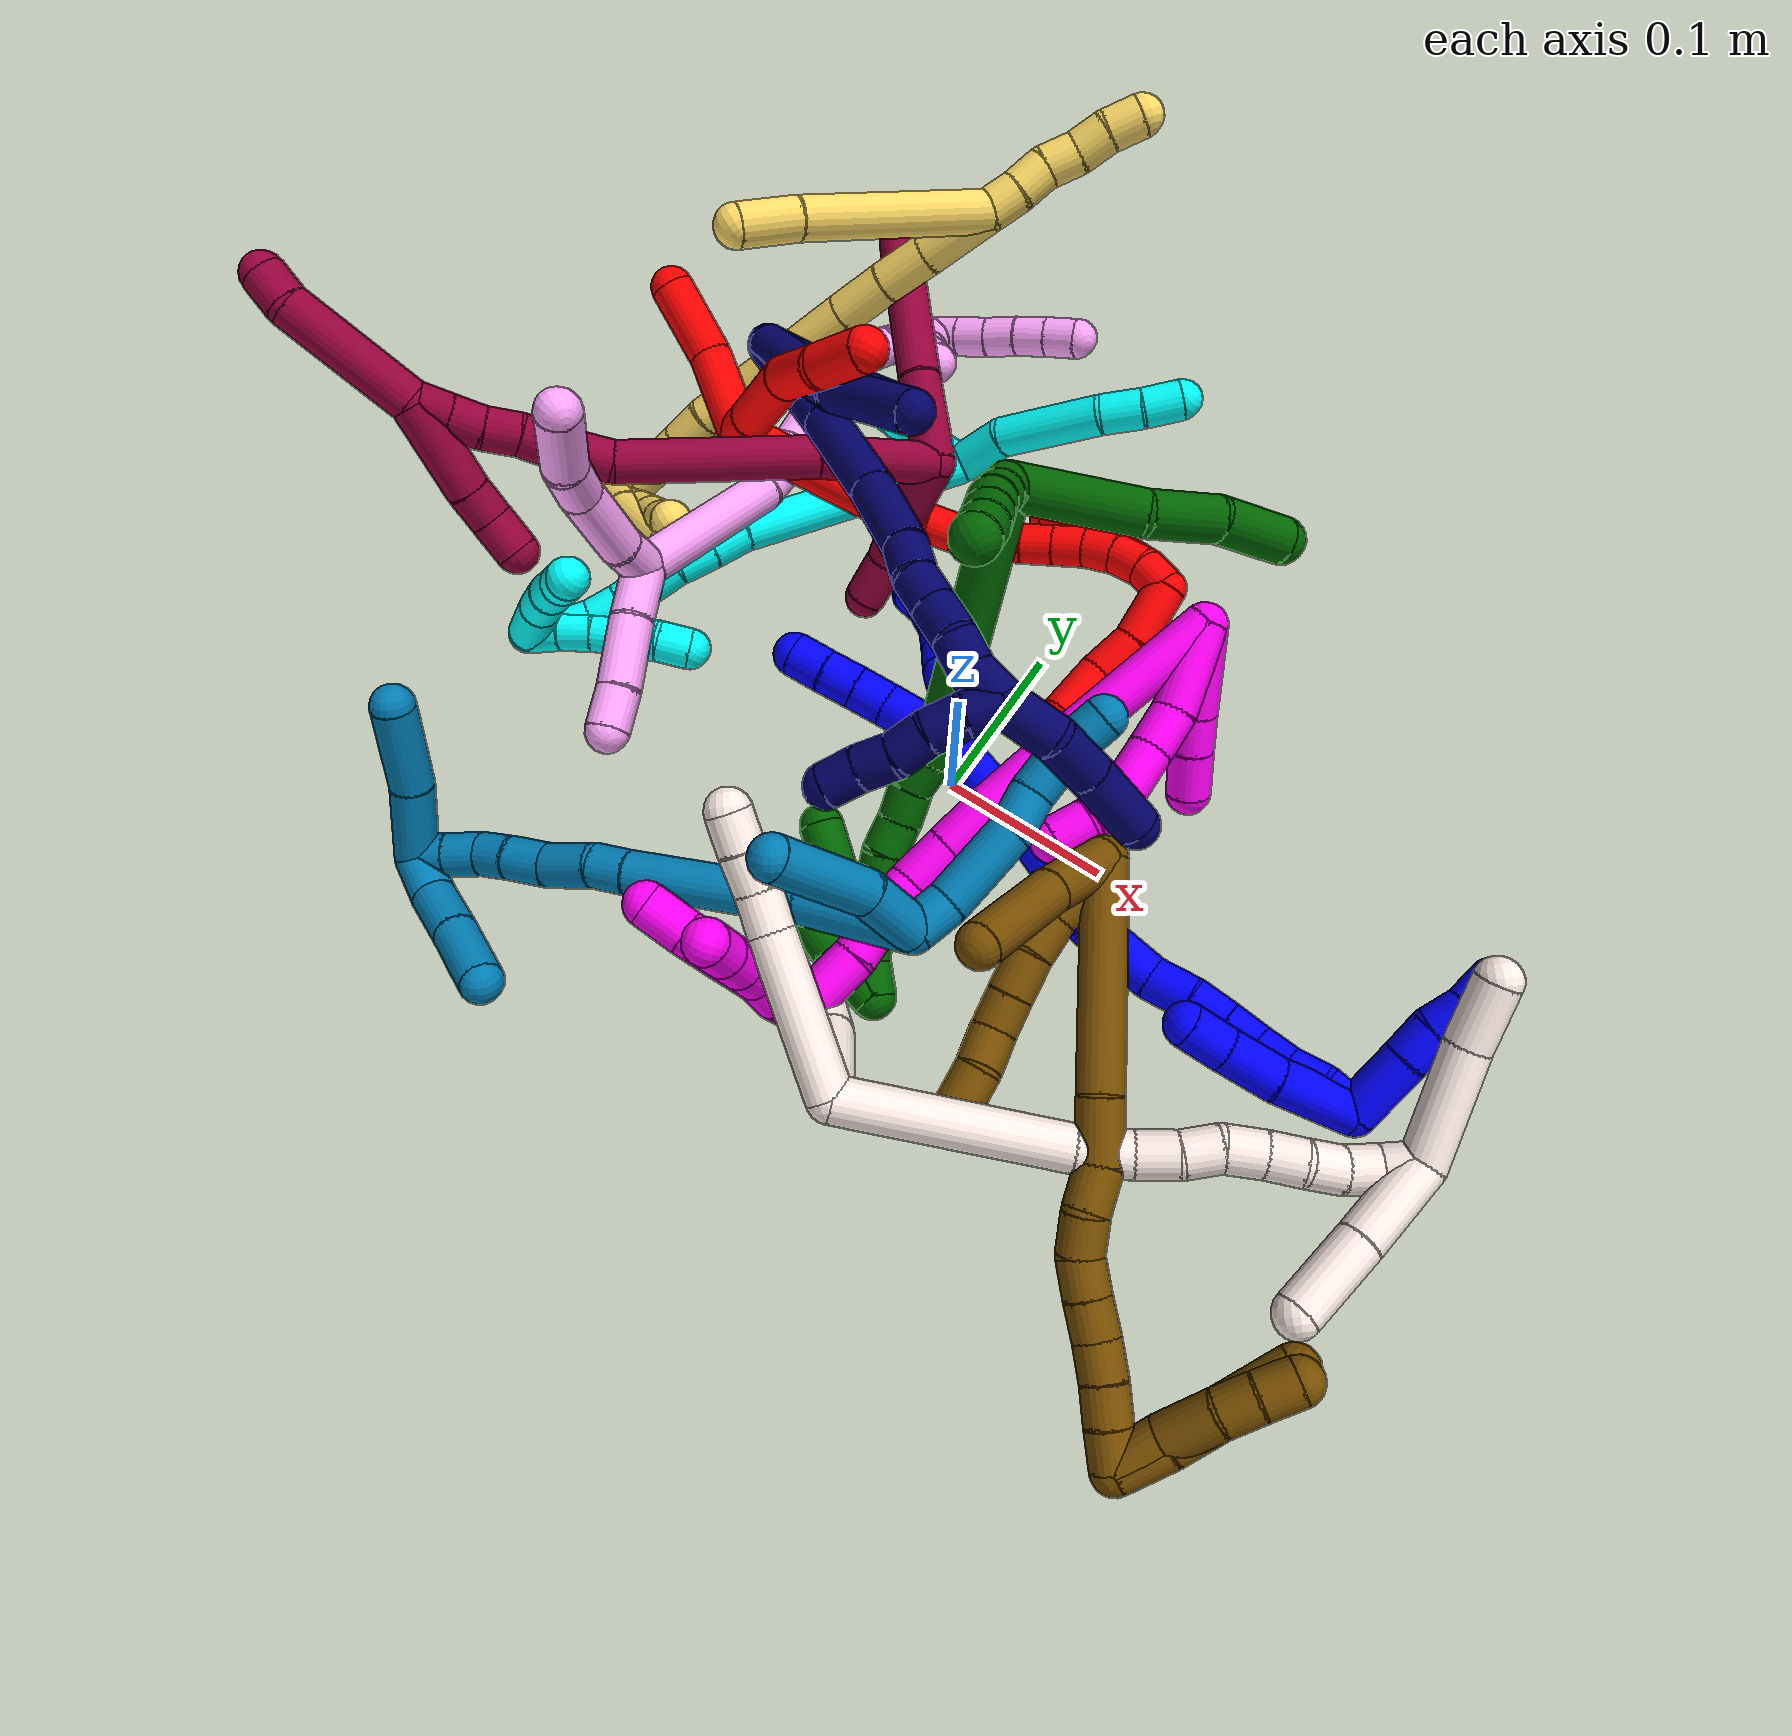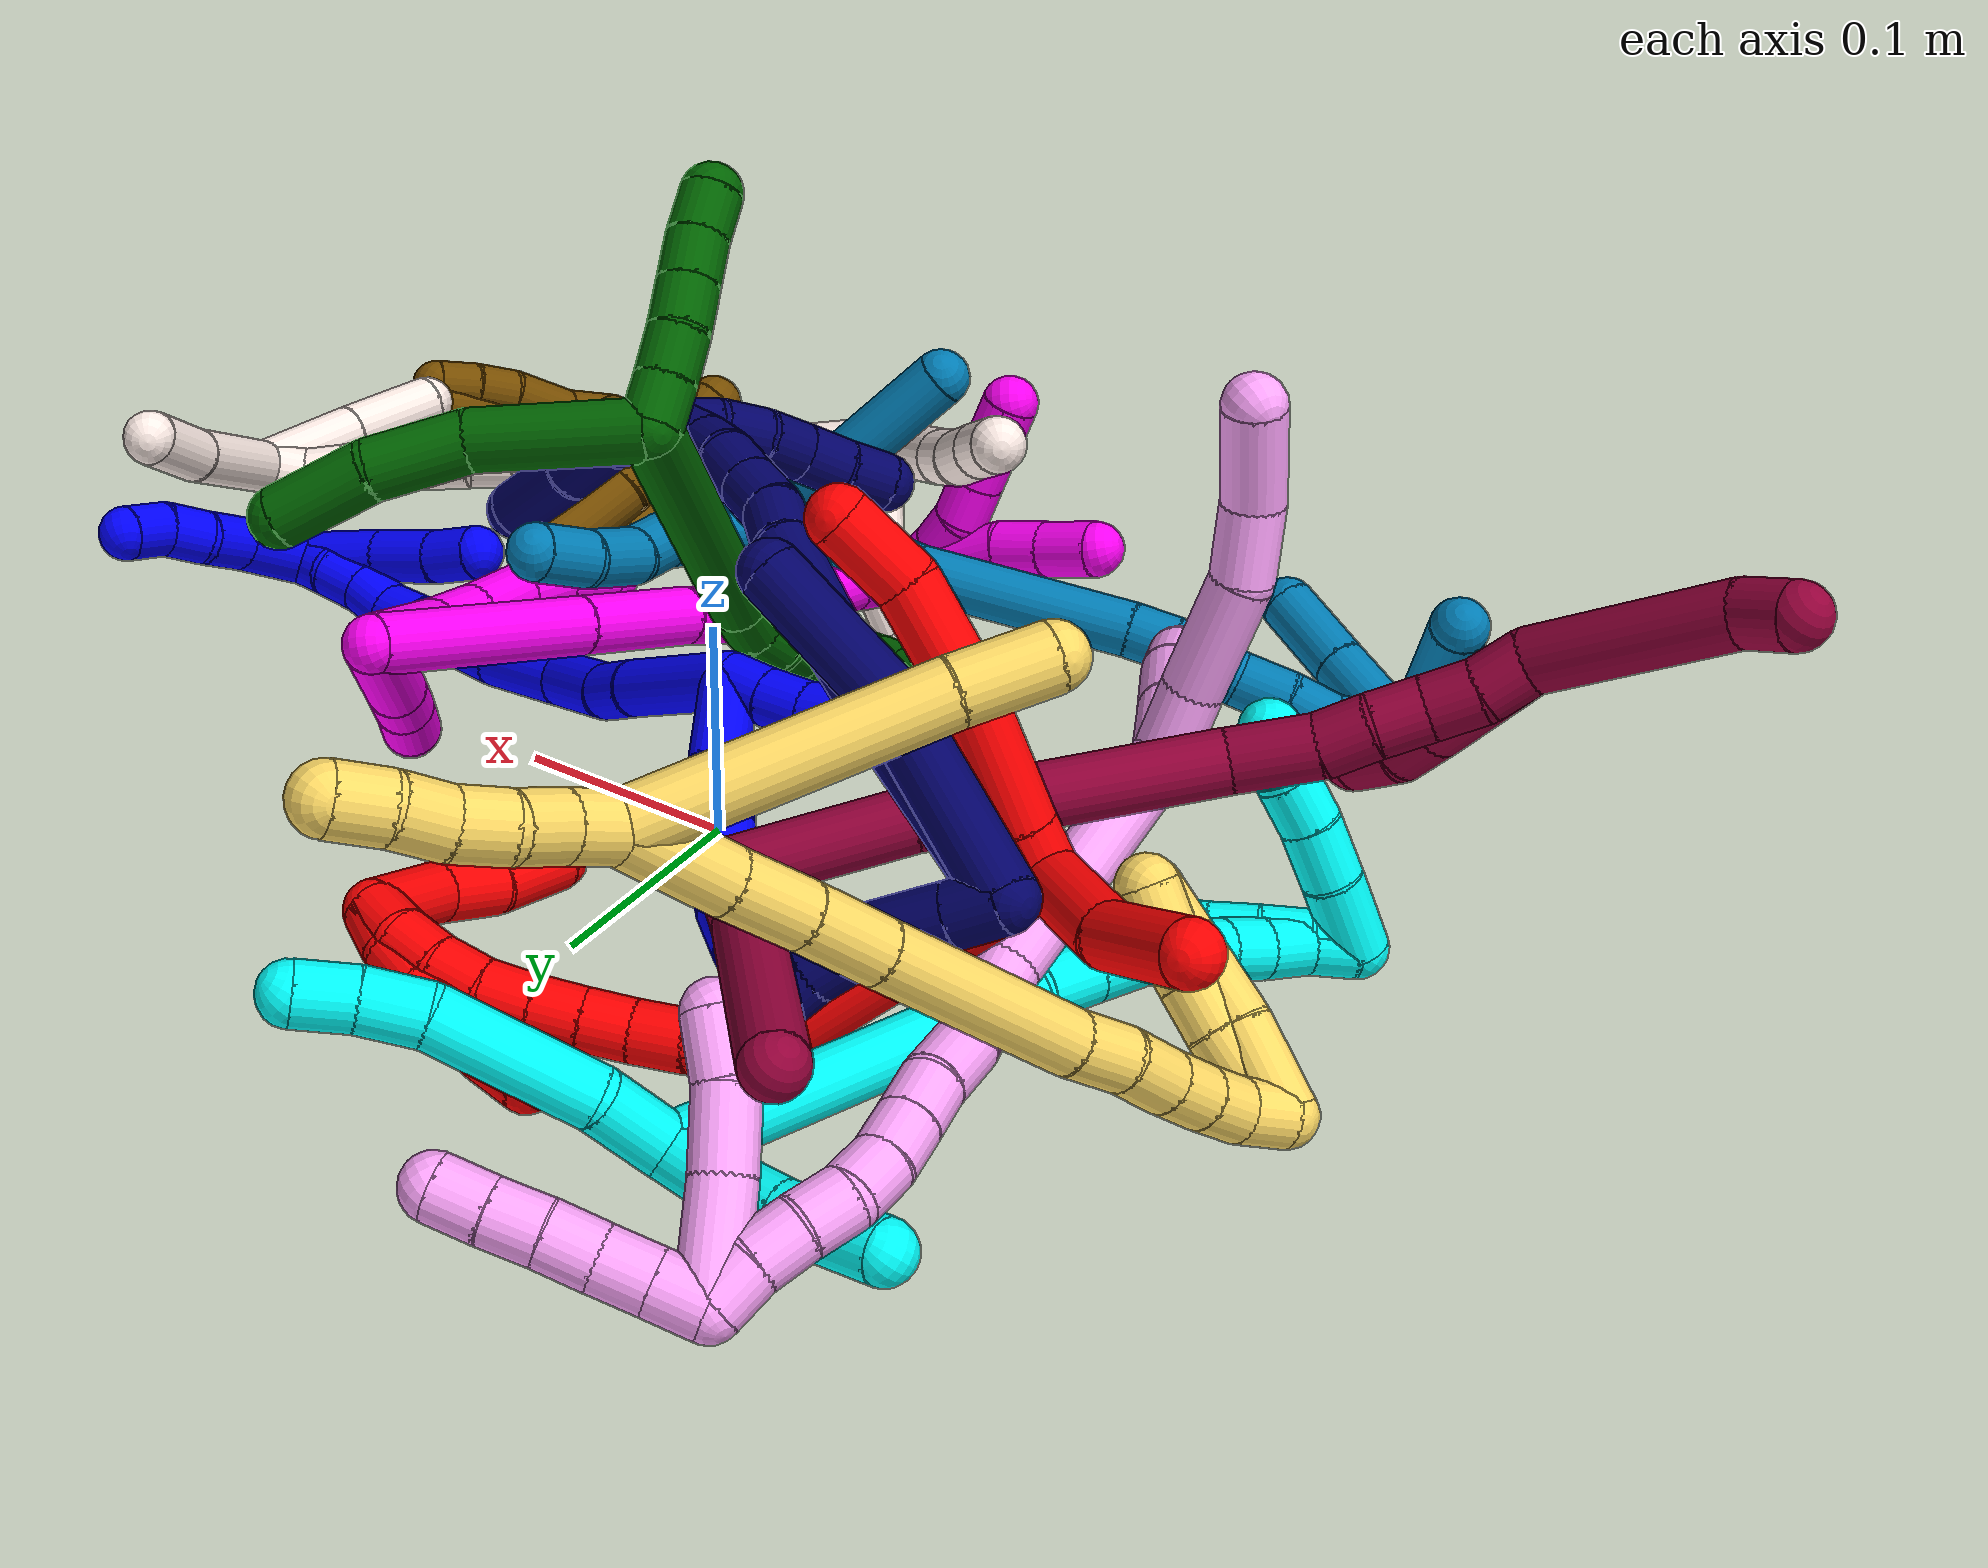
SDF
<sdf version="1.7">
 <world name="default">
  <plugin name="TubeGeneratorPlugin" filename="libtube_generator_plugin.so"/>
  <model name="photoneo_s_sensor">
   <static>1</static>
   <pose>0 0 2 1.57079 1.57079 3.14159</pose>
   <link name="link">
    <inertial><mass>0.1</mass></inertial>
    <sensor name="sensor" type="depth">
     <update_rate>30</update_rate>
     <camera>
      <horizontal_fov>1.22</horizontal_fov>
      <image><width>1920</width><height>1200</height><format>B8G8R8</format></image>
      <clip><near>0.1</near><far>4</far></clip>
      <depth_camera><output>points</output></depth_camera>
     </camera>
     <plugin name="camera_plugin" filename="libgazebo_ros_depth_camera.so">
      <baseline>0.2</baseline>
      <alwaysOn>1</alwaysOn>
      <updateRate>0.0</updateRate>
      <cameraName>camera_ir</cameraName>
      <imageTopicName>/camera/color/image_raw</imageTopicName>
      <cameraInfoTopicName>/camera/color/camera_info</cameraInfoTopicName>
      <depthImageTopicName>/camera/depth/image_raw</depthImageTopicName>
      <depthImageCameraInfoTopicName>/camera/depth/camera_info</depthImageCameraInfoTopicName>
      <pointCloudTopicName>/camera/depth/points</pointCloudTopicName>
      <frameName>fr_optical</frameName>
      <pointCloudCutoff>0.1</pointCloudCutoff>
      <pointCloudCutoffMax>2.0</pointCloudCutoffMax>
      <distortionK1>0</distortionK1>
      <distortionK2>0</distortionK2>
      <distortionK3>0</distortionK3>
      <distortionT1>0</distortionT1>
      <distortionT2>0</distortionT2>
      <CxPrime>0</CxPrime>
      <Cx>0</Cx>
      <Cy>0</Cy>
      <focalLength>0</focalLength>
      <hackBaseline>0</hackBaseline>
     </plugin>
    </sensor>
   </link>
  </model>
  <gravity>0 0 -9.8</gravity>
  <magnetic_field>6e-06 2.3e-05 -4.2e-05</magnetic_field>
  <atmosphere type="adiabatic"/>
  <physics name="default_physics" default="0" type="ode">
   <max_step_size>0.003</max_step_size>
   <real_time_factor>1</real_time_factor>
   <real_time_update_rate>1000</real_time_update_rate>
   <max_contacts>10000</max_contacts>
   <ode>
    <solver>
     <type>quick</type>
     <iters>100</iters>
     <sor>1.3</sor>
     <use_dynamic_moi_rescaling>0</use_dynamic_moi_rescaling>
    </solver>
    <constraints>
     <contact_max_correcting_vel>0</contact_max_correcting_vel>
     <contact_surface_layer>0.001</contact_surface_layer>
     <cfm>0</cfm>
     <erp>0.2</erp>
    </constraints>
   </ode>
  </physics>
  <scene><ambient>0.4 0.4 0.4 1</ambient><background>0.7 0.7 0.7 1</background><shadows>0</shadows></scene>
  <audio><device>default</device></audio>
  <spherical_coordinates>
   <surface_model>EARTH_WGS84</surface_model>
   <latitude_deg>0</latitude_deg>
   <longitude_deg>0</longitude_deg>
   <elevation>0</elevation>
   <heading_deg>0</heading_deg>
  </spherical_coordinates>
  <model name="bin">
   <static>1</static>
   <link name="bottom">
    <collision name="collision-bottom">
     <pose>0 0 -0.01 0 -0 0</pose>
     <geometry><box><size>0.8 0.6 0.02</size></box></geometry>
     <surface>
      <friction><ode><mu>100</mu><mu2>100</mu2></ode></friction>
      <contact><collide_bitmask>65535</collide_bitmask></contact>
     </surface>
    </collision>
   </link>
   <link name="west_wall">
    <collision name="collision-west_wall">
     <pose>-0.41 0 0.1 0 -0 0</pose>
     <geometry><box><size>0.02 0.6 0.2</size></box></geometry>
     <surface>
      <friction><ode><mu>100</mu><mu2>100</mu2></ode></friction>
      <contact><collide_bitmask>65535</collide_bitmask></contact>
     </surface>
    </collision>
   </link>
   <link name="east_wall">
    <collision name="collision-east_wall">
     <pose>0.41 0 0.1 0 -0 0</pose>
     <geometry><box><size>0.02 0.6 0.2</size></box></geometry>
     <surface>
      <friction><ode><mu>100</mu><mu2>100</mu2></ode></friction>
      <contact><collide_bitmask>65535</collide_bitmask></contact>
     </surface>
    </collision>
   </link>
   <link name="south_wall">
    <collision name="collision-south_wall">
     <pose>0 -0.31 0.1 0 -0 0</pose>
     <geometry><box><size>0.8 0.02 0.2</size></box></geometry>
     <surface>
      <friction><ode><mu>100</mu><mu2>100</mu2></ode></friction>
      <contact><collide_bitmask>65535</collide_bitmask></contact>
     </surface>
    </collision>
   </link>
   <link name="north_wall">
    <collision name="collision-north_wall">
     <pose>0 0.31 0.1 0 -0 0</pose>
     <geometry><box><size>0.8 0.02 0.2</size></box></geometry>
     <surface>
      <friction><ode><mu>100</mu><mu2>100</mu2></ode></friction>
      <contact><collide_bitmask>65535</collide_bitmask></contact>
     </surface>
    </collision>
   </link>
  </model>
  <model name="1">
   <static>0</static>
   <link name="1">
    <collision name="collision-cylinder-e_1_2_8">
     <pose>0.003936 0.006146 -0.019372 -2.83436 0.191318 -1.10955</pose>
     <geometry><cylinder><radius>0.0125</radius><length>0.041403</length></cylinder></geometry>
     <surface>
      <friction><ode><mu>1.16</mu><mu2>1.16</mu2><slip1>0</slip1><slip2>0</slip2></ode></friction>
      <contact><ode><kp>1e+06</kp><kd>1</kd><max_vel>0</max_vel><min_depth>0.001</min_depth></ode></contact>
     </surface>
    </collision>
    <visual name="visual-cylinder-e_1_2_8">
     <pose>0.003936 0.006146 -0.019372 -2.83436 0.191318 -1.10955</pose>
     <geometry><cylinder><radius>0.0125</radius><length>0.041403</length></cylinder></geometry>
     <material><ambient>0 0 1 1</ambient></material>
    </visual>
    <collision name="collision-cylinder-e_2_8_9">
     <pose>0.008924 0.013909 -0.052689 -3.02623 0.074736 -1.14911</pose>
     <geometry><cylinder><radius>0.0125</radius><length>0.028156</length></cylinder></geometry>
     <surface>
      <friction><ode><mu>1.16</mu><mu2>1.16</mu2><slip1>0</slip1><slip2>0</slip2></ode></friction>
      <contact><ode><kp>1e+06</kp><kd>1</kd><max_vel>0</max_vel><min_depth>0.001</min_depth></ode></contact>
     </surface>
    </collision>
    <visual name="visual-cylinder-e_2_8_9">
     <pose>0.008924 0.013909 -0.052689 -3.02623 0.074736 -1.14911</pose>
     <geometry><cylinder><radius>0.0125</radius><length>0.028156</length></cylinder></geometry>
     <material><ambient>0 0 1 1</ambient></material>
    </visual>
    <collision name="collision-cylinder-e_3_9_10">
     <pose>0.010656 0.017963 -0.076344 -2.8955 0.067904 -0.536059</pose>
     <geometry><cylinder><radius>0.0125</radius><length>0.020068</length></cylinder></geometry>
     <surface>
      <friction><ode><mu>1.16</mu><mu2>1.16</mu2><slip1>0</slip1><slip2>0</slip2></ode></friction>
      <contact><ode><kp>1e+06</kp><kd>1</kd><max_vel>0</max_vel><min_depth>0.001</min_depth></ode></contact>
     </surface>
    </collision>
    <visual name="visual-cylinder-e_3_9_10">
     <pose>0.010656 0.017963 -0.076344 -2.8955 0.067904 -0.536059</pose>
     <geometry><cylinder><radius>0.0125</radius><length>0.020068</length></cylinder></geometry>
     <material><ambient>0 0 1 1</ambient></material>
    </visual>
    <collision name="collision-cylinder-e_4_10_11">
     <pose>0.011152 0.023101 -0.095852 -2.87284 -0.018148 0.134038</pose>
     <geometry><cylinder><radius>0.0125</radius><length>0.02033</length></cylinder></geometry>
     <surface>
      <friction><ode><mu>1.16</mu><mu2>1.16</mu2><slip1>0</slip1><slip2>0</slip2></ode></friction>
      <contact><ode><kp>1e+06</kp><kd>1</kd><max_vel>0</max_vel><min_depth>0.001</min_depth></ode></contact>
     </surface>
    </collision>
    <visual name="visual-cylinder-e_4_10_11">
     <pose>0.011152 0.023101 -0.095852 -2.87284 -0.018148 0.134038</pose>
     <geometry><cylinder><radius>0.0125</radius><length>0.02033</length></cylinder></geometry>
     <material><ambient>0 0 1 1</ambient></material>
    </visual>
    <collision name="collision-cylinder-e_5_11_12">
     <pose>0.008965 0.026209 -0.115442 -3.09977 -0.201557 2.73372</pose>
     <geometry><cylinder><radius>0.0125</radius><length>0.020006</length></cylinder></geometry>
     <surface>
      <friction><ode><mu>1.16</mu><mu2>1.16</mu2><slip1>0</slip1><slip2>0</slip2></ode></friction>
      <contact><ode><kp>1e+06</kp><kd>1</kd><max_vel>0</max_vel><min_depth>0.001</min_depth></ode></contact>
     </surface>
    </collision>
    <visual name="visual-cylinder-e_5_11_12">
     <pose>0.008965 0.026209 -0.115442 -3.09977 -0.201557 2.73372</pose>
     <geometry><cylinder><radius>0.0125</radius><length>0.020006</length></cylinder></geometry>
     <material><ambient>0 0 1 1</ambient></material>
    </visual>
    <collision name="collision-cylinder-e_6_12_6">
     <pose>0.006417 0.024562 -0.135024 2.93444 -0.054555 -0.513375</pose>
     <geometry><cylinder><radius>0.0125</radius><length>0.020037</length></cylinder></geometry>
     <surface>
      <friction><ode><mu>1.16</mu><mu2>1.16</mu2><slip1>0</slip1><slip2>0</slip2></ode></friction>
      <contact><ode><kp>1e+06</kp><kd>1</kd><max_vel>0</max_vel><min_depth>0.001</min_depth></ode></contact>
     </surface>
    </collision>
    <visual name="visual-cylinder-e_6_12_6">
     <pose>0.006417 0.024562 -0.135024 2.93444 -0.054555 -0.513375</pose>
     <geometry><cylinder><radius>0.0125</radius><length>0.020037</length></cylinder></geometry>
     <material><ambient>0 0 1 1</ambient></material>
    </visual>
    <collision name="collision-cylinder-e_1_2_13">
     <pose>-0.00561 -0.003799 -0.007355 2.66475 -0.59562 -1.80211</pose>
     <geometry><cylinder><radius>0.0125</radius><length>0.02</length></cylinder></geometry>
     <surface>
      <friction><ode><mu>1.16</mu><mu2>1.16</mu2><slip1>0</slip1><slip2>0</slip2></ode></friction>
      <contact><ode><kp>1e+06</kp><kd>1</kd><max_vel>0</max_vel><min_depth>0.001</min_depth></ode></contact>
     </surface>
    </collision>
    <visual name="visual-cylinder-e_1_2_13">
     <pose>-0.00561 -0.003799 -0.007355 2.66475 -0.59562 -1.80211</pose>
     <geometry><cylinder><radius>0.0125</radius><length>0.02</length></cylinder></geometry>
     <material><ambient>0 0 1 1</ambient></material>
    </visual>
    <collision name="collision-cylinder-e_2_13_14">
     <pose>-0.01722 -0.011686 -0.021586 2.60536 -0.643502 -1.76296</pose>
     <geometry><cylinder><radius>0.0125</radius><length>0.02</length></cylinder></geometry>
     <surface>
      <friction><ode><mu>1.16</mu><mu2>1.16</mu2><slip1>0</slip1><slip2>0</slip2></ode></friction>
      <contact><ode><kp>1e+06</kp><kd>1</kd><max_vel>0</max_vel><min_depth>0.001</min_depth></ode></contact>
     </surface>
    </collision>
    <visual name="visual-cylinder-e_2_13_14">
     <pose>-0.01722 -0.011686 -0.021586 2.60536 -0.643502 -1.76296</pose>
     <geometry><cylinder><radius>0.0125</radius><length>0.02</length></cylinder></geometry>
     <material><ambient>0 0 1 1</ambient></material>
    </visual>
    <collision name="collision-cylinder-e_3_14_15">
     <pose>-0.030155 -0.019882 -0.034382 2.53479 -0.766237 -1.82076</pose>
     <geometry><cylinder><radius>0.0125</radius><length>0.02</length></cylinder></geometry>
     <surface>
      <friction><ode><mu>1.16</mu><mu2>1.16</mu2><slip1>0</slip1><slip2>0</slip2></ode></friction>
      <contact><ode><kp>1e+06</kp><kd>1</kd><max_vel>0</max_vel><min_depth>0.001</min_depth></ode></contact>
     </surface>
    </collision>
    <visual name="visual-cylinder-e_3_14_15">
     <pose>-0.030155 -0.019882 -0.034382 2.53479 -0.766237 -1.82076</pose>
     <geometry><cylinder><radius>0.0125</radius><length>0.02</length></cylinder></geometry>
     <material><ambient>0 0 1 1</ambient></material>
    </visual>
    <collision name="collision-cylinder-e_4_15_16">
     <pose>-0.043843 -0.028306 -0.046281 2.51651 -0.741531 -1.75462</pose>
     <geometry><cylinder><radius>0.0125</radius><length>0.02</length></cylinder></geometry>
     <surface>
      <friction><ode><mu>1.16</mu><mu2>1.16</mu2><slip1>0</slip1><slip2>0</slip2></ode></friction>
      <contact><ode><kp>1e+06</kp><kd>1</kd><max_vel>0</max_vel><min_depth>0.001</min_depth></ode></contact>
     </surface>
    </collision>
    <visual name="visual-cylinder-e_4_15_16">
     <pose>-0.043843 -0.028306 -0.046281 2.51651 -0.741531 -1.75462</pose>
     <geometry><cylinder><radius>0.0125</radius><length>0.02</length></cylinder></geometry>
     <material><ambient>0 0 1 1</ambient></material>
    </visual>
    <collision name="collision-cylinder-e_5_16_5">
     <pose>-0.056988 -0.036746 -0.058753 2.57554 -0.693246 -1.78582</pose>
     <geometry><cylinder><radius>0.0125</radius><length>0.02</length></cylinder></geometry>
     <surface>
      <friction><ode><mu>1.16</mu><mu2>1.16</mu2><slip1>0</slip1><slip2>0</slip2></ode></friction>
      <contact><ode><kp>1e+06</kp><kd>1</kd><max_vel>0</max_vel><min_depth>0.001</min_depth></ode></contact>
     </surface>
    </collision>
    <visual name="visual-cylinder-e_5_16_5">
     <pose>-0.056988 -0.036746 -0.058753 2.57554 -0.693246 -1.78582</pose>
     <geometry><cylinder><radius>0.0125</radius><length>0.02</length></cylinder></geometry>
     <material><ambient>0 0 1 1</ambient></material>
    </visual>
    <collision name="collision-cylinder-e_1_2_17">
     <pose>0.027222 0.002143 0.016075 -0.132526 1.03353 -0.075385</pose>
     <geometry><cylinder><radius>0.0125</radius><length>0.063373</length></cylinder></geometry>
     <surface>
      <friction><ode><mu>1.16</mu><mu2>1.16</mu2><slip1>0</slip1><slip2>0</slip2></ode></friction>
      <contact><ode><kp>1e+06</kp><kd>1</kd><max_vel>0</max_vel><min_depth>0.001</min_depth></ode></contact>
     </surface>
    </collision>
    <visual name="visual-cylinder-e_1_2_17">
     <pose>0.027222 0.002143 0.016075 -0.132526 1.03353 -0.075385</pose>
     <geometry><cylinder><radius>0.0125</radius><length>0.063373</length></cylinder></geometry>
     <material><ambient>0 0 1 1</ambient></material>
    </visual>
    <collision name="collision-cylinder-e_2_17_18">
     <pose>0.06455 0.003805 0.038078 0.080974 1.03883 0.046317</pose>
     <geometry><cylinder><radius>0.0125</radius><length>0.023453</length></cylinder></geometry>
     <surface>
      <friction><ode><mu>1.16</mu><mu2>1.16</mu2><slip1>0</slip1><slip2>0</slip2></ode></friction>
      <contact><ode><kp>1e+06</kp><kd>1</kd><max_vel>0</max_vel><min_depth>0.001</min_depth></ode></contact>
     </surface>
    </collision>
    <visual name="visual-cylinder-e_2_17_18">
     <pose>0.06455 0.003805 0.038078 0.080974 1.03883 0.046317</pose>
     <geometry><cylinder><radius>0.0125</radius><length>0.023453</length></cylinder></geometry>
     <material><ambient>0 0 1 1</ambient></material>
    </visual>
    <collision name="collision-cylinder-e_3_18_19">
     <pose>0.090156 0.001651 0.058022 0.118767 0.83212 0.052528</pose>
     <geometry><cylinder><radius>0.0125</radius><length>0.041926</length></cylinder></geometry>
     <surface>
      <friction><ode><mu>1.16</mu><mu2>1.16</mu2><slip1>0</slip1><slip2>0</slip2></ode></friction>
      <contact><ode><kp>1e+06</kp><kd>1</kd><max_vel>0</max_vel><min_depth>0.001</min_depth></ode></contact>
     </surface>
    </collision>
    <visual name="visual-cylinder-e_3_18_19">
     <pose>0.090156 0.001651 0.058022 0.118767 0.83212 0.052528</pose>
     <geometry><cylinder><radius>0.0125</radius><length>0.041926</length></cylinder></geometry>
     <material><ambient>0 0 1 1</ambient></material>
    </visual>
    <collision name="collision-cylinder-e_4_19_20">
     <pose>0.120896 0.0053 0.087107 -0.339432 0.761676 -0.137009</pose>
     <geometry><cylinder><radius>0.0125</radius><length>0.044169</length></cylinder></geometry>
     <surface>
      <friction><ode><mu>1.16</mu><mu2>1.16</mu2><slip1>0</slip1><slip2>0</slip2></ode></friction>
      <contact><ode><kp>1e+06</kp><kd>1</kd><max_vel>0</max_vel><min_depth>0.001</min_depth></ode></contact>
     </surface>
    </collision>
    <visual name="visual-cylinder-e_4_19_20">
     <pose>0.120896 0.0053 0.087107 -0.339432 0.761676 -0.137009</pose>
     <geometry><cylinder><radius>0.0125</radius><length>0.044169</length></cylinder></geometry>
     <material><ambient>0 0 1 1</ambient></material>
    </visual>
    <collision name="collision-cylinder-e_5_20_21">
     <pose>0.142335 0.016451 0.111436 -0.561948 0.515344 -0.151822</pose>
     <geometry><cylinder><radius>0.0125</radius><length>0.02515</length></cylinder></geometry>
     <surface>
      <friction><ode><mu>1.16</mu><mu2>1.16</mu2><slip1>0</slip1><slip2>0</slip2></ode></friction>
      <contact><ode><kp>1e+06</kp><kd>1</kd><max_vel>0</max_vel><min_depth>0.001</min_depth></ode></contact>
     </surface>
    </collision>
    <visual name="visual-cylinder-e_5_20_21">
     <pose>0.142335 0.016451 0.111436 -0.561948 0.515344 -0.151822</pose>
     <geometry><cylinder><radius>0.0125</radius><length>0.02515</length></cylinder></geometry>
     <material><ambient>0 0 1 1</ambient></material>
    </visual>
    <collision name="collision-cylinder-e_6_21_22">
     <pose>0.154632 0.025835 0.128763 -0.414884 0.605304 -0.131247</pose>
     <geometry><cylinder><radius>0.0125</radius><length>0.02144</length></cylinder></geometry>
     <surface>
      <friction><ode><mu>1.16</mu><mu2>1.16</mu2><slip1>0</slip1><slip2>0</slip2></ode></friction>
      <contact><ode><kp>1e+06</kp><kd>1</kd><max_vel>0</max_vel><min_depth>0.001</min_depth></ode></contact>
     </surface>
    </collision>
    <visual name="visual-cylinder-e_6_21_22">
     <pose>0.154632 0.025835 0.128763 -0.414884 0.605304 -0.131247</pose>
     <geometry><cylinder><radius>0.0125</radius><length>0.02144</length></cylinder></geometry>
     <material><ambient>0 0 1 1</ambient></material>
    </visual>
    <collision name="collision-cylinder-e_7_22_23">
     <pose>0.166882 0.032484 0.144365 -0.389884 0.646667 -0.132135</pose>
     <geometry><cylinder><radius>0.0125</radius><length>0.020413</length></cylinder></geometry>
     <surface>
      <friction><ode><mu>1.16</mu><mu2>1.16</mu2><slip1>0</slip1><slip2>0</slip2></ode></friction>
      <contact><ode><kp>1e+06</kp><kd>1</kd><max_vel>0</max_vel><min_depth>0.001</min_depth></ode></contact>
     </surface>
    </collision>
    <visual name="visual-cylinder-e_7_22_23">
     <pose>0.166882 0.032484 0.144365 -0.389884 0.646667 -0.132135</pose>
     <geometry><cylinder><radius>0.0125</radius><length>0.020413</length></cylinder></geometry>
     <material><ambient>0 0 1 1</ambient></material>
    </visual>
    <collision name="collision-cylinder-e_8_23_24">
     <pose>0.17701 0.038973 0.16045 -0.377758 0.408166 -0.079084</pose>
     <geometry><cylinder><radius>0.0125</radius><length>0.020043</length></cylinder></geometry>
     <surface>
      <friction><ode><mu>1.16</mu><mu2>1.16</mu2><slip1>0</slip1><slip2>0</slip2></ode></friction>
      <contact><ode><kp>1e+06</kp><kd>1</kd><max_vel>0</max_vel><min_depth>0.001</min_depth></ode></contact>
     </surface>
    </collision>
    <visual name="visual-cylinder-e_8_23_24">
     <pose>0.17701 0.038973 0.16045 -0.377758 0.408166 -0.079084</pose>
     <geometry><cylinder><radius>0.0125</radius><length>0.020043</length></cylinder></geometry>
     <material><ambient>0 0 1 1</ambient></material>
    </visual>
    <collision name="collision-cylinder-e_9_24_25">
     <pose>0.185688 0.047129 0.176443 -0.569196 0.488854 -0.145669</pose>
     <geometry><cylinder><radius>0.0125</radius><length>0.020019</length></cylinder></geometry>
     <surface>
      <friction><ode><mu>1.16</mu><mu2>1.16</mu2><slip1>0</slip1><slip2>0</slip2></ode></friction>
      <contact><ode><kp>1e+06</kp><kd>1</kd><max_vel>0</max_vel><min_depth>0.001</min_depth></ode></contact>
     </surface>
    </collision>
    <visual name="visual-cylinder-e_9_24_25">
     <pose>0.185688 0.047129 0.176443 -0.569196 0.488854 -0.145669</pose>
     <geometry><cylinder><radius>0.0125</radius><length>0.020019</length></cylinder></geometry>
     <material><ambient>0 0 1 1</ambient></material>
    </visual>
    <collision name="collision-cylinder-e_10_25_1">
     <pose>0.196439 0.054493 0.191421 -0.332536 0.649321 -0.112845</pose>
     <geometry><cylinder><radius>0.0125</radius><length>0.020013</length></cylinder></geometry>
     <surface>
      <friction><ode><mu>1.16</mu><mu2>1.16</mu2><slip1>0</slip1><slip2>0</slip2></ode></friction>
      <contact><ode><kp>1e+06</kp><kd>1</kd><max_vel>0</max_vel><min_depth>0.001</min_depth></ode></contact>
     </surface>
    </collision>
    <visual name="visual-cylinder-e_10_25_1">
     <pose>0.196439 0.054493 0.191421 -0.332536 0.649321 -0.112845</pose>
     <geometry><cylinder><radius>0.0125</radius><length>0.020013</length></cylinder></geometry>
     <material><ambient>0 0 1 1</ambient></material>
    </visual>
    <collision name="collision-cylinder-e_1_1_26">
     <pose>0.198613 0.076132 0.197015 -1.67231 -0.199884 0.221114</pose>
     <geometry><cylinder><radius>0.0125</radius><length>0.039048</length></cylinder></geometry>
     <surface>
      <friction><ode><mu>1.16</mu><mu2>1.16</mu2><slip1>0</slip1><slip2>0</slip2></ode></friction>
      <contact><ode><kp>1e+06</kp><kd>1</kd><max_vel>0</max_vel><min_depth>0.001</min_depth></ode></contact>
     </surface>
    </collision>
    <visual name="visual-cylinder-e_1_1_26">
     <pose>0.198613 0.076132 0.197015 -1.67231 -0.199884 0.221114</pose>
     <geometry><cylinder><radius>0.0125</radius><length>0.039048</length></cylinder></geometry>
     <material><ambient>0 0 1 1</ambient></material>
    </visual>
    <collision name="collision-cylinder-e_2_26_27">
     <pose>0.193001 0.105309 0.193518 -1.72326 -0.167586 0.195141</pose>
     <geometry><cylinder><radius>0.0125</radius><length>0.02081</length></cylinder></geometry>
     <surface>
      <friction><ode><mu>1.16</mu><mu2>1.16</mu2><slip1>0</slip1><slip2>0</slip2></ode></friction>
      <contact><ode><kp>1e+06</kp><kd>1</kd><max_vel>0</max_vel><min_depth>0.001</min_depth></ode></contact>
     </surface>
    </collision>
    <visual name="visual-cylinder-e_2_26_27">
     <pose>0.193001 0.105309 0.193518 -1.72326 -0.167586 0.195141</pose>
     <geometry><cylinder><radius>0.0125</radius><length>0.02081</length></cylinder></geometry>
     <material><ambient>0 0 1 1</ambient></material>
    </visual>
    <collision name="collision-cylinder-e_3_27_28">
     <pose>0.19126 0.125496 0.192583 -1.50878 -0.000508 0.000477</pose>
     <geometry><cylinder><radius>0.0125</radius><length>0.020131</length></cylinder></geometry>
     <surface>
      <friction><ode><mu>1.16</mu><mu2>1.16</mu2><slip1>0</slip1><slip2>0</slip2></ode></friction>
      <contact><ode><kp>1e+06</kp><kd>1</kd><max_vel>0</max_vel><min_depth>0.001</min_depth></ode></contact>
     </surface>
    </collision>
    <visual name="visual-cylinder-e_3_27_28">
     <pose>0.19126 0.125496 0.192583 -1.50878 -0.000508 0.000477</pose>
     <geometry><cylinder><radius>0.0125</radius><length>0.020131</length></cylinder></geometry>
     <material><ambient>0 0 1 1</ambient></material>
    </visual>
    <collision name="collision-cylinder-e_4_28_4">
     <pose>0.19173 0.145136 0.190409 -1.85453 0.047526 -0.063355</pose>
     <geometry><cylinder><radius>0.0125</radius><length>0.020011</length></cylinder></geometry>
     <surface>
      <friction><ode><mu>1.16</mu><mu2>1.16</mu2><slip1>0</slip1><slip2>0</slip2></ode></friction>
      <contact><ode><kp>1e+06</kp><kd>1</kd><max_vel>0</max_vel><min_depth>0.001</min_depth></ode></contact>
     </surface>
    </collision>
    <visual name="visual-cylinder-e_4_28_4">
     <pose>0.19173 0.145136 0.190409 -1.85453 0.047526 -0.063355</pose>
     <geometry><cylinder><radius>0.0125</radius><length>0.020011</length></cylinder></geometry>
     <material><ambient>0 0 1 1</ambient></material>
    </visual>
    <collision name="collision-cylinder-e_1_1_29">
     <pose>0.18558 0.046476 0.189436 2.3016 -0.87018 -1.61079</pose>
     <geometry><cylinder><radius>0.0125</radius><length>0.04424</length></cylinder></geometry>
     <surface>
      <friction><ode><mu>1.16</mu><mu2>1.16</mu2><slip1>0</slip1><slip2>0</slip2></ode></friction>
      <contact><ode><kp>1e+06</kp><kd>1</kd><max_vel>0</max_vel><min_depth>0.001</min_depth></ode></contact>
     </surface>
    </collision>
    <visual name="visual-cylinder-e_1_1_29">
     <pose>0.18558 0.046476 0.189436 2.3016 -0.87018 -1.61079</pose>
     <geometry><cylinder><radius>0.0125</radius><length>0.04424</length></cylinder></geometry>
     <material><ambient>0 0 1 1</ambient></material>
    </visual>
    <collision name="collision-cylinder-e_2_29_30">
     <pose>0.156451 0.02988 0.171857 2.50358 -0.883269 -1.92201</pose>
     <geometry><cylinder><radius>0.0125</radius><length>0.031624</length></cylinder></geometry>
     <surface>
      <friction><ode><mu>1.16</mu><mu2>1.16</mu2><slip1>0</slip1><slip2>0</slip2></ode></friction>
      <contact><ode><kp>1e+06</kp><kd>1</kd><max_vel>0</max_vel><min_depth>0.001</min_depth></ode></contact>
     </surface>
    </collision>
    <visual name="visual-cylinder-e_2_29_30">
     <pose>0.156451 0.02988 0.171857 2.50358 -0.883269 -1.92201</pose>
     <geometry><cylinder><radius>0.0125</radius><length>0.031624</length></cylinder></geometry>
     <material><ambient>0 0 1 1</ambient></material>
    </visual>
    <collision name="collision-cylinder-e_3_30_3">
     <pose>0.134133 0.020011 0.158455 2.5118 -0.991235 -2.05707</pose>
     <geometry><cylinder><radius>0.0125</radius><length>0.024136</length></cylinder></geometry>
     <surface>
      <friction><ode><mu>1.16</mu><mu2>1.16</mu2><slip1>0</slip1><slip2>0</slip2></ode></friction>
      <contact><ode><kp>1e+06</kp><kd>1</kd><max_vel>0</max_vel><min_depth>0.001</min_depth></ode></contact>
     </surface>
    </collision>
    <visual name="visual-cylinder-e_3_30_3">
     <pose>0.134133 0.020011 0.158455 2.5118 -0.991235 -2.05707</pose>
     <geometry><cylinder><radius>0.0125</radius><length>0.024136</length></cylinder></geometry>
     <material><ambient>0 0 1 1</ambient></material>
    </visual>
    <collision name="collision-sphere-3">
     <pose>0.124036 0.016119 0.153114 0 -0 0</pose>
     <geometry><sphere><radius>0.0125</radius></sphere></geometry>
     <surface>
      <friction><ode><mu>1.16</mu><mu2>1.16</mu2><slip1>0</slip1><slip2>0</slip2></ode></friction>
      <contact><ode><kp>1e+06</kp><kd>1</kd><max_vel>0</max_vel><min_depth>0.001</min_depth></ode></contact>
     </surface>
    </collision>
    <visual name="visual-sphere-3">
     <pose>0.124036 0.016119 0.153114 0 -0 0</pose>
     <geometry><sphere><radius>0.0125</radius></sphere></geometry>
     <material><ambient>0 0 1 1</ambient></material>
    </visual>
    <collision name="collision-sphere-30">
     <pose>0.144231 0.023904 0.163796 0 -0 0</pose>
     <geometry><sphere><radius>0.0125</radius></sphere></geometry>
     <surface>
      <friction><ode><mu>1.16</mu><mu2>1.16</mu2><slip1>0</slip1><slip2>0</slip2></ode></friction>
      <contact><ode><kp>1e+06</kp><kd>1</kd><max_vel>0</max_vel><min_depth>0.001</min_depth></ode></contact>
     </surface>
    </collision>
    <visual name="visual-sphere-30">
     <pose>0.144231 0.023904 0.163796 0 -0 0</pose>
     <geometry><sphere><radius>0.0125</radius></sphere></geometry>
     <material><ambient>0 0 1 1</ambient></material>
    </visual>
    <collision name="collision-sphere-29">
     <pose>0.16867 0.035857 0.179917 0 -0 0</pose>
     <geometry><sphere><radius>0.0125</radius></sphere></geometry>
     <surface>
      <friction><ode><mu>1.16</mu><mu2>1.16</mu2><slip1>0</slip1><slip2>0</slip2></ode></friction>
      <contact><ode><kp>1e+06</kp><kd>1</kd><max_vel>0</max_vel><min_depth>0.001</min_depth></ode></contact>
     </surface>
    </collision>
    <visual name="visual-sphere-29">
     <pose>0.16867 0.035857 0.179917 0 -0 0</pose>
     <geometry><sphere><radius>0.0125</radius></sphere></geometry>
     <material><ambient>0 0 1 1</ambient></material>
    </visual>
    <collision name="collision-sphere-4">
     <pose>0.192205 0.154731 0.187611 0 -0 0</pose>
     <geometry><sphere><radius>0.0125</radius></sphere></geometry>
     <surface>
      <friction><ode><mu>1.16</mu><mu2>1.16</mu2><slip1>0</slip1><slip2>0</slip2></ode></friction>
      <contact><ode><kp>1e+06</kp><kd>1</kd><max_vel>0</max_vel><min_depth>0.001</min_depth></ode></contact>
     </surface>
    </collision>
    <visual name="visual-sphere-4">
     <pose>0.192205 0.154731 0.187611 0 -0 0</pose>
     <geometry><sphere><radius>0.0125</radius></sphere></geometry>
     <material><ambient>0 0 1 1</ambient></material>
    </visual>
    <collision name="collision-sphere-28">
     <pose>0.191255 0.135542 0.193207 0 -0 0</pose>
     <geometry><sphere><radius>0.0125</radius></sphere></geometry>
     <surface>
      <friction><ode><mu>1.16</mu><mu2>1.16</mu2><slip1>0</slip1><slip2>0</slip2></ode></friction>
      <contact><ode><kp>1e+06</kp><kd>1</kd><max_vel>0</max_vel><min_depth>0.001</min_depth></ode></contact>
     </surface>
    </collision>
    <visual name="visual-sphere-28">
     <pose>0.191255 0.135542 0.193207 0 -0 0</pose>
     <geometry><sphere><radius>0.0125</radius></sphere></geometry>
     <material><ambient>0 0 1 1</ambient></material>
    </visual>
    <collision name="collision-sphere-27">
     <pose>0.191265 0.11545 0.191959 0 -0 0</pose>
     <geometry><sphere><radius>0.0125</radius></sphere></geometry>
     <surface>
      <friction><ode><mu>1.16</mu><mu2>1.16</mu2><slip1>0</slip1><slip2>0</slip2></ode></friction>
      <contact><ode><kp>1e+06</kp><kd>1</kd><max_vel>0</max_vel><min_depth>0.001</min_depth></ode></contact>
     </surface>
    </collision>
    <visual name="visual-sphere-27">
     <pose>0.191265 0.11545 0.191959 0 -0 0</pose>
     <geometry><sphere><radius>0.0125</radius></sphere></geometry>
     <material><ambient>0 0 1 1</ambient></material>
    </visual>
    <collision name="collision-sphere-26">
     <pose>0.194736 0.095169 0.195076 0 -0 0</pose>
     <geometry><sphere><radius>0.0125</radius></sphere></geometry>
     <surface>
      <friction><ode><mu>1.16</mu><mu2>1.16</mu2><slip1>0</slip1><slip2>0</slip2></ode></friction>
      <contact><ode><kp>1e+06</kp><kd>1</kd><max_vel>0</max_vel><min_depth>0.001</min_depth></ode></contact>
     </surface>
    </collision>
    <visual name="visual-sphere-26">
     <pose>0.194736 0.095169 0.195076 0 -0 0</pose>
     <geometry><sphere><radius>0.0125</radius></sphere></geometry>
     <material><ambient>0 0 1 1</ambient></material>
    </visual>
    <collision name="collision-sphere-1">
     <pose>0.202489 0.057095 0.198954 0 -0 0</pose>
     <geometry><sphere><radius>0.0125</radius></sphere></geometry>
     <surface>
      <friction><ode><mu>1.16</mu><mu2>1.16</mu2><slip1>0</slip1><slip2>0</slip2></ode></friction>
      <contact><ode><kp>1e+06</kp><kd>1</kd><max_vel>0</max_vel><min_depth>0.001</min_depth></ode></contact>
     </surface>
    </collision>
    <visual name="visual-sphere-1">
     <pose>0.202489 0.057095 0.198954 0 -0 0</pose>
     <geometry><sphere><radius>0.0125</radius></sphere></geometry>
     <material><ambient>0 0 1 1</ambient></material>
    </visual>
    <collision name="collision-sphere-25">
     <pose>0.190389 0.051892 0.183887 0 -0 0</pose>
     <geometry><sphere><radius>0.0125</radius></sphere></geometry>
     <surface>
      <friction><ode><mu>1.16</mu><mu2>1.16</mu2><slip1>0</slip1><slip2>0</slip2></ode></friction>
      <contact><ode><kp>1e+06</kp><kd>1</kd><max_vel>0</max_vel><min_depth>0.001</min_depth></ode></contact>
     </surface>
    </collision>
    <visual name="visual-sphere-25">
     <pose>0.190389 0.051892 0.183887 0 -0 0</pose>
     <geometry><sphere><radius>0.0125</radius></sphere></geometry>
     <material><ambient>0 0 1 1</ambient></material>
    </visual>
    <collision name="collision-sphere-24">
     <pose>0.180987 0.042366 0.169 0 -0 0</pose>
     <geometry><sphere><radius>0.0125</radius></sphere></geometry>
     <surface>
      <friction><ode><mu>1.16</mu><mu2>1.16</mu2><slip1>0</slip1><slip2>0</slip2></ode></friction>
      <contact><ode><kp>1e+06</kp><kd>1</kd><max_vel>0</max_vel><min_depth>0.001</min_depth></ode></contact>
     </surface>
    </collision>
    <visual name="visual-sphere-24">
     <pose>0.180987 0.042366 0.169 0 -0 0</pose>
     <geometry><sphere><radius>0.0125</radius></sphere></geometry>
     <material><ambient>0 0 1 1</ambient></material>
    </visual>
    <collision name="collision-sphere-23">
     <pose>0.173032 0.035581 0.1519 0 -0 0</pose>
     <geometry><sphere><radius>0.0125</radius></sphere></geometry>
     <surface>
      <friction><ode><mu>1.16</mu><mu2>1.16</mu2><slip1>0</slip1><slip2>0</slip2></ode></friction>
      <contact><ode><kp>1e+06</kp><kd>1</kd><max_vel>0</max_vel><min_depth>0.001</min_depth></ode></contact>
     </surface>
    </collision>
    <visual name="visual-sphere-23">
     <pose>0.173032 0.035581 0.1519 0 -0 0</pose>
     <geometry><sphere><radius>0.0125</radius></sphere></geometry>
     <material><ambient>0 0 1 1</ambient></material>
    </visual>
    <collision name="collision-sphere-22">
     <pose>0.160732 0.029388 0.136831 0 -0 0</pose>
     <geometry><sphere><radius>0.0125</radius></sphere></geometry>
     <surface>
      <friction><ode><mu>1.16</mu><mu2>1.16</mu2><slip1>0</slip1><slip2>0</slip2></ode></friction>
      <contact><ode><kp>1e+06</kp><kd>1</kd><max_vel>0</max_vel><min_depth>0.001</min_depth></ode></contact>
     </surface>
    </collision>
    <visual name="visual-sphere-22">
     <pose>0.160732 0.029388 0.136831 0 -0 0</pose>
     <geometry><sphere><radius>0.0125</radius></sphere></geometry>
     <material><ambient>0 0 1 1</ambient></material>
    </visual>
    <collision name="collision-sphere-21">
     <pose>0.148532 0.022282 0.120696 0 -0 0</pose>
     <geometry><sphere><radius>0.0125</radius></sphere></geometry>
     <surface>
      <friction><ode><mu>1.16</mu><mu2>1.16</mu2><slip1>0</slip1><slip2>0</slip2></ode></friction>
      <contact><ode><kp>1e+06</kp><kd>1</kd><max_vel>0</max_vel><min_depth>0.001</min_depth></ode></contact>
     </surface>
    </collision>
    <visual name="visual-sphere-21">
     <pose>0.148532 0.022282 0.120696 0 -0 0</pose>
     <geometry><sphere><radius>0.0125</radius></sphere></geometry>
     <material><ambient>0 0 1 1</ambient></material>
    </visual>
    <collision name="collision-sphere-12">
     <pose>0.006963 0.026619 -0.125234 0 -0 0</pose>
     <geometry><sphere><radius>0.0125</radius></sphere></geometry>
     <surface>
      <friction><ode><mu>1.16</mu><mu2>1.16</mu2><slip1>0</slip1><slip2>0</slip2></ode></friction>
      <contact><ode><kp>1e+06</kp><kd>1</kd><max_vel>0</max_vel><min_depth>0.001</min_depth></ode></contact>
     </surface>
    </collision>
    <visual name="visual-sphere-12">
     <pose>0.006963 0.026619 -0.125234 0 -0 0</pose>
     <geometry><sphere><radius>0.0125</radius></sphere></geometry>
     <material><ambient>0 0 1 1</ambient></material>
    </visual>
    <collision name="collision-sphere-11">
     <pose>0.010968 0.0258 -0.105651 0 -0 0</pose>
     <geometry><sphere><radius>0.0125</radius></sphere></geometry>
     <surface>
      <friction><ode><mu>1.16</mu><mu2>1.16</mu2><slip1>0</slip1><slip2>0</slip2></ode></friction>
      <contact><ode><kp>1e+06</kp><kd>1</kd><max_vel>0</max_vel><min_depth>0.001</min_depth></ode></contact>
     </surface>
    </collision>
    <visual name="visual-sphere-11">
     <pose>0.010968 0.0258 -0.105651 0 -0 0</pose>
     <geometry><sphere><radius>0.0125</radius></sphere></geometry>
     <material><ambient>0 0 1 1</ambient></material>
    </visual>
    <collision name="collision-sphere-10">
     <pose>0.011337 0.020402 -0.086054 0 -0 0</pose>
     <geometry><sphere><radius>0.0125</radius></sphere></geometry>
     <surface>
      <friction><ode><mu>1.16</mu><mu2>1.16</mu2><slip1>0</slip1><slip2>0</slip2></ode></friction>
      <contact><ode><kp>1e+06</kp><kd>1</kd><max_vel>0</max_vel><min_depth>0.001</min_depth></ode></contact>
     </surface>
    </collision>
    <visual name="visual-sphere-10">
     <pose>0.011337 0.020402 -0.086054 0 -0 0</pose>
     <geometry><sphere><radius>0.0125</radius></sphere></geometry>
     <material><ambient>0 0 1 1</ambient></material>
    </visual>
    <collision name="collision-sphere-9">
     <pose>0.009975 0.015525 -0.066635 0 -0 0</pose>
     <geometry><sphere><radius>0.0125</radius></sphere></geometry>
     <surface>
      <friction><ode><mu>1.16</mu><mu2>1.16</mu2><slip1>0</slip1><slip2>0</slip2></ode></friction>
      <contact><ode><kp>1e+06</kp><kd>1</kd><max_vel>0</max_vel><min_depth>0.001</min_depth></ode></contact>
     </surface>
    </collision>
    <visual name="visual-sphere-9">
     <pose>0.009975 0.015525 -0.066635 0 -0 0</pose>
     <geometry><sphere><radius>0.0125</radius></sphere></geometry>
     <material><ambient>0 0 1 1</ambient></material>
    </visual>
    <collision name="collision-sphere-2">
     <geometry><sphere><radius>0.0125</radius></sphere></geometry>
     <surface>
      <friction><ode><mu>1.16</mu><mu2>1.16</mu2><slip1>0</slip1><slip2>0</slip2></ode></friction>
      <contact><ode><kp>1e+06</kp><kd>1</kd><max_vel>0</max_vel><min_depth>0.001</min_depth></ode></contact>
     </surface>
    </collision>
    <visual name="visual-sphere-2">
     <geometry><sphere><radius>0.0125</radius></sphere></geometry>
     <material><ambient>0 0 1 1</ambient></material>
    </visual>
    <collision name="collision-sphere-19">
     <pose>0.105655 -2.1e-05 0.072037 0 -0 0</pose>
     <geometry><sphere><radius>0.0125</radius></sphere></geometry>
     <surface>
      <friction><ode><mu>1.16</mu><mu2>1.16</mu2><slip1>0</slip1><slip2>0</slip2></ode></friction>
      <contact><ode><kp>1e+06</kp><kd>1</kd><max_vel>0</max_vel><min_depth>0.001</min_depth></ode></contact>
     </surface>
    </collision>
    <visual name="visual-sphere-19">
     <pose>0.105655 -2.1e-05 0.072037 0 -0 0</pose>
     <geometry><sphere><radius>0.0125</radius></sphere></geometry>
     <material><ambient>0 0 1 1</ambient></material>
    </visual>
    <collision name="collision-sphere-8">
     <pose>0.007873 0.012293 -0.038744 0 -0 0</pose>
     <geometry><sphere><radius>0.0125</radius></sphere></geometry>
     <surface>
      <friction><ode><mu>1.16</mu><mu2>1.16</mu2><slip1>0</slip1><slip2>0</slip2></ode></friction>
      <contact><ode><kp>1e+06</kp><kd>1</kd><max_vel>0</max_vel><min_depth>0.001</min_depth></ode></contact>
     </surface>
    </collision>
    <visual name="visual-sphere-8">
     <pose>0.007873 0.012293 -0.038744 0 -0 0</pose>
     <geometry><sphere><radius>0.0125</radius></sphere></geometry>
     <material><ambient>0 0 1 1</ambient></material>
    </visual>
    <collision name="collision-sphere-6">
     <pose>0.00587 0.022504 -0.144814 0 -0 0</pose>
     <geometry><sphere><radius>0.0125</radius></sphere></geometry>
     <surface>
      <friction><ode><mu>1.16</mu><mu2>1.16</mu2><slip1>0</slip1><slip2>0</slip2></ode></friction>
      <contact><ode><kp>1e+06</kp><kd>1</kd><max_vel>0</max_vel><min_depth>0.001</min_depth></ode></contact>
     </surface>
    </collision>
    <visual name="visual-sphere-6">
     <pose>0.00587 0.022504 -0.144814 0 -0 0</pose>
     <geometry><sphere><radius>0.0125</radius></sphere></geometry>
     <material><ambient>0 0 1 1</ambient></material>
    </visual>
    <collision name="collision-sphere-13">
     <pose>-0.01122 -0.007599 -0.014709 0 -0 0</pose>
     <geometry><sphere><radius>0.0125</radius></sphere></geometry>
     <surface>
      <friction><ode><mu>1.16</mu><mu2>1.16</mu2><slip1>0</slip1><slip2>0</slip2></ode></friction>
      <contact><ode><kp>1e+06</kp><kd>1</kd><max_vel>0</max_vel><min_depth>0.001</min_depth></ode></contact>
     </surface>
    </collision>
    <visual name="visual-sphere-13">
     <pose>-0.01122 -0.007599 -0.014709 0 -0 0</pose>
     <geometry><sphere><radius>0.0125</radius></sphere></geometry>
     <material><ambient>0 0 1 1</ambient></material>
    </visual>
    <collision name="collision-sphere-14">
     <pose>-0.02322 -0.015773 -0.028463 0 -0 0</pose>
     <geometry><sphere><radius>0.0125</radius></sphere></geometry>
     <surface>
      <friction><ode><mu>1.16</mu><mu2>1.16</mu2><slip1>0</slip1><slip2>0</slip2></ode></friction>
      <contact><ode><kp>1e+06</kp><kd>1</kd><max_vel>0</max_vel><min_depth>0.001</min_depth></ode></contact>
     </surface>
    </collision>
    <visual name="visual-sphere-14">
     <pose>-0.02322 -0.015773 -0.028463 0 -0 0</pose>
     <geometry><sphere><radius>0.0125</radius></sphere></geometry>
     <material><ambient>0 0 1 1</ambient></material>
    </visual>
    <collision name="collision-sphere-15">
     <pose>-0.037089 -0.023991 -0.040301 0 -0 0</pose>
     <geometry><sphere><radius>0.0125</radius></sphere></geometry>
     <surface>
      <friction><ode><mu>1.16</mu><mu2>1.16</mu2><slip1>0</slip1><slip2>0</slip2></ode></friction>
      <contact><ode><kp>1e+06</kp><kd>1</kd><max_vel>0</max_vel><min_depth>0.001</min_depth></ode></contact>
     </surface>
    </collision>
    <visual name="visual-sphere-15">
     <pose>-0.037089 -0.023991 -0.040301 0 -0 0</pose>
     <geometry><sphere><radius>0.0125</radius></sphere></geometry>
     <material><ambient>0 0 1 1</ambient></material>
    </visual>
    <collision name="collision-sphere-16">
     <pose>-0.050597 -0.032621 -0.052261 0 -0 0</pose>
     <geometry><sphere><radius>0.0125</radius></sphere></geometry>
     <surface>
      <friction><ode><mu>1.16</mu><mu2>1.16</mu2><slip1>0</slip1><slip2>0</slip2></ode></friction>
      <contact><ode><kp>1e+06</kp><kd>1</kd><max_vel>0</max_vel><min_depth>0.001</min_depth></ode></contact>
     </surface>
    </collision>
    <visual name="visual-sphere-16">
     <pose>-0.050597 -0.032621 -0.052261 0 -0 0</pose>
     <geometry><sphere><radius>0.0125</radius></sphere></geometry>
     <material><ambient>0 0 1 1</ambient></material>
    </visual>
    <collision name="collision-sphere-5">
     <pose>-0.063378 -0.040871 -0.065245 0 -0 0</pose>
     <geometry><sphere><radius>0.0125</radius></sphere></geometry>
     <surface>
      <friction><ode><mu>1.16</mu><mu2>1.16</mu2><slip1>0</slip1><slip2>0</slip2></ode></friction>
      <contact><ode><kp>1e+06</kp><kd>1</kd><max_vel>0</max_vel><min_depth>0.001</min_depth></ode></contact>
     </surface>
    </collision>
    <visual name="visual-sphere-5">
     <pose>-0.063378 -0.040871 -0.065245 0 -0 0</pose>
     <geometry><sphere><radius>0.0125</radius></sphere></geometry>
     <material><ambient>0 0 1 1</ambient></material>
    </visual>
    <collision name="collision-sphere-17">
     <pose>0.054444 0.004286 0.032149 0 -0 0</pose>
     <geometry><sphere><radius>0.0125</radius></sphere></geometry>
     <surface>
      <friction><ode><mu>1.16</mu><mu2>1.16</mu2><slip1>0</slip1><slip2>0</slip2></ode></friction>
      <contact><ode><kp>1e+06</kp><kd>1</kd><max_vel>0</max_vel><min_depth>0.001</min_depth></ode></contact>
     </surface>
    </collision>
    <visual name="visual-sphere-17">
     <pose>0.054444 0.004286 0.032149 0 -0 0</pose>
     <geometry><sphere><radius>0.0125</radius></sphere></geometry>
     <material><ambient>0 0 1 1</ambient></material>
    </visual>
    <collision name="collision-sphere-18">
     <pose>0.074656 0.003323 0.044006 0 -0 0</pose>
     <geometry><sphere><radius>0.0125</radius></sphere></geometry>
     <surface>
      <friction><ode><mu>1.16</mu><mu2>1.16</mu2><slip1>0</slip1><slip2>0</slip2></ode></friction>
      <contact><ode><kp>1e+06</kp><kd>1</kd><max_vel>0</max_vel><min_depth>0.001</min_depth></ode></contact>
     </surface>
    </collision>
    <visual name="visual-sphere-18">
     <pose>0.074656 0.003323 0.044006 0 -0 0</pose>
     <geometry><sphere><radius>0.0125</radius></sphere></geometry>
     <material><ambient>0 0 1 1</ambient></material>
    </visual>
    <collision name="collision-sphere-20">
     <pose>0.136138 0.010621 0.102177 0 -0 0</pose>
     <geometry><sphere><radius>0.0125</radius></sphere></geometry>
     <surface>
      <friction><ode><mu>1.16</mu><mu2>1.16</mu2><slip1>0</slip1><slip2>0</slip2></ode></friction>
      <contact><ode><kp>1e+06</kp><kd>1</kd><max_vel>0</max_vel><min_depth>0.001</min_depth></ode></contact>
     </surface>
    </collision>
    <visual name="visual-sphere-20">
     <pose>0.136138 0.010621 0.102177 0 -0 0</pose>
     <geometry><sphere><radius>0.0125</radius></sphere></geometry>
     <material><ambient>0 0 1 1</ambient></material>
    </visual>
    <inertial>
     <pose>0.090396 0.02605 0.066906 0 -0 0</pose>
     <mass>0.75</mass>
     <inertia><ixx>2.7e-05</ixx><ixy>0</ixy><ixz>0</ixz><iyy>3.9e-05</iyy><iyz>0</iyz><izz>-3.9e-05</izz></inertia>
    </inertial>
   </link>
   <pose>-0.00022 -0.009181 0.070441 0.760602 0.917761 0.197237</pose>
  </model>
  <model name="2">
   <static>0</static>
   <link name="2">
    <collision name="collision-cylinder-e_1_2_8">
     <pose>0.00959 0.001404 0.003354 -0.396489 1.20843 -0.275599</pose>
     <geometry><cylinder><radius>0.0125</radius><length>0.020512</length></cylinder></geometry>
     <surface>
      <friction><ode><mu>1.16</mu><mu2>1.16</mu2><slip1>0</slip1><slip2>0</slip2></ode></friction>
      <contact><ode><kp>1e+06</kp><kd>1</kd><max_vel>0</max_vel><min_depth>0.001</min_depth></ode></contact>
     </surface>
    </collision>
    <visual name="visual-cylinder-e_1_2_8">
     <pose>0.00959 0.001404 0.003354 -0.396489 1.20843 -0.275599</pose>
     <geometry><cylinder><radius>0.0125</radius><length>0.020512</length></cylinder></geometry>
     <material><ambient>1 0 0 1</ambient></material>
    </visual>
    <collision name="collision-cylinder-e_2_8_9">
     <pose>0.046082 0.006068 0.014529 -0.394901 1.26565 -0.291386</pose>
     <geometry><cylinder><radius>0.0125</radius><length>0.05641</length></cylinder></geometry>
     <surface>
      <friction><ode><mu>1.16</mu><mu2>1.16</mu2><slip1>0</slip1><slip2>0</slip2></ode></friction>
      <contact><ode><kp>1e+06</kp><kd>1</kd><max_vel>0</max_vel><min_depth>0.001</min_depth></ode></contact>
     </surface>
    </collision>
    <visual name="visual-cylinder-e_2_8_9">
     <pose>0.046082 0.006068 0.014529 -0.394901 1.26565 -0.291386</pose>
     <geometry><cylinder><radius>0.0125</radius><length>0.05641</length></cylinder></geometry>
     <material><ambient>1 0 0 1</ambient></material>
    </visual>
    <collision name="collision-cylinder-e_3_9_10">
     <pose>0.091816 0.015763 0.024302 -1.27629 1.22783 -0.963281</pose>
     <geometry><cylinder><radius>0.0125</radius><length>0.039993</length></cylinder></geometry>
     <surface>
      <friction><ode><mu>1.16</mu><mu2>1.16</mu2><slip1>0</slip1><slip2>0</slip2></ode></friction>
      <contact><ode><kp>1e+06</kp><kd>1</kd><max_vel>0</max_vel><min_depth>0.001</min_depth></ode></contact>
     </surface>
    </collision>
    <visual name="visual-cylinder-e_3_9_10">
     <pose>0.091816 0.015763 0.024302 -1.27629 1.22783 -0.963281</pose>
     <geometry><cylinder><radius>0.0125</radius><length>0.039993</length></cylinder></geometry>
     <material><ambient>1 0 0 1</ambient></material>
    </visual>
    <collision name="collision-cylinder-e_4_10_6">
     <pose>0.123912 0.030443 0.031707 -0.98643 0.930302 -0.527001</pose>
     <geometry><cylinder><radius>0.0125</radius><length>0.033084</length></cylinder></geometry>
     <surface>
      <friction><ode><mu>1.16</mu><mu2>1.16</mu2><slip1>0</slip1><slip2>0</slip2></ode></friction>
      <contact><ode><kp>1e+06</kp><kd>1</kd><max_vel>0</max_vel><min_depth>0.001</min_depth></ode></contact>
     </surface>
    </collision>
    <visual name="visual-cylinder-e_4_10_6">
     <pose>0.123912 0.030443 0.031707 -0.98643 0.930302 -0.527001</pose>
     <geometry><cylinder><radius>0.0125</radius><length>0.033084</length></cylinder></geometry>
     <material><ambient>1 0 0 1</ambient></material>
    </visual>
    <collision name="collision-cylinder-e_1_2_11">
     <pose>-0.009032 -0.016464 0.019003 0.713932 -0.344864 -0.129722</pose>
     <geometry><cylinder><radius>0.0125</radius><length>0.053431</length></cylinder></geometry>
     <surface>
      <friction><ode><mu>1.16</mu><mu2>1.16</mu2><slip1>0</slip1><slip2>0</slip2></ode></friction>
      <contact><ode><kp>1e+06</kp><kd>1</kd><max_vel>0</max_vel><min_depth>0.001</min_depth></ode></contact>
     </surface>
    </collision>
    <visual name="visual-cylinder-e_1_2_11">
     <pose>-0.009032 -0.016464 0.019003 0.713932 -0.344864 -0.129722</pose>
     <geometry><cylinder><radius>0.0125</radius><length>0.053431</length></cylinder></geometry>
     <material><ambient>1 0 0 1</ambient></material>
    </visual>
    <collision name="collision-cylinder-e_2_11_5">
     <pose>-0.020012 -0.051289 0.05219 0.913032 -0.083775 -0.041161</pose>
     <geometry><cylinder><radius>0.0125</radius><length>0.046569</length></cylinder></geometry>
     <surface>
      <friction><ode><mu>1.16</mu><mu2>1.16</mu2><slip1>0</slip1><slip2>0</slip2></ode></friction>
      <contact><ode><kp>1e+06</kp><kd>1</kd><max_vel>0</max_vel><min_depth>0.001</min_depth></ode></contact>
     </surface>
    </collision>
    <visual name="visual-cylinder-e_2_11_5">
     <pose>-0.020012 -0.051289 0.05219 0.913032 -0.083775 -0.041161</pose>
     <geometry><cylinder><radius>0.0125</radius><length>0.046569</length></cylinder></geometry>
     <material><ambient>1 0 0 1</ambient></material>
    </visual>
    <collision name="collision-cylinder-e_1_2_12">
     <pose>-0.021987 0.051128 0.002332 -1.52523 -0.405757 0.388135</pose>
     <geometry><cylinder><radius>0.0125</radius><length>0.111407</length></cylinder></geometry>
     <surface>
      <friction><ode><mu>1.16</mu><mu2>1.16</mu2><slip1>0</slip1><slip2>0</slip2></ode></friction>
      <contact><ode><kp>1e+06</kp><kd>1</kd><max_vel>0</max_vel><min_depth>0.001</min_depth></ode></contact>
     </surface>
    </collision>
    <visual name="visual-cylinder-e_1_2_12">
     <pose>-0.021987 0.051128 0.002332 -1.52523 -0.405757 0.388135</pose>
     <geometry><cylinder><radius>0.0125</radius><length>0.111407</length></cylinder></geometry>
     <material><ambient>1 0 0 1</ambient></material>
    </visual>
    <collision name="collision-cylinder-e_2_12_13">
     <pose>-0.046345 0.114649 0.006424 -1.4297 -0.187147 0.16256</pose>
     <geometry><cylinder><radius>0.0125</radius><length>0.025482</length></cylinder></geometry>
     <surface>
      <friction><ode><mu>1.16</mu><mu2>1.16</mu2><slip1>0</slip1><slip2>0</slip2></ode></friction>
      <contact><ode><kp>1e+06</kp><kd>1</kd><max_vel>0</max_vel><min_depth>0.001</min_depth></ode></contact>
     </surface>
    </collision>
    <visual name="visual-cylinder-e_2_12_13">
     <pose>-0.046345 0.114649 0.006424 -1.4297 -0.187147 0.16256</pose>
     <geometry><cylinder><radius>0.0125</radius><length>0.025482</length></cylinder></geometry>
     <material><ambient>1 0 0 1</ambient></material>
    </visual>
    <collision name="collision-cylinder-e_3_13_14">
     <pose>-0.047493 0.137297 0.008846 -1.5063 0.118411 -0.111026</pose>
     <geometry><cylinder><radius>0.0125</radius><length>0.020694</length></cylinder></geometry>
     <surface>
      <friction><ode><mu>1.16</mu><mu2>1.16</mu2><slip1>0</slip1><slip2>0</slip2></ode></friction>
      <contact><ode><kp>1e+06</kp><kd>1</kd><max_vel>0</max_vel><min_depth>0.001</min_depth></ode></contact>
     </surface>
    </collision>
    <visual name="visual-cylinder-e_3_13_14">
     <pose>-0.047493 0.137297 0.008846 -1.5063 0.118411 -0.111026</pose>
     <geometry><cylinder><radius>0.0125</radius><length>0.020694</length></cylinder></geometry>
     <material><ambient>1 0 0 1</ambient></material>
    </visual>
    <collision name="collision-cylinder-e_4_14_15">
     <pose>-0.042872 0.158073 0.011078 -1.42277 0.309175 -0.267035</pose>
     <geometry><cylinder><radius>0.0125</radius><length>0.022338</length></cylinder></geometry>
     <surface>
      <friction><ode><mu>1.16</mu><mu2>1.16</mu2><slip1>0</slip1><slip2>0</slip2></ode></friction>
      <contact><ode><kp>1e+06</kp><kd>1</kd><max_vel>0</max_vel><min_depth>0.001</min_depth></ode></contact>
     </surface>
    </collision>
    <visual name="visual-cylinder-e_4_14_15">
     <pose>-0.042872 0.158073 0.011078 -1.42277 0.309175 -0.267035</pose>
     <geometry><cylinder><radius>0.0125</radius><length>0.022338</length></cylinder></geometry>
     <material><ambient>1 0 0 1</ambient></material>
    </visual>
    <collision name="collision-cylinder-e_5_15_16">
     <pose>-0.035694 0.177477 0.015394 -1.27079 0.386194 -0.286402</pose>
     <geometry><cylinder><radius>0.0125</radius><length>0.02007</length></cylinder></geometry>
     <surface>
      <friction><ode><mu>1.16</mu><mu2>1.16</mu2><slip1>0</slip1><slip2>0</slip2></ode></friction>
      <contact><ode><kp>1e+06</kp><kd>1</kd><max_vel>0</max_vel><min_depth>0.001</min_depth></ode></contact>
     </surface>
    </collision>
    <visual name="visual-cylinder-e_5_15_16">
     <pose>-0.035694 0.177477 0.015394 -1.27079 0.386194 -0.286402</pose>
     <geometry><cylinder><radius>0.0125</radius><length>0.02007</length></cylinder></geometry>
     <material><ambient>1 0 0 1</ambient></material>
    </visual>
    <collision name="collision-cylinder-e_6_16_17">
     <pose>-0.027865 0.195066 0.020935 -1.2604 0.416826 -0.306108</pose>
     <geometry><cylinder><radius>0.0125</radius><length>0.020004</length></cylinder></geometry>
     <surface>
      <friction><ode><mu>1.16</mu><mu2>1.16</mu2><slip1>0</slip1><slip2>0</slip2></ode></friction>
      <contact><ode><kp>1e+06</kp><kd>1</kd><max_vel>0</max_vel><min_depth>0.001</min_depth></ode></contact>
     </surface>
    </collision>
    <visual name="visual-cylinder-e_6_16_17">
     <pose>-0.027865 0.195066 0.020935 -1.2604 0.416826 -0.306108</pose>
     <geometry><cylinder><radius>0.0125</radius><length>0.020004</length></cylinder></geometry>
     <material><ambient>1 0 0 1</ambient></material>
    </visual>
    <collision name="collision-cylinder-e_7_17_18">
     <pose>-0.019252 0.212266 0.026393 -1.26673 0.47379 -0.350906</pose>
     <geometry><cylinder><radius>0.0125</radius><length>0.020003</length></cylinder></geometry>
     <surface>
      <friction><ode><mu>1.16</mu><mu2>1.16</mu2><slip1>0</slip1><slip2>0</slip2></ode></friction>
      <contact><ode><kp>1e+06</kp><kd>1</kd><max_vel>0</max_vel><min_depth>0.001</min_depth></ode></contact>
     </surface>
    </collision>
    <visual name="visual-cylinder-e_7_17_18">
     <pose>-0.019252 0.212266 0.026393 -1.26673 0.47379 -0.350906</pose>
     <geometry><cylinder><radius>0.0125</radius><length>0.020003</length></cylinder></geometry>
     <material><ambient>1 0 0 1</ambient></material>
    </visual>
    <collision name="collision-cylinder-e_8_18_19">
     <pose>-0.00899 0.228943 0.029791 -1.48142 0.606324 -0.557174</pose>
     <geometry><cylinder><radius>0.0125</radius><length>0.020001</length></cylinder></geometry>
     <surface>
      <friction><ode><mu>1.16</mu><mu2>1.16</mu2><slip1>0</slip1><slip2>0</slip2></ode></friction>
      <contact><ode><kp>1e+06</kp><kd>1</kd><max_vel>0</max_vel><min_depth>0.001</min_depth></ode></contact>
     </surface>
    </collision>
    <visual name="visual-cylinder-e_8_18_19">
     <pose>-0.00899 0.228943 0.029791 -1.48142 0.606324 -0.557174</pose>
     <geometry><cylinder><radius>0.0125</radius><length>0.020001</length></cylinder></geometry>
     <material><ambient>1 0 0 1</ambient></material>
    </visual>
    <collision name="collision-cylinder-e_9_19_20">
     <pose>0.002666 0.245012 0.028988 -1.76323 0.638082 -0.762563</pose>
     <geometry><cylinder><radius>0.0125</radius><length>0.02</length></cylinder></geometry>
     <surface>
      <friction><ode><mu>1.16</mu><mu2>1.16</mu2><slip1>0</slip1><slip2>0</slip2></ode></friction>
      <contact><ode><kp>1e+06</kp><kd>1</kd><max_vel>0</max_vel><min_depth>0.001</min_depth></ode></contact>
     </surface>
    </collision>
    <visual name="visual-cylinder-e_9_19_20">
     <pose>0.002666 0.245012 0.028988 -1.76323 0.638082 -0.762563</pose>
     <geometry><cylinder><radius>0.0125</radius><length>0.02</length></cylinder></geometry>
     <material><ambient>1 0 0 1</ambient></material>
    </visual>
    <collision name="collision-cylinder-e_10_20_1">
     <pose>0.013742 0.260304 0.023103 -2.10167 0.537514 -0.896787</pose>
     <geometry><cylinder><radius>0.0125</radius><length>0.02</length></cylinder></geometry>
     <surface>
      <friction><ode><mu>1.16</mu><mu2>1.16</mu2><slip1>0</slip1><slip2>0</slip2></ode></friction>
      <contact><ode><kp>1e+06</kp><kd>1</kd><max_vel>0</max_vel><min_depth>0.001</min_depth></ode></contact>
     </surface>
    </collision>
    <visual name="visual-cylinder-e_10_20_1">
     <pose>0.013742 0.260304 0.023103 -2.10167 0.537514 -0.896787</pose>
     <geometry><cylinder><radius>0.0125</radius><length>0.02</length></cylinder></geometry>
     <material><ambient>1 0 0 1</ambient></material>
    </visual>
    <collision name="collision-cylinder-e_1_1_21">
     <pose>0.012045 0.26207 0.023413 0.880614 -0.750079 -0.366794</pose>
     <geometry><cylinder><radius>0.0125</radius><length>0.02</length></cylinder></geometry>
     <surface>
      <friction><ode><mu>1.16</mu><mu2>1.16</mu2><slip1>0</slip1><slip2>0</slip2></ode></friction>
      <contact><ode><kp>1e+06</kp><kd>1</kd><max_vel>0</max_vel><min_depth>0.001</min_depth></ode></contact>
     </surface>
    </collision>
    <visual name="visual-cylinder-e_1_1_21">
     <pose>0.012045 0.26207 0.023413 0.880614 -0.750079 -0.366794</pose>
     <geometry><cylinder><radius>0.0125</radius><length>0.02</length></cylinder></geometry>
     <material><ambient>1 0 0 1</ambient></material>
    </visual>
    <collision name="collision-cylinder-e_2_21_22">
     <pose>-0.001667 0.249689 0.030724 1.19573 -0.76081 -0.531752</pose>
     <geometry><cylinder><radius>0.0125</radius><length>0.02</length></cylinder></geometry>
     <surface>
      <friction><ode><mu>1.16</mu><mu2>1.16</mu2><slip1>0</slip1><slip2>0</slip2></ode></friction>
      <contact><ode><kp>1e+06</kp><kd>1</kd><max_vel>0</max_vel><min_depth>0.001</min_depth></ode></contact>
     </surface>
    </collision>
    <visual name="visual-cylinder-e_2_21_22">
     <pose>-0.001667 0.249689 0.030724 1.19573 -0.76081 -0.531752</pose>
     <geometry><cylinder><radius>0.0125</radius><length>0.02</length></cylinder></geometry>
     <material><ambient>1 0 0 1</ambient></material>
    </visual>
    <collision name="collision-cylinder-e_3_22_23">
     <pose>-0.015352 0.236025 0.035817 1.23202 -0.746422 -0.540797</pose>
     <geometry><cylinder><radius>0.0125</radius><length>0.02</length></cylinder></geometry>
     <surface>
      <friction><ode><mu>1.16</mu><mu2>1.16</mu2><slip1>0</slip1><slip2>0</slip2></ode></friction>
      <contact><ode><kp>1e+06</kp><kd>1</kd><max_vel>0</max_vel><min_depth>0.001</min_depth></ode></contact>
     </surface>
    </collision>
    <visual name="visual-cylinder-e_3_22_23">
     <pose>-0.015352 0.236025 0.035817 1.23202 -0.746422 -0.540797</pose>
     <geometry><cylinder><radius>0.0125</radius><length>0.02</length></cylinder></geometry>
     <material><ambient>1 0 0 1</ambient></material>
    </visual>
    <collision name="collision-cylinder-e_4_23_24">
     <pose>-0.028785 0.22201 0.040617 1.24947 -0.726574 -0.53511</pose>
     <geometry><cylinder><radius>0.0125</radius><length>0.02</length></cylinder></geometry>
     <surface>
      <friction><ode><mu>1.16</mu><mu2>1.16</mu2><slip1>0</slip1><slip2>0</slip2></ode></friction>
      <contact><ode><kp>1e+06</kp><kd>1</kd><max_vel>0</max_vel><min_depth>0.001</min_depth></ode></contact>
     </surface>
    </collision>
    <visual name="visual-cylinder-e_4_23_24">
     <pose>-0.028785 0.22201 0.040617 1.24947 -0.726574 -0.53511</pose>
     <geometry><cylinder><radius>0.0125</radius><length>0.02</length></cylinder></geometry>
     <material><ambient>1 0 0 1</ambient></material>
    </visual>
    <collision name="collision-cylinder-e_5_24_4">
     <pose>-0.041804 0.20723 0.043478 1.50588 -0.691333 -0.650943</pose>
     <geometry><cylinder><radius>0.0125</radius><length>0.02</length></cylinder></geometry>
     <surface>
      <friction><ode><mu>1.16</mu><mu2>1.16</mu2><slip1>0</slip1><slip2>0</slip2></ode></friction>
      <contact><ode><kp>1e+06</kp><kd>1</kd><max_vel>0</max_vel><min_depth>0.001</min_depth></ode></contact>
     </surface>
    </collision>
    <visual name="visual-cylinder-e_5_24_4">
     <pose>-0.041804 0.20723 0.043478 1.50588 -0.691333 -0.650943</pose>
     <geometry><cylinder><radius>0.0125</radius><length>0.02</length></cylinder></geometry>
     <material><ambient>1 0 0 1</ambient></material>
    </visual>
    <collision name="collision-cylinder-e_1_1_25">
     <pose>0.018401 0.26491 0.000105 2.99246 -0.024437 -0.324244</pose>
     <geometry><cylinder><radius>0.0125</radius><length>0.03773</length></cylinder></geometry>
     <surface>
      <friction><ode><mu>1.16</mu><mu2>1.16</mu2><slip1>0</slip1><slip2>0</slip2></ode></friction>
      <contact><ode><kp>1e+06</kp><kd>1</kd><max_vel>0</max_vel><min_depth>0.001</min_depth></ode></contact>
     </surface>
    </collision>
    <visual name="visual-cylinder-e_1_1_25">
     <pose>0.018401 0.26491 0.000105 2.99246 -0.024437 -0.324244</pose>
     <geometry><cylinder><radius>0.0125</radius><length>0.03773</length></cylinder></geometry>
     <material><ambient>1 0 0 1</ambient></material>
    </visual>
    <collision name="collision-cylinder-e_2_25_26">
     <pose>0.016466 0.256255 -0.031208 2.70867 -0.10528 -0.470326</pose>
     <geometry><cylinder><radius>0.0125</radius><length>0.028055</length></cylinder></geometry>
     <surface>
      <friction><ode><mu>1.16</mu><mu2>1.16</mu2><slip1>0</slip1><slip2>0</slip2></ode></friction>
      <contact><ode><kp>1e+06</kp><kd>1</kd><max_vel>0</max_vel><min_depth>0.001</min_depth></ode></contact>
     </surface>
    </collision>
    <visual name="visual-cylinder-e_2_25_26">
     <pose>0.016466 0.256255 -0.031208 2.70867 -0.10528 -0.470326</pose>
     <geometry><cylinder><radius>0.0125</radius><length>0.028055</length></cylinder></geometry>
     <material><ambient>1 0 0 1</ambient></material>
    </visual>
    <collision name="collision-cylinder-e_3_26_3">
     <pose>0.016266 0.244469 -0.059866 2.78634 0.074507 0.409414</pose>
     <geometry><cylinder><radius>0.0125</radius><length>0.034215</length></cylinder></geometry>
     <surface>
      <friction><ode><mu>1.16</mu><mu2>1.16</mu2><slip1>0</slip1><slip2>0</slip2></ode></friction>
      <contact><ode><kp>1e+06</kp><kd>1</kd><max_vel>0</max_vel><min_depth>0.001</min_depth></ode></contact>
     </surface>
    </collision>
    <visual name="visual-cylinder-e_3_26_3">
     <pose>0.016266 0.244469 -0.059866 2.78634 0.074507 0.409414</pose>
     <geometry><cylinder><radius>0.0125</radius><length>0.034215</length></cylinder></geometry>
     <material><ambient>1 0 0 1</ambient></material>
    </visual>
    <collision name="collision-sphere-3">
     <pose>0.017539 0.238535 -0.075861 0 -0 0</pose>
     <geometry><sphere><radius>0.0125</radius></sphere></geometry>
     <surface>
      <friction><ode><mu>1.16</mu><mu2>1.16</mu2><slip1>0</slip1><slip2>0</slip2></ode></friction>
      <contact><ode><kp>1e+06</kp><kd>1</kd><max_vel>0</max_vel><min_depth>0.001</min_depth></ode></contact>
     </surface>
    </collision>
    <visual name="visual-sphere-3">
     <pose>0.017539 0.238535 -0.075861 0 -0 0</pose>
     <geometry><sphere><radius>0.0125</radius></sphere></geometry>
     <material><ambient>1 0 0 1</ambient></material>
    </visual>
    <collision name="collision-sphere-26">
     <pose>0.014992 0.250403 -0.043871 0 -0 0</pose>
     <geometry><sphere><radius>0.0125</radius></sphere></geometry>
     <surface>
      <friction><ode><mu>1.16</mu><mu2>1.16</mu2><slip1>0</slip1><slip2>0</slip2></ode></friction>
      <contact><ode><kp>1e+06</kp><kd>1</kd><max_vel>0</max_vel><min_depth>0.001</min_depth></ode></contact>
     </surface>
    </collision>
    <visual name="visual-sphere-26">
     <pose>0.014992 0.250403 -0.043871 0 -0 0</pose>
     <geometry><sphere><radius>0.0125</radius></sphere></geometry>
     <material><ambient>1 0 0 1</ambient></material>
    </visual>
    <collision name="collision-sphere-25">
     <pose>0.017941 0.262107 -0.018545 0 -0 0</pose>
     <geometry><sphere><radius>0.0125</radius></sphere></geometry>
     <surface>
      <friction><ode><mu>1.16</mu><mu2>1.16</mu2><slip1>0</slip1><slip2>0</slip2></ode></friction>
      <contact><ode><kp>1e+06</kp><kd>1</kd><max_vel>0</max_vel><min_depth>0.001</min_depth></ode></contact>
     </surface>
    </collision>
    <visual name="visual-sphere-25">
     <pose>0.017941 0.262107 -0.018545 0 -0 0</pose>
     <geometry><sphere><radius>0.0125</radius></sphere></geometry>
     <material><ambient>1 0 0 1</ambient></material>
    </visual>
    <collision name="collision-sphere-4">
     <pose>-0.04818 0.199542 0.043978 0 -0 0</pose>
     <geometry><sphere><radius>0.0125</radius></sphere></geometry>
     <surface>
      <friction><ode><mu>1.16</mu><mu2>1.16</mu2><slip1>0</slip1><slip2>0</slip2></ode></friction>
      <contact><ode><kp>1e+06</kp><kd>1</kd><max_vel>0</max_vel><min_depth>0.001</min_depth></ode></contact>
     </surface>
    </collision>
    <visual name="visual-sphere-4">
     <pose>-0.04818 0.199542 0.043978 0 -0 0</pose>
     <geometry><sphere><radius>0.0125</radius></sphere></geometry>
     <material><ambient>1 0 0 1</ambient></material>
    </visual>
    <collision name="collision-sphere-24">
     <pose>-0.035428 0.214918 0.042978 0 -0 0</pose>
     <geometry><sphere><radius>0.0125</radius></sphere></geometry>
     <surface>
      <friction><ode><mu>1.16</mu><mu2>1.16</mu2><slip1>0</slip1><slip2>0</slip2></ode></friction>
      <contact><ode><kp>1e+06</kp><kd>1</kd><max_vel>0</max_vel><min_depth>0.001</min_depth></ode></contact>
     </surface>
    </collision>
    <visual name="visual-sphere-24">
     <pose>-0.035428 0.214918 0.042978 0 -0 0</pose>
     <geometry><sphere><radius>0.0125</radius></sphere></geometry>
     <material><ambient>1 0 0 1</ambient></material>
    </visual>
    <collision name="collision-sphere-23">
     <pose>-0.022142 0.229101 0.038257 0 -0 0</pose>
     <geometry><sphere><radius>0.0125</radius></sphere></geometry>
     <surface>
      <friction><ode><mu>1.16</mu><mu2>1.16</mu2><slip1>0</slip1><slip2>0</slip2></ode></friction>
      <contact><ode><kp>1e+06</kp><kd>1</kd><max_vel>0</max_vel><min_depth>0.001</min_depth></ode></contact>
     </surface>
    </collision>
    <visual name="visual-sphere-23">
     <pose>-0.022142 0.229101 0.038257 0 -0 0</pose>
     <geometry><sphere><radius>0.0125</radius></sphere></geometry>
     <material><ambient>1 0 0 1</ambient></material>
    </visual>
    <collision name="collision-sphere-22">
     <pose>-0.008562 0.242949 0.033377 0 -0 0</pose>
     <geometry><sphere><radius>0.0125</radius></sphere></geometry>
     <surface>
      <friction><ode><mu>1.16</mu><mu2>1.16</mu2><slip1>0</slip1><slip2>0</slip2></ode></friction>
      <contact><ode><kp>1e+06</kp><kd>1</kd><max_vel>0</max_vel><min_depth>0.001</min_depth></ode></contact>
     </surface>
    </collision>
    <visual name="visual-sphere-22">
     <pose>-0.008562 0.242949 0.033377 0 -0 0</pose>
     <geometry><sphere><radius>0.0125</radius></sphere></geometry>
     <material><ambient>1 0 0 1</ambient></material>
    </visual>
    <collision name="collision-sphere-21">
     <pose>0.005229 0.256428 0.028071 0 -0 0</pose>
     <geometry><sphere><radius>0.0125</radius></sphere></geometry>
     <surface>
      <friction><ode><mu>1.16</mu><mu2>1.16</mu2><slip1>0</slip1><slip2>0</slip2></ode></friction>
      <contact><ode><kp>1e+06</kp><kd>1</kd><max_vel>0</max_vel><min_depth>0.001</min_depth></ode></contact>
     </surface>
    </collision>
    <visual name="visual-sphere-21">
     <pose>0.005229 0.256428 0.028071 0 -0 0</pose>
     <geometry><sphere><radius>0.0125</radius></sphere></geometry>
     <material><ambient>1 0 0 1</ambient></material>
    </visual>
    <collision name="collision-sphere-1">
     <pose>0.018862 0.267712 0.018754 0 -0 0</pose>
     <geometry><sphere><radius>0.0125</radius></sphere></geometry>
     <surface>
      <friction><ode><mu>1.16</mu><mu2>1.16</mu2><slip1>0</slip1><slip2>0</slip2></ode></friction>
      <contact><ode><kp>1e+06</kp><kd>1</kd><max_vel>0</max_vel><min_depth>0.001</min_depth></ode></contact>
     </surface>
    </collision>
    <visual name="visual-sphere-1">
     <pose>0.018862 0.267712 0.018754 0 -0 0</pose>
     <geometry><sphere><radius>0.0125</radius></sphere></geometry>
     <material><ambient>1 0 0 1</ambient></material>
    </visual>
    <collision name="collision-sphere-11">
     <pose>-0.018063 -0.032927 0.038005 0 -0 0</pose>
     <geometry><sphere><radius>0.0125</radius></sphere></geometry>
     <surface>
      <friction><ode><mu>1.16</mu><mu2>1.16</mu2><slip1>0</slip1><slip2>0</slip2></ode></friction>
      <contact><ode><kp>1e+06</kp><kd>1</kd><max_vel>0</max_vel><min_depth>0.001</min_depth></ode></contact>
     </surface>
    </collision>
    <visual name="visual-sphere-11">
     <pose>-0.018063 -0.032927 0.038005 0 -0 0</pose>
     <geometry><sphere><radius>0.0125</radius></sphere></geometry>
     <material><ambient>1 0 0 1</ambient></material>
    </visual>
    <collision name="collision-sphere-6">
     <pose>0.137176 0.038688 0.037161 0 -0 0</pose>
     <geometry><sphere><radius>0.0125</radius></sphere></geometry>
     <surface>
      <friction><ode><mu>1.16</mu><mu2>1.16</mu2><slip1>0</slip1><slip2>0</slip2></ode></friction>
      <contact><ode><kp>1e+06</kp><kd>1</kd><max_vel>0</max_vel><min_depth>0.001</min_depth></ode></contact>
     </surface>
    </collision>
    <visual name="visual-sphere-6">
     <pose>0.137176 0.038688 0.037161 0 -0 0</pose>
     <geometry><sphere><radius>0.0125</radius></sphere></geometry>
     <material><ambient>1 0 0 1</ambient></material>
    </visual>
    <collision name="collision-sphere-10">
     <pose>0.110648 0.022198 0.026254 0 -0 0</pose>
     <geometry><sphere><radius>0.0125</radius></sphere></geometry>
     <surface>
      <friction><ode><mu>1.16</mu><mu2>1.16</mu2><slip1>0</slip1><slip2>0</slip2></ode></friction>
      <contact><ode><kp>1e+06</kp><kd>1</kd><max_vel>0</max_vel><min_depth>0.001</min_depth></ode></contact>
     </surface>
    </collision>
    <visual name="visual-sphere-10">
     <pose>0.110648 0.022198 0.026254 0 -0 0</pose>
     <geometry><sphere><radius>0.0125</radius></sphere></geometry>
     <material><ambient>1 0 0 1</ambient></material>
    </visual>
    <collision name="collision-sphere-9">
     <pose>0.072984 0.009328 0.02235 0 -0 0</pose>
     <geometry><sphere><radius>0.0125</radius></sphere></geometry>
     <surface>
      <friction><ode><mu>1.16</mu><mu2>1.16</mu2><slip1>0</slip1><slip2>0</slip2></ode></friction>
      <contact><ode><kp>1e+06</kp><kd>1</kd><max_vel>0</max_vel><min_depth>0.001</min_depth></ode></contact>
     </surface>
    </collision>
    <visual name="visual-sphere-9">
     <pose>0.072984 0.009328 0.02235 0 -0 0</pose>
     <geometry><sphere><radius>0.0125</radius></sphere></geometry>
     <material><ambient>1 0 0 1</ambient></material>
    </visual>
    <collision name="collision-sphere-2">
     <geometry><sphere><radius>0.0125</radius></sphere></geometry>
     <surface>
      <friction><ode><mu>1.16</mu><mu2>1.16</mu2><slip1>0</slip1><slip2>0</slip2></ode></friction>
      <contact><ode><kp>1e+06</kp><kd>1</kd><max_vel>0</max_vel><min_depth>0.001</min_depth></ode></contact>
     </surface>
    </collision>
    <visual name="visual-sphere-2">
     <geometry><sphere><radius>0.0125</radius></sphere></geometry>
     <material><ambient>1 0 0 1</ambient></material>
    </visual>
    <collision name="collision-sphere-19">
     <pose>-0.003291 0.237128 0.030525 0 -0 0</pose>
     <geometry><sphere><radius>0.0125</radius></sphere></geometry>
     <surface>
      <friction><ode><mu>1.16</mu><mu2>1.16</mu2><slip1>0</slip1><slip2>0</slip2></ode></friction>
      <contact><ode><kp>1e+06</kp><kd>1</kd><max_vel>0</max_vel><min_depth>0.001</min_depth></ode></contact>
     </surface>
    </collision>
    <visual name="visual-sphere-19">
     <pose>-0.003291 0.237128 0.030525 0 -0 0</pose>
     <geometry><sphere><radius>0.0125</radius></sphere></geometry>
     <material><ambient>1 0 0 1</ambient></material>
    </visual>
    <collision name="collision-sphere-8">
     <pose>0.01918 0.002808 0.006707 0 -0 0</pose>
     <geometry><sphere><radius>0.0125</radius></sphere></geometry>
     <surface>
      <friction><ode><mu>1.16</mu><mu2>1.16</mu2><slip1>0</slip1><slip2>0</slip2></ode></friction>
      <contact><ode><kp>1e+06</kp><kd>1</kd><max_vel>0</max_vel><min_depth>0.001</min_depth></ode></contact>
     </surface>
    </collision>
    <visual name="visual-sphere-8">
     <pose>0.01918 0.002808 0.006707 0 -0 0</pose>
     <geometry><sphere><radius>0.0125</radius></sphere></geometry>
     <material><ambient>1 0 0 1</ambient></material>
    </visual>
    <collision name="collision-sphere-5">
     <pose>-0.02196 -0.069651 0.066375 0 -0 0</pose>
     <geometry><sphere><radius>0.0125</radius></sphere></geometry>
     <surface>
      <friction><ode><mu>1.16</mu><mu2>1.16</mu2><slip1>0</slip1><slip2>0</slip2></ode></friction>
      <contact><ode><kp>1e+06</kp><kd>1</kd><max_vel>0</max_vel><min_depth>0.001</min_depth></ode></contact>
     </surface>
    </collision>
    <visual name="visual-sphere-5">
     <pose>-0.02196 -0.069651 0.066375 0 -0 0</pose>
     <geometry><sphere><radius>0.0125</radius></sphere></geometry>
     <material><ambient>1 0 0 1</ambient></material>
    </visual>
    <collision name="collision-sphere-12">
     <pose>-0.043974 0.102255 0.004663 0 -0 0</pose>
     <geometry><sphere><radius>0.0125</radius></sphere></geometry>
     <surface>
      <friction><ode><mu>1.16</mu><mu2>1.16</mu2><slip1>0</slip1><slip2>0</slip2></ode></friction>
      <contact><ode><kp>1e+06</kp><kd>1</kd><max_vel>0</max_vel><min_depth>0.001</min_depth></ode></contact>
     </surface>
    </collision>
    <visual name="visual-sphere-12">
     <pose>-0.043974 0.102255 0.004663 0 -0 0</pose>
     <geometry><sphere><radius>0.0125</radius></sphere></geometry>
     <material><ambient>1 0 0 1</ambient></material>
    </visual>
    <collision name="collision-sphere-13">
     <pose>-0.048715 0.127044 0.008184 0 -0 0</pose>
     <geometry><sphere><radius>0.0125</radius></sphere></geometry>
     <surface>
      <friction><ode><mu>1.16</mu><mu2>1.16</mu2><slip1>0</slip1><slip2>0</slip2></ode></friction>
      <contact><ode><kp>1e+06</kp><kd>1</kd><max_vel>0</max_vel><min_depth>0.001</min_depth></ode></contact>
     </surface>
    </collision>
    <visual name="visual-sphere-13">
     <pose>-0.048715 0.127044 0.008184 0 -0 0</pose>
     <geometry><sphere><radius>0.0125</radius></sphere></geometry>
     <material><ambient>1 0 0 1</ambient></material>
    </visual>
    <collision name="collision-sphere-14">
     <pose>-0.046271 0.14755 0.009509 0 -0 0</pose>
     <geometry><sphere><radius>0.0125</radius></sphere></geometry>
     <surface>
      <friction><ode><mu>1.16</mu><mu2>1.16</mu2><slip1>0</slip1><slip2>0</slip2></ode></friction>
      <contact><ode><kp>1e+06</kp><kd>1</kd><max_vel>0</max_vel><min_depth>0.001</min_depth></ode></contact>
     </surface>
    </collision>
    <visual name="visual-sphere-14">
     <pose>-0.046271 0.14755 0.009509 0 -0 0</pose>
     <geometry><sphere><radius>0.0125</radius></sphere></geometry>
     <material><ambient>1 0 0 1</ambient></material>
    </visual>
    <collision name="collision-sphere-15">
     <pose>-0.039474 0.168596 0.012647 0 -0 0</pose>
     <geometry><sphere><radius>0.0125</radius></sphere></geometry>
     <surface>
      <friction><ode><mu>1.16</mu><mu2>1.16</mu2><slip1>0</slip1><slip2>0</slip2></ode></friction>
      <contact><ode><kp>1e+06</kp><kd>1</kd><max_vel>0</max_vel><min_depth>0.001</min_depth></ode></contact>
     </surface>
    </collision>
    <visual name="visual-sphere-15">
     <pose>-0.039474 0.168596 0.012647 0 -0 0</pose>
     <geometry><sphere><radius>0.0125</radius></sphere></geometry>
     <material><ambient>1 0 0 1</ambient></material>
    </visual>
    <collision name="collision-sphere-16">
     <pose>-0.031914 0.186358 0.018142 0 -0 0</pose>
     <geometry><sphere><radius>0.0125</radius></sphere></geometry>
     <surface>
      <friction><ode><mu>1.16</mu><mu2>1.16</mu2><slip1>0</slip1><slip2>0</slip2></ode></friction>
      <contact><ode><kp>1e+06</kp><kd>1</kd><max_vel>0</max_vel><min_depth>0.001</min_depth></ode></contact>
     </surface>
    </collision>
    <visual name="visual-sphere-16">
     <pose>-0.031914 0.186358 0.018142 0 -0 0</pose>
     <geometry><sphere><radius>0.0125</radius></sphere></geometry>
     <material><ambient>1 0 0 1</ambient></material>
    </visual>
    <collision name="collision-sphere-17">
     <pose>-0.023815 0.203775 0.023728 0 -0 0</pose>
     <geometry><sphere><radius>0.0125</radius></sphere></geometry>
     <surface>
      <friction><ode><mu>1.16</mu><mu2>1.16</mu2><slip1>0</slip1><slip2>0</slip2></ode></friction>
      <contact><ode><kp>1e+06</kp><kd>1</kd><max_vel>0</max_vel><min_depth>0.001</min_depth></ode></contact>
     </surface>
    </collision>
    <visual name="visual-sphere-17">
     <pose>-0.023815 0.203775 0.023728 0 -0 0</pose>
     <geometry><sphere><radius>0.0125</radius></sphere></geometry>
     <material><ambient>1 0 0 1</ambient></material>
    </visual>
    <collision name="collision-sphere-18">
     <pose>-0.014689 0.220758 0.029058 0 -0 0</pose>
     <geometry><sphere><radius>0.0125</radius></sphere></geometry>
     <surface>
      <friction><ode><mu>1.16</mu><mu2>1.16</mu2><slip1>0</slip1><slip2>0</slip2></ode></friction>
      <contact><ode><kp>1e+06</kp><kd>1</kd><max_vel>0</max_vel><min_depth>0.001</min_depth></ode></contact>
     </surface>
    </collision>
    <visual name="visual-sphere-18">
     <pose>-0.014689 0.220758 0.029058 0 -0 0</pose>
     <geometry><sphere><radius>0.0125</radius></sphere></geometry>
     <material><ambient>1 0 0 1</ambient></material>
    </visual>
    <collision name="collision-sphere-20">
     <pose>0.008622 0.252897 0.027452 0 -0 0</pose>
     <geometry><sphere><radius>0.0125</radius></sphere></geometry>
     <surface>
      <friction><ode><mu>1.16</mu><mu2>1.16</mu2><slip1>0</slip1><slip2>0</slip2></ode></friction>
      <contact><ode><kp>1e+06</kp><kd>1</kd><max_vel>0</max_vel><min_depth>0.001</min_depth></ode></contact>
     </surface>
    </collision>
    <visual name="visual-sphere-20">
     <pose>0.008622 0.252897 0.027452 0 -0 0</pose>
     <geometry><sphere><radius>0.0125</radius></sphere></geometry>
     <material><ambient>1 0 0 1</ambient></material>
    </visual>
    <inertial>
     <pose>0.003031 0.118953 0.014218 0 -0 0</pose>
     <mass>0.75</mass>
     <inertia>
      <ixx>0.000195</ixx>
      <ixy>0</ixy>
      <ixz>0</ixz>
      <iyy>0.000103</iyy>
      <iyz>0</iyz>
      <izz>-7.3e-05</izz>
     </inertia>
    </inertial>
   </link>
   <pose>-0.203236 0.077432 0.103266 -0.731051 -1.06006 -0.603654</pose>
  </model>
  <model name="3">
   <static>0</static>
   <link name="3">
    <collision name="collision-cylinder-e_1_2_8">
     <pose>-0.000932 -0.00084 -0.017395 3.09332 -0.053478 -1.67303</pose>
     <geometry><cylinder><radius>0.0125</radius><length>0.03488</length></cylinder></geometry>
     <surface>
      <friction><ode><mu>1.16</mu><mu2>1.16</mu2><slip1>0</slip1><slip2>0</slip2></ode></friction>
      <contact><ode><kp>1e+06</kp><kd>1</kd><max_vel>0</max_vel><min_depth>0.001</min_depth></ode></contact>
     </surface>
    </collision>
    <visual name="visual-cylinder-e_1_2_8">
     <pose>-0.000932 -0.00084 -0.017395 3.09332 -0.053478 -1.67303</pose>
     <geometry><cylinder><radius>0.0125</radius><length>0.03488</length></cylinder></geometry>
     <material><ambient>0.003922 1 0.996078 1</ambient></material>
    </visual>
    <collision name="collision-cylinder-e_2_8_9">
     <pose>-0.009174 0.006251 -0.066096 -2.89346 -0.222573 1.46129</pose>
     <geometry><cylinder><radius>0.0125</radius><length>0.066225</length></cylinder></geometry>
     <surface>
      <friction><ode><mu>1.16</mu><mu2>1.16</mu2><slip1>0</slip1><slip2>0</slip2></ode></friction>
      <contact><ode><kp>1e+06</kp><kd>1</kd><max_vel>0</max_vel><min_depth>0.001</min_depth></ode></contact>
     </surface>
    </collision>
    <visual name="visual-cylinder-e_2_8_9">
     <pose>-0.009174 0.006251 -0.066096 -2.89346 -0.222573 1.46129</pose>
     <geometry><cylinder><radius>0.0125</radius><length>0.066225</length></cylinder></geometry>
     <material><ambient>0.003922 1 0.996078 1</ambient></material>
    </visual>
    <collision name="collision-cylinder-e_3_9_10">
     <pose>-0.018084 0.019896 -0.108615 -2.6703 -0.126584 0.516132</pose>
     <geometry><cylinder><radius>0.0125</radius><length>0.025371</length></cylinder></geometry>
     <surface>
      <friction><ode><mu>1.16</mu><mu2>1.16</mu2><slip1>0</slip1><slip2>0</slip2></ode></friction>
      <contact><ode><kp>1e+06</kp><kd>1</kd><max_vel>0</max_vel><min_depth>0.001</min_depth></ode></contact>
     </surface>
    </collision>
    <visual name="visual-cylinder-e_3_9_10">
     <pose>-0.018084 0.019896 -0.108615 -2.6703 -0.126584 0.516132</pose>
     <geometry><cylinder><radius>0.0125</radius><length>0.025371</length></cylinder></geometry>
     <material><ambient>0.003922 1 0.996078 1</ambient></material>
    </visual>
    <collision name="collision-cylinder-e_4_10_6">
     <pose>-0.019464 0.031529 -0.129989 -2.61415 0.018858 -0.069815</pose>
     <geometry><cylinder><radius>0.0125</radius><length>0.023524</length></cylinder></geometry>
     <surface>
      <friction><ode><mu>1.16</mu><mu2>1.16</mu2><slip1>0</slip1><slip2>0</slip2></ode></friction>
      <contact><ode><kp>1e+06</kp><kd>1</kd><max_vel>0</max_vel><min_depth>0.001</min_depth></ode></contact>
     </surface>
    </collision>
    <visual name="visual-cylinder-e_4_10_6">
     <pose>-0.019464 0.031529 -0.129989 -2.61415 0.018858 -0.069815</pose>
     <geometry><cylinder><radius>0.0125</radius><length>0.023524</length></cylinder></geometry>
     <material><ambient>0.003922 1 0.996078 1</ambient></material>
    </visual>
    <collision name="collision-cylinder-e_1_2_11">
     <pose>0.007551 -0.004794 0.006071 0.668456 0.773325 0.280914</pose>
     <geometry><cylinder><radius>0.0125</radius><length>0.02162</length></cylinder></geometry>
     <surface>
      <friction><ode><mu>1.16</mu><mu2>1.16</mu2><slip1>0</slip1><slip2>0</slip2></ode></friction>
      <contact><ode><kp>1e+06</kp><kd>1</kd><max_vel>0</max_vel><min_depth>0.001</min_depth></ode></contact>
     </surface>
    </collision>
    <visual name="visual-cylinder-e_1_2_11">
     <pose>0.007551 -0.004794 0.006071 0.668456 0.773325 0.280914</pose>
     <geometry><cylinder><radius>0.0125</radius><length>0.02162</length></cylinder></geometry>
     <material><ambient>0.003922 1 0.996078 1</ambient></material>
    </visual>
    <collision name="collision-cylinder-e_2_11_12">
     <pose>0.0273 -0.019208 0.018866 0.960745 0.804675 0.436434</pose>
     <geometry><cylinder><radius>0.0125</radius><length>0.033855</length></cylinder></geometry>
     <surface>
      <friction><ode><mu>1.16</mu><mu2>1.16</mu2><slip1>0</slip1><slip2>0</slip2></ode></friction>
      <contact><ode><kp>1e+06</kp><kd>1</kd><max_vel>0</max_vel><min_depth>0.001</min_depth></ode></contact>
     </surface>
    </collision>
    <visual name="visual-cylinder-e_2_11_12">
     <pose>0.0273 -0.019208 0.018866 0.960745 0.804675 0.436434</pose>
     <geometry><cylinder><radius>0.0125</radius><length>0.033855</length></cylinder></geometry>
     <material><ambient>0.003922 1 0.996078 1</ambient></material>
    </visual>
    <collision name="collision-cylinder-e_3_12_5">
     <pose>0.054118 -0.042962 0.034651 1.00068 0.716426 0.403786</pose>
     <geometry><cylinder><radius>0.0125</radius><length>0.044525</length></cylinder></geometry>
     <surface>
      <friction><ode><mu>1.16</mu><mu2>1.16</mu2><slip1>0</slip1><slip2>0</slip2></ode></friction>
      <contact><ode><kp>1e+06</kp><kd>1</kd><max_vel>0</max_vel><min_depth>0.001</min_depth></ode></contact>
     </surface>
    </collision>
    <visual name="visual-cylinder-e_3_12_5">
     <pose>0.054118 -0.042962 0.034651 1.00068 0.716426 0.403786</pose>
     <geometry><cylinder><radius>0.0125</radius><length>0.044525</length></cylinder></geometry>
     <material><ambient>0.003922 1 0.996078 1</ambient></material>
    </visual>
    <collision name="collision-cylinder-e_1_2_13">
     <pose>-0.028146 -0.053161 0.047213 0.844579 -0.376933 -0.170981</pose>
     <geometry><cylinder><radius>0.0125</radius><length>0.152936</length></cylinder></geometry>
     <surface>
      <friction><ode><mu>1.16</mu><mu2>1.16</mu2><slip1>0</slip1><slip2>0</slip2></ode></friction>
      <contact><ode><kp>1e+06</kp><kd>1</kd><max_vel>0</max_vel><min_depth>0.001</min_depth></ode></contact>
     </surface>
    </collision>
    <visual name="visual-cylinder-e_1_2_13">
     <pose>-0.028146 -0.053161 0.047213 0.844579 -0.376933 -0.170981</pose>
     <geometry><cylinder><radius>0.0125</radius><length>0.152936</length></cylinder></geometry>
     <material><ambient>0.003922 1 0.996078 1</ambient></material>
    </visual>
    <collision name="collision-cylinder-e_2_13_14">
     <pose>-0.06154 -0.112538 0.102758 0.641072 -0.467575 -0.157791</pose>
     <geometry><cylinder><radius>0.0125</radius><length>0.02329</length></cylinder></geometry>
     <surface>
      <friction><ode><mu>1.16</mu><mu2>1.16</mu2><slip1>0</slip1><slip2>0</slip2></ode></friction>
      <contact><ode><kp>1e+06</kp><kd>1</kd><max_vel>0</max_vel><min_depth>0.001</min_depth></ode></contact>
     </surface>
    </collision>
    <visual name="visual-cylinder-e_2_13_14">
     <pose>-0.06154 -0.112538 0.102758 0.641072 -0.467575 -0.157791</pose>
     <geometry><cylinder><radius>0.0125</radius><length>0.02329</length></cylinder></geometry>
     <material><ambient>0.003922 1 0.996078 1</ambient></material>
    </visual>
    <collision name="collision-cylinder-e_3_14_15">
     <pose>-0.071781 -0.125468 0.119413 0.67873 -0.436821 -0.156388</pose>
     <geometry><cylinder><radius>0.0125</radius><length>0.023604</length></cylinder></geometry>
     <surface>
      <friction><ode><mu>1.16</mu><mu2>1.16</mu2><slip1>0</slip1><slip2>0</slip2></ode></friction>
      <contact><ode><kp>1e+06</kp><kd>1</kd><max_vel>0</max_vel><min_depth>0.001</min_depth></ode></contact>
     </surface>
    </collision>
    <visual name="visual-cylinder-e_3_14_15">
     <pose>-0.071781 -0.125468 0.119413 0.67873 -0.436821 -0.156388</pose>
     <geometry><cylinder><radius>0.0125</radius><length>0.023604</length></cylinder></geometry>
     <material><ambient>0.003922 1 0.996078 1</ambient></material>
    </visual>
    <collision name="collision-cylinder-e_4_15_16">
     <pose>-0.080557 -0.135548 0.136433 0.369273 -0.385332 -0.072838</pose>
     <geometry><cylinder><radius>0.0125</radius><length>0.020127</length></cylinder></geometry>
     <surface>
      <friction><ode><mu>1.16</mu><mu2>1.16</mu2><slip1>0</slip1><slip2>0</slip2></ode></friction>
      <contact><ode><kp>1e+06</kp><kd>1</kd><max_vel>0</max_vel><min_depth>0.001</min_depth></ode></contact>
     </surface>
    </collision>
    <visual name="visual-cylinder-e_4_15_16">
     <pose>-0.080557 -0.135548 0.136433 0.369273 -0.385332 -0.072838</pose>
     <geometry><cylinder><radius>0.0125</radius><length>0.020127</length></cylinder></geometry>
     <material><ambient>0.003922 1 0.996078 1</ambient></material>
    </visual>
    <collision name="collision-cylinder-e_5_16_17">
     <pose>-0.088124 -0.142225 0.153783 0.365498 -0.387784 -0.072547</pose>
     <geometry><cylinder><radius>0.0125</radius><length>0.020016</length></cylinder></geometry>
     <surface>
      <friction><ode><mu>1.16</mu><mu2>1.16</mu2><slip1>0</slip1><slip2>0</slip2></ode></friction>
      <contact><ode><kp>1e+06</kp><kd>1</kd><max_vel>0</max_vel><min_depth>0.001</min_depth></ode></contact>
     </surface>
    </collision>
    <visual name="visual-cylinder-e_5_16_17">
     <pose>-0.088124 -0.142225 0.153783 0.365498 -0.387784 -0.072547</pose>
     <geometry><cylinder><radius>0.0125</radius><length>0.020016</length></cylinder></geometry>
     <material><ambient>0.003922 1 0.996078 1</ambient></material>
    </visual>
    <collision name="collision-cylinder-e_6_17_18">
     <pose>-0.094939 -0.149354 0.171174 0.41187 -0.307788 -0.064786</pose>
     <geometry><cylinder><radius>0.0125</radius><length>0.020012</length></cylinder></geometry>
     <surface>
      <friction><ode><mu>1.16</mu><mu2>1.16</mu2><slip1>0</slip1><slip2>0</slip2></ode></friction>
      <contact><ode><kp>1e+06</kp><kd>1</kd><max_vel>0</max_vel><min_depth>0.001</min_depth></ode></contact>
     </surface>
    </collision>
    <visual name="visual-cylinder-e_6_17_18">
     <pose>-0.094939 -0.149354 0.171174 0.41187 -0.307788 -0.064786</pose>
     <geometry><cylinder><radius>0.0125</radius><length>0.020012</length></cylinder></geometry>
     <material><ambient>0.003922 1 0.996078 1</ambient></material>
    </visual>
    <collision name="collision-cylinder-e_7_18_19">
     <pose>-0.100084 -0.158779 0.18792 0.610938 -0.212876 -0.067357</pose>
     <geometry><cylinder><radius>0.0125</radius><length>0.020002</length></cylinder></geometry>
     <surface>
      <friction><ode><mu>1.16</mu><mu2>1.16</mu2><slip1>0</slip1><slip2>0</slip2></ode></friction>
      <contact><ode><kp>1e+06</kp><kd>1</kd><max_vel>0</max_vel><min_depth>0.001</min_depth></ode></contact>
     </surface>
    </collision>
    <visual name="visual-cylinder-e_7_18_19">
     <pose>-0.100084 -0.158779 0.18792 0.610938 -0.212876 -0.067357</pose>
     <geometry><cylinder><radius>0.0125</radius><length>0.020002</length></cylinder></geometry>
     <material><ambient>0.003922 1 0.996078 1</ambient></material>
    </visual>
    <collision name="collision-cylinder-e_8_19_1">
     <pose>-0.101508 -0.170155 0.204074 0.616136 0.068873 0.021923</pose>
     <geometry><cylinder><radius>0.0125</radius><length>0.020013</length></cylinder></geometry>
     <surface>
      <friction><ode><mu>1.16</mu><mu2>1.16</mu2><slip1>0</slip1><slip2>0</slip2></ode></friction>
      <contact><ode><kp>1e+06</kp><kd>1</kd><max_vel>0</max_vel><min_depth>0.001</min_depth></ode></contact>
     </surface>
    </collision>
    <visual name="visual-cylinder-e_8_19_1">
     <pose>-0.101508 -0.170155 0.204074 0.616136 0.068873 0.021923</pose>
     <geometry><cylinder><radius>0.0125</radius><length>0.020013</length></cylinder></geometry>
     <material><ambient>0.003922 1 0.996078 1</ambient></material>
    </visual>
    <collision name="collision-cylinder-e_1_1_20">
     <pose>-0.102011 -0.170585 0.203851 -2.57383 -0.119411 0.404169</pose>
     <geometry><cylinder><radius>0.0125</radius><length>0.02</length></cylinder></geometry>
     <surface>
      <friction><ode><mu>1.16</mu><mu2>1.16</mu2><slip1>0</slip1><slip2>0</slip2></ode></friction>
      <contact><ode><kp>1e+06</kp><kd>1</kd><max_vel>0</max_vel><min_depth>0.001</min_depth></ode></contact>
     </surface>
    </collision>
    <visual name="visual-cylinder-e_1_1_20">
     <pose>-0.102011 -0.170585 0.203851 -2.57383 -0.119411 0.404169</pose>
     <geometry><cylinder><radius>0.0125</radius><length>0.02</length></cylinder></geometry>
     <material><ambient>0.003922 1 0.996078 1</ambient></material>
    </visual>
    <collision name="collision-cylinder-e_2_20_21">
     <pose>-0.104775 -0.159001 0.187829 -2.457 -0.157912 0.437001</pose>
     <geometry><cylinder><radius>0.0125</radius><length>0.02</length></cylinder></geometry>
     <surface>
      <friction><ode><mu>1.16</mu><mu2>1.16</mu2><slip1>0</slip1><slip2>0</slip2></ode></friction>
      <contact><ode><kp>1e+06</kp><kd>1</kd><max_vel>0</max_vel><min_depth>0.001</min_depth></ode></contact>
     </surface>
    </collision>
    <visual name="visual-cylinder-e_2_20_21">
     <pose>-0.104775 -0.159001 0.187829 -2.457 -0.157912 0.437001</pose>
     <geometry><cylinder><radius>0.0125</radius><length>0.02</length></cylinder></geometry>
     <material><ambient>0.003922 1 0.996078 1</ambient></material>
    </visual>
    <collision name="collision-cylinder-e_3_21_22">
     <pose>-0.108719 -0.145818 0.173379 -2.34609 -0.239455 0.557747</pose>
     <geometry><cylinder><radius>0.0125</radius><length>0.02</length></cylinder></geometry>
     <surface>
      <friction><ode><mu>1.16</mu><mu2>1.16</mu2><slip1>0</slip1><slip2>0</slip2></ode></friction>
      <contact><ode><kp>1e+06</kp><kd>1</kd><max_vel>0</max_vel><min_depth>0.001</min_depth></ode></contact>
     </surface>
    </collision>
    <visual name="visual-cylinder-e_3_21_22">
     <pose>-0.108719 -0.145818 0.173379 -2.34609 -0.239455 0.557747</pose>
     <geometry><cylinder><radius>0.0125</radius><length>0.02</length></cylinder></geometry>
     <material><ambient>0.003922 1 0.996078 1</ambient></material>
    </visual>
    <collision name="collision-cylinder-e_4_22_23">
     <pose>-0.113692 -0.132427 0.159396 -2.40979 -0.263142 0.665113</pose>
     <geometry><cylinder><radius>0.0125</radius><length>0.02</length></cylinder></geometry>
     <surface>
      <friction><ode><mu>1.16</mu><mu2>1.16</mu2><slip1>0</slip1><slip2>0</slip2></ode></friction>
      <contact><ode><kp>1e+06</kp><kd>1</kd><max_vel>0</max_vel><min_depth>0.001</min_depth></ode></contact>
     </surface>
    </collision>
    <visual name="visual-cylinder-e_4_22_23">
     <pose>-0.113692 -0.132427 0.159396 -2.40979 -0.263142 0.665113</pose>
     <geometry><cylinder><radius>0.0125</radius><length>0.02</length></cylinder></geometry>
     <material><ambient>0.003922 1 0.996078 1</ambient></material>
    </visual>
    <collision name="collision-cylinder-e_5_23_4">
     <pose>-0.118719 -0.118139 0.146493 -2.20127 -0.245099 0.475579</pose>
     <geometry><cylinder><radius>0.0125</radius><length>0.02</length></cylinder></geometry>
     <surface>
      <friction><ode><mu>1.16</mu><mu2>1.16</mu2><slip1>0</slip1><slip2>0</slip2></ode></friction>
      <contact><ode><kp>1e+06</kp><kd>1</kd><max_vel>0</max_vel><min_depth>0.001</min_depth></ode></contact>
     </surface>
    </collision>
    <visual name="visual-cylinder-e_5_23_4">
     <pose>-0.118719 -0.118139 0.146493 -2.20127 -0.245099 0.475579</pose>
     <geometry><cylinder><radius>0.0125</radius><length>0.02</length></cylinder></geometry>
     <material><ambient>0.003922 1 0.996078 1</ambient></material>
    </visual>
    <collision name="collision-cylinder-e_1_1_24">
     <pose>-0.103792 -0.183479 0.197208 2.67543 -0.175043 -0.708087</pose>
     <geometry><cylinder><radius>0.0125</radius><length>0.034136</length></cylinder></geometry>
     <surface>
      <friction><ode><mu>1.16</mu><mu2>1.16</mu2><slip1>0</slip1><slip2>0</slip2></ode></friction>
      <contact><ode><kp>1e+06</kp><kd>1</kd><max_vel>0</max_vel><min_depth>0.001</min_depth></ode></contact>
     </surface>
    </collision>
    <visual name="visual-cylinder-e_1_1_24">
     <pose>-0.103792 -0.183479 0.197208 2.67543 -0.175043 -0.708087</pose>
     <geometry><cylinder><radius>0.0125</radius><length>0.034136</length></cylinder></geometry>
     <material><ambient>0.003922 1 0.996078 1</ambient></material>
    </visual>
    <collision name="collision-cylinder-e_2_24_25">
     <pose>-0.110527 -0.196156 0.171375 2.69935 -0.30459 -1.19814</pose>
     <geometry><cylinder><radius>0.0125</radius><length>0.025096</length></cylinder></geometry>
     <surface>
      <friction><ode><mu>1.16</mu><mu2>1.16</mu2><slip1>0</slip1><slip2>0</slip2></ode></friction>
      <contact><ode><kp>1e+06</kp><kd>1</kd><max_vel>0</max_vel><min_depth>0.001</min_depth></ode></contact>
     </surface>
    </collision>
    <visual name="visual-cylinder-e_2_24_25">
     <pose>-0.110527 -0.196156 0.171375 2.69935 -0.30459 -1.19814</pose>
     <geometry><cylinder><radius>0.0125</radius><length>0.025096</length></cylinder></geometry>
     <material><ambient>0.003922 1 0.996078 1</ambient></material>
    </visual>
    <collision name="collision-cylinder-e_3_25_26">
     <pose>-0.117664 -0.204396 0.151483 2.81068 -0.338142 -1.59282</pose>
     <geometry><cylinder><radius>0.0125</radius><length>0.020339</length></cylinder></geometry>
     <surface>
      <friction><ode><mu>1.16</mu><mu2>1.16</mu2><slip1>0</slip1><slip2>0</slip2></ode></friction>
      <contact><ode><kp>1e+06</kp><kd>1</kd><max_vel>0</max_vel><min_depth>0.001</min_depth></ode></contact>
     </surface>
    </collision>
    <visual name="visual-cylinder-e_3_25_26">
     <pose>-0.117664 -0.204396 0.151483 2.81068 -0.338142 -1.59282</pose>
     <geometry><cylinder><radius>0.0125</radius><length>0.020339</length></cylinder></geometry>
     <material><ambient>0.003922 1 0.996078 1</ambient></material>
    </visual>
    <collision name="collision-cylinder-e_4_26_3">
     <pose>-0.125881 -0.21173 0.134467 2.65351 -0.494034 -1.58341</pose>
     <geometry><cylinder><radius>0.0125</radius><length>0.020429</length></cylinder></geometry>
     <surface>
      <friction><ode><mu>1.16</mu><mu2>1.16</mu2><slip1>0</slip1><slip2>0</slip2></ode></friction>
      <contact><ode><kp>1e+06</kp><kd>1</kd><max_vel>0</max_vel><min_depth>0.001</min_depth></ode></contact>
     </surface>
    </collision>
    <visual name="visual-cylinder-e_4_26_3">
     <pose>-0.125881 -0.21173 0.134467 2.65351 -0.494034 -1.58341</pose>
     <geometry><cylinder><radius>0.0125</radius><length>0.020429</length></cylinder></geometry>
     <material><ambient>0.003922 1 0.996078 1</ambient></material>
    </visual>
    <collision name="collision-sphere-3">
     <pose>-0.130725 -0.215947 0.126524 0 -0 0</pose>
     <geometry><sphere><radius>0.0125</radius></sphere></geometry>
     <surface>
      <friction><ode><mu>1.16</mu><mu2>1.16</mu2><slip1>0</slip1><slip2>0</slip2></ode></friction>
      <contact><ode><kp>1e+06</kp><kd>1</kd><max_vel>0</max_vel><min_depth>0.001</min_depth></ode></contact>
     </surface>
    </collision>
    <visual name="visual-sphere-3">
     <pose>-0.130725 -0.215947 0.126524 0 -0 0</pose>
     <geometry><sphere><radius>0.0125</radius></sphere></geometry>
     <material><ambient>0.003922 1 0.996078 1</ambient></material>
    </visual>
    <collision name="collision-sphere-26">
     <pose>-0.121038 -0.207513 0.14241 0 -0 0</pose>
     <geometry><sphere><radius>0.0125</radius></sphere></geometry>
     <surface>
      <friction><ode><mu>1.16</mu><mu2>1.16</mu2><slip1>0</slip1><slip2>0</slip2></ode></friction>
      <contact><ode><kp>1e+06</kp><kd>1</kd><max_vel>0</max_vel><min_depth>0.001</min_depth></ode></contact>
     </surface>
    </collision>
    <visual name="visual-sphere-26">
     <pose>-0.121038 -0.207513 0.14241 0 -0 0</pose>
     <geometry><sphere><radius>0.0125</radius></sphere></geometry>
     <material><ambient>0.003922 1 0.996078 1</ambient></material>
    </visual>
    <collision name="collision-sphere-25">
     <pose>-0.114291 -0.201279 0.160556 0 -0 0</pose>
     <geometry><sphere><radius>0.0125</radius></sphere></geometry>
     <surface>
      <friction><ode><mu>1.16</mu><mu2>1.16</mu2><slip1>0</slip1><slip2>0</slip2></ode></friction>
      <contact><ode><kp>1e+06</kp><kd>1</kd><max_vel>0</max_vel><min_depth>0.001</min_depth></ode></contact>
     </surface>
    </collision>
    <visual name="visual-sphere-25">
     <pose>-0.114291 -0.201279 0.160556 0 -0 0</pose>
     <geometry><sphere><radius>0.0125</radius></sphere></geometry>
     <material><ambient>0.003922 1 0.996078 1</ambient></material>
    </visual>
    <collision name="collision-sphere-24">
     <pose>-0.106764 -0.191033 0.182194 0 -0 0</pose>
     <geometry><sphere><radius>0.0125</radius></sphere></geometry>
     <surface>
      <friction><ode><mu>1.16</mu><mu2>1.16</mu2><slip1>0</slip1><slip2>0</slip2></ode></friction>
      <contact><ode><kp>1e+06</kp><kd>1</kd><max_vel>0</max_vel><min_depth>0.001</min_depth></ode></contact>
     </surface>
    </collision>
    <visual name="visual-sphere-24">
     <pose>-0.106764 -0.191033 0.182194 0 -0 0</pose>
     <geometry><sphere><radius>0.0125</radius></sphere></geometry>
     <material><ambient>0.003922 1 0.996078 1</ambient></material>
    </visual>
    <collision name="collision-sphere-4">
     <pose>-0.121146 -0.110303 0.140774 0 -0 0</pose>
     <geometry><sphere><radius>0.0125</radius></sphere></geometry>
     <surface>
      <friction><ode><mu>1.16</mu><mu2>1.16</mu2><slip1>0</slip1><slip2>0</slip2></ode></friction>
      <contact><ode><kp>1e+06</kp><kd>1</kd><max_vel>0</max_vel><min_depth>0.001</min_depth></ode></contact>
     </surface>
    </collision>
    <visual name="visual-sphere-4">
     <pose>-0.121146 -0.110303 0.140774 0 -0 0</pose>
     <geometry><sphere><radius>0.0125</radius></sphere></geometry>
     <material><ambient>0.003922 1 0.996078 1</ambient></material>
    </visual>
    <collision name="collision-sphere-23">
     <pose>-0.116293 -0.125975 0.152213 0 -0 0</pose>
     <geometry><sphere><radius>0.0125</radius></sphere></geometry>
     <surface>
      <friction><ode><mu>1.16</mu><mu2>1.16</mu2><slip1>0</slip1><slip2>0</slip2></ode></friction>
      <contact><ode><kp>1e+06</kp><kd>1</kd><max_vel>0</max_vel><min_depth>0.001</min_depth></ode></contact>
     </surface>
    </collision>
    <visual name="visual-sphere-23">
     <pose>-0.116293 -0.125975 0.152213 0 -0 0</pose>
     <geometry><sphere><radius>0.0125</radius></sphere></geometry>
     <material><ambient>0.003922 1 0.996078 1</ambient></material>
    </visual>
    <collision name="collision-sphere-22">
     <pose>-0.111091 -0.138879 0.16658 0 -0 0</pose>
     <geometry><sphere><radius>0.0125</radius></sphere></geometry>
     <surface>
      <friction><ode><mu>1.16</mu><mu2>1.16</mu2><slip1>0</slip1><slip2>0</slip2></ode></friction>
      <contact><ode><kp>1e+06</kp><kd>1</kd><max_vel>0</max_vel><min_depth>0.001</min_depth></ode></contact>
     </surface>
    </collision>
    <visual name="visual-sphere-22">
     <pose>-0.111091 -0.138879 0.16658 0 -0 0</pose>
     <geometry><sphere><radius>0.0125</radius></sphere></geometry>
     <material><ambient>0.003922 1 0.996078 1</ambient></material>
    </visual>
    <collision name="collision-sphere-21">
     <pose>-0.106347 -0.152756 0.180179 0 -0 0</pose>
     <geometry><sphere><radius>0.0125</radius></sphere></geometry>
     <surface>
      <friction><ode><mu>1.16</mu><mu2>1.16</mu2><slip1>0</slip1><slip2>0</slip2></ode></friction>
      <contact><ode><kp>1e+06</kp><kd>1</kd><max_vel>0</max_vel><min_depth>0.001</min_depth></ode></contact>
     </surface>
    </collision>
    <visual name="visual-sphere-21">
     <pose>-0.106347 -0.152756 0.180179 0 -0 0</pose>
     <geometry><sphere><radius>0.0125</radius></sphere></geometry>
     <material><ambient>0.003922 1 0.996078 1</ambient></material>
    </visual>
    <collision name="collision-sphere-20">
     <pose>-0.103202 -0.165246 0.19548 0 -0 0</pose>
     <geometry><sphere><radius>0.0125</radius></sphere></geometry>
     <surface>
      <friction><ode><mu>1.16</mu><mu2>1.16</mu2><slip1>0</slip1><slip2>0</slip2></ode></friction>
      <contact><ode><kp>1e+06</kp><kd>1</kd><max_vel>0</max_vel><min_depth>0.001</min_depth></ode></contact>
     </surface>
    </collision>
    <visual name="visual-sphere-20">
     <pose>-0.103202 -0.165246 0.19548 0 -0 0</pose>
     <geometry><sphere><radius>0.0125</radius></sphere></geometry>
     <material><ambient>0.003922 1 0.996078 1</ambient></material>
    </visual>
    <collision name="collision-sphere-11">
     <pose>0.015102 -0.009589 0.012142 0 -0 0</pose>
     <geometry><sphere><radius>0.0125</radius></sphere></geometry>
     <surface>
      <friction><ode><mu>1.16</mu><mu2>1.16</mu2><slip1>0</slip1><slip2>0</slip2></ode></friction>
      <contact><ode><kp>1e+06</kp><kd>1</kd><max_vel>0</max_vel><min_depth>0.001</min_depth></ode></contact>
     </surface>
    </collision>
    <visual name="visual-sphere-11">
     <pose>0.015102 -0.009589 0.012142 0 -0 0</pose>
     <geometry><sphere><radius>0.0125</radius></sphere></geometry>
     <material><ambient>0.003922 1 0.996078 1</ambient></material>
    </visual>
    <collision name="collision-sphere-6">
     <pose>-0.019242 0.037448 -0.14015 0 -0 0</pose>
     <geometry><sphere><radius>0.0125</radius></sphere></geometry>
     <surface>
      <friction><ode><mu>1.16</mu><mu2>1.16</mu2><slip1>0</slip1><slip2>0</slip2></ode></friction>
      <contact><ode><kp>1e+06</kp><kd>1</kd><max_vel>0</max_vel><min_depth>0.001</min_depth></ode></contact>
     </surface>
    </collision>
    <visual name="visual-sphere-6">
     <pose>-0.019242 0.037448 -0.14015 0 -0 0</pose>
     <geometry><sphere><radius>0.0125</radius></sphere></geometry>
     <material><ambient>0.003922 1 0.996078 1</ambient></material>
    </visual>
    <collision name="collision-sphere-10">
     <pose>-0.019686 0.02561 -0.119827 0 -0 0</pose>
     <geometry><sphere><radius>0.0125</radius></sphere></geometry>
     <surface>
      <friction><ode><mu>1.16</mu><mu2>1.16</mu2><slip1>0</slip1><slip2>0</slip2></ode></friction>
      <contact><ode><kp>1e+06</kp><kd>1</kd><max_vel>0</max_vel><min_depth>0.001</min_depth></ode></contact>
     </surface>
    </collision>
    <visual name="visual-sphere-10">
     <pose>-0.019686 0.02561 -0.119827 0 -0 0</pose>
     <geometry><sphere><radius>0.0125</radius></sphere></geometry>
     <material><ambient>0.003922 1 0.996078 1</ambient></material>
    </visual>
    <collision name="collision-sphere-9">
     <pose>-0.016483 0.014183 -0.097402 0 -0 0</pose>
     <geometry><sphere><radius>0.0125</radius></sphere></geometry>
     <surface>
      <friction><ode><mu>1.16</mu><mu2>1.16</mu2><slip1>0</slip1><slip2>0</slip2></ode></friction>
      <contact><ode><kp>1e+06</kp><kd>1</kd><max_vel>0</max_vel><min_depth>0.001</min_depth></ode></contact>
     </surface>
    </collision>
    <visual name="visual-sphere-9">
     <pose>-0.016483 0.014183 -0.097402 0 -0 0</pose>
     <geometry><sphere><radius>0.0125</radius></sphere></geometry>
     <material><ambient>0.003922 1 0.996078 1</ambient></material>
    </visual>
    <collision name="collision-sphere-2">
     <geometry><sphere><radius>0.0125</radius></sphere></geometry>
     <surface>
      <friction><ode><mu>1.16</mu><mu2>1.16</mu2><slip1>0</slip1><slip2>0</slip2></ode></friction>
      <contact><ode><kp>1e+06</kp><kd>1</kd><max_vel>0</max_vel><min_depth>0.001</min_depth></ode></contact>
     </surface>
    </collision>
    <visual name="visual-sphere-2">
     <geometry><sphere><radius>0.0125</radius></sphere></geometry>
     <material><ambient>0.003922 1 0.996078 1</ambient></material>
    </visual>
    <collision name="collision-sphere-19">
     <pose>-0.102197 -0.164386 0.195927 0 -0 0</pose>
     <geometry><sphere><radius>0.0125</radius></sphere></geometry>
     <surface>
      <friction><ode><mu>1.16</mu><mu2>1.16</mu2><slip1>0</slip1><slip2>0</slip2></ode></friction>
      <contact><ode><kp>1e+06</kp><kd>1</kd><max_vel>0</max_vel><min_depth>0.001</min_depth></ode></contact>
     </surface>
    </collision>
    <visual name="visual-sphere-19">
     <pose>-0.102197 -0.164386 0.195927 0 -0 0</pose>
     <geometry><sphere><radius>0.0125</radius></sphere></geometry>
     <material><ambient>0.003922 1 0.996078 1</ambient></material>
    </visual>
    <collision name="collision-sphere-8">
     <pose>-0.001864 -0.001681 -0.034789 0 -0 0</pose>
     <geometry><sphere><radius>0.0125</radius></sphere></geometry>
     <surface>
      <friction><ode><mu>1.16</mu><mu2>1.16</mu2><slip1>0</slip1><slip2>0</slip2></ode></friction>
      <contact><ode><kp>1e+06</kp><kd>1</kd><max_vel>0</max_vel><min_depth>0.001</min_depth></ode></contact>
     </surface>
    </collision>
    <visual name="visual-sphere-8">
     <pose>-0.001864 -0.001681 -0.034789 0 -0 0</pose>
     <geometry><sphere><radius>0.0125</radius></sphere></geometry>
     <material><ambient>0.003922 1 0.996078 1</ambient></material>
    </visual>
    <collision name="collision-sphere-12">
     <pose>0.039498 -0.028828 0.02559 0 -0 0</pose>
     <geometry><sphere><radius>0.0125</radius></sphere></geometry>
     <surface>
      <friction><ode><mu>1.16</mu><mu2>1.16</mu2><slip1>0</slip1><slip2>0</slip2></ode></friction>
      <contact><ode><kp>1e+06</kp><kd>1</kd><max_vel>0</max_vel><min_depth>0.001</min_depth></ode></contact>
     </surface>
    </collision>
    <visual name="visual-sphere-12">
     <pose>0.039498 -0.028828 0.02559 0 -0 0</pose>
     <geometry><sphere><radius>0.0125</radius></sphere></geometry>
     <material><ambient>0.003922 1 0.996078 1</ambient></material>
    </visual>
    <collision name="collision-sphere-5">
     <pose>0.068737 -0.057096 0.043713 0 -0 0</pose>
     <geometry><sphere><radius>0.0125</radius></sphere></geometry>
     <surface>
      <friction><ode><mu>1.16</mu><mu2>1.16</mu2><slip1>0</slip1><slip2>0</slip2></ode></friction>
      <contact><ode><kp>1e+06</kp><kd>1</kd><max_vel>0</max_vel><min_depth>0.001</min_depth></ode></contact>
     </surface>
    </collision>
    <visual name="visual-sphere-5">
     <pose>0.068737 -0.057096 0.043713 0 -0 0</pose>
     <geometry><sphere><radius>0.0125</radius></sphere></geometry>
     <material><ambient>0.003922 1 0.996078 1</ambient></material>
    </visual>
    <collision name="collision-sphere-13">
     <pose>-0.056291 -0.106321 0.094427 0 -0 0</pose>
     <geometry><sphere><radius>0.0125</radius></sphere></geometry>
     <surface>
      <friction><ode><mu>1.16</mu><mu2>1.16</mu2><slip1>0</slip1><slip2>0</slip2></ode></friction>
      <contact><ode><kp>1e+06</kp><kd>1</kd><max_vel>0</max_vel><min_depth>0.001</min_depth></ode></contact>
     </surface>
    </collision>
    <visual name="visual-sphere-13">
     <pose>-0.056291 -0.106321 0.094427 0 -0 0</pose>
     <geometry><sphere><radius>0.0125</radius></sphere></geometry>
     <material><ambient>0.003922 1 0.996078 1</ambient></material>
    </visual>
    <collision name="collision-sphere-14">
     <pose>-0.066788 -0.118755 0.111089 0 -0 0</pose>
     <geometry><sphere><radius>0.0125</radius></sphere></geometry>
     <surface>
      <friction><ode><mu>1.16</mu><mu2>1.16</mu2><slip1>0</slip1><slip2>0</slip2></ode></friction>
      <contact><ode><kp>1e+06</kp><kd>1</kd><max_vel>0</max_vel><min_depth>0.001</min_depth></ode></contact>
     </surface>
    </collision>
    <visual name="visual-sphere-14">
     <pose>-0.066788 -0.118755 0.111089 0 -0 0</pose>
     <geometry><sphere><radius>0.0125</radius></sphere></geometry>
     <material><ambient>0.003922 1 0.996078 1</ambient></material>
    </visual>
    <collision name="collision-sphere-15">
     <pose>-0.076774 -0.132182 0.127736 0 -0 0</pose>
     <geometry><sphere><radius>0.0125</radius></sphere></geometry>
     <surface>
      <friction><ode><mu>1.16</mu><mu2>1.16</mu2><slip1>0</slip1><slip2>0</slip2></ode></friction>
      <contact><ode><kp>1e+06</kp><kd>1</kd><max_vel>0</max_vel><min_depth>0.001</min_depth></ode></contact>
     </surface>
    </collision>
    <visual name="visual-sphere-15">
     <pose>-0.076774 -0.132182 0.127736 0 -0 0</pose>
     <geometry><sphere><radius>0.0125</radius></sphere></geometry>
     <material><ambient>0.003922 1 0.996078 1</ambient></material>
    </visual>
    <collision name="collision-sphere-16">
     <pose>-0.084339 -0.138914 0.14513 0 -0 0</pose>
     <geometry><sphere><radius>0.0125</radius></sphere></geometry>
     <surface>
      <friction><ode><mu>1.16</mu><mu2>1.16</mu2><slip1>0</slip1><slip2>0</slip2></ode></friction>
      <contact><ode><kp>1e+06</kp><kd>1</kd><max_vel>0</max_vel><min_depth>0.001</min_depth></ode></contact>
     </surface>
    </collision>
    <visual name="visual-sphere-16">
     <pose>-0.084339 -0.138914 0.14513 0 -0 0</pose>
     <geometry><sphere><radius>0.0125</radius></sphere></geometry>
     <material><ambient>0.003922 1 0.996078 1</ambient></material>
    </visual>
    <collision name="collision-sphere-17">
     <pose>-0.091908 -0.145536 0.162436 0 -0 0</pose>
     <geometry><sphere><radius>0.0125</radius></sphere></geometry>
     <surface>
      <friction><ode><mu>1.16</mu><mu2>1.16</mu2><slip1>0</slip1><slip2>0</slip2></ode></friction>
      <contact><ode><kp>1e+06</kp><kd>1</kd><max_vel>0</max_vel><min_depth>0.001</min_depth></ode></contact>
     </surface>
    </collision>
    <visual name="visual-sphere-17">
     <pose>-0.091908 -0.145536 0.162436 0 -0 0</pose>
     <geometry><sphere><radius>0.0125</radius></sphere></geometry>
     <material><ambient>0.003922 1 0.996078 1</ambient></material>
    </visual>
    <collision name="collision-sphere-18">
     <pose>-0.097971 -0.153171 0.179913 0 -0 0</pose>
     <geometry><sphere><radius>0.0125</radius></sphere></geometry>
     <surface>
      <friction><ode><mu>1.16</mu><mu2>1.16</mu2><slip1>0</slip1><slip2>0</slip2></ode></friction>
      <contact><ode><kp>1e+06</kp><kd>1</kd><max_vel>0</max_vel><min_depth>0.001</min_depth></ode></contact>
     </surface>
    </collision>
    <visual name="visual-sphere-18">
     <pose>-0.097971 -0.153171 0.179913 0 -0 0</pose>
     <geometry><sphere><radius>0.0125</radius></sphere></geometry>
     <material><ambient>0.003922 1 0.996078 1</ambient></material>
    </visual>
    <collision name="collision-sphere-1">
     <pose>-0.100819 -0.175924 0.212222 0 -0 0</pose>
     <geometry><sphere><radius>0.0125</radius></sphere></geometry>
     <surface>
      <friction><ode><mu>1.16</mu><mu2>1.16</mu2><slip1>0</slip1><slip2>0</slip2></ode></friction>
      <contact><ode><kp>1e+06</kp><kd>1</kd><max_vel>0</max_vel><min_depth>0.001</min_depth></ode></contact>
     </surface>
    </collision>
    <visual name="visual-sphere-1">
     <pose>-0.100819 -0.175924 0.212222 0 -0 0</pose>
     <geometry><sphere><radius>0.0125</radius></sphere></geometry>
     <material><ambient>0.003922 1 0.996078 1</ambient></material>
    </visual>
    <inertial>
     <pose>-0.0494 -0.085442 0.07376 0 -0 0</pose>
     <mass>0.75</mass>
     <inertia>
      <ixx>0.000281</ixx>
      <ixy>0</ixy>
      <ixz>0</ixz>
      <iyy>0.000183</iyy>
      <iyz>0</iyz>
      <izz>0.000329</izz>
     </inertia>
    </inertial>
   </link>
   <pose>-0.117237 0.190166 0.014279 -2.30221 0.081452 2.25683</pose>
  </model>
  <model name="4">
   <static>0</static>
   <link name="4">
    <collision name="collision-cylinder-e_1_2_8">
     <pose>0.012521 -0.007394 -0.003273 1.98751 0.997351 1.39333</pose>
     <geometry><cylinder><radius>0.0125</radius><length>0.02981</length></cylinder></geometry>
     <surface>
      <friction><ode><mu>1.16</mu><mu2>1.16</mu2><slip1>0</slip1><slip2>0</slip2></ode></friction>
      <contact><ode><kp>1e+06</kp><kd>1</kd><max_vel>0</max_vel><min_depth>0.001</min_depth></ode></contact>
     </surface>
    </collision>
    <visual name="visual-cylinder-e_1_2_8">
     <pose>0.012521 -0.007394 -0.003273 1.98751 0.997351 1.39333</pose>
     <geometry><cylinder><radius>0.0125</radius><length>0.02981</length></cylinder></geometry>
     <material><ambient>1 0.65098 0.996078 1</ambient></material>
    </visual>
    <collision name="collision-cylinder-e_2_8_9">
     <pose>0.047418 -0.024843 -0.0091 1.81958 1.13671 1.37505</pose>
     <geometry><cylinder><radius>0.0125</radius><length>0.049329</length></cylinder></geometry>
     <surface>
      <friction><ode><mu>1.16</mu><mu2>1.16</mu2><slip1>0</slip1><slip2>0</slip2></ode></friction>
      <contact><ode><kp>1e+06</kp><kd>1</kd><max_vel>0</max_vel><min_depth>0.001</min_depth></ode></contact>
     </surface>
    </collision>
    <visual name="visual-cylinder-e_2_8_9">
     <pose>0.047418 -0.024843 -0.0091 1.81958 1.13671 1.37505</pose>
     <geometry><cylinder><radius>0.0125</radius><length>0.049329</length></cylinder></geometry>
     <material><ambient>1 0.65098 0.996078 1</ambient></material>
    </visual>
    <collision name="collision-cylinder-e_3_9_10">
     <pose>0.083105 -0.039448 -0.0173 2.46309 1.07193 2.0694</pose>
     <geometry><cylinder><radius>0.0125</radius><length>0.030313</length></cylinder></geometry>
     <surface>
      <friction><ode><mu>1.16</mu><mu2>1.16</mu2><slip1>0</slip1><slip2>0</slip2></ode></friction>
      <contact><ode><kp>1e+06</kp><kd>1</kd><max_vel>0</max_vel><min_depth>0.001</min_depth></ode></contact>
     </surface>
    </collision>
    <visual name="visual-cylinder-e_3_9_10">
     <pose>0.083105 -0.039448 -0.0173 2.46309 1.07193 2.0694</pose>
     <geometry><cylinder><radius>0.0125</radius><length>0.030313</length></cylinder></geometry>
     <material><ambient>1 0.65098 0.996078 1</ambient></material>
    </visual>
    <collision name="collision-cylinder-e_4_10_6">
     <pose>0.116009 -0.045198 -0.028008 2.9091 1.31125 2.84024</pose>
     <geometry><cylinder><radius>0.0125</radius><length>0.040548</length></cylinder></geometry>
     <surface>
      <friction><ode><mu>1.16</mu><mu2>1.16</mu2><slip1>0</slip1><slip2>0</slip2></ode></friction>
      <contact><ode><kp>1e+06</kp><kd>1</kd><max_vel>0</max_vel><min_depth>0.001</min_depth></ode></contact>
     </surface>
    </collision>
    <visual name="visual-cylinder-e_4_10_6">
     <pose>0.116009 -0.045198 -0.028008 2.9091 1.31125 2.84024</pose>
     <geometry><cylinder><radius>0.0125</radius><length>0.040548</length></cylinder></geometry>
     <material><ambient>1 0.65098 0.996078 1</ambient></material>
    </visual>
    <collision name="collision-cylinder-e_1_2_11">
     <pose>-0.005955 -0.010044 -0.013363 2.49706 -0.342224 -0.955121</pose>
     <geometry><cylinder><radius>0.0125</radius><length>0.035492</length></cylinder></geometry>
     <surface>
      <friction><ode><mu>1.16</mu><mu2>1.16</mu2><slip1>0</slip1><slip2>0</slip2></ode></friction>
      <contact><ode><kp>1e+06</kp><kd>1</kd><max_vel>0</max_vel><min_depth>0.001</min_depth></ode></contact>
     </surface>
    </collision>
    <visual name="visual-cylinder-e_1_2_11">
     <pose>-0.005955 -0.010044 -0.013363 2.49706 -0.342224 -0.955121</pose>
     <geometry><cylinder><radius>0.0125</radius><length>0.035492</length></cylinder></geometry>
     <material><ambient>1 0.65098 0.996078 1</ambient></material>
    </visual>
    <collision name="collision-cylinder-e_2_11_12">
     <pose>-0.021417 -0.030679 -0.041298 2.5131 -0.485583 -1.30234</pose>
     <geometry><cylinder><radius>0.0125</radius><length>0.040736</length></cylinder></geometry>
     <surface>
      <friction><ode><mu>1.16</mu><mu2>1.16</mu2><slip1>0</slip1><slip2>0</slip2></ode></friction>
      <contact><ode><kp>1e+06</kp><kd>1</kd><max_vel>0</max_vel><min_depth>0.001</min_depth></ode></contact>
     </surface>
    </collision>
    <visual name="visual-cylinder-e_2_11_12">
     <pose>-0.021417 -0.030679 -0.041298 2.5131 -0.485583 -1.30234</pose>
     <geometry><cylinder><radius>0.0125</radius><length>0.040736</length></cylinder></geometry>
     <material><ambient>1 0.65098 0.996078 1</ambient></material>
    </visual>
    <collision name="collision-cylinder-e_3_12_5">
     <pose>-0.036914 -0.048219 -0.063425 2.39792 -0.528297 -1.21277</pose>
     <geometry><cylinder><radius>0.0125</radius><length>0.023772</length></cylinder></geometry>
     <surface>
      <friction><ode><mu>1.16</mu><mu2>1.16</mu2><slip1>0</slip1><slip2>0</slip2></ode></friction>
      <contact><ode><kp>1e+06</kp><kd>1</kd><max_vel>0</max_vel><min_depth>0.001</min_depth></ode></contact>
     </surface>
    </collision>
    <visual name="visual-cylinder-e_3_12_5">
     <pose>-0.036914 -0.048219 -0.063425 2.39792 -0.528297 -1.21277</pose>
     <geometry><cylinder><radius>0.0125</radius><length>0.023772</length></cylinder></geometry>
     <material><ambient>1 0.65098 0.996078 1</ambient></material>
    </visual>
    <collision name="collision-cylinder-e_1_2_13">
     <pose>-0.006345 0.048472 0.025033 -1.09408 -0.11579 0.07057</pose>
     <geometry><cylinder><radius>0.0125</radius><length>0.109844</length></cylinder></geometry>
     <surface>
      <friction><ode><mu>1.16</mu><mu2>1.16</mu2><slip1>0</slip1><slip2>0</slip2></ode></friction>
      <contact><ode><kp>1e+06</kp><kd>1</kd><max_vel>0</max_vel><min_depth>0.001</min_depth></ode></contact>
     </surface>
    </collision>
    <visual name="visual-cylinder-e_1_2_13">
     <pose>-0.006345 0.048472 0.025033 -1.09408 -0.11579 0.07057</pose>
     <geometry><cylinder><radius>0.0125</radius><length>0.109844</length></cylinder></geometry>
     <material><ambient>1 0.65098 0.996078 1</ambient></material>
    </visual>
    <collision name="collision-cylinder-e_2_13_14">
     <pose>-0.012162 0.105631 0.05651 -0.932549 0.048834 -0.024581</pose>
     <geometry><cylinder><radius>0.0125</radius><length>0.021659</length></cylinder></geometry>
     <surface>
      <friction><ode><mu>1.16</mu><mu2>1.16</mu2><slip1>0</slip1><slip2>0</slip2></ode></friction>
      <contact><ode><kp>1e+06</kp><kd>1</kd><max_vel>0</max_vel><min_depth>0.001</min_depth></ode></contact>
     </surface>
    </collision>
    <visual name="visual-cylinder-e_2_13_14">
     <pose>-0.012162 0.105631 0.05651 -0.932549 0.048834 -0.024581</pose>
     <geometry><cylinder><radius>0.0125</radius><length>0.021659</length></cylinder></geometry>
     <material><ambient>1 0.65098 0.996078 1</ambient></material>
    </visual>
    <collision name="collision-cylinder-e_3_14_15">
     <pose>-0.008518 0.122109 0.069879 -0.844202 0.290388 -0.131148</pose>
     <geometry><cylinder><radius>0.0125</radius><length>0.021758</length></cylinder></geometry>
     <surface>
      <friction><ode><mu>1.16</mu><mu2>1.16</mu2><slip1>0</slip1><slip2>0</slip2></ode></friction>
      <contact><ode><kp>1e+06</kp><kd>1</kd><max_vel>0</max_vel><min_depth>0.001</min_depth></ode></contact>
     </surface>
    </collision>
    <visual name="visual-cylinder-e_3_14_15">
     <pose>-0.008518 0.122109 0.069879 -0.844202 0.290388 -0.131148</pose>
     <geometry><cylinder><radius>0.0125</radius><length>0.021758</length></cylinder></geometry>
     <material><ambient>1 0.65098 0.996078 1</ambient></material>
    </visual>
    <collision name="collision-cylinder-e_4_15_16">
     <pose>-0.001164 0.140623 0.083536 -1.01012 0.323137 -0.179745</pose>
     <geometry><cylinder><radius>0.0125</radius><length>0.026703</length></cylinder></geometry>
     <surface>
      <friction><ode><mu>1.16</mu><mu2>1.16</mu2><slip1>0</slip1><slip2>0</slip2></ode></friction>
      <contact><ode><kp>1e+06</kp><kd>1</kd><max_vel>0</max_vel><min_depth>0.001</min_depth></ode></contact>
     </surface>
    </collision>
    <visual name="visual-cylinder-e_4_15_16">
     <pose>-0.001164 0.140623 0.083536 -1.01012 0.323137 -0.179745</pose>
     <geometry><cylinder><radius>0.0125</radius><length>0.026703</length></cylinder></geometry>
     <material><ambient>1 0.65098 0.996078 1</ambient></material>
    </visual>
    <collision name="collision-cylinder-e_5_16_17">
     <pose>0.004428 0.159345 0.096119 -0.939461 0.135601 -0.068913</pose>
     <geometry><cylinder><radius>0.0125</radius><length>0.020005</length></cylinder></geometry>
     <surface>
      <friction><ode><mu>1.16</mu><mu2>1.16</mu2><slip1>0</slip1><slip2>0</slip2></ode></friction>
      <contact><ode><kp>1e+06</kp><kd>1</kd><max_vel>0</max_vel><min_depth>0.001</min_depth></ode></contact>
     </surface>
    </collision>
    <visual name="visual-cylinder-e_5_16_17">
     <pose>0.004428 0.159345 0.096119 -0.939461 0.135601 -0.068913</pose>
     <geometry><cylinder><radius>0.0125</radius><length>0.020005</length></cylinder></geometry>
     <material><ambient>1 0.65098 0.996078 1</ambient></material>
    </visual>
    <collision name="collision-cylinder-e_6_17_18">
     <pose>0.00714 0.175454 0.107667 -0.958148 0.136264 -0.07086</pose>
     <geometry><cylinder><radius>0.0125</radius><length>0.020008</length></cylinder></geometry>
     <surface>
      <friction><ode><mu>1.16</mu><mu2>1.16</mu2><slip1>0</slip1><slip2>0</slip2></ode></friction>
      <contact><ode><kp>1e+06</kp><kd>1</kd><max_vel>0</max_vel><min_depth>0.001</min_depth></ode></contact>
     </surface>
    </collision>
    <visual name="visual-cylinder-e_6_17_18">
     <pose>0.00714 0.175454 0.107667 -0.958148 0.136264 -0.07086</pose>
     <geometry><cylinder><radius>0.0125</radius><length>0.020008</length></cylinder></geometry>
     <material><ambient>1 0.65098 0.996078 1</ambient></material>
    </visual>
    <collision name="collision-cylinder-e_7_18_19">
     <pose>0.010362 0.192461 0.117535 -1.13274 0.187381 -0.119356</pose>
     <geometry><cylinder><radius>0.0125</radius><length>0.020003</length></cylinder></geometry>
     <surface>
      <friction><ode><mu>1.16</mu><mu2>1.16</mu2><slip1>0</slip1><slip2>0</slip2></ode></friction>
      <contact><ode><kp>1e+06</kp><kd>1</kd><max_vel>0</max_vel><min_depth>0.001</min_depth></ode></contact>
     </surface>
    </collision>
    <visual name="visual-cylinder-e_7_18_19">
     <pose>0.010362 0.192461 0.117535 -1.13274 0.187381 -0.119356</pose>
     <geometry><cylinder><radius>0.0125</radius><length>0.020003</length></cylinder></geometry>
     <material><ambient>1 0.65098 0.996078 1</ambient></material>
    </visual>
    <collision name="collision-cylinder-e_8_19_20">
     <pose>0.01239 0.21126 0.123167 -1.42401 0.016534 -0.014269</pose>
     <geometry><cylinder><radius>0.0125</radius><length>0.020018</length></cylinder></geometry>
     <surface>
      <friction><ode><mu>1.16</mu><mu2>1.16</mu2><slip1>0</slip1><slip2>0</slip2></ode></friction>
      <contact><ode><kp>1e+06</kp><kd>1</kd><max_vel>0</max_vel><min_depth>0.001</min_depth></ode></contact>
     </surface>
    </collision>
    <visual name="visual-cylinder-e_8_19_20">
     <pose>0.01239 0.21126 0.123167 -1.42401 0.016534 -0.014269</pose>
     <geometry><cylinder><radius>0.0125</radius><length>0.020018</length></cylinder></geometry>
     <material><ambient>1 0.65098 0.996078 1</ambient></material>
    </visual>
    <collision name="collision-cylinder-e_9_20_21">
     <pose>0.011227 0.230969 0.126055 -1.42654 -0.133214 0.115304</pose>
     <geometry><cylinder><radius>0.0125</radius><length>0.020001</length></cylinder></geometry>
     <surface>
      <friction><ode><mu>1.16</mu><mu2>1.16</mu2><slip1>0</slip1><slip2>0</slip2></ode></friction>
      <contact><ode><kp>1e+06</kp><kd>1</kd><max_vel>0</max_vel><min_depth>0.001</min_depth></ode></contact>
     </surface>
    </collision>
    <visual name="visual-cylinder-e_9_20_21">
     <pose>0.011227 0.230969 0.126055 -1.42654 -0.133214 0.115304</pose>
     <geometry><cylinder><radius>0.0125</radius><length>0.020001</length></cylinder></geometry>
     <material><ambient>1 0.65098 0.996078 1</ambient></material>
    </visual>
    <collision name="collision-cylinder-e_10_21_1">
     <pose>0.007391 0.25003 0.130327 -1.27233 -0.253498 0.18769</pose>
     <geometry><cylinder><radius>0.0125</radius><length>0.020001</length></cylinder></geometry>
     <surface>
      <friction><ode><mu>1.16</mu><mu2>1.16</mu2><slip1>0</slip1><slip2>0</slip2></ode></friction>
      <contact><ode><kp>1e+06</kp><kd>1</kd><max_vel>0</max_vel><min_depth>0.001</min_depth></ode></contact>
     </surface>
    </collision>
    <visual name="visual-cylinder-e_10_21_1">
     <pose>0.007391 0.25003 0.130327 -1.27233 -0.253498 0.18769</pose>
     <geometry><cylinder><radius>0.0125</radius><length>0.020001</length></cylinder></geometry>
     <material><ambient>1 0.65098 0.996078 1</ambient></material>
    </visual>
    <collision name="collision-cylinder-e_1_1_22">
     <pose>0.006794 0.265701 0.125747 -2.42887 0.192305 -0.507047</pose>
     <geometry><cylinder><radius>0.0125</radius><length>0.02</length></cylinder></geometry>
     <surface>
      <friction><ode><mu>1.16</mu><mu2>1.16</mu2><slip1>0</slip1><slip2>0</slip2></ode></friction>
      <contact><ode><kp>1e+06</kp><kd>1</kd><max_vel>0</max_vel><min_depth>0.001</min_depth></ode></contact>
     </surface>
    </collision>
    <visual name="visual-cylinder-e_1_1_22">
     <pose>0.006794 0.265701 0.125747 -2.42887 0.192305 -0.507047</pose>
     <geometry><cylinder><radius>0.0125</radius><length>0.02</length></cylinder></geometry>
     <material><ambient>1 0.65098 0.996078 1</ambient></material>
    </visual>
    <collision name="collision-cylinder-e_2_22_23">
     <pose>0.010601 0.278627 0.110967 -2.4172 0.190659 -0.494382</pose>
     <geometry><cylinder><radius>0.0125</radius><length>0.02</length></cylinder></geometry>
     <surface>
      <friction><ode><mu>1.16</mu><mu2>1.16</mu2><slip1>0</slip1><slip2>0</slip2></ode></friction>
      <contact><ode><kp>1e+06</kp><kd>1</kd><max_vel>0</max_vel><min_depth>0.001</min_depth></ode></contact>
     </surface>
    </collision>
    <visual name="visual-cylinder-e_2_22_23">
     <pose>0.010601 0.278627 0.110967 -2.4172 0.190659 -0.494382</pose>
     <geometry><cylinder><radius>0.0125</radius><length>0.02</length></cylinder></geometry>
     <material><ambient>1 0.65098 0.996078 1</ambient></material>
    </visual>
    <collision name="collision-cylinder-e_3_23_24">
     <pose>0.01494 0.291634 0.096419 -2.40679 0.246974 -0.623922</pose>
     <geometry><cylinder><radius>0.0125</radius><length>0.02</length></cylinder></geometry>
     <surface>
      <friction><ode><mu>1.16</mu><mu2>1.16</mu2><slip1>0</slip1><slip2>0</slip2></ode></friction>
      <contact><ode><kp>1e+06</kp><kd>1</kd><max_vel>0</max_vel><min_depth>0.001</min_depth></ode></contact>
     </surface>
    </collision>
    <visual name="visual-cylinder-e_3_23_24">
     <pose>0.01494 0.291634 0.096419 -2.40679 0.246974 -0.623922</pose>
     <geometry><cylinder><radius>0.0125</radius><length>0.02</length></cylinder></geometry>
     <material><ambient>1 0.65098 0.996078 1</ambient></material>
    </visual>
    <collision name="collision-cylinder-e_4_24_25">
     <pose>0.019094 0.304872 0.082035 -2.38871 0.171752 -0.428867</pose>
     <geometry><cylinder><radius>0.0125</radius><length>0.02</length></cylinder></geometry>
     <surface>
      <friction><ode><mu>1.16</mu><mu2>1.16</mu2><slip1>0</slip1><slip2>0</slip2></ode></friction>
      <contact><ode><kp>1e+06</kp><kd>1</kd><max_vel>0</max_vel><min_depth>0.001</min_depth></ode></contact>
     </surface>
    </collision>
    <visual name="visual-cylinder-e_4_24_25">
     <pose>0.019094 0.304872 0.082035 -2.38871 0.171752 -0.428867</pose>
     <geometry><cylinder><radius>0.0125</radius><length>0.02</length></cylinder></geometry>
     <material><ambient>1 0.65098 0.996078 1</ambient></material>
    </visual>
    <collision name="collision-cylinder-e_5_25_4">
     <pose>0.022369 0.317993 0.067309 -2.43877 0.15723 -0.423302</pose>
     <geometry><cylinder><radius>0.0125</radius><length>0.02</length></cylinder></geometry>
     <surface>
      <friction><ode><mu>1.16</mu><mu2>1.16</mu2><slip1>0</slip1><slip2>0</slip2></ode></friction>
      <contact><ode><kp>1e+06</kp><kd>1</kd><max_vel>0</max_vel><min_depth>0.001</min_depth></ode></contact>
     </surface>
    </collision>
    <visual name="visual-cylinder-e_5_25_4">
     <pose>0.022369 0.317993 0.067309 -2.43877 0.15723 -0.423302</pose>
     <geometry><cylinder><radius>0.0125</radius><length>0.02</length></cylinder></geometry>
     <material><ambient>1 0.65098 0.996078 1</ambient></material>
    </visual>
    <collision name="collision-cylinder-e_1_1_26">
     <pose>0.012023 0.248061 0.116278 2.55528 0.338457 1.03016</pose>
     <geometry><cylinder><radius>0.0125</radius><length>0.043005</length></cylinder></geometry>
     <surface>
      <friction><ode><mu>1.16</mu><mu2>1.16</mu2><slip1>0</slip1><slip2>0</slip2></ode></friction>
      <contact><ode><kp>1e+06</kp><kd>1</kd><max_vel>0</max_vel><min_depth>0.001</min_depth></ode></contact>
     </surface>
    </collision>
    <visual name="visual-cylinder-e_1_1_26">
     <pose>0.012023 0.248061 0.116278 2.55528 0.338457 1.03016</pose>
     <geometry><cylinder><radius>0.0125</radius><length>0.043005</length></cylinder></geometry>
     <material><ambient>1 0.65098 0.996078 1</ambient></material>
    </visual>
    <collision name="collision-cylinder-e_2_26_27">
     <pose>0.025997 0.229704 0.087066 2.61653 0.447647 1.4056</pose>
     <geometry><cylinder><radius>0.0125</radius><length>0.03158</length></cylinder></geometry>
     <surface>
      <friction><ode><mu>1.16</mu><mu2>1.16</mu2><slip1>0</slip1><slip2>0</slip2></ode></friction>
      <contact><ode><kp>1e+06</kp><kd>1</kd><max_vel>0</max_vel><min_depth>0.001</min_depth></ode></contact>
     </surface>
    </collision>
    <visual name="visual-cylinder-e_2_26_27">
     <pose>0.025997 0.229704 0.087066 2.61653 0.447647 1.4056</pose>
     <geometry><cylinder><radius>0.0125</radius><length>0.03158</length></cylinder></geometry>
     <material><ambient>1 0.65098 0.996078 1</ambient></material>
    </visual>
    <collision name="collision-cylinder-e_3_27_3">
     <pose>0.037063 0.218987 0.063315 2.83801 0.339505 1.68433</pose>
     <geometry><cylinder><radius>0.0125</radius><length>0.025415</length></cylinder></geometry>
     <surface>
      <friction><ode><mu>1.16</mu><mu2>1.16</mu2><slip1>0</slip1><slip2>0</slip2></ode></friction>
      <contact><ode><kp>1e+06</kp><kd>1</kd><max_vel>0</max_vel><min_depth>0.001</min_depth></ode></contact>
     </surface>
    </collision>
    <visual name="visual-cylinder-e_3_27_3">
     <pose>0.037063 0.218987 0.063315 2.83801 0.339505 1.68433</pose>
     <geometry><cylinder><radius>0.0125</radius><length>0.025415</length></cylinder></geometry>
     <material><ambient>1 0.65098 0.996078 1</ambient></material>
    </visual>
    <collision name="collision-sphere-3">
     <pose>0.041295 0.215405 0.051881 0 -0 0</pose>
     <geometry><sphere><radius>0.0125</radius></sphere></geometry>
     <surface>
      <friction><ode><mu>1.16</mu><mu2>1.16</mu2><slip1>0</slip1><slip2>0</slip2></ode></friction>
      <contact><ode><kp>1e+06</kp><kd>1</kd><max_vel>0</max_vel><min_depth>0.001</min_depth></ode></contact>
     </surface>
    </collision>
    <visual name="visual-sphere-3">
     <pose>0.041295 0.215405 0.051881 0 -0 0</pose>
     <geometry><sphere><radius>0.0125</radius></sphere></geometry>
     <material><ambient>1 0.65098 0.996078 1</ambient></material>
    </visual>
    <collision name="collision-sphere-27">
     <pose>0.032832 0.222569 0.074749 0 -0 0</pose>
     <geometry><sphere><radius>0.0125</radius></sphere></geometry>
     <surface>
      <friction><ode><mu>1.16</mu><mu2>1.16</mu2><slip1>0</slip1><slip2>0</slip2></ode></friction>
      <contact><ode><kp>1e+06</kp><kd>1</kd><max_vel>0</max_vel><min_depth>0.001</min_depth></ode></contact>
     </surface>
    </collision>
    <visual name="visual-sphere-27">
     <pose>0.032832 0.222569 0.074749 0 -0 0</pose>
     <geometry><sphere><radius>0.0125</radius></sphere></geometry>
     <material><ambient>1 0.65098 0.996078 1</ambient></material>
    </visual>
    <collision name="collision-sphere-26">
     <pose>0.019162 0.236839 0.099383 0 -0 0</pose>
     <geometry><sphere><radius>0.0125</radius></sphere></geometry>
     <surface>
      <friction><ode><mu>1.16</mu><mu2>1.16</mu2><slip1>0</slip1><slip2>0</slip2></ode></friction>
      <contact><ode><kp>1e+06</kp><kd>1</kd><max_vel>0</max_vel><min_depth>0.001</min_depth></ode></contact>
     </surface>
    </collision>
    <visual name="visual-sphere-26">
     <pose>0.019162 0.236839 0.099383 0 -0 0</pose>
     <geometry><sphere><radius>0.0125</radius></sphere></geometry>
     <material><ambient>1 0.65098 0.996078 1</ambient></material>
    </visual>
    <collision name="collision-sphere-4">
     <pose>0.023935 0.324377 0.059773 0 -0 0</pose>
     <geometry><sphere><radius>0.0125</radius></sphere></geometry>
     <surface>
      <friction><ode><mu>1.16</mu><mu2>1.16</mu2><slip1>0</slip1><slip2>0</slip2></ode></friction>
      <contact><ode><kp>1e+06</kp><kd>1</kd><max_vel>0</max_vel><min_depth>0.001</min_depth></ode></contact>
     </surface>
    </collision>
    <visual name="visual-sphere-4">
     <pose>0.023935 0.324377 0.059773 0 -0 0</pose>
     <geometry><sphere><radius>0.0125</radius></sphere></geometry>
     <material><ambient>1 0.65098 0.996078 1</ambient></material>
    </visual>
    <collision name="collision-sphere-25">
     <pose>0.020803 0.311609 0.074845 0 -0 0</pose>
     <geometry><sphere><radius>0.0125</radius></sphere></geometry>
     <surface>
      <friction><ode><mu>1.16</mu><mu2>1.16</mu2><slip1>0</slip1><slip2>0</slip2></ode></friction>
      <contact><ode><kp>1e+06</kp><kd>1</kd><max_vel>0</max_vel><min_depth>0.001</min_depth></ode></contact>
     </surface>
    </collision>
    <visual name="visual-sphere-25">
     <pose>0.020803 0.311609 0.074845 0 -0 0</pose>
     <geometry><sphere><radius>0.0125</radius></sphere></geometry>
     <material><ambient>1 0.65098 0.996078 1</ambient></material>
    </visual>
    <collision name="collision-sphere-24">
     <pose>0.017385 0.298135 0.089225 0 -0 0</pose>
     <geometry><sphere><radius>0.0125</radius></sphere></geometry>
     <surface>
      <friction><ode><mu>1.16</mu><mu2>1.16</mu2><slip1>0</slip1><slip2>0</slip2></ode></friction>
      <contact><ode><kp>1e+06</kp><kd>1</kd><max_vel>0</max_vel><min_depth>0.001</min_depth></ode></contact>
     </surface>
    </collision>
    <visual name="visual-sphere-24">
     <pose>0.017385 0.298135 0.089225 0 -0 0</pose>
     <geometry><sphere><radius>0.0125</radius></sphere></geometry>
     <material><ambient>1 0.65098 0.996078 1</ambient></material>
    </visual>
    <collision name="collision-sphere-23">
     <pose>0.012496 0.285133 0.103614 0 -0 0</pose>
     <geometry><sphere><radius>0.0125</radius></sphere></geometry>
     <surface>
      <friction><ode><mu>1.16</mu><mu2>1.16</mu2><slip1>0</slip1><slip2>0</slip2></ode></friction>
      <contact><ode><kp>1e+06</kp><kd>1</kd><max_vel>0</max_vel><min_depth>0.001</min_depth></ode></contact>
     </surface>
    </collision>
    <visual name="visual-sphere-23">
     <pose>0.012496 0.285133 0.103614 0 -0 0</pose>
     <geometry><sphere><radius>0.0125</radius></sphere></geometry>
     <material><ambient>1 0.65098 0.996078 1</ambient></material>
    </visual>
    <collision name="collision-sphere-22">
     <pose>0.008706 0.27212 0.11832 0 -0 0</pose>
     <geometry><sphere><radius>0.0125</radius></sphere></geometry>
     <surface>
      <friction><ode><mu>1.16</mu><mu2>1.16</mu2><slip1>0</slip1><slip2>0</slip2></ode></friction>
      <contact><ode><kp>1e+06</kp><kd>1</kd><max_vel>0</max_vel><min_depth>0.001</min_depth></ode></contact>
     </surface>
    </collision>
    <visual name="visual-sphere-22">
     <pose>0.008706 0.27212 0.11832 0 -0 0</pose>
     <geometry><sphere><radius>0.0125</radius></sphere></geometry>
     <material><ambient>1 0.65098 0.996078 1</ambient></material>
    </visual>
    <collision name="collision-sphere-1">
     <pose>0.004883 0.259283 0.133173 0 -0 0</pose>
     <geometry><sphere><radius>0.0125</radius></sphere></geometry>
     <surface>
      <friction><ode><mu>1.16</mu><mu2>1.16</mu2><slip1>0</slip1><slip2>0</slip2></ode></friction>
      <contact><ode><kp>1e+06</kp><kd>1</kd><max_vel>0</max_vel><min_depth>0.001</min_depth></ode></contact>
     </surface>
    </collision>
    <visual name="visual-sphere-1">
     <pose>0.004883 0.259283 0.133173 0 -0 0</pose>
     <geometry><sphere><radius>0.0125</radius></sphere></geometry>
     <material><ambient>1 0.65098 0.996078 1</ambient></material>
    </visual>
    <collision name="collision-sphere-21">
     <pose>0.009899 0.240778 0.12748 0 -0 0</pose>
     <geometry><sphere><radius>0.0125</radius></sphere></geometry>
     <surface>
      <friction><ode><mu>1.16</mu><mu2>1.16</mu2><slip1>0</slip1><slip2>0</slip2></ode></friction>
      <contact><ode><kp>1e+06</kp><kd>1</kd><max_vel>0</max_vel><min_depth>0.001</min_depth></ode></contact>
     </surface>
    </collision>
    <visual name="visual-sphere-21">
     <pose>0.009899 0.240778 0.12748 0 -0 0</pose>
     <geometry><sphere><radius>0.0125</radius></sphere></geometry>
     <material><ambient>1 0.65098 0.996078 1</ambient></material>
    </visual>
    <collision name="collision-sphere-11">
     <pose>-0.011911 -0.020088 -0.026727 0 -0 0</pose>
     <geometry><sphere><radius>0.0125</radius></sphere></geometry>
     <surface>
      <friction><ode><mu>1.16</mu><mu2>1.16</mu2><slip1>0</slip1><slip2>0</slip2></ode></friction>
      <contact><ode><kp>1e+06</kp><kd>1</kd><max_vel>0</max_vel><min_depth>0.001</min_depth></ode></contact>
     </surface>
    </collision>
    <visual name="visual-sphere-11">
     <pose>-0.011911 -0.020088 -0.026727 0 -0 0</pose>
     <geometry><sphere><radius>0.0125</radius></sphere></geometry>
     <material><ambient>1 0.65098 0.996078 1</ambient></material>
    </visual>
    <collision name="collision-sphere-6">
     <pose>0.135604 -0.046397 -0.033072 0 -0 0</pose>
     <geometry><sphere><radius>0.0125</radius></sphere></geometry>
     <surface>
      <friction><ode><mu>1.16</mu><mu2>1.16</mu2><slip1>0</slip1><slip2>0</slip2></ode></friction>
      <contact><ode><kp>1e+06</kp><kd>1</kd><max_vel>0</max_vel><min_depth>0.001</min_depth></ode></contact>
     </surface>
    </collision>
    <visual name="visual-sphere-6">
     <pose>0.135604 -0.046397 -0.033072 0 -0 0</pose>
     <geometry><sphere><radius>0.0125</radius></sphere></geometry>
     <material><ambient>1 0.65098 0.996078 1</ambient></material>
    </visual>
    <collision name="collision-sphere-10">
     <pose>0.096414 -0.043999 -0.022945 0 -0 0</pose>
     <geometry><sphere><radius>0.0125</radius></sphere></geometry>
     <surface>
      <friction><ode><mu>1.16</mu><mu2>1.16</mu2><slip1>0</slip1><slip2>0</slip2></ode></friction>
      <contact><ode><kp>1e+06</kp><kd>1</kd><max_vel>0</max_vel><min_depth>0.001</min_depth></ode></contact>
     </surface>
    </collision>
    <visual name="visual-sphere-10">
     <pose>0.096414 -0.043999 -0.022945 0 -0 0</pose>
     <geometry><sphere><radius>0.0125</radius></sphere></geometry>
     <material><ambient>1 0.65098 0.996078 1</ambient></material>
    </visual>
    <collision name="collision-sphere-9">
     <pose>0.069795 -0.034897 -0.011655 0 -0 0</pose>
     <geometry><sphere><radius>0.0125</radius></sphere></geometry>
     <surface>
      <friction><ode><mu>1.16</mu><mu2>1.16</mu2><slip1>0</slip1><slip2>0</slip2></ode></friction>
      <contact><ode><kp>1e+06</kp><kd>1</kd><max_vel>0</max_vel><min_depth>0.001</min_depth></ode></contact>
     </surface>
    </collision>
    <visual name="visual-sphere-9">
     <pose>0.069795 -0.034897 -0.011655 0 -0 0</pose>
     <geometry><sphere><radius>0.0125</radius></sphere></geometry>
     <material><ambient>1 0.65098 0.996078 1</ambient></material>
    </visual>
    <collision name="collision-sphere-2">
     <geometry><sphere><radius>0.0125</radius></sphere></geometry>
     <surface>
      <friction><ode><mu>1.16</mu><mu2>1.16</mu2><slip1>0</slip1><slip2>0</slip2></ode></friction>
      <contact><ode><kp>1e+06</kp><kd>1</kd><max_vel>0</max_vel><min_depth>0.001</min_depth></ode></contact>
     </surface>
    </collision>
    <visual name="visual-sphere-2">
     <geometry><sphere><radius>0.0125</radius></sphere></geometry>
     <material><ambient>1 0.65098 0.996078 1</ambient></material>
    </visual>
    <collision name="collision-sphere-19">
     <pose>0.012225 0.20136 0.121703 0 -0 0</pose>
     <geometry><sphere><radius>0.0125</radius></sphere></geometry>
     <surface>
      <friction><ode><mu>1.16</mu><mu2>1.16</mu2><slip1>0</slip1><slip2>0</slip2></ode></friction>
      <contact><ode><kp>1e+06</kp><kd>1</kd><max_vel>0</max_vel><min_depth>0.001</min_depth></ode></contact>
     </surface>
    </collision>
    <visual name="visual-sphere-19">
     <pose>0.012225 0.20136 0.121703 0 -0 0</pose>
     <geometry><sphere><radius>0.0125</radius></sphere></geometry>
     <material><ambient>1 0.65098 0.996078 1</ambient></material>
    </visual>
    <collision name="collision-sphere-8">
     <pose>0.025042 -0.014789 -0.006546 0 -0 0</pose>
     <geometry><sphere><radius>0.0125</radius></sphere></geometry>
     <surface>
      <friction><ode><mu>1.16</mu><mu2>1.16</mu2><slip1>0</slip1><slip2>0</slip2></ode></friction>
      <contact><ode><kp>1e+06</kp><kd>1</kd><max_vel>0</max_vel><min_depth>0.001</min_depth></ode></contact>
     </surface>
    </collision>
    <visual name="visual-sphere-8">
     <pose>0.025042 -0.014789 -0.006546 0 -0 0</pose>
     <geometry><sphere><radius>0.0125</radius></sphere></geometry>
     <material><ambient>1 0.65098 0.996078 1</ambient></material>
    </visual>
    <collision name="collision-sphere-12">
     <pose>-0.030923 -0.041269 -0.055869 0 -0 0</pose>
     <geometry><sphere><radius>0.0125</radius></sphere></geometry>
     <surface>
      <friction><ode><mu>1.16</mu><mu2>1.16</mu2><slip1>0</slip1><slip2>0</slip2></ode></friction>
      <contact><ode><kp>1e+06</kp><kd>1</kd><max_vel>0</max_vel><min_depth>0.001</min_depth></ode></contact>
     </surface>
    </collision>
    <visual name="visual-sphere-12">
     <pose>-0.030923 -0.041269 -0.055869 0 -0 0</pose>
     <geometry><sphere><radius>0.0125</radius></sphere></geometry>
     <material><ambient>1 0.65098 0.996078 1</ambient></material>
    </visual>
    <collision name="collision-sphere-5">
     <pose>-0.042906 -0.055168 -0.07098 0 -0 0</pose>
     <geometry><sphere><radius>0.0125</radius></sphere></geometry>
     <surface>
      <friction><ode><mu>1.16</mu><mu2>1.16</mu2><slip1>0</slip1><slip2>0</slip2></ode></friction>
      <contact><ode><kp>1e+06</kp><kd>1</kd><max_vel>0</max_vel><min_depth>0.001</min_depth></ode></contact>
     </surface>
    </collision>
    <visual name="visual-sphere-5">
     <pose>-0.042906 -0.055168 -0.07098 0 -0 0</pose>
     <geometry><sphere><radius>0.0125</radius></sphere></geometry>
     <material><ambient>1 0.65098 0.996078 1</ambient></material>
    </visual>
    <collision name="collision-sphere-13">
     <pose>-0.01269 0.096944 0.050066 0 -0 0</pose>
     <geometry><sphere><radius>0.0125</radius></sphere></geometry>
     <surface>
      <friction><ode><mu>1.16</mu><mu2>1.16</mu2><slip1>0</slip1><slip2>0</slip2></ode></friction>
      <contact><ode><kp>1e+06</kp><kd>1</kd><max_vel>0</max_vel><min_depth>0.001</min_depth></ode></contact>
     </surface>
    </collision>
    <visual name="visual-sphere-13">
     <pose>-0.01269 0.096944 0.050066 0 -0 0</pose>
     <geometry><sphere><radius>0.0125</radius></sphere></geometry>
     <material><ambient>1 0.65098 0.996078 1</ambient></material>
    </visual>
    <collision name="collision-sphere-14">
     <pose>-0.011633 0.114319 0.062955 0 -0 0</pose>
     <geometry><sphere><radius>0.0125</radius></sphere></geometry>
     <surface>
      <friction><ode><mu>1.16</mu><mu2>1.16</mu2><slip1>0</slip1><slip2>0</slip2></ode></friction>
      <contact><ode><kp>1e+06</kp><kd>1</kd><max_vel>0</max_vel><min_depth>0.001</min_depth></ode></contact>
     </surface>
    </collision>
    <visual name="visual-sphere-14">
     <pose>-0.011633 0.114319 0.062955 0 -0 0</pose>
     <geometry><sphere><radius>0.0125</radius></sphere></geometry>
     <material><ambient>1 0.65098 0.996078 1</ambient></material>
    </visual>
    <collision name="collision-sphere-15">
     <pose>-0.005403 0.1299 0.076804 0 -0 0</pose>
     <geometry><sphere><radius>0.0125</radius></sphere></geometry>
     <surface>
      <friction><ode><mu>1.16</mu><mu2>1.16</mu2><slip1>0</slip1><slip2>0</slip2></ode></friction>
      <contact><ode><kp>1e+06</kp><kd>1</kd><max_vel>0</max_vel><min_depth>0.001</min_depth></ode></contact>
     </surface>
    </collision>
    <visual name="visual-sphere-15">
     <pose>-0.005403 0.1299 0.076804 0 -0 0</pose>
     <geometry><sphere><radius>0.0125</radius></sphere></geometry>
     <material><ambient>1 0.65098 0.996078 1</ambient></material>
    </visual>
    <collision name="collision-sphere-16">
     <pose>0.003076 0.151345 0.090269 0 -0 0</pose>
     <geometry><sphere><radius>0.0125</radius></sphere></geometry>
     <surface>
      <friction><ode><mu>1.16</mu><mu2>1.16</mu2><slip1>0</slip1><slip2>0</slip2></ode></friction>
      <contact><ode><kp>1e+06</kp><kd>1</kd><max_vel>0</max_vel><min_depth>0.001</min_depth></ode></contact>
     </surface>
    </collision>
    <visual name="visual-sphere-16">
     <pose>0.003076 0.151345 0.090269 0 -0 0</pose>
     <geometry><sphere><radius>0.0125</radius></sphere></geometry>
     <material><ambient>1 0.65098 0.996078 1</ambient></material>
    </visual>
    <collision name="collision-sphere-17">
     <pose>0.005781 0.167346 0.101968 0 -0 0</pose>
     <geometry><sphere><radius>0.0125</radius></sphere></geometry>
     <surface>
      <friction><ode><mu>1.16</mu><mu2>1.16</mu2><slip1>0</slip1><slip2>0</slip2></ode></friction>
      <contact><ode><kp>1e+06</kp><kd>1</kd><max_vel>0</max_vel><min_depth>0.001</min_depth></ode></contact>
     </surface>
    </collision>
    <visual name="visual-sphere-17">
     <pose>0.005781 0.167346 0.101968 0 -0 0</pose>
     <geometry><sphere><radius>0.0125</radius></sphere></geometry>
     <material><ambient>1 0.65098 0.996078 1</ambient></material>
    </visual>
    <collision name="collision-sphere-18">
     <pose>0.008499 0.183563 0.113367 0 -0 0</pose>
     <geometry><sphere><radius>0.0125</radius></sphere></geometry>
     <surface>
      <friction><ode><mu>1.16</mu><mu2>1.16</mu2><slip1>0</slip1><slip2>0</slip2></ode></friction>
      <contact><ode><kp>1e+06</kp><kd>1</kd><max_vel>0</max_vel><min_depth>0.001</min_depth></ode></contact>
     </surface>
    </collision>
    <visual name="visual-sphere-18">
     <pose>0.008499 0.183563 0.113367 0 -0 0</pose>
     <geometry><sphere><radius>0.0125</radius></sphere></geometry>
     <material><ambient>1 0.65098 0.996078 1</ambient></material>
    </visual>
    <collision name="collision-sphere-20">
     <pose>0.012556 0.22116 0.12463 0 -0 0</pose>
     <geometry><sphere><radius>0.0125</radius></sphere></geometry>
     <surface>
      <friction><ode><mu>1.16</mu><mu2>1.16</mu2><slip1>0</slip1><slip2>0</slip2></ode></friction>
      <contact><ode><kp>1e+06</kp><kd>1</kd><max_vel>0</max_vel><min_depth>0.001</min_depth></ode></contact>
     </surface>
    </collision>
    <visual name="visual-sphere-20">
     <pose>0.012556 0.22116 0.12463 0 -0 0</pose>
     <geometry><sphere><radius>0.0125</radius></sphere></geometry>
     <material><ambient>1 0.65098 0.996078 1</ambient></material>
    </visual>
    <inertial>
     <pose>0.015483 0.111812 0.046512 0 -0 0</pose>
     <mass>0.75</mass>
     <inertia>
      <ixx>0.000168</ixx>
      <ixy>0</ixy>
      <ixz>0</ixz>
      <iyy>0.000103</iyy>
      <iyz>0</iyz>
      <izz>-0.000118</izz>
     </inertia>
    </inertial>
   </link>
   <pose>-0.194952 -0.024351 0.096102 -2.63727 -1.25871 2.15152</pose>
  </model>
  <model name="5">
   <static>0</static>
   <link name="5">
    <collision name="collision-cylinder-e_1_2_8">
     <pose>0.009123 -0.054301 0.015988 1.28445 0.15979 0.119636</pose>
     <geometry><cylinder><radius>0.0125</radius><length>0.114672</length></cylinder></geometry>
     <surface>
      <friction><ode><mu>1.16</mu><mu2>1.16</mu2><slip1>0</slip1><slip2>0</slip2></ode></friction>
      <contact><ode><kp>1e+06</kp><kd>1</kd><max_vel>0</max_vel><min_depth>0.001</min_depth></ode></contact>
     </surface>
    </collision>
    <visual name="visual-cylinder-e_1_2_8">
     <pose>0.009123 -0.054301 0.015988 1.28445 0.15979 0.119636</pose>
     <geometry><cylinder><radius>0.0125</radius><length>0.114672</length></cylinder></geometry>
     <material><ambient>1 0.858824 0.4 1</ambient></material>
    </visual>
    <collision name="collision-cylinder-e_2_8_6">
     <pose>0.019926 -0.125675 0.03618 1.32939 0.095276 0.074686</pose>
     <geometry><cylinder><radius>0.0125</radius><length>0.035328</length></cylinder></geometry>
     <surface>
      <friction><ode><mu>1.16</mu><mu2>1.16</mu2><slip1>0</slip1><slip2>0</slip2></ode></friction>
      <contact><ode><kp>1e+06</kp><kd>1</kd><max_vel>0</max_vel><min_depth>0.001</min_depth></ode></contact>
     </surface>
    </collision>
    <visual name="visual-cylinder-e_2_8_6">
     <pose>0.019926 -0.125675 0.03618 1.32939 0.095276 0.074686</pose>
     <geometry><cylinder><radius>0.0125</radius><length>0.035328</length></cylinder></geometry>
     <material><ambient>1 0.858824 0.4 1</ambient></material>
    </visual>
    <collision name="collision-cylinder-e_1_2_9">
     <pose>0.003518 0.009348 0.000493 -1.51814 0.359475 -0.341392</pose>
     <geometry><cylinder><radius>0.0125</radius><length>0.02</length></cylinder></geometry>
     <surface>
      <friction><ode><mu>1.16</mu><mu2>1.16</mu2><slip1>0</slip1><slip2>0</slip2></ode></friction>
      <contact><ode><kp>1e+06</kp><kd>1</kd><max_vel>0</max_vel><min_depth>0.001</min_depth></ode></contact>
     </surface>
    </collision>
    <visual name="visual-cylinder-e_1_2_9">
     <pose>0.003518 0.009348 0.000493 -1.51814 0.359475 -0.341392</pose>
     <geometry><cylinder><radius>0.0125</radius><length>0.02</length></cylinder></geometry>
     <material><ambient>1 0.858824 0.4 1</ambient></material>
    </visual>
    <collision name="collision-cylinder-e_2_9_10">
     <pose>0.010321 0.027976 0.002743 -1.38363 0.334744 -0.278111</pose>
     <geometry><cylinder><radius>0.0125</radius><length>0.02</length></cylinder></geometry>
     <surface>
      <friction><ode><mu>1.16</mu><mu2>1.16</mu2><slip1>0</slip1><slip2>0</slip2></ode></friction>
      <contact><ode><kp>1e+06</kp><kd>1</kd><max_vel>0</max_vel><min_depth>0.001</min_depth></ode></contact>
     </surface>
    </collision>
    <visual name="visual-cylinder-e_2_9_10">
     <pose>0.010321 0.027976 0.002743 -1.38363 0.334744 -0.278111</pose>
     <geometry><cylinder><radius>0.0125</radius><length>0.02</length></cylinder></geometry>
     <material><ambient>1 0.858824 0.4 1</ambient></material>
    </visual>
    <collision name="collision-cylinder-e_3_10_11">
     <pose>0.017047 0.046557 0.00322 -1.70754 0.351248 -0.401596</pose>
     <geometry><cylinder><radius>0.0125</radius><length>0.02</length></cylinder></geometry>
     <surface>
      <friction><ode><mu>1.16</mu><mu2>1.16</mu2><slip1>0</slip1><slip2>0</slip2></ode></friction>
      <contact><ode><kp>1e+06</kp><kd>1</kd><max_vel>0</max_vel><min_depth>0.001</min_depth></ode></contact>
     </surface>
    </collision>
    <visual name="visual-cylinder-e_3_10_11">
     <pose>0.017047 0.046557 0.00322 -1.70754 0.351248 -0.401596</pose>
     <geometry><cylinder><radius>0.0125</radius><length>0.02</length></cylinder></geometry>
     <material><ambient>1 0.858824 0.4 1</ambient></material>
    </visual>
    <collision name="collision-cylinder-e_4_11_12">
     <pose>0.02581 0.064325 0.001891 -1.57664 0.561289 -0.564406</pose>
     <geometry><cylinder><radius>0.0125</radius><length>0.02</length></cylinder></geometry>
     <surface>
      <friction><ode><mu>1.16</mu><mu2>1.16</mu2><slip1>0</slip1><slip2>0</slip2></ode></friction>
      <contact><ode><kp>1e+06</kp><kd>1</kd><max_vel>0</max_vel><min_depth>0.001</min_depth></ode></contact>
     </surface>
    </collision>
    <visual name="visual-cylinder-e_4_11_12">
     <pose>0.02581 0.064325 0.001891 -1.57664 0.561289 -0.564406</pose>
     <geometry><cylinder><radius>0.0125</radius><length>0.02</length></cylinder></geometry>
     <material><ambient>1 0.858824 0.4 1</ambient></material>
    </visual>
    <collision name="collision-cylinder-e_5_12_5">
     <pose>0.035278 0.08176 0.000301 -1.74086 0.427409 -0.503977</pose>
     <geometry><cylinder><radius>0.0125</radius><length>0.02</length></cylinder></geometry>
     <surface>
      <friction><ode><mu>1.16</mu><mu2>1.16</mu2><slip1>0</slip1><slip2>0</slip2></ode></friction>
      <contact><ode><kp>1e+06</kp><kd>1</kd><max_vel>0</max_vel><min_depth>0.001</min_depth></ode></contact>
     </surface>
    </collision>
    <visual name="visual-cylinder-e_5_12_5">
     <pose>0.035278 0.08176 0.000301 -1.74086 0.427409 -0.503977</pose>
     <geometry><cylinder><radius>0.0125</radius><length>0.02</length></cylinder></geometry>
     <material><ambient>1 0.858824 0.4 1</ambient></material>
    </visual>
    <collision name="collision-cylinder-e_1_2_13">
     <pose>-0.014289 -0.015883 0.001438 1.4805 -0.730588 -0.672269</pose>
     <geometry><cylinder><radius>0.0125</radius><length>0.042825</length></cylinder></geometry>
     <surface>
      <friction><ode><mu>1.16</mu><mu2>1.16</mu2><slip1>0</slip1><slip2>0</slip2></ode></friction>
      <contact><ode><kp>1e+06</kp><kd>1</kd><max_vel>0</max_vel><min_depth>0.001</min_depth></ode></contact>
     </surface>
    </collision>
    <visual name="visual-cylinder-e_1_2_13">
     <pose>-0.014289 -0.015883 0.001438 1.4805 -0.730588 -0.672269</pose>
     <geometry><cylinder><radius>0.0125</radius><length>0.042825</length></cylinder></geometry>
     <material><ambient>1 0.858824 0.4 1</ambient></material>
    </visual>
    <collision name="collision-cylinder-e_2_13_14">
     <pose>-0.038298 -0.043378 0.003953 1.47833 -0.694864 -0.637667</pose>
     <geometry><cylinder><radius>0.0125</radius><length>0.030364</length></cylinder></geometry>
     <surface>
      <friction><ode><mu>1.16</mu><mu2>1.16</mu2><slip1>0</slip1><slip2>0</slip2></ode></friction>
      <contact><ode><kp>1e+06</kp><kd>1</kd><max_vel>0</max_vel><min_depth>0.001</min_depth></ode></contact>
     </surface>
    </collision>
    <visual name="visual-cylinder-e_2_13_14">
     <pose>-0.038298 -0.043378 0.003953 1.47833 -0.694864 -0.637667</pose>
     <geometry><cylinder><radius>0.0125</radius><length>0.030364</length></cylinder></geometry>
     <material><ambient>1 0.858824 0.4 1</ambient></material>
    </visual>
    <collision name="collision-cylinder-e_3_14_15">
     <pose>-0.05866 -0.067008 0.005783 1.50821 -0.723676 -0.683175</pose>
     <geometry><cylinder><radius>0.0125</radius><length>0.032139</length></cylinder></geometry>
     <surface>
      <friction><ode><mu>1.16</mu><mu2>1.16</mu2><slip1>0</slip1><slip2>0</slip2></ode></friction>
      <contact><ode><kp>1e+06</kp><kd>1</kd><max_vel>0</max_vel><min_depth>0.001</min_depth></ode></contact>
     </surface>
    </collision>
    <visual name="visual-cylinder-e_3_14_15">
     <pose>-0.05866 -0.067008 0.005783 1.50821 -0.723676 -0.683175</pose>
     <geometry><cylinder><radius>0.0125</radius><length>0.032139</length></cylinder></geometry>
     <material><ambient>1 0.858824 0.4 1</ambient></material>
    </visual>
    <collision name="collision-cylinder-e_4_15_16">
     <pose>-0.09786 -0.111859 0.007775 1.53308 -0.715577 -0.691176</pose>
     <geometry><cylinder><radius>0.0125</radius><length>0.087067</length></cylinder></geometry>
     <surface>
      <friction><ode><mu>1.16</mu><mu2>1.16</mu2><slip1>0</slip1><slip2>0</slip2></ode></friction>
      <contact><ode><kp>1e+06</kp><kd>1</kd><max_vel>0</max_vel><min_depth>0.001</min_depth></ode></contact>
     </surface>
    </collision>
    <visual name="visual-cylinder-e_4_15_16">
     <pose>-0.09786 -0.111859 0.007775 1.53308 -0.715577 -0.691176</pose>
     <geometry><cylinder><radius>0.0125</radius><length>0.087067</length></cylinder></geometry>
     <material><ambient>1 0.858824 0.4 1</ambient></material>
    </visual>
    <collision name="collision-cylinder-e_5_16_17">
     <pose>-0.133294 -0.154414 0.009215 1.55014 -0.615283 -0.603461</pose>
     <geometry><cylinder><radius>0.0125</radius><length>0.023819</length></cylinder></geometry>
     <surface>
      <friction><ode><mu>1.16</mu><mu2>1.16</mu2><slip1>0</slip1><slip2>0</slip2></ode></friction>
      <contact><ode><kp>1e+06</kp><kd>1</kd><max_vel>0</max_vel><min_depth>0.001</min_depth></ode></contact>
     </surface>
    </collision>
    <visual name="visual-cylinder-e_5_16_17">
     <pose>-0.133294 -0.154414 0.009215 1.55014 -0.615283 -0.603461</pose>
     <geometry><cylinder><radius>0.0125</radius><length>0.023819</length></cylinder></geometry>
     <material><ambient>1 0.858824 0.4 1</ambient></material>
    </visual>
    <collision name="collision-cylinder-e_6_17_18">
     <pose>-0.14811 -0.17277 0.00827 1.70275 -0.739364 -0.83291</pose>
     <geometry><cylinder><radius>0.0125</radius><length>0.023571</length></cylinder></geometry>
     <surface>
      <friction><ode><mu>1.16</mu><mu2>1.16</mu2><slip1>0</slip1><slip2>0</slip2></ode></friction>
      <contact><ode><kp>1e+06</kp><kd>1</kd><max_vel>0</max_vel><min_depth>0.001</min_depth></ode></contact>
     </surface>
    </collision>
    <visual name="visual-cylinder-e_6_17_18">
     <pose>-0.14811 -0.17277 0.00827 1.70275 -0.739364 -0.83291</pose>
     <geometry><cylinder><radius>0.0125</radius><length>0.023571</length></cylinder></geometry>
     <material><ambient>1 0.858824 0.4 1</ambient></material>
    </visual>
    <collision name="collision-cylinder-e_7_18_19">
     <pose>-0.162478 -0.189093 0.006246 1.68449 -0.69299 -0.768994</pose>
     <geometry><cylinder><radius>0.0125</radius><length>0.020122</length></cylinder></geometry>
     <surface>
      <friction><ode><mu>1.16</mu><mu2>1.16</mu2><slip1>0</slip1><slip2>0</slip2></ode></friction>
      <contact><ode><kp>1e+06</kp><kd>1</kd><max_vel>0</max_vel><min_depth>0.001</min_depth></ode></contact>
     </surface>
    </collision>
    <visual name="visual-cylinder-e_7_18_19">
     <pose>-0.162478 -0.189093 0.006246 1.68449 -0.69299 -0.768994</pose>
     <geometry><cylinder><radius>0.0125</radius><length>0.020122</length></cylinder></geometry>
     <material><ambient>1 0.858824 0.4 1</ambient></material>
    </visual>
    <collision name="collision-cylinder-e_8_19_20">
     <pose>-0.174913 -0.204763 0.004555 1.67238 -0.642797 -0.706305</pose>
     <geometry><cylinder><radius>0.0125</radius><length>0.020044</length></cylinder></geometry>
     <surface>
      <friction><ode><mu>1.16</mu><mu2>1.16</mu2><slip1>0</slip1><slip2>0</slip2></ode></friction>
      <contact><ode><kp>1e+06</kp><kd>1</kd><max_vel>0</max_vel><min_depth>0.001</min_depth></ode></contact>
     </surface>
    </collision>
    <visual name="visual-cylinder-e_8_19_20">
     <pose>-0.174913 -0.204763 0.004555 1.67238 -0.642797 -0.706305</pose>
     <geometry><cylinder><radius>0.0125</radius><length>0.020044</length></cylinder></geometry>
     <material><ambient>1 0.858824 0.4 1</ambient></material>
    </visual>
    <collision name="collision-cylinder-e_9_20_1">
     <pose>-0.184964 -0.221757 0.005443 1.38417 -0.415235 -0.345713</pose>
     <geometry><cylinder><radius>0.0125</radius><length>0.02005</length></cylinder></geometry>
     <surface>
      <friction><ode><mu>1.16</mu><mu2>1.16</mu2><slip1>0</slip1><slip2>0</slip2></ode></friction>
      <contact><ode><kp>1e+06</kp><kd>1</kd><max_vel>0</max_vel><min_depth>0.001</min_depth></ode></contact>
     </surface>
    </collision>
    <visual name="visual-cylinder-e_9_20_1">
     <pose>-0.184964 -0.221757 0.005443 1.38417 -0.415235 -0.345713</pose>
     <geometry><cylinder><radius>0.0125</radius><length>0.02005</length></cylinder></geometry>
     <material><ambient>1 0.858824 0.4 1</ambient></material>
    </visual>
    <collision name="collision-cylinder-e_1_1_21">
     <pose>-0.183142 -0.22911 -0.000781 -2.93499 0.626898 -2.52249</pose>
     <geometry><cylinder><radius>0.0125</radius><length>0.02</length></cylinder></geometry>
     <surface>
      <friction><ode><mu>1.16</mu><mu2>1.16</mu2><slip1>0</slip1><slip2>0</slip2></ode></friction>
      <contact><ode><kp>1e+06</kp><kd>1</kd><max_vel>0</max_vel><min_depth>0.001</min_depth></ode></contact>
     </surface>
    </collision>
    <visual name="visual-cylinder-e_1_1_21">
     <pose>-0.183142 -0.22911 -0.000781 -2.93499 0.626898 -2.52249</pose>
     <geometry><cylinder><radius>0.0125</radius><length>0.02</length></cylinder></geometry>
     <material><ambient>1 0.858824 0.4 1</ambient></material>
    </visual>
    <collision name="collision-cylinder-e_2_21_22">
     <pose>-0.169247 -0.226067 -0.014507 -2.90774 0.932089 -2.68276</pose>
     <geometry><cylinder><radius>0.0125</radius><length>0.02</length></cylinder></geometry>
     <surface>
      <friction><ode><mu>1.16</mu><mu2>1.16</mu2><slip1>0</slip1><slip2>0</slip2></ode></friction>
      <contact><ode><kp>1e+06</kp><kd>1</kd><max_vel>0</max_vel><min_depth>0.001</min_depth></ode></contact>
     </surface>
    </collision>
    <visual name="visual-cylinder-e_2_21_22">
     <pose>-0.169247 -0.226067 -0.014507 -2.90774 0.932089 -2.68276</pose>
     <geometry><cylinder><radius>0.0125</radius><length>0.02</length></cylinder></geometry>
     <material><ambient>1 0.858824 0.4 1</ambient></material>
    </visual>
    <collision name="collision-cylinder-e_3_22_23">
     <pose>-0.153068 -0.224052 -0.026065 -3.03209 0.952862 -2.93</pose>
     <geometry><cylinder><radius>0.0125</radius><length>0.02</length></cylinder></geometry>
     <surface>
      <friction><ode><mu>1.16</mu><mu2>1.16</mu2><slip1>0</slip1><slip2>0</slip2></ode></friction>
      <contact><ode><kp>1e+06</kp><kd>1</kd><max_vel>0</max_vel><min_depth>0.001</min_depth></ode></contact>
     </surface>
    </collision>
    <visual name="visual-cylinder-e_3_22_23">
     <pose>-0.153068 -0.224052 -0.026065 -3.03209 0.952862 -2.93</pose>
     <geometry><cylinder><radius>0.0125</radius><length>0.02</length></cylinder></geometry>
     <material><ambient>1 0.858824 0.4 1</ambient></material>
    </visual>
    <collision name="collision-cylinder-e_4_23_24">
     <pose>-0.136537 -0.223096 -0.037271 -3.08244 0.993559 -3.03255</pose>
     <geometry><cylinder><radius>0.0125</radius><length>0.02</length></cylinder></geometry>
     <surface>
      <friction><ode><mu>1.16</mu><mu2>1.16</mu2><slip1>0</slip1><slip2>0</slip2></ode></friction>
      <contact><ode><kp>1e+06</kp><kd>1</kd><max_vel>0</max_vel><min_depth>0.001</min_depth></ode></contact>
     </surface>
    </collision>
    <visual name="visual-cylinder-e_4_23_24">
     <pose>-0.136537 -0.223096 -0.037271 -3.08244 0.993559 -3.03255</pose>
     <geometry><cylinder><radius>0.0125</radius><length>0.02</length></cylinder></geometry>
     <material><ambient>1 0.858824 0.4 1</ambient></material>
    </visual>
    <collision name="collision-cylinder-e_5_24_4">
     <pose>-0.118993 -0.222775 -0.046721 3.14135 1.15898 3.14122</pose>
     <geometry><cylinder><radius>0.0125</radius><length>0.02</length></cylinder></geometry>
     <surface>
      <friction><ode><mu>1.16</mu><mu2>1.16</mu2><slip1>0</slip1><slip2>0</slip2></ode></friction>
      <contact><ode><kp>1e+06</kp><kd>1</kd><max_vel>0</max_vel><min_depth>0.001</min_depth></ode></contact>
     </surface>
    </collision>
    <visual name="visual-cylinder-e_5_24_4">
     <pose>-0.118993 -0.222775 -0.046721 3.14135 1.15898 3.14122</pose>
     <geometry><cylinder><radius>0.0125</radius><length>0.02</length></cylinder></geometry>
     <material><ambient>1 0.858824 0.4 1</ambient></material>
    </visual>
    <collision name="collision-cylinder-e_1_1_25">
     <pose>-0.1749 -0.231639 -0.00471 3.06847 0.87065 2.98463</pose>
     <geometry><cylinder><radius>0.0125</radius><length>0.036897</length></cylinder></geometry>
     <surface>
      <friction><ode><mu>1.16</mu><mu2>1.16</mu2><slip1>0</slip1><slip2>0</slip2></ode></friction>
      <contact><ode><kp>1e+06</kp><kd>1</kd><max_vel>0</max_vel><min_depth>0.001</min_depth></ode></contact>
     </surface>
    </collision>
    <visual name="visual-cylinder-e_1_1_25">
     <pose>-0.1749 -0.231639 -0.00471 3.06847 0.87065 2.98463</pose>
     <geometry><cylinder><radius>0.0125</radius><length>0.036897</length></cylinder></geometry>
     <material><ambient>1 0.858824 0.4 1</ambient></material>
    </visual>
    <collision name="collision-cylinder-e_2_25_3">
     <pose>-0.138533 -0.231654 -0.03891 -3.10342 0.783094 -3.04918</pose>
     <geometry><cylinder><radius>0.0125</radius><length>0.063103</length></cylinder></geometry>
     <surface>
      <friction><ode><mu>1.16</mu><mu2>1.16</mu2><slip1>0</slip1><slip2>0</slip2></ode></friction>
      <contact><ode><kp>1e+06</kp><kd>1</kd><max_vel>0</max_vel><min_depth>0.001</min_depth></ode></contact>
     </surface>
    </collision>
    <visual name="visual-cylinder-e_2_25_3">
     <pose>-0.138533 -0.231654 -0.03891 -3.10342 0.783094 -3.04918</pose>
     <geometry><cylinder><radius>0.0125</radius><length>0.063103</length></cylinder></geometry>
     <material><ambient>1 0.858824 0.4 1</ambient></material>
    </visual>
    <collision name="collision-sphere-3">
     <pose>-0.116274 -0.230801 -0.061256 0 -0 0</pose>
     <geometry><sphere><radius>0.0125</radius></sphere></geometry>
     <surface>
      <friction><ode><mu>1.16</mu><mu2>1.16</mu2><slip1>0</slip1><slip2>0</slip2></ode></friction>
      <contact><ode><kp>1e+06</kp><kd>1</kd><max_vel>0</max_vel><min_depth>0.001</min_depth></ode></contact>
     </surface>
    </collision>
    <visual name="visual-sphere-3">
     <pose>-0.116274 -0.230801 -0.061256 0 -0 0</pose>
     <geometry><sphere><radius>0.0125</radius></sphere></geometry>
     <material><ambient>1 0.858824 0.4 1</ambient></material>
    </visual>
    <collision name="collision-sphere-25">
     <pose>-0.160792 -0.232508 -0.016565 0 -0 0</pose>
     <geometry><sphere><radius>0.0125</radius></sphere></geometry>
     <surface>
      <friction><ode><mu>1.16</mu><mu2>1.16</mu2><slip1>0</slip1><slip2>0</slip2></ode></friction>
      <contact><ode><kp>1e+06</kp><kd>1</kd><max_vel>0</max_vel><min_depth>0.001</min_depth></ode></contact>
     </surface>
    </collision>
    <visual name="visual-sphere-25">
     <pose>-0.160792 -0.232508 -0.016565 0 -0 0</pose>
     <geometry><sphere><radius>0.0125</radius></sphere></geometry>
     <material><ambient>1 0.858824 0.4 1</ambient></material>
    </visual>
    <collision name="collision-sphere-4">
     <pose>-0.109829 -0.222776 -0.050724 0 -0 0</pose>
     <geometry><sphere><radius>0.0125</radius></sphere></geometry>
     <surface>
      <friction><ode><mu>1.16</mu><mu2>1.16</mu2><slip1>0</slip1><slip2>0</slip2></ode></friction>
      <contact><ode><kp>1e+06</kp><kd>1</kd><max_vel>0</max_vel><min_depth>0.001</min_depth></ode></contact>
     </surface>
    </collision>
    <visual name="visual-sphere-4">
     <pose>-0.109829 -0.222776 -0.050724 0 -0 0</pose>
     <geometry><sphere><radius>0.0125</radius></sphere></geometry>
     <material><ambient>1 0.858824 0.4 1</ambient></material>
    </visual>
    <collision name="collision-sphere-24">
     <pose>-0.128157 -0.222774 -0.042719 0 -0 0</pose>
     <geometry><sphere><radius>0.0125</radius></sphere></geometry>
     <surface>
      <friction><ode><mu>1.16</mu><mu2>1.16</mu2><slip1>0</slip1><slip2>0</slip2></ode></friction>
      <contact><ode><kp>1e+06</kp><kd>1</kd><max_vel>0</max_vel><min_depth>0.001</min_depth></ode></contact>
     </surface>
    </collision>
    <visual name="visual-sphere-24">
     <pose>-0.128157 -0.222774 -0.042719 0 -0 0</pose>
     <geometry><sphere><radius>0.0125</radius></sphere></geometry>
     <material><ambient>1 0.858824 0.4 1</ambient></material>
    </visual>
    <collision name="collision-sphere-23">
     <pose>-0.144917 -0.223419 -0.031824 0 -0 0</pose>
     <geometry><sphere><radius>0.0125</radius></sphere></geometry>
     <surface>
      <friction><ode><mu>1.16</mu><mu2>1.16</mu2><slip1>0</slip1><slip2>0</slip2></ode></friction>
      <contact><ode><kp>1e+06</kp><kd>1</kd><max_vel>0</max_vel><min_depth>0.001</min_depth></ode></contact>
     </surface>
    </collision>
    <visual name="visual-sphere-23">
     <pose>-0.144917 -0.223419 -0.031824 0 -0 0</pose>
     <geometry><sphere><radius>0.0125</radius></sphere></geometry>
     <material><ambient>1 0.858824 0.4 1</ambient></material>
    </visual>
    <collision name="collision-sphere-22">
     <pose>-0.161218 -0.224685 -0.020306 0 -0 0</pose>
     <geometry><sphere><radius>0.0125</radius></sphere></geometry>
     <surface>
      <friction><ode><mu>1.16</mu><mu2>1.16</mu2><slip1>0</slip1><slip2>0</slip2></ode></friction>
      <contact><ode><kp>1e+06</kp><kd>1</kd><max_vel>0</max_vel><min_depth>0.001</min_depth></ode></contact>
     </surface>
    </collision>
    <visual name="visual-sphere-22">
     <pose>-0.161218 -0.224685 -0.020306 0 -0 0</pose>
     <geometry><sphere><radius>0.0125</radius></sphere></geometry>
     <material><ambient>1 0.858824 0.4 1</ambient></material>
    </visual>
    <collision name="collision-sphere-21">
     <pose>-0.177276 -0.227448 -0.008707 0 -0 0</pose>
     <geometry><sphere><radius>0.0125</radius></sphere></geometry>
     <surface>
      <friction><ode><mu>1.16</mu><mu2>1.16</mu2><slip1>0</slip1><slip2>0</slip2></ode></friction>
      <contact><ode><kp>1e+06</kp><kd>1</kd><max_vel>0</max_vel><min_depth>0.001</min_depth></ode></contact>
     </surface>
    </collision>
    <visual name="visual-sphere-21">
     <pose>-0.177276 -0.227448 -0.008707 0 -0 0</pose>
     <geometry><sphere><radius>0.0125</radius></sphere></geometry>
     <material><ambient>1 0.858824 0.4 1</ambient></material>
    </visual>
    <collision name="collision-sphere-1">
     <pose>-0.189008 -0.230771 0.007145 0 -0 0</pose>
     <geometry><sphere><radius>0.0125</radius></sphere></geometry>
     <surface>
      <friction><ode><mu>1.16</mu><mu2>1.16</mu2><slip1>0</slip1><slip2>0</slip2></ode></friction>
      <contact><ode><kp>1e+06</kp><kd>1</kd><max_vel>0</max_vel><min_depth>0.001</min_depth></ode></contact>
     </surface>
    </collision>
    <visual name="visual-sphere-1">
     <pose>-0.189008 -0.230771 0.007145 0 -0 0</pose>
     <geometry><sphere><radius>0.0125</radius></sphere></geometry>
     <material><ambient>1 0.858824 0.4 1</ambient></material>
    </visual>
    <collision name="collision-sphere-11">
     <pose>0.020488 0.055859 0.001941 0 -0 0</pose>
     <geometry><sphere><radius>0.0125</radius></sphere></geometry>
     <surface>
      <friction><ode><mu>1.16</mu><mu2>1.16</mu2><slip1>0</slip1><slip2>0</slip2></ode></friction>
      <contact><ode><kp>1e+06</kp><kd>1</kd><max_vel>0</max_vel><min_depth>0.001</min_depth></ode></contact>
     </surface>
    </collision>
    <visual name="visual-sphere-11">
     <pose>0.020488 0.055859 0.001941 0 -0 0</pose>
     <geometry><sphere><radius>0.0125</radius></sphere></geometry>
     <material><ambient>1 0.858824 0.4 1</ambient></material>
    </visual>
    <collision name="collision-sphere-10">
     <pose>0.013606 0.037256 0.0045 0 -0 0</pose>
     <geometry><sphere><radius>0.0125</radius></sphere></geometry>
     <surface>
      <friction><ode><mu>1.16</mu><mu2>1.16</mu2><slip1>0</slip1><slip2>0</slip2></ode></friction>
      <contact><ode><kp>1e+06</kp><kd>1</kd><max_vel>0</max_vel><min_depth>0.001</min_depth></ode></contact>
     </surface>
    </collision>
    <visual name="visual-sphere-10">
     <pose>0.013606 0.037256 0.0045 0 -0 0</pose>
     <geometry><sphere><radius>0.0125</radius></sphere></geometry>
     <material><ambient>1 0.858824 0.4 1</ambient></material>
    </visual>
    <collision name="collision-sphere-6">
     <pose>0.021606 -0.142749 0.040384 0 -0 0</pose>
     <geometry><sphere><radius>0.0125</radius></sphere></geometry>
     <surface>
      <friction><ode><mu>1.16</mu><mu2>1.16</mu2><slip1>0</slip1><slip2>0</slip2></ode></friction>
      <contact><ode><kp>1e+06</kp><kd>1</kd><max_vel>0</max_vel><min_depth>0.001</min_depth></ode></contact>
     </surface>
    </collision>
    <visual name="visual-sphere-6">
     <pose>0.021606 -0.142749 0.040384 0 -0 0</pose>
     <geometry><sphere><radius>0.0125</radius></sphere></geometry>
     <material><ambient>1 0.858824 0.4 1</ambient></material>
    </visual>
    <collision name="collision-sphere-9">
     <pose>0.007036 0.018696 0.000985 0 -0 0</pose>
     <geometry><sphere><radius>0.0125</radius></sphere></geometry>
     <surface>
      <friction><ode><mu>1.16</mu><mu2>1.16</mu2><slip1>0</slip1><slip2>0</slip2></ode></friction>
      <contact><ode><kp>1e+06</kp><kd>1</kd><max_vel>0</max_vel><min_depth>0.001</min_depth></ode></contact>
     </surface>
    </collision>
    <visual name="visual-sphere-9">
     <pose>0.007036 0.018696 0.000985 0 -0 0</pose>
     <geometry><sphere><radius>0.0125</radius></sphere></geometry>
     <material><ambient>1 0.858824 0.4 1</ambient></material>
    </visual>
    <collision name="collision-sphere-2">
     <geometry><sphere><radius>0.0125</radius></sphere></geometry>
     <surface>
      <friction><ode><mu>1.16</mu><mu2>1.16</mu2><slip1>0</slip1><slip2>0</slip2></ode></friction>
      <contact><ode><kp>1e+06</kp><kd>1</kd><max_vel>0</max_vel><min_depth>0.001</min_depth></ode></contact>
     </surface>
    </collision>
    <visual name="visual-sphere-2">
     <geometry><sphere><radius>0.0125</radius></sphere></geometry>
     <material><ambient>1 0.858824 0.4 1</ambient></material>
    </visual>
    <collision name="collision-sphere-19">
     <pose>-0.168906 -0.196783 0.005368 0 -0 0</pose>
     <geometry><sphere><radius>0.0125</radius></sphere></geometry>
     <surface>
      <friction><ode><mu>1.16</mu><mu2>1.16</mu2><slip1>0</slip1><slip2>0</slip2></ode></friction>
      <contact><ode><kp>1e+06</kp><kd>1</kd><max_vel>0</max_vel><min_depth>0.001</min_depth></ode></contact>
     </surface>
    </collision>
    <visual name="visual-sphere-19">
     <pose>-0.168906 -0.196783 0.005368 0 -0 0</pose>
     <geometry><sphere><radius>0.0125</radius></sphere></geometry>
     <material><ambient>1 0.858824 0.4 1</ambient></material>
    </visual>
    <collision name="collision-sphere-8">
     <pose>0.018246 -0.108601 0.031977 0 -0 0</pose>
     <geometry><sphere><radius>0.0125</radius></sphere></geometry>
     <surface>
      <friction><ode><mu>1.16</mu><mu2>1.16</mu2><slip1>0</slip1><slip2>0</slip2></ode></friction>
      <contact><ode><kp>1e+06</kp><kd>1</kd><max_vel>0</max_vel><min_depth>0.001</min_depth></ode></contact>
     </surface>
    </collision>
    <visual name="visual-sphere-8">
     <pose>0.018246 -0.108601 0.031977 0 -0 0</pose>
     <geometry><sphere><radius>0.0125</radius></sphere></geometry>
     <material><ambient>1 0.858824 0.4 1</ambient></material>
    </visual>
    <collision name="collision-sphere-12">
     <pose>0.031133 0.07279 0.001842 0 -0 0</pose>
     <geometry><sphere><radius>0.0125</radius></sphere></geometry>
     <surface>
      <friction><ode><mu>1.16</mu><mu2>1.16</mu2><slip1>0</slip1><slip2>0</slip2></ode></friction>
      <contact><ode><kp>1e+06</kp><kd>1</kd><max_vel>0</max_vel><min_depth>0.001</min_depth></ode></contact>
     </surface>
    </collision>
    <visual name="visual-sphere-12">
     <pose>0.031133 0.07279 0.001842 0 -0 0</pose>
     <geometry><sphere><radius>0.0125</radius></sphere></geometry>
     <material><ambient>1 0.858824 0.4 1</ambient></material>
    </visual>
    <collision name="collision-sphere-5">
     <pose>0.039423 0.090729 -0.001239 0 -0 0</pose>
     <geometry><sphere><radius>0.0125</radius></sphere></geometry>
     <surface>
      <friction><ode><mu>1.16</mu><mu2>1.16</mu2><slip1>0</slip1><slip2>0</slip2></ode></friction>
      <contact><ode><kp>1e+06</kp><kd>1</kd><max_vel>0</max_vel><min_depth>0.001</min_depth></ode></contact>
     </surface>
    </collision>
    <visual name="visual-sphere-5">
     <pose>0.039423 0.090729 -0.001239 0 -0 0</pose>
     <geometry><sphere><radius>0.0125</radius></sphere></geometry>
     <material><ambient>1 0.858824 0.4 1</ambient></material>
    </visual>
    <collision name="collision-sphere-13">
     <pose>-0.028578 -0.031766 0.002876 0 -0 0</pose>
     <geometry><sphere><radius>0.0125</radius></sphere></geometry>
     <surface>
      <friction><ode><mu>1.16</mu><mu2>1.16</mu2><slip1>0</slip1><slip2>0</slip2></ode></friction>
      <contact><ode><kp>1e+06</kp><kd>1</kd><max_vel>0</max_vel><min_depth>0.001</min_depth></ode></contact>
     </surface>
    </collision>
    <visual name="visual-sphere-13">
     <pose>-0.028578 -0.031766 0.002876 0 -0 0</pose>
     <geometry><sphere><radius>0.0125</radius></sphere></geometry>
     <material><ambient>1 0.858824 0.4 1</ambient></material>
    </visual>
    <collision name="collision-sphere-14">
     <pose>-0.048019 -0.05499 0.00503 0 -0 0</pose>
     <geometry><sphere><radius>0.0125</radius></sphere></geometry>
     <surface>
      <friction><ode><mu>1.16</mu><mu2>1.16</mu2><slip1>0</slip1><slip2>0</slip2></ode></friction>
      <contact><ode><kp>1e+06</kp><kd>1</kd><max_vel>0</max_vel><min_depth>0.001</min_depth></ode></contact>
     </surface>
    </collision>
    <visual name="visual-sphere-14">
     <pose>-0.048019 -0.05499 0.00503 0 -0 0</pose>
     <geometry><sphere><radius>0.0125</radius></sphere></geometry>
     <material><ambient>1 0.858824 0.4 1</ambient></material>
    </visual>
    <collision name="collision-sphere-15">
     <pose>-0.0693 -0.079027 0.006536 0 -0 0</pose>
     <geometry><sphere><radius>0.0125</radius></sphere></geometry>
     <surface>
      <friction><ode><mu>1.16</mu><mu2>1.16</mu2><slip1>0</slip1><slip2>0</slip2></ode></friction>
      <contact><ode><kp>1e+06</kp><kd>1</kd><max_vel>0</max_vel><min_depth>0.001</min_depth></ode></contact>
     </surface>
    </collision>
    <visual name="visual-sphere-15">
     <pose>-0.0693 -0.079027 0.006536 0 -0 0</pose>
     <geometry><sphere><radius>0.0125</radius></sphere></geometry>
     <material><ambient>1 0.858824 0.4 1</ambient></material>
    </visual>
    <collision name="collision-sphere-16">
     <pose>-0.126421 -0.144691 0.009014 0 -0 0</pose>
     <geometry><sphere><radius>0.0125</radius></sphere></geometry>
     <surface>
      <friction><ode><mu>1.16</mu><mu2>1.16</mu2><slip1>0</slip1><slip2>0</slip2></ode></friction>
      <contact><ode><kp>1e+06</kp><kd>1</kd><max_vel>0</max_vel><min_depth>0.001</min_depth></ode></contact>
     </surface>
    </collision>
    <visual name="visual-sphere-16">
     <pose>-0.126421 -0.144691 0.009014 0 -0 0</pose>
     <geometry><sphere><radius>0.0125</radius></sphere></geometry>
     <material><ambient>1 0.858824 0.4 1</ambient></material>
    </visual>
    <collision name="collision-sphere-17">
     <pose>-0.140168 -0.164137 0.009416 0 -0 0</pose>
     <geometry><sphere><radius>0.0125</radius></sphere></geometry>
     <surface>
      <friction><ode><mu>1.16</mu><mu2>1.16</mu2><slip1>0</slip1><slip2>0</slip2></ode></friction>
      <contact><ode><kp>1e+06</kp><kd>1</kd><max_vel>0</max_vel><min_depth>0.001</min_depth></ode></contact>
     </surface>
    </collision>
    <visual name="visual-sphere-17">
     <pose>-0.140168 -0.164137 0.009416 0 -0 0</pose>
     <geometry><sphere><radius>0.0125</radius></sphere></geometry>
     <material><ambient>1 0.858824 0.4 1</ambient></material>
    </visual>
    <collision name="collision-sphere-18">
     <pose>-0.156051 -0.181403 0.007124 0 -0 0</pose>
     <geometry><sphere><radius>0.0125</radius></sphere></geometry>
     <surface>
      <friction><ode><mu>1.16</mu><mu2>1.16</mu2><slip1>0</slip1><slip2>0</slip2></ode></friction>
      <contact><ode><kp>1e+06</kp><kd>1</kd><max_vel>0</max_vel><min_depth>0.001</min_depth></ode></contact>
     </surface>
    </collision>
    <visual name="visual-sphere-18">
     <pose>-0.156051 -0.181403 0.007124 0 -0 0</pose>
     <geometry><sphere><radius>0.0125</radius></sphere></geometry>
     <material><ambient>1 0.858824 0.4 1</ambient></material>
    </visual>
    <collision name="collision-sphere-20">
     <pose>-0.18092 -0.212744 0.003741 0 -0 0</pose>
     <geometry><sphere><radius>0.0125</radius></sphere></geometry>
     <surface>
      <friction><ode><mu>1.16</mu><mu2>1.16</mu2><slip1>0</slip1><slip2>0</slip2></ode></friction>
      <contact><ode><kp>1e+06</kp><kd>1</kd><max_vel>0</max_vel><min_depth>0.001</min_depth></ode></contact>
     </surface>
    </collision>
    <visual name="visual-sphere-20">
     <pose>-0.18092 -0.212744 0.003741 0 -0 0</pose>
     <geometry><sphere><radius>0.0125</radius></sphere></geometry>
     <material><ambient>1 0.858824 0.4 1</ambient></material>
    </visual>
    <inertial>
     <pose>-0.074874 -0.114306 -8.9e-05 0 -0 0</pose>
     <mass>0.75</mass>
     <inertia><ixx>0.000136</ixx><ixy>0</ixy><ixz>0</ixz><iyy>6.3e-05</iyy><iyz>0</iyz><izz>0.00018</izz></inertia>
    </inertial>
   </link>
   <pose>-0.137396 0.233997 0.184965 -0.07995 -1.27763 -0.349488</pose>
  </model>
  <model name="6">
   <static>0</static>
   <link name="6">
    <collision name="collision-cylinder-e_1_2_8">
     <pose>0.016595 0.022478 0.020988 -0.819665 0.494837 -0.218595</pose>
     <geometry><cylinder><radius>0.0125</radius><length>0.069891</length></cylinder></geometry>
     <surface>
      <friction><ode><mu>1.16</mu><mu2>1.16</mu2><slip1>0</slip1><slip2>0</slip2></ode></friction>
      <contact><ode><kp>1e+06</kp><kd>1</kd><max_vel>0</max_vel><min_depth>0.001</min_depth></ode></contact>
     </surface>
    </collision>
    <visual name="visual-cylinder-e_1_2_8">
     <pose>0.016595 0.022478 0.020988 -0.819665 0.494837 -0.218595</pose>
     <geometry><cylinder><radius>0.0125</radius><length>0.069891</length></cylinder></geometry>
     <material><ambient>0 0.392157 0.003922 1</ambient></material>
    </visual>
    <collision name="collision-cylinder-e_2_8_9">
     <pose>0.046605 0.056847 0.050135 -0.969421 0.749265 -0.40836</pose>
     <geometry><cylinder><radius>0.0125</radius><length>0.03939</length></cylinder></geometry>
     <surface>
      <friction><ode><mu>1.16</mu><mu2>1.16</mu2><slip1>0</slip1><slip2>0</slip2></ode></friction>
      <contact><ode><kp>1e+06</kp><kd>1</kd><max_vel>0</max_vel><min_depth>0.001</min_depth></ode></contact>
     </surface>
    </collision>
    <visual name="visual-cylinder-e_2_8_9">
     <pose>0.046605 0.056847 0.050135 -0.969421 0.749265 -0.40836</pose>
     <geometry><cylinder><radius>0.0125</radius><length>0.03939</length></cylinder></geometry>
     <material><ambient>0 0.392157 0.003922 1</ambient></material>
    </visual>
    <collision name="collision-cylinder-e_3_9_6">
     <pose>0.075659 0.076771 0.068559 -0.664021 0.876031 -0.32019</pose>
     <geometry><cylinder><radius>0.0125</radius><length>0.040719</length></cylinder></geometry>
     <surface>
      <friction><ode><mu>1.16</mu><mu2>1.16</mu2><slip1>0</slip1><slip2>0</slip2></ode></friction>
      <contact><ode><kp>1e+06</kp><kd>1</kd><max_vel>0</max_vel><min_depth>0.001</min_depth></ode></contact>
     </surface>
    </collision>
    <visual name="visual-cylinder-e_3_9_6">
     <pose>0.075659 0.076771 0.068559 -0.664021 0.876031 -0.32019</pose>
     <geometry><cylinder><radius>0.0125</radius><length>0.040719</length></cylinder></geometry>
     <material><ambient>0 0.392157 0.003922 1</ambient></material>
    </visual>
    <collision name="collision-cylinder-e_1_2_10">
     <pose>-0.009459 0.000251 0.003234 -0.077597 -1.24041 0.055435</pose>
     <geometry><cylinder><radius>0.0125</radius><length>0.02</length></cylinder></geometry>
     <surface>
      <friction><ode><mu>1.16</mu><mu2>1.16</mu2><slip1>0</slip1><slip2>0</slip2></ode></friction>
      <contact><ode><kp>1e+06</kp><kd>1</kd><max_vel>0</max_vel><min_depth>0.001</min_depth></ode></contact>
     </surface>
    </collision>
    <visual name="visual-cylinder-e_1_2_10">
     <pose>-0.009459 0.000251 0.003234 -0.077597 -1.24041 0.055435</pose>
     <geometry><cylinder><radius>0.0125</radius><length>0.02</length></cylinder></geometry>
     <material><ambient>0 0.392157 0.003922 1</ambient></material>
    </visual>
    <collision name="collision-cylinder-e_2_10_11">
     <pose>-0.028407 0.001203 0.009546 -0.223553 -1.24975 0.161571</pose>
     <geometry><cylinder><radius>0.0125</radius><length>0.02</length></cylinder></geometry>
     <surface>
      <friction><ode><mu>1.16</mu><mu2>1.16</mu2><slip1>0</slip1><slip2>0</slip2></ode></friction>
      <contact><ode><kp>1e+06</kp><kd>1</kd><max_vel>0</max_vel><min_depth>0.001</min_depth></ode></contact>
     </surface>
    </collision>
    <visual name="visual-cylinder-e_2_10_11">
     <pose>-0.028407 0.001203 0.009546 -0.223553 -1.24975 0.161571</pose>
     <geometry><cylinder><radius>0.0125</radius><length>0.02</length></cylinder></geometry>
     <material><ambient>0 0.392157 0.003922 1</ambient></material>
    </visual>
    <collision name="collision-cylinder-e_3_11_12">
     <pose>-0.046862 0.002539 0.017006 -0.144323 -1.1119 0.089767</pose>
     <geometry><cylinder><radius>0.0125</radius><length>0.02</length></cylinder></geometry>
     <surface>
      <friction><ode><mu>1.16</mu><mu2>1.16</mu2><slip1>0</slip1><slip2>0</slip2></ode></friction>
      <contact><ode><kp>1e+06</kp><kd>1</kd><max_vel>0</max_vel><min_depth>0.001</min_depth></ode></contact>
     </surface>
    </collision>
    <visual name="visual-cylinder-e_3_11_12">
     <pose>-0.046862 0.002539 0.017006 -0.144323 -1.1119 0.089767</pose>
     <geometry><cylinder><radius>0.0125</radius><length>0.02</length></cylinder></geometry>
     <material><ambient>0 0.392157 0.003922 1</ambient></material>
    </visual>
    <collision name="collision-cylinder-e_4_12_13">
     <pose>-0.064835 0.003855 0.02568 -0.156999 -1.12149 0.098717</pose>
     <geometry><cylinder><radius>0.0125</radius><length>0.02</length></cylinder></geometry>
     <surface>
      <friction><ode><mu>1.16</mu><mu2>1.16</mu2><slip1>0</slip1><slip2>0</slip2></ode></friction>
      <contact><ode><kp>1e+06</kp><kd>1</kd><max_vel>0</max_vel><min_depth>0.001</min_depth></ode></contact>
     </surface>
    </collision>
    <visual name="visual-cylinder-e_4_12_13">
     <pose>-0.064835 0.003855 0.02568 -0.156999 -1.12149 0.098717</pose>
     <geometry><cylinder><radius>0.0125</radius><length>0.02</length></cylinder></geometry>
     <material><ambient>0 0.392157 0.003922 1</ambient></material>
    </visual>
    <collision name="collision-cylinder-e_5_13_5">
     <pose>-0.083092 0.004482 0.033769 0.013704 -1.18104 -0.009186</pose>
     <geometry><cylinder><radius>0.0125</radius><length>0.02</length></cylinder></geometry>
     <surface>
      <friction><ode><mu>1.16</mu><mu2>1.16</mu2><slip1>0</slip1><slip2>0</slip2></ode></friction>
      <contact><ode><kp>1e+06</kp><kd>1</kd><max_vel>0</max_vel><min_depth>0.001</min_depth></ode></contact>
     </surface>
    </collision>
    <visual name="visual-cylinder-e_5_13_5">
     <pose>-0.083092 0.004482 0.033769 0.013704 -1.18104 -0.009186</pose>
     <geometry><cylinder><radius>0.0125</radius><length>0.02</length></cylinder></geometry>
     <material><ambient>0 0.392157 0.003922 1</ambient></material>
    </visual>
    <collision name="collision-cylinder-e_1_2_14">
     <pose>0.020474 -0.053508 0.039419 0.935864 0.298843 0.151867</pose>
     <geometry><cylinder><radius>0.0125</radius><length>0.139086</length></cylinder></geometry>
     <surface>
      <friction><ode><mu>1.16</mu><mu2>1.16</mu2><slip1>0</slip1><slip2>0</slip2></ode></friction>
      <contact><ode><kp>1e+06</kp><kd>1</kd><max_vel>0</max_vel><min_depth>0.001</min_depth></ode></contact>
     </surface>
    </collision>
    <visual name="visual-cylinder-e_1_2_14">
     <pose>0.020474 -0.053508 0.039419 0.935864 0.298843 0.151867</pose>
     <geometry><cylinder><radius>0.0125</radius><length>0.139086</length></cylinder></geometry>
     <material><ambient>0 0.392157 0.003922 1</ambient></material>
    </visual>
    <collision name="collision-cylinder-e_2_14_15">
     <pose>0.043743 -0.115296 0.083938 1.01879 0.279822 0.157003</pose>
     <geometry><cylinder><radius>0.0125</radius><length>0.020235</length></cylinder></geometry>
     <surface>
      <friction><ode><mu>1.16</mu><mu2>1.16</mu2><slip1>0</slip1><slip2>0</slip2></ode></friction>
      <contact><ode><kp>1e+06</kp><kd>1</kd><max_vel>0</max_vel><min_depth>0.001</min_depth></ode></contact>
     </surface>
    </collision>
    <visual name="visual-cylinder-e_2_14_15">
     <pose>0.043743 -0.115296 0.083938 1.01879 0.279822 0.157003</pose>
     <geometry><cylinder><radius>0.0125</radius><length>0.020235</length></cylinder></geometry>
     <material><ambient>0 0.392157 0.003922 1</ambient></material>
    </visual>
    <collision name="collision-cylinder-e_3_15_16">
     <pose>0.046954 -0.13292 0.092884 1.18029 0.041231 0.027617</pose>
     <geometry><cylinder><radius>0.0125</radius><length>0.020227</length></cylinder></geometry>
     <surface>
      <friction><ode><mu>1.16</mu><mu2>1.16</mu2><slip1>0</slip1><slip2>0</slip2></ode></friction>
      <contact><ode><kp>1e+06</kp><kd>1</kd><max_vel>0</max_vel><min_depth>0.001</min_depth></ode></contact>
     </surface>
    </collision>
    <visual name="visual-cylinder-e_3_15_16">
     <pose>0.046954 -0.13292 0.092884 1.18029 0.041231 0.027617</pose>
     <geometry><cylinder><radius>0.0125</radius><length>0.020227</length></cylinder></geometry>
     <material><ambient>0 0.392157 0.003922 1</ambient></material>
    </visual>
    <collision name="collision-cylinder-e_4_16_17">
     <pose>0.047632 -0.150163 0.103081 0.893544 0.025712 0.012319</pose>
     <geometry><cylinder><radius>0.0125</radius><length>0.020277</length></cylinder></geometry>
     <surface>
      <friction><ode><mu>1.16</mu><mu2>1.16</mu2><slip1>0</slip1><slip2>0</slip2></ode></friction>
      <contact><ode><kp>1e+06</kp><kd>1</kd><max_vel>0</max_vel><min_depth>0.001</min_depth></ode></contact>
     </surface>
    </collision>
    <visual name="visual-cylinder-e_4_16_17">
     <pose>0.047632 -0.150163 0.103081 0.893544 0.025712 0.012319</pose>
     <geometry><cylinder><radius>0.0125</radius><length>0.020277</length></cylinder></geometry>
     <material><ambient>0 0.392157 0.003922 1</ambient></material>
    </visual>
    <collision name="collision-cylinder-e_5_17_18">
     <pose>0.045919 -0.165971 0.115333 0.929889 -0.197346 -0.099234</pose>
     <geometry><cylinder><radius>0.0125</radius><length>0.020127</length></cylinder></geometry>
     <surface>
      <friction><ode><mu>1.16</mu><mu2>1.16</mu2><slip1>0</slip1><slip2>0</slip2></ode></friction>
      <contact><ode><kp>1e+06</kp><kd>1</kd><max_vel>0</max_vel><min_depth>0.001</min_depth></ode></contact>
     </surface>
    </collision>
    <visual name="visual-cylinder-e_5_17_18">
     <pose>0.045919 -0.165971 0.115333 0.929889 -0.197346 -0.099234</pose>
     <geometry><cylinder><radius>0.0125</radius><length>0.020127</length></cylinder></geometry>
     <material><ambient>0 0.392157 0.003922 1</ambient></material>
    </visual>
    <collision name="collision-cylinder-e_6_18_19">
     <pose>0.043586 -0.180518 0.128737 0.724212 -0.035971 -0.013627</pose>
     <geometry><cylinder><radius>0.0125</radius><length>0.020048</length></cylinder></geometry>
     <surface>
      <friction><ode><mu>1.16</mu><mu2>1.16</mu2><slip1>0</slip1><slip2>0</slip2></ode></friction>
      <contact><ode><kp>1e+06</kp><kd>1</kd><max_vel>0</max_vel><min_depth>0.001</min_depth></ode></contact>
     </surface>
    </collision>
    <visual name="visual-cylinder-e_6_18_19">
     <pose>0.043586 -0.180518 0.128737 0.724212 -0.035971 -0.013627</pose>
     <geometry><cylinder><radius>0.0125</radius><length>0.020048</length></cylinder></geometry>
     <material><ambient>0 0.392157 0.003922 1</ambient></material>
    </visual>
    <collision name="collision-cylinder-e_7_19_20">
     <pose>0.042514 -0.193373 0.144039 0.6731 -0.071219 -0.024926</pose>
     <geometry><cylinder><radius>0.0125</radius><length>0.02</length></cylinder></geometry>
     <surface>
      <friction><ode><mu>1.16</mu><mu2>1.16</mu2><slip1>0</slip1><slip2>0</slip2></ode></friction>
      <contact><ode><kp>1e+06</kp><kd>1</kd><max_vel>0</max_vel><min_depth>0.001</min_depth></ode></contact>
     </surface>
    </collision>
    <visual name="visual-cylinder-e_7_19_20">
     <pose>0.042514 -0.193373 0.144039 0.6731 -0.071219 -0.024926</pose>
     <geometry><cylinder><radius>0.0125</radius><length>0.02</length></cylinder></geometry>
     <material><ambient>0 0.392157 0.003922 1</ambient></material>
    </visual>
    <collision name="collision-cylinder-e_8_20_21">
     <pose>0.040941 -0.205119 0.160127 0.588114 -0.086181 -0.026113</pose>
     <geometry><cylinder><radius>0.0125</radius><length>0.02</length></cylinder></geometry>
     <surface>
      <friction><ode><mu>1.16</mu><mu2>1.16</mu2><slip1>0</slip1><slip2>0</slip2></ode></friction>
      <contact><ode><kp>1e+06</kp><kd>1</kd><max_vel>0</max_vel><min_depth>0.001</min_depth></ode></contact>
     </surface>
    </collision>
    <visual name="visual-cylinder-e_8_20_21">
     <pose>0.040941 -0.205119 0.160127 0.588114 -0.086181 -0.026113</pose>
     <geometry><cylinder><radius>0.0125</radius><length>0.02</length></cylinder></geometry>
     <material><ambient>0 0.392157 0.003922 1</ambient></material>
    </visual>
    <collision name="collision-cylinder-e_9_21_1">
     <pose>0.038445 -0.213229 0.177938 0.264891 -0.1643 -0.021937</pose>
     <geometry><cylinder><radius>0.0125</radius><length>0.02</length></cylinder></geometry>
     <surface>
      <friction><ode><mu>1.16</mu><mu2>1.16</mu2><slip1>0</slip1><slip2>0</slip2></ode></friction>
      <contact><ode><kp>1e+06</kp><kd>1</kd><max_vel>0</max_vel><min_depth>0.001</min_depth></ode></contact>
     </surface>
    </collision>
    <visual name="visual-cylinder-e_9_21_1">
     <pose>0.038445 -0.213229 0.177938 0.264891 -0.1643 -0.021937</pose>
     <geometry><cylinder><radius>0.0125</radius><length>0.02</length></cylinder></geometry>
     <material><ambient>0 0.392157 0.003922 1</ambient></material>
    </visual>
    <collision name="collision-cylinder-e_1_1_22">
     <pose>0.041268 -0.212855 0.160019 -3.03427 0.160185 -1.96209</pose>
     <geometry><cylinder><radius>0.0125</radius><length>0.055912</length></cylinder></geometry>
     <surface>
      <friction><ode><mu>1.16</mu><mu2>1.16</mu2><slip1>0</slip1><slip2>0</slip2></ode></friction>
      <contact><ode><kp>1e+06</kp><kd>1</kd><max_vel>0</max_vel><min_depth>0.001</min_depth></ode></contact>
     </surface>
    </collision>
    <visual name="visual-cylinder-e_1_1_22">
     <pose>0.041268 -0.212855 0.160019 -3.03427 0.160185 -1.96209</pose>
     <geometry><cylinder><radius>0.0125</radius><length>0.055912</length></cylinder></geometry>
     <material><ambient>0 0.392157 0.003922 1</ambient></material>
    </visual>
    <collision name="collision-cylinder-e_2_22_4">
     <pose>0.049103 -0.207651 0.110912 -3.03819 0.153731 -1.95835</pose>
     <geometry><cylinder><radius>0.0125</radius><length>0.044088</length></cylinder></geometry>
     <surface>
      <friction><ode><mu>1.16</mu><mu2>1.16</mu2><slip1>0</slip1><slip2>0</slip2></ode></friction>
      <contact><ode><kp>1e+06</kp><kd>1</kd><max_vel>0</max_vel><min_depth>0.001</min_depth></ode></contact>
     </surface>
    </collision>
    <visual name="visual-cylinder-e_2_22_4">
     <pose>0.049103 -0.207651 0.110912 -3.03819 0.153731 -1.95835</pose>
     <geometry><cylinder><radius>0.0125</radius><length>0.044088</length></cylinder></geometry>
     <material><ambient>0 0.392157 0.003922 1</ambient></material>
    </visual>
    <collision name="collision-cylinder-e_1_1_23">
     <pose>0.035049 -0.219709 0.170746 2.91247 -0.102227 -0.836725</pose>
     <geometry><cylinder><radius>0.0125</radius><length>0.034503</length></cylinder></geometry>
     <surface>
      <friction><ode><mu>1.16</mu><mu2>1.16</mu2><slip1>0</slip1><slip2>0</slip2></ode></friction>
      <contact><ode><kp>1e+06</kp><kd>1</kd><max_vel>0</max_vel><min_depth>0.001</min_depth></ode></contact>
     </surface>
    </collision>
    <visual name="visual-cylinder-e_1_1_23">
     <pose>0.035049 -0.219709 0.170746 2.91247 -0.102227 -0.836725</pose>
     <geometry><cylinder><radius>0.0125</radius><length>0.034503</length></cylinder></geometry>
     <material><ambient>0 0.392157 0.003922 1</ambient></material>
    </visual>
    <collision name="collision-cylinder-e_2_23_24">
     <pose>0.032786 -0.225269 0.143439 2.98594 -0.046815 -0.58329</pose>
     <geometry><cylinder><radius>0.0125</radius><length>0.021471</length></cylinder></geometry>
     <surface>
      <friction><ode><mu>1.16</mu><mu2>1.16</mu2><slip1>0</slip1><slip2>0</slip2></ode></friction>
      <contact><ode><kp>1e+06</kp><kd>1</kd><max_vel>0</max_vel><min_depth>0.001</min_depth></ode></contact>
     </surface>
    </collision>
    <visual name="visual-cylinder-e_2_23_24">
     <pose>0.032786 -0.225269 0.143439 2.98594 -0.046815 -0.58329</pose>
     <geometry><cylinder><radius>0.0125</radius><length>0.021471</length></cylinder></geometry>
     <material><ambient>0 0.392157 0.003922 1</ambient></material>
    </visual>
    <collision name="collision-cylinder-e_3_24_25">
     <pose>0.030084 -0.229327 0.123213 2.89784 -0.218111 -1.45889</pose>
     <geometry><cylinder><radius>0.0125</radius><length>0.020333</length></cylinder></geometry>
     <surface>
      <friction><ode><mu>1.16</mu><mu2>1.16</mu2><slip1>0</slip1><slip2>0</slip2></ode></friction>
      <contact><ode><kp>1e+06</kp><kd>1</kd><max_vel>0</max_vel><min_depth>0.001</min_depth></ode></contact>
     </surface>
    </collision>
    <visual name="visual-cylinder-e_3_24_25">
     <pose>0.030084 -0.229327 0.123213 2.89784 -0.218111 -1.45889</pose>
     <geometry><cylinder><radius>0.0125</radius><length>0.020333</length></cylinder></geometry>
     <material><ambient>0 0.392157 0.003922 1</ambient></material>
    </visual>
    <collision name="collision-cylinder-e_4_25_3">
     <pose>0.024256 -0.237192 0.103718 2.63524 -0.311274 -1.09031</pose>
     <geometry><cylinder><radius>0.0125</radius><length>0.023694</length></cylinder></geometry>
     <surface>
      <friction><ode><mu>1.16</mu><mu2>1.16</mu2><slip1>0</slip1><slip2>0</slip2></ode></friction>
      <contact><ode><kp>1e+06</kp><kd>1</kd><max_vel>0</max_vel><min_depth>0.001</min_depth></ode></contact>
     </surface>
    </collision>
    <visual name="visual-cylinder-e_4_25_3">
     <pose>0.024256 -0.237192 0.103718 2.63524 -0.311274 -1.09031</pose>
     <geometry><cylinder><radius>0.0125</radius><length>0.023694</length></cylinder></geometry>
     <material><ambient>0 0.392157 0.003922 1</ambient></material>
    </visual>
    <collision name="collision-sphere-3">
     <pose>0.020627 -0.242662 0.093856 0 -0 0</pose>
     <geometry><sphere><radius>0.0125</radius></sphere></geometry>
     <surface>
      <friction><ode><mu>1.16</mu><mu2>1.16</mu2><slip1>0</slip1><slip2>0</slip2></ode></friction>
      <contact><ode><kp>1e+06</kp><kd>1</kd><max_vel>0</max_vel><min_depth>0.001</min_depth></ode></contact>
     </surface>
    </collision>
    <visual name="visual-sphere-3">
     <pose>0.020627 -0.242662 0.093856 0 -0 0</pose>
     <geometry><sphere><radius>0.0125</radius></sphere></geometry>
     <material><ambient>0 0.392157 0.003922 1</ambient></material>
    </visual>
    <collision name="collision-sphere-25">
     <pose>0.027884 -0.231723 0.113581 0 -0 0</pose>
     <geometry><sphere><radius>0.0125</radius></sphere></geometry>
     <surface>
      <friction><ode><mu>1.16</mu><mu2>1.16</mu2><slip1>0</slip1><slip2>0</slip2></ode></friction>
      <contact><ode><kp>1e+06</kp><kd>1</kd><max_vel>0</max_vel><min_depth>0.001</min_depth></ode></contact>
     </surface>
    </collision>
    <visual name="visual-sphere-25">
     <pose>0.027884 -0.231723 0.113581 0 -0 0</pose>
     <geometry><sphere><radius>0.0125</radius></sphere></geometry>
     <material><ambient>0 0.392157 0.003922 1</ambient></material>
    </visual>
    <collision name="collision-sphere-24">
     <pose>0.032284 -0.226932 0.132845 0 -0 0</pose>
     <geometry><sphere><radius>0.0125</radius></sphere></geometry>
     <surface>
      <friction><ode><mu>1.16</mu><mu2>1.16</mu2><slip1>0</slip1><slip2>0</slip2></ode></friction>
      <contact><ode><kp>1e+06</kp><kd>1</kd><max_vel>0</max_vel><min_depth>0.001</min_depth></ode></contact>
     </surface>
    </collision>
    <visual name="visual-sphere-24">
     <pose>0.032284 -0.226932 0.132845 0 -0 0</pose>
     <geometry><sphere><radius>0.0125</radius></sphere></geometry>
     <material><ambient>0 0.392157 0.003922 1</ambient></material>
    </visual>
    <collision name="collision-sphere-23">
     <pose>0.033288 -0.223607 0.154033 0 -0 0</pose>
     <geometry><sphere><radius>0.0125</radius></sphere></geometry>
     <surface>
      <friction><ode><mu>1.16</mu><mu2>1.16</mu2><slip1>0</slip1><slip2>0</slip2></ode></friction>
      <contact><ode><kp>1e+06</kp><kd>1</kd><max_vel>0</max_vel><min_depth>0.001</min_depth></ode></contact>
     </surface>
    </collision>
    <visual name="visual-sphere-23">
     <pose>0.033288 -0.223607 0.154033 0 -0 0</pose>
     <geometry><sphere><radius>0.0125</radius></sphere></geometry>
     <material><ambient>0 0.392157 0.003922 1</ambient></material>
    </visual>
    <collision name="collision-sphere-4">
     <pose>0.052478 -0.205402 0.089245 0 -0 0</pose>
     <geometry><sphere><radius>0.0125</radius></sphere></geometry>
     <surface>
      <friction><ode><mu>1.16</mu><mu2>1.16</mu2><slip1>0</slip1><slip2>0</slip2></ode></friction>
      <contact><ode><kp>1e+06</kp><kd>1</kd><max_vel>0</max_vel><min_depth>0.001</min_depth></ode></contact>
     </surface>
    </collision>
    <visual name="visual-sphere-4">
     <pose>0.052478 -0.205402 0.089245 0 -0 0</pose>
     <geometry><sphere><radius>0.0125</radius></sphere></geometry>
     <material><ambient>0 0.392157 0.003922 1</ambient></material>
    </visual>
    <collision name="collision-sphere-22">
     <pose>0.045727 -0.209899 0.13258 0 -0 0</pose>
     <geometry><sphere><radius>0.0125</radius></sphere></geometry>
     <surface>
      <friction><ode><mu>1.16</mu><mu2>1.16</mu2><slip1>0</slip1><slip2>0</slip2></ode></friction>
      <contact><ode><kp>1e+06</kp><kd>1</kd><max_vel>0</max_vel><min_depth>0.001</min_depth></ode></contact>
     </surface>
    </collision>
    <visual name="visual-sphere-22">
     <pose>0.045727 -0.209899 0.13258 0 -0 0</pose>
     <geometry><sphere><radius>0.0125</radius></sphere></geometry>
     <material><ambient>0 0.392157 0.003922 1</ambient></material>
    </visual>
    <collision name="collision-sphere-1">
     <pose>0.036809 -0.215812 0.187459 0 -0 0</pose>
     <geometry><sphere><radius>0.0125</radius></sphere></geometry>
     <surface>
      <friction><ode><mu>1.16</mu><mu2>1.16</mu2><slip1>0</slip1><slip2>0</slip2></ode></friction>
      <contact><ode><kp>1e+06</kp><kd>1</kd><max_vel>0</max_vel><min_depth>0.001</min_depth></ode></contact>
     </surface>
    </collision>
    <visual name="visual-sphere-1">
     <pose>0.036809 -0.215812 0.187459 0 -0 0</pose>
     <geometry><sphere><radius>0.0125</radius></sphere></geometry>
     <material><ambient>0 0.392157 0.003922 1</ambient></material>
    </visual>
    <collision name="collision-sphere-21">
     <pose>0.040081 -0.210646 0.168416 0 -0 0</pose>
     <geometry><sphere><radius>0.0125</radius></sphere></geometry>
     <surface>
      <friction><ode><mu>1.16</mu><mu2>1.16</mu2><slip1>0</slip1><slip2>0</slip2></ode></friction>
      <contact><ode><kp>1e+06</kp><kd>1</kd><max_vel>0</max_vel><min_depth>0.001</min_depth></ode></contact>
     </surface>
    </collision>
    <visual name="visual-sphere-21">
     <pose>0.040081 -0.210646 0.168416 0 -0 0</pose>
     <geometry><sphere><radius>0.0125</radius></sphere></geometry>
     <material><ambient>0 0.392157 0.003922 1</ambient></material>
    </visual>
    <collision name="collision-sphere-11">
     <pose>-0.037896 0.001902 0.012623 0 -0 0</pose>
     <geometry><sphere><radius>0.0125</radius></sphere></geometry>
     <surface>
      <friction><ode><mu>1.16</mu><mu2>1.16</mu2><slip1>0</slip1><slip2>0</slip2></ode></friction>
      <contact><ode><kp>1e+06</kp><kd>1</kd><max_vel>0</max_vel><min_depth>0.001</min_depth></ode></contact>
     </surface>
    </collision>
    <visual name="visual-sphere-11">
     <pose>-0.037896 0.001902 0.012623 0 -0 0</pose>
     <geometry><sphere><radius>0.0125</radius></sphere></geometry>
     <material><ambient>0 0.392157 0.003922 1</ambient></material>
    </visual>
    <collision name="collision-sphere-10">
     <pose>-0.018918 0.000503 0.006469 0 -0 0</pose>
     <geometry><sphere><radius>0.0125</radius></sphere></geometry>
     <surface>
      <friction><ode><mu>1.16</mu><mu2>1.16</mu2><slip1>0</slip1><slip2>0</slip2></ode></friction>
      <contact><ode><kp>1e+06</kp><kd>1</kd><max_vel>0</max_vel><min_depth>0.001</min_depth></ode></contact>
     </surface>
    </collision>
    <visual name="visual-sphere-10">
     <pose>-0.018918 0.000503 0.006469 0 -0 0</pose>
     <geometry><sphere><radius>0.0125</radius></sphere></geometry>
     <material><ambient>0 0.392157 0.003922 1</ambient></material>
    </visual>
    <collision name="collision-sphere-6">
     <pose>0.0913 0.084803 0.078824 0 -0 0</pose>
     <geometry><sphere><radius>0.0125</radius></sphere></geometry>
     <surface>
      <friction><ode><mu>1.16</mu><mu2>1.16</mu2><slip1>0</slip1><slip2>0</slip2></ode></friction>
      <contact><ode><kp>1e+06</kp><kd>1</kd><max_vel>0</max_vel><min_depth>0.001</min_depth></ode></contact>
     </surface>
    </collision>
    <visual name="visual-sphere-6">
     <pose>0.0913 0.084803 0.078824 0 -0 0</pose>
     <geometry><sphere><radius>0.0125</radius></sphere></geometry>
     <material><ambient>0 0.392157 0.003922 1</ambient></material>
    </visual>
    <collision name="collision-sphere-9">
     <pose>0.060019 0.068738 0.058294 0 -0 0</pose>
     <geometry><sphere><radius>0.0125</radius></sphere></geometry>
     <surface>
      <friction><ode><mu>1.16</mu><mu2>1.16</mu2><slip1>0</slip1><slip2>0</slip2></ode></friction>
      <contact><ode><kp>1e+06</kp><kd>1</kd><max_vel>0</max_vel><min_depth>0.001</min_depth></ode></contact>
     </surface>
    </collision>
    <visual name="visual-sphere-9">
     <pose>0.060019 0.068738 0.058294 0 -0 0</pose>
     <geometry><sphere><radius>0.0125</radius></sphere></geometry>
     <material><ambient>0 0.392157 0.003922 1</ambient></material>
    </visual>
    <collision name="collision-sphere-2">
     <geometry><sphere><radius>0.0125</radius></sphere></geometry>
     <surface>
      <friction><ode><mu>1.16</mu><mu2>1.16</mu2><slip1>0</slip1><slip2>0</slip2></ode></friction>
      <contact><ode><kp>1e+06</kp><kd>1</kd><max_vel>0</max_vel><min_depth>0.001</min_depth></ode></contact>
     </surface>
    </collision>
    <visual name="visual-sphere-2">
     <geometry><sphere><radius>0.0125</radius></sphere></geometry>
     <material><ambient>0 0.392157 0.003922 1</ambient></material>
    </visual>
    <collision name="collision-sphere-19">
     <pose>0.043225 -0.187155 0.13624 0 -0 0</pose>
     <geometry><sphere><radius>0.0125</radius></sphere></geometry>
     <surface>
      <friction><ode><mu>1.16</mu><mu2>1.16</mu2><slip1>0</slip1><slip2>0</slip2></ode></friction>
      <contact><ode><kp>1e+06</kp><kd>1</kd><max_vel>0</max_vel><min_depth>0.001</min_depth></ode></contact>
     </surface>
    </collision>
    <visual name="visual-sphere-19">
     <pose>0.043225 -0.187155 0.13624 0 -0 0</pose>
     <geometry><sphere><radius>0.0125</radius></sphere></geometry>
     <material><ambient>0 0.392157 0.003922 1</ambient></material>
    </visual>
    <collision name="collision-sphere-8">
     <pose>0.03319 0.044957 0.041977 0 -0 0</pose>
     <geometry><sphere><radius>0.0125</radius></sphere></geometry>
     <surface>
      <friction><ode><mu>1.16</mu><mu2>1.16</mu2><slip1>0</slip1><slip2>0</slip2></ode></friction>
      <contact><ode><kp>1e+06</kp><kd>1</kd><max_vel>0</max_vel><min_depth>0.001</min_depth></ode></contact>
     </surface>
    </collision>
    <visual name="visual-sphere-8">
     <pose>0.03319 0.044957 0.041977 0 -0 0</pose>
     <geometry><sphere><radius>0.0125</radius></sphere></geometry>
     <material><ambient>0 0.392157 0.003922 1</ambient></material>
    </visual>
    <collision name="collision-sphere-12">
     <pose>-0.055827 0.003176 0.02139 0 -0 0</pose>
     <geometry><sphere><radius>0.0125</radius></sphere></geometry>
     <surface>
      <friction><ode><mu>1.16</mu><mu2>1.16</mu2><slip1>0</slip1><slip2>0</slip2></ode></friction>
      <contact><ode><kp>1e+06</kp><kd>1</kd><max_vel>0</max_vel><min_depth>0.001</min_depth></ode></contact>
     </surface>
    </collision>
    <visual name="visual-sphere-12">
     <pose>-0.055827 0.003176 0.02139 0 -0 0</pose>
     <geometry><sphere><radius>0.0125</radius></sphere></geometry>
     <material><ambient>0 0.392157 0.003922 1</ambient></material>
    </visual>
    <collision name="collision-sphere-13">
     <pose>-0.073842 0.004534 0.02997 0 -0 0</pose>
     <geometry><sphere><radius>0.0125</radius></sphere></geometry>
     <surface>
      <friction><ode><mu>1.16</mu><mu2>1.16</mu2><slip1>0</slip1><slip2>0</slip2></ode></friction>
      <contact><ode><kp>1e+06</kp><kd>1</kd><max_vel>0</max_vel><min_depth>0.001</min_depth></ode></contact>
     </surface>
    </collision>
    <visual name="visual-sphere-13">
     <pose>-0.073842 0.004534 0.02997 0 -0 0</pose>
     <geometry><sphere><radius>0.0125</radius></sphere></geometry>
     <material><ambient>0 0.392157 0.003922 1</ambient></material>
    </visual>
    <collision name="collision-sphere-5">
     <pose>-0.092342 0.00443 0.037568 0 -0 0</pose>
     <geometry><sphere><radius>0.0125</radius></sphere></geometry>
     <surface>
      <friction><ode><mu>1.16</mu><mu2>1.16</mu2><slip1>0</slip1><slip2>0</slip2></ode></friction>
      <contact><ode><kp>1e+06</kp><kd>1</kd><max_vel>0</max_vel><min_depth>0.001</min_depth></ode></contact>
     </surface>
    </collision>
    <visual name="visual-sphere-5">
     <pose>-0.092342 0.00443 0.037568 0 -0 0</pose>
     <geometry><sphere><radius>0.0125</radius></sphere></geometry>
     <material><ambient>0 0.392157 0.003922 1</ambient></material>
    </visual>
    <collision name="collision-sphere-14">
     <pose>0.040949 -0.107017 0.078839 0 -0 0</pose>
     <geometry><sphere><radius>0.0125</radius></sphere></geometry>
     <surface>
      <friction><ode><mu>1.16</mu><mu2>1.16</mu2><slip1>0</slip1><slip2>0</slip2></ode></friction>
      <contact><ode><kp>1e+06</kp><kd>1</kd><max_vel>0</max_vel><min_depth>0.001</min_depth></ode></contact>
     </surface>
    </collision>
    <visual name="visual-sphere-14">
     <pose>0.040949 -0.107017 0.078839 0 -0 0</pose>
     <geometry><sphere><radius>0.0125</radius></sphere></geometry>
     <material><ambient>0 0.392157 0.003922 1</ambient></material>
    </visual>
    <collision name="collision-sphere-15">
     <pose>0.046537 -0.123576 0.089037 0 -0 0</pose>
     <geometry><sphere><radius>0.0125</radius></sphere></geometry>
     <surface>
      <friction><ode><mu>1.16</mu><mu2>1.16</mu2><slip1>0</slip1><slip2>0</slip2></ode></friction>
      <contact><ode><kp>1e+06</kp><kd>1</kd><max_vel>0</max_vel><min_depth>0.001</min_depth></ode></contact>
     </surface>
    </collision>
    <visual name="visual-sphere-15">
     <pose>0.046537 -0.123576 0.089037 0 -0 0</pose>
     <geometry><sphere><radius>0.0125</radius></sphere></geometry>
     <material><ambient>0 0.392157 0.003922 1</ambient></material>
    </visual>
    <collision name="collision-sphere-16">
     <pose>0.047371 -0.142264 0.09673 0 -0 0</pose>
     <geometry><sphere><radius>0.0125</radius></sphere></geometry>
     <surface>
      <friction><ode><mu>1.16</mu><mu2>1.16</mu2><slip1>0</slip1><slip2>0</slip2></ode></friction>
      <contact><ode><kp>1e+06</kp><kd>1</kd><max_vel>0</max_vel><min_depth>0.001</min_depth></ode></contact>
     </surface>
    </collision>
    <visual name="visual-sphere-16">
     <pose>0.047371 -0.142264 0.09673 0 -0 0</pose>
     <geometry><sphere><radius>0.0125</radius></sphere></geometry>
     <material><ambient>0 0.392157 0.003922 1</ambient></material>
    </visual>
    <collision name="collision-sphere-17">
     <pose>0.047893 -0.158061 0.109433 0 -0 0</pose>
     <geometry><sphere><radius>0.0125</radius></sphere></geometry>
     <surface>
      <friction><ode><mu>1.16</mu><mu2>1.16</mu2><slip1>0</slip1><slip2>0</slip2></ode></friction>
      <contact><ode><kp>1e+06</kp><kd>1</kd><max_vel>0</max_vel><min_depth>0.001</min_depth></ode></contact>
     </surface>
    </collision>
    <visual name="visual-sphere-17">
     <pose>0.047893 -0.158061 0.109433 0 -0 0</pose>
     <geometry><sphere><radius>0.0125</radius></sphere></geometry>
     <material><ambient>0 0.392157 0.003922 1</ambient></material>
    </visual>
    <collision name="collision-sphere-18">
     <pose>0.043946 -0.173881 0.121233 0 -0 0</pose>
     <geometry><sphere><radius>0.0125</radius></sphere></geometry>
     <surface>
      <friction><ode><mu>1.16</mu><mu2>1.16</mu2><slip1>0</slip1><slip2>0</slip2></ode></friction>
      <contact><ode><kp>1e+06</kp><kd>1</kd><max_vel>0</max_vel><min_depth>0.001</min_depth></ode></contact>
     </surface>
    </collision>
    <visual name="visual-sphere-18">
     <pose>0.043946 -0.173881 0.121233 0 -0 0</pose>
     <geometry><sphere><radius>0.0125</radius></sphere></geometry>
     <material><ambient>0 0.392157 0.003922 1</ambient></material>
    </visual>
    <collision name="collision-sphere-20">
     <pose>0.041802 -0.199591 0.151838 0 -0 0</pose>
     <geometry><sphere><radius>0.0125</radius></sphere></geometry>
     <surface>
      <friction><ode><mu>1.16</mu><mu2>1.16</mu2><slip1>0</slip1><slip2>0</slip2></ode></friction>
      <contact><ode><kp>1e+06</kp><kd>1</kd><max_vel>0</max_vel><min_depth>0.001</min_depth></ode></contact>
     </surface>
    </collision>
    <visual name="visual-sphere-20">
     <pose>0.041802 -0.199591 0.151838 0 -0 0</pose>
     <geometry><sphere><radius>0.0125</radius></sphere></geometry>
     <material><ambient>0 0.392157 0.003922 1</ambient></material>
    </visual>
    <inertial>
     <pose>0.025173 -0.095035 0.081978 0 -0 0</pose>
     <mass>0.75</mass>
     <inertia><ixx>0.000259</ixx><ixy>0</ixy><ixz>0</ixz><iyy>0.00018</iyy><iyz>0</iyz><izz>7.8e-05</izz></inertia>
    </inertial>
   </link>
   <pose>-0.015869 0.057641 0.21774 1.98629 0.86092 1.40726</pose>
  </model>
  <model name="7">
   <static>0</static>
   <link name="7">
    <collision name="collision-cylinder-e_1_2_8">
     <pose>0.027327 0.006563 -0.033048 -2.94556 0.681447 -2.6005</pose>
     <geometry><cylinder><radius>0.0125</radius><length>0.086765</length></cylinder></geometry>
     <surface>
      <friction><ode><mu>1.16</mu><mu2>1.16</mu2><slip1>0</slip1><slip2>0</slip2></ode></friction>
      <contact><ode><kp>1e+06</kp><kd>1</kd><max_vel>0</max_vel><min_depth>0.001</min_depth></ode></contact>
     </surface>
    </collision>
    <visual name="visual-cylinder-e_1_2_8">
     <pose>0.027327 0.006563 -0.033048 -2.94556 0.681447 -2.6005</pose>
     <geometry><cylinder><radius>0.0125</radius><length>0.086765</length></cylinder></geometry>
     <material><ambient>0.003922 0 0.403922 1</ambient></material>
    </visual>
    <collision name="collision-cylinder-e_2_8_6">
     <pose>0.070886 0.025255 -0.090368 -2.67817 0.539087 -1.72789</pose>
     <geometry><cylinder><radius>0.0125</radius><length>0.063235</length></cylinder></geometry>
     <surface>
      <friction><ode><mu>1.16</mu><mu2>1.16</mu2><slip1>0</slip1><slip2>0</slip2></ode></friction>
      <contact><ode><kp>1e+06</kp><kd>1</kd><max_vel>0</max_vel><min_depth>0.001</min_depth></ode></contact>
     </surface>
    </collision>
    <visual name="visual-cylinder-e_2_8_6">
     <pose>0.070886 0.025255 -0.090368 -2.67817 0.539087 -1.72789</pose>
     <geometry><cylinder><radius>0.0125</radius><length>0.063235</length></cylinder></geometry>
     <material><ambient>0.003922 0 0.403922 1</ambient></material>
    </visual>
    <collision name="collision-cylinder-e_1_2_9">
     <pose>-0.005122 0.003405 -0.007931 -2.73604 -0.53554 1.85537</pose>
     <geometry><cylinder><radius>0.0125</radius><length>0.020073</length></cylinder></geometry>
     <surface>
      <friction><ode><mu>1.16</mu><mu2>1.16</mu2><slip1>0</slip1><slip2>0</slip2></ode></friction>
      <contact><ode><kp>1e+06</kp><kd>1</kd><max_vel>0</max_vel><min_depth>0.001</min_depth></ode></contact>
     </surface>
    </collision>
    <visual name="visual-cylinder-e_1_2_9">
     <pose>-0.005122 0.003405 -0.007931 -2.73604 -0.53554 1.85537</pose>
     <geometry><cylinder><radius>0.0125</radius><length>0.020073</length></cylinder></geometry>
     <material><ambient>0.003922 0 0.403922 1</ambient></material>
    </visual>
    <collision name="collision-cylinder-e_2_9_10">
     <pose>-0.018876 0.012993 -0.029709 -2.72165 -0.517509 1.78586</pose>
     <geometry><cylinder><radius>0.0125</radius><length>0.034899</length></cylinder></geometry>
     <surface>
      <friction><ode><mu>1.16</mu><mu2>1.16</mu2><slip1>0</slip1><slip2>0</slip2></ode></friction>
      <contact><ode><kp>1e+06</kp><kd>1</kd><max_vel>0</max_vel><min_depth>0.001</min_depth></ode></contact>
     </surface>
    </collision>
    <visual name="visual-cylinder-e_2_9_10">
     <pose>-0.018876 0.012993 -0.029709 -2.72165 -0.517509 1.78586</pose>
     <geometry><cylinder><radius>0.0125</radius><length>0.034899</length></cylinder></geometry>
     <material><ambient>0.003922 0 0.403922 1</ambient></material>
    </visual>
    <collision name="collision-cylinder-e_3_10_11">
     <pose>-0.035516 0.023411 -0.050234 -2.57636 -0.791677 1.92702</pose>
     <geometry><cylinder><radius>0.0125</radius><length>0.022508</length></cylinder></geometry>
     <surface>
      <friction><ode><mu>1.16</mu><mu2>1.16</mu2><slip1>0</slip1><slip2>0</slip2></ode></friction>
      <contact><ode><kp>1e+06</kp><kd>1</kd><max_vel>0</max_vel><min_depth>0.001</min_depth></ode></contact>
     </surface>
    </collision>
    <visual name="visual-cylinder-e_3_10_11">
     <pose>-0.035516 0.023411 -0.050234 -2.57636 -0.791677 1.92702</pose>
     <geometry><cylinder><radius>0.0125</radius><length>0.022508</length></cylinder></geometry>
     <material><ambient>0.003922 0 0.403922 1</ambient></material>
    </visual>
    <collision name="collision-cylinder-e_4_11_5">
     <pose>-0.052511 0.031893 -0.062202 -2.46523 -0.924263 1.91203</pose>
     <geometry><cylinder><radius>0.0125</radius><length>0.02252</length></cylinder></geometry>
     <surface>
      <friction><ode><mu>1.16</mu><mu2>1.16</mu2><slip1>0</slip1><slip2>0</slip2></ode></friction>
      <contact><ode><kp>1e+06</kp><kd>1</kd><max_vel>0</max_vel><min_depth>0.001</min_depth></ode></contact>
     </surface>
    </collision>
    <visual name="visual-cylinder-e_4_11_5">
     <pose>-0.052511 0.031893 -0.062202 -2.46523 -0.924263 1.91203</pose>
     <geometry><cylinder><radius>0.0125</radius><length>0.02252</length></cylinder></geometry>
     <material><ambient>0.003922 0 0.403922 1</ambient></material>
    </visual>
    <collision name="collision-cylinder-e_1_2_12">
     <pose>0.018346 -0.001208 -0.034586 3.10669 0.487464 3.00144</pose>
     <geometry><cylinder><radius>0.0125</radius><length>0.078339</length></cylinder></geometry>
     <surface>
      <friction><ode><mu>1.16</mu><mu2>1.16</mu2><slip1>0</slip1><slip2>0</slip2></ode></friction>
      <contact><ode><kp>1e+06</kp><kd>1</kd><max_vel>0</max_vel><min_depth>0.001</min_depth></ode></contact>
     </surface>
    </collision>
    <visual name="visual-cylinder-e_1_2_12">
     <pose>0.018346 -0.001208 -0.034586 3.10669 0.487464 3.00144</pose>
     <geometry><cylinder><radius>0.0125</radius><length>0.078339</length></cylinder></geometry>
     <material><ambient>0.003922 0 0.403922 1</ambient></material>
    </visual>
    <collision name="collision-cylinder-e_2_12_13">
     <pose>0.052844 -0.004117 -0.097596 3.0818 0.515974 2.91589</pose>
     <geometry><cylinder><radius>0.0125</radius><length>0.065473</length></cylinder></geometry>
     <surface>
      <friction><ode><mu>1.16</mu><mu2>1.16</mu2><slip1>0</slip1><slip2>0</slip2></ode></friction>
      <contact><ode><kp>1e+06</kp><kd>1</kd><max_vel>0</max_vel><min_depth>0.001</min_depth></ode></contact>
     </surface>
    </collision>
    <visual name="visual-cylinder-e_2_12_13">
     <pose>0.052844 -0.004117 -0.097596 3.0818 0.515974 2.91589</pose>
     <geometry><cylinder><radius>0.0125</radius><length>0.065473</length></cylinder></geometry>
     <material><ambient>0.003922 0 0.403922 1</ambient></material>
    </visual>
    <collision name="collision-cylinder-e_3_13_14">
     <pose>0.081785 -0.008281 -0.146566 3.02233 0.553569 2.72728</pose>
     <geometry><cylinder><radius>0.0125</radius><length>0.048654</length></cylinder></geometry>
     <surface>
      <friction><ode><mu>1.16</mu><mu2>1.16</mu2><slip1>0</slip1><slip2>0</slip2></ode></friction>
      <contact><ode><kp>1e+06</kp><kd>1</kd><max_vel>0</max_vel><min_depth>0.001</min_depth></ode></contact>
     </surface>
    </collision>
    <visual name="visual-cylinder-e_3_13_14">
     <pose>0.081785 -0.008281 -0.146566 3.02233 0.553569 2.72728</pose>
     <geometry><cylinder><radius>0.0125</radius><length>0.048654</length></cylinder></geometry>
     <material><ambient>0.003922 0 0.403922 1</ambient></material>
    </visual>
    <collision name="collision-cylinder-e_4_14_15">
     <pose>0.100264 -0.013755 -0.176051 2.81661 0.542759 2.07674</pose>
     <geometry><cylinder><radius>0.0125</radius><length>0.02203</length></cylinder></geometry>
     <surface>
      <friction><ode><mu>1.16</mu><mu2>1.16</mu2><slip1>0</slip1><slip2>0</slip2></ode></friction>
      <contact><ode><kp>1e+06</kp><kd>1</kd><max_vel>0</max_vel><min_depth>0.001</min_depth></ode></contact>
     </surface>
    </collision>
    <visual name="visual-cylinder-e_4_14_15">
     <pose>0.100264 -0.013755 -0.176051 2.81661 0.542759 2.07674</pose>
     <geometry><cylinder><radius>0.0125</radius><length>0.02203</length></cylinder></geometry>
     <material><ambient>0.003922 0 0.403922 1</ambient></material>
    </visual>
    <collision name="collision-cylinder-e_5_15_16">
     <pose>0.109561 -0.017698 -0.19466 3.04552 0.355622 2.61884</pose>
     <geometry><cylinder><radius>0.0125</radius><length>0.020728</length></cylinder></geometry>
     <surface>
      <friction><ode><mu>1.16</mu><mu2>1.16</mu2><slip1>0</slip1><slip2>0</slip2></ode></friction>
      <contact><ode><kp>1e+06</kp><kd>1</kd><max_vel>0</max_vel><min_depth>0.001</min_depth></ode></contact>
     </surface>
    </collision>
    <visual name="visual-cylinder-e_5_15_16">
     <pose>0.109561 -0.017698 -0.19466 3.04552 0.355622 2.61884</pose>
     <geometry><cylinder><radius>0.0125</radius><length>0.020728</length></cylinder></geometry>
     <material><ambient>0.003922 0 0.403922 1</ambient></material>
    </visual>
    <collision name="collision-cylinder-e_6_16_17">
     <pose>0.117049 -0.019505 -0.214444 3.05528 0.365006 2.68188</pose>
     <geometry><cylinder><radius>0.0125</radius><length>0.021734</length></cylinder></geometry>
     <surface>
      <friction><ode><mu>1.16</mu><mu2>1.16</mu2><slip1>0</slip1><slip2>0</slip2></ode></friction>
      <contact><ode><kp>1e+06</kp><kd>1</kd><max_vel>0</max_vel><min_depth>0.001</min_depth></ode></contact>
     </surface>
    </collision>
    <visual name="visual-cylinder-e_6_16_17">
     <pose>0.117049 -0.019505 -0.214444 3.05528 0.365006 2.68188</pose>
     <geometry><cylinder><radius>0.0125</radius><length>0.021734</length></cylinder></geometry>
     <material><ambient>0.003922 0 0.403922 1</ambient></material>
    </visual>
    <collision name="collision-cylinder-e_7_17_18">
     <pose>0.122554 -0.02248 -0.234213 2.92746 0.163072 1.30016</pose>
     <geometry><cylinder><radius>0.0125</radius><length>0.020028</length></cylinder></geometry>
     <surface>
      <friction><ode><mu>1.16</mu><mu2>1.16</mu2><slip1>0</slip1><slip2>0</slip2></ode></friction>
      <contact><ode><kp>1e+06</kp><kd>1</kd><max_vel>0</max_vel><min_depth>0.001</min_depth></ode></contact>
     </surface>
    </collision>
    <visual name="visual-cylinder-e_7_17_18">
     <pose>0.122554 -0.02248 -0.234213 2.92746 0.163072 1.30016</pose>
     <geometry><cylinder><radius>0.0125</radius><length>0.020028</length></cylinder></geometry>
     <material><ambient>0.003922 0 0.403922 1</ambient></material>
    </visual>
    <collision name="collision-cylinder-e_8_18_1">
     <pose>0.125948 -0.023712 -0.255206 -3.06525 0.154259 -2.22367</pose>
     <geometry><cylinder><radius>0.0125</radius><length>0.023015</length></cylinder></geometry>
     <surface>
      <friction><ode><mu>1.16</mu><mu2>1.16</mu2><slip1>0</slip1><slip2>0</slip2></ode></friction>
      <contact><ode><kp>1e+06</kp><kd>1</kd><max_vel>0</max_vel><min_depth>0.001</min_depth></ode></contact>
     </surface>
    </collision>
    <visual name="visual-cylinder-e_8_18_1">
     <pose>0.125948 -0.023712 -0.255206 -3.06525 0.154259 -2.22367</pose>
     <geometry><cylinder><radius>0.0125</radius><length>0.023015</length></cylinder></geometry>
     <material><ambient>0.003922 0 0.403922 1</ambient></material>
    </visual>
    <collision name="collision-cylinder-e_1_1_19">
     <pose>0.122437 -0.019502 -0.280563 -2.9075 -0.35105 1.97065</pose>
     <geometry><cylinder><radius>0.0125</radius><length>0.030698</length></cylinder></geometry>
     <surface>
      <friction><ode><mu>1.16</mu><mu2>1.16</mu2><slip1>0</slip1><slip2>0</slip2></ode></friction>
      <contact><ode><kp>1e+06</kp><kd>1</kd><max_vel>0</max_vel><min_depth>0.001</min_depth></ode></contact>
     </surface>
    </collision>
    <visual name="visual-cylinder-e_1_1_19">
     <pose>0.122437 -0.019502 -0.280563 -2.9075 -0.35105 1.97065</pose>
     <geometry><cylinder><radius>0.0125</radius><length>0.030698</length></cylinder></geometry>
     <material><ambient>0.003922 0 0.403922 1</ambient></material>
    </visual>
    <collision name="collision-cylinder-e_2_19_20">
     <pose>0.10839 -0.015978 -0.306374 -3.12627 -0.639424 3.0953</pose>
     <geometry><cylinder><radius>0.0125</radius><length>0.02939</length></cylinder></geometry>
     <surface>
      <friction><ode><mu>1.16</mu><mu2>1.16</mu2><slip1>0</slip1><slip2>0</slip2></ode></friction>
      <contact><ode><kp>1e+06</kp><kd>1</kd><max_vel>0</max_vel><min_depth>0.001</min_depth></ode></contact>
     </surface>
    </collision>
    <visual name="visual-cylinder-e_2_19_20">
     <pose>0.10839 -0.015978 -0.306374 -3.12627 -0.639424 3.0953</pose>
     <geometry><cylinder><radius>0.0125</radius><length>0.02939</length></cylinder></geometry>
     <material><ambient>0.003922 0 0.403922 1</ambient></material>
    </visual>
    <collision name="collision-cylinder-e_3_20_4">
     <pose>0.088773 -0.016402 -0.334903 3.10548 -0.574731 -3.01954</pose>
     <geometry><cylinder><radius>0.0125</radius><length>0.039912</length></cylinder></geometry>
     <surface>
      <friction><ode><mu>1.16</mu><mu2>1.16</mu2><slip1>0</slip1><slip2>0</slip2></ode></friction>
      <contact><ode><kp>1e+06</kp><kd>1</kd><max_vel>0</max_vel><min_depth>0.001</min_depth></ode></contact>
     </surface>
    </collision>
    <visual name="visual-cylinder-e_3_20_4">
     <pose>0.088773 -0.016402 -0.334903 3.10548 -0.574731 -3.01954</pose>
     <geometry><cylinder><radius>0.0125</radius><length>0.039912</length></cylinder></geometry>
     <material><ambient>0.003922 0 0.403922 1</ambient></material>
    </visual>
    <collision name="collision-cylinder-e_1_1_21">
     <pose>0.129671 -0.031804 -0.262555 1.15191 0.196763 0.128017</pose>
     <geometry><cylinder><radius>0.0125</radius><length>0.02</length></cylinder></geometry>
     <surface>
      <friction><ode><mu>1.16</mu><mu2>1.16</mu2><slip1>0</slip1><slip2>0</slip2></ode></friction>
      <contact><ode><kp>1e+06</kp><kd>1</kd><max_vel>0</max_vel><min_depth>0.001</min_depth></ode></contact>
     </surface>
    </collision>
    <visual name="visual-cylinder-e_1_1_21">
     <pose>0.129671 -0.031804 -0.262555 1.15191 0.196763 0.128017</pose>
     <geometry><cylinder><radius>0.0125</radius><length>0.02</length></cylinder></geometry>
     <material><ambient>0.003922 0 0.403922 1</ambient></material>
    </visual>
    <collision name="collision-cylinder-e_2_21_22">
     <pose>0.131741 -0.05036 -0.255756 1.286 0.011526 0.008635</pose>
     <geometry><cylinder><radius>0.0125</radius><length>0.02</length></cylinder></geometry>
     <surface>
      <friction><ode><mu>1.16</mu><mu2>1.16</mu2><slip1>0</slip1><slip2>0</slip2></ode></friction>
      <contact><ode><kp>1e+06</kp><kd>1</kd><max_vel>0</max_vel><min_depth>0.001</min_depth></ode></contact>
     </surface>
    </collision>
    <visual name="visual-cylinder-e_2_21_22">
     <pose>0.131741 -0.05036 -0.255756 1.286 0.011526 0.008635</pose>
     <geometry><cylinder><radius>0.0125</radius><length>0.02</length></cylinder></geometry>
     <material><ambient>0.003922 0 0.403922 1</ambient></material>
    </visual>
    <collision name="collision-cylinder-e_3_22_23">
     <pose>0.130792 -0.069821 -0.251698 1.44493 -0.106659 -0.094032</pose>
     <geometry><cylinder><radius>0.0125</radius><length>0.02</length></cylinder></geometry>
     <surface>
      <friction><ode><mu>1.16</mu><mu2>1.16</mu2><slip1>0</slip1><slip2>0</slip2></ode></friction>
      <contact><ode><kp>1e+06</kp><kd>1</kd><max_vel>0</max_vel><min_depth>0.001</min_depth></ode></contact>
     </surface>
    </collision>
    <visual name="visual-cylinder-e_3_22_23">
     <pose>0.130792 -0.069821 -0.251698 1.44493 -0.106659 -0.094032</pose>
     <geometry><cylinder><radius>0.0125</radius><length>0.02</length></cylinder></geometry>
     <material><ambient>0.003922 0 0.403922 1</ambient></material>
    </visual>
    <collision name="collision-cylinder-e_4_23_24">
     <pose>0.128307 -0.088848 -0.246705 1.18278 -0.142437 -0.095745</pose>
     <geometry><cylinder><radius>0.0125</radius><length>0.02</length></cylinder></geometry>
     <surface>
      <friction><ode><mu>1.16</mu><mu2>1.16</mu2><slip1>0</slip1><slip2>0</slip2></ode></friction>
      <contact><ode><kp>1e+06</kp><kd>1</kd><max_vel>0</max_vel><min_depth>0.001</min_depth></ode></contact>
     </surface>
    </collision>
    <visual name="visual-cylinder-e_4_23_24">
     <pose>0.128307 -0.088848 -0.246705 1.18278 -0.142437 -0.095745</pose>
     <geometry><cylinder><radius>0.0125</radius><length>0.02</length></cylinder></geometry>
     <material><ambient>0.003922 0 0.403922 1</ambient></material>
    </visual>
    <collision name="collision-cylinder-e_5_24_3">
     <pose>0.126043 -0.107635 -0.240377 1.3086 -0.084556 -0.064871</pose>
     <geometry><cylinder><radius>0.0125</radius><length>0.02</length></cylinder></geometry>
     <surface>
      <friction><ode><mu>1.16</mu><mu2>1.16</mu2><slip1>0</slip1><slip2>0</slip2></ode></friction>
      <contact><ode><kp>1e+06</kp><kd>1</kd><max_vel>0</max_vel><min_depth>0.001</min_depth></ode></contact>
     </surface>
    </collision>
    <visual name="visual-cylinder-e_5_24_3">
     <pose>0.126043 -0.107635 -0.240377 1.3086 -0.084556 -0.064871</pose>
     <geometry><cylinder><radius>0.0125</radius><length>0.02</length></cylinder></geometry>
     <material><ambient>0.003922 0 0.403922 1</ambient></material>
    </visual>
    <collision name="collision-sphere-3">
     <pose>0.125199 -0.117259 -0.237794 0 -0 0</pose>
     <geometry><sphere><radius>0.0125</radius></sphere></geometry>
     <surface>
      <friction><ode><mu>1.16</mu><mu2>1.16</mu2><slip1>0</slip1><slip2>0</slip2></ode></friction>
      <contact><ode><kp>1e+06</kp><kd>1</kd><max_vel>0</max_vel><min_depth>0.001</min_depth></ode></contact>
     </surface>
    </collision>
    <visual name="visual-sphere-3">
     <pose>0.125199 -0.117259 -0.237794 0 -0 0</pose>
     <geometry><sphere><radius>0.0125</radius></sphere></geometry>
     <material><ambient>0.003922 0 0.403922 1</ambient></material>
    </visual>
    <collision name="collision-sphere-24">
     <pose>0.126888 -0.098011 -0.24296 0 -0 0</pose>
     <geometry><sphere><radius>0.0125</radius></sphere></geometry>
     <surface>
      <friction><ode><mu>1.16</mu><mu2>1.16</mu2><slip1>0</slip1><slip2>0</slip2></ode></friction>
      <contact><ode><kp>1e+06</kp><kd>1</kd><max_vel>0</max_vel><min_depth>0.001</min_depth></ode></contact>
     </surface>
    </collision>
    <visual name="visual-sphere-24">
     <pose>0.126888 -0.098011 -0.24296 0 -0 0</pose>
     <geometry><sphere><radius>0.0125</radius></sphere></geometry>
     <material><ambient>0.003922 0 0.403922 1</ambient></material>
    </visual>
    <collision name="collision-sphere-23">
     <pose>0.129727 -0.079686 -0.25045 0 -0 0</pose>
     <geometry><sphere><radius>0.0125</radius></sphere></geometry>
     <surface>
      <friction><ode><mu>1.16</mu><mu2>1.16</mu2><slip1>0</slip1><slip2>0</slip2></ode></friction>
      <contact><ode><kp>1e+06</kp><kd>1</kd><max_vel>0</max_vel><min_depth>0.001</min_depth></ode></contact>
     </surface>
    </collision>
    <visual name="visual-sphere-23">
     <pose>0.129727 -0.079686 -0.25045 0 -0 0</pose>
     <geometry><sphere><radius>0.0125</radius></sphere></geometry>
     <material><ambient>0.003922 0 0.403922 1</ambient></material>
    </visual>
    <collision name="collision-sphere-22">
     <pose>0.131856 -0.059957 -0.252947 0 -0 0</pose>
     <geometry><sphere><radius>0.0125</radius></sphere></geometry>
     <surface>
      <friction><ode><mu>1.16</mu><mu2>1.16</mu2><slip1>0</slip1><slip2>0</slip2></ode></friction>
      <contact><ode><kp>1e+06</kp><kd>1</kd><max_vel>0</max_vel><min_depth>0.001</min_depth></ode></contact>
     </surface>
    </collision>
    <visual name="visual-sphere-22">
     <pose>0.131856 -0.059957 -0.252947 0 -0 0</pose>
     <geometry><sphere><radius>0.0125</radius></sphere></geometry>
     <material><ambient>0.003922 0 0.403922 1</ambient></material>
    </visual>
    <collision name="collision-sphere-21">
     <pose>0.131626 -0.040763 -0.258566 0 -0 0</pose>
     <geometry><sphere><radius>0.0125</radius></sphere></geometry>
     <surface>
      <friction><ode><mu>1.16</mu><mu2>1.16</mu2><slip1>0</slip1><slip2>0</slip2></ode></friction>
      <contact><ode><kp>1e+06</kp><kd>1</kd><max_vel>0</max_vel><min_depth>0.001</min_depth></ode></contact>
     </surface>
    </collision>
    <visual name="visual-sphere-21">
     <pose>0.131626 -0.040763 -0.258566 0 -0 0</pose>
     <geometry><sphere><radius>0.0125</radius></sphere></geometry>
     <material><ambient>0.003922 0 0.403922 1</ambient></material>
    </visual>
    <collision name="collision-sphere-4">
     <pose>0.077925 -0.017007 -0.351642 0 -0 0</pose>
     <geometry><sphere><radius>0.0125</radius></sphere></geometry>
     <surface>
      <friction><ode><mu>1.16</mu><mu2>1.16</mu2><slip1>0</slip1><slip2>0</slip2></ode></friction>
      <contact><ode><kp>1e+06</kp><kd>1</kd><max_vel>0</max_vel><min_depth>0.001</min_depth></ode></contact>
     </surface>
    </collision>
    <visual name="visual-sphere-4">
     <pose>0.077925 -0.017007 -0.351642 0 -0 0</pose>
     <geometry><sphere><radius>0.0125</radius></sphere></geometry>
     <material><ambient>0.003922 0 0.403922 1</ambient></material>
    </visual>
    <collision name="collision-sphere-20">
     <pose>0.099621 -0.015797 -0.318164 0 -0 0</pose>
     <geometry><sphere><radius>0.0125</radius></sphere></geometry>
     <surface>
      <friction><ode><mu>1.16</mu><mu2>1.16</mu2><slip1>0</slip1><slip2>0</slip2></ode></friction>
      <contact><ode><kp>1e+06</kp><kd>1</kd><max_vel>0</max_vel><min_depth>0.001</min_depth></ode></contact>
     </surface>
    </collision>
    <visual name="visual-sphere-20">
     <pose>0.099621 -0.015797 -0.318164 0 -0 0</pose>
     <geometry><sphere><radius>0.0125</radius></sphere></geometry>
     <material><ambient>0.003922 0 0.403922 1</ambient></material>
    </visual>
    <collision name="collision-sphere-11">
     <pose>-0.043524 0.027647 -0.056912 0 -0 0</pose>
     <geometry><sphere><radius>0.0125</radius></sphere></geometry>
     <surface>
      <friction><ode><mu>1.16</mu><mu2>1.16</mu2><slip1>0</slip1><slip2>0</slip2></ode></friction>
      <contact><ode><kp>1e+06</kp><kd>1</kd><max_vel>0</max_vel><min_depth>0.001</min_depth></ode></contact>
     </surface>
    </collision>
    <visual name="visual-sphere-11">
     <pose>-0.043524 0.027647 -0.056912 0 -0 0</pose>
     <geometry><sphere><radius>0.0125</radius></sphere></geometry>
     <material><ambient>0.003922 0 0.403922 1</ambient></material>
    </visual>
    <collision name="collision-sphere-10">
     <pose>-0.027508 0.019176 -0.043556 0 -0 0</pose>
     <geometry><sphere><radius>0.0125</radius></sphere></geometry>
     <surface>
      <friction><ode><mu>1.16</mu><mu2>1.16</mu2><slip1>0</slip1><slip2>0</slip2></ode></friction>
      <contact><ode><kp>1e+06</kp><kd>1</kd><max_vel>0</max_vel><min_depth>0.001</min_depth></ode></contact>
     </surface>
    </collision>
    <visual name="visual-sphere-10">
     <pose>-0.027508 0.019176 -0.043556 0 -0 0</pose>
     <geometry><sphere><radius>0.0125</radius></sphere></geometry>
     <material><ambient>0.003922 0 0.403922 1</ambient></material>
    </visual>
    <collision name="collision-sphere-6">
     <pose>0.087117 0.037384 -0.11464 0 -0 0</pose>
     <geometry><sphere><radius>0.0125</radius></sphere></geometry>
     <surface>
      <friction><ode><mu>1.16</mu><mu2>1.16</mu2><slip1>0</slip1><slip2>0</slip2></ode></friction>
      <contact><ode><kp>1e+06</kp><kd>1</kd><max_vel>0</max_vel><min_depth>0.001</min_depth></ode></contact>
     </surface>
    </collision>
    <visual name="visual-sphere-6">
     <pose>0.087117 0.037384 -0.11464 0 -0 0</pose>
     <geometry><sphere><radius>0.0125</radius></sphere></geometry>
     <material><ambient>0.003922 0 0.403922 1</ambient></material>
    </visual>
    <collision name="collision-sphere-9">
     <pose>-0.010243 0.00681 -0.015862 0 -0 0</pose>
     <geometry><sphere><radius>0.0125</radius></sphere></geometry>
     <surface>
      <friction><ode><mu>1.16</mu><mu2>1.16</mu2><slip1>0</slip1><slip2>0</slip2></ode></friction>
      <contact><ode><kp>1e+06</kp><kd>1</kd><max_vel>0</max_vel><min_depth>0.001</min_depth></ode></contact>
     </surface>
    </collision>
    <visual name="visual-sphere-9">
     <pose>-0.010243 0.00681 -0.015862 0 -0 0</pose>
     <geometry><sphere><radius>0.0125</radius></sphere></geometry>
     <material><ambient>0.003922 0 0.403922 1</ambient></material>
    </visual>
    <collision name="collision-sphere-2">
     <geometry><sphere><radius>0.0125</radius></sphere></geometry>
     <surface>
      <friction><ode><mu>1.16</mu><mu2>1.16</mu2><slip1>0</slip1><slip2>0</slip2></ode></friction>
      <contact><ode><kp>1e+06</kp><kd>1</kd><max_vel>0</max_vel><min_depth>0.001</min_depth></ode></contact>
     </surface>
    </collision>
    <visual name="visual-sphere-2">
     <geometry><sphere><radius>0.0125</radius></sphere></geometry>
     <material><ambient>0.003922 0 0.403922 1</ambient></material>
    </visual>
    <collision name="collision-sphere-19">
     <pose>0.117159 -0.016159 -0.294583 0 -0 0</pose>
     <geometry><sphere><radius>0.0125</radius></sphere></geometry>
     <surface>
      <friction><ode><mu>1.16</mu><mu2>1.16</mu2><slip1>0</slip1><slip2>0</slip2></ode></friction>
      <contact><ode><kp>1e+06</kp><kd>1</kd><max_vel>0</max_vel><min_depth>0.001</min_depth></ode></contact>
     </surface>
    </collision>
    <visual name="visual-sphere-19">
     <pose>0.117159 -0.016159 -0.294583 0 -0 0</pose>
     <geometry><sphere><radius>0.0125</radius></sphere></geometry>
     <material><ambient>0.003922 0 0.403922 1</ambient></material>
    </visual>
    <collision name="collision-sphere-8">
     <pose>0.054655 0.013126 -0.066096 0 -0 0</pose>
     <geometry><sphere><radius>0.0125</radius></sphere></geometry>
     <surface>
      <friction><ode><mu>1.16</mu><mu2>1.16</mu2><slip1>0</slip1><slip2>0</slip2></ode></friction>
      <contact><ode><kp>1e+06</kp><kd>1</kd><max_vel>0</max_vel><min_depth>0.001</min_depth></ode></contact>
     </surface>
    </collision>
    <visual name="visual-sphere-8">
     <pose>0.054655 0.013126 -0.066096 0 -0 0</pose>
     <geometry><sphere><radius>0.0125</radius></sphere></geometry>
     <material><ambient>0.003922 0 0.403922 1</ambient></material>
    </visual>
    <collision name="collision-sphere-5">
     <pose>-0.061499 0.036139 -0.067492 0 -0 0</pose>
     <geometry><sphere><radius>0.0125</radius></sphere></geometry>
     <surface>
      <friction><ode><mu>1.16</mu><mu2>1.16</mu2><slip1>0</slip1><slip2>0</slip2></ode></friction>
      <contact><ode><kp>1e+06</kp><kd>1</kd><max_vel>0</max_vel><min_depth>0.001</min_depth></ode></contact>
     </surface>
    </collision>
    <visual name="visual-sphere-5">
     <pose>-0.061499 0.036139 -0.067492 0 -0 0</pose>
     <geometry><sphere><radius>0.0125</radius></sphere></geometry>
     <material><ambient>0.003922 0 0.403922 1</ambient></material>
    </visual>
    <collision name="collision-sphere-12">
     <pose>0.036693 -0.002416 -0.069172 0 -0 0</pose>
     <geometry><sphere><radius>0.0125</radius></sphere></geometry>
     <surface>
      <friction><ode><mu>1.16</mu><mu2>1.16</mu2><slip1>0</slip1><slip2>0</slip2></ode></friction>
      <contact><ode><kp>1e+06</kp><kd>1</kd><max_vel>0</max_vel><min_depth>0.001</min_depth></ode></contact>
     </surface>
    </collision>
    <visual name="visual-sphere-12">
     <pose>0.036693 -0.002416 -0.069172 0 -0 0</pose>
     <geometry><sphere><radius>0.0125</radius></sphere></geometry>
     <material><ambient>0.003922 0 0.403922 1</ambient></material>
    </visual>
    <collision name="collision-sphere-13">
     <pose>0.068996 -0.005819 -0.126019 0 -0 0</pose>
     <geometry><sphere><radius>0.0125</radius></sphere></geometry>
     <surface>
      <friction><ode><mu>1.16</mu><mu2>1.16</mu2><slip1>0</slip1><slip2>0</slip2></ode></friction>
      <contact><ode><kp>1e+06</kp><kd>1</kd><max_vel>0</max_vel><min_depth>0.001</min_depth></ode></contact>
     </surface>
    </collision>
    <visual name="visual-sphere-13">
     <pose>0.068996 -0.005819 -0.126019 0 -0 0</pose>
     <geometry><sphere><radius>0.0125</radius></sphere></geometry>
     <material><ambient>0.003922 0 0.403922 1</ambient></material>
    </visual>
    <collision name="collision-sphere-14">
     <pose>0.094575 -0.010743 -0.167113 0 -0 0</pose>
     <geometry><sphere><radius>0.0125</radius></sphere></geometry>
     <surface>
      <friction><ode><mu>1.16</mu><mu2>1.16</mu2><slip1>0</slip1><slip2>0</slip2></ode></friction>
      <contact><ode><kp>1e+06</kp><kd>1</kd><max_vel>0</max_vel><min_depth>0.001</min_depth></ode></contact>
     </surface>
    </collision>
    <visual name="visual-sphere-14">
     <pose>0.094575 -0.010743 -0.167113 0 -0 0</pose>
     <geometry><sphere><radius>0.0125</radius></sphere></geometry>
     <material><ambient>0.003922 0 0.403922 1</ambient></material>
    </visual>
    <collision name="collision-sphere-15">
     <pose>0.105953 -0.016766 -0.184989 0 -0 0</pose>
     <geometry><sphere><radius>0.0125</radius></sphere></geometry>
     <surface>
      <friction><ode><mu>1.16</mu><mu2>1.16</mu2><slip1>0</slip1><slip2>0</slip2></ode></friction>
      <contact><ode><kp>1e+06</kp><kd>1</kd><max_vel>0</max_vel><min_depth>0.001</min_depth></ode></contact>
     </surface>
    </collision>
    <visual name="visual-sphere-15">
     <pose>0.105953 -0.016766 -0.184989 0 -0 0</pose>
     <geometry><sphere><radius>0.0125</radius></sphere></geometry>
     <material><ambient>0.003922 0 0.403922 1</ambient></material>
    </visual>
    <collision name="collision-sphere-16">
     <pose>0.11317 -0.01863 -0.204331 0 -0 0</pose>
     <geometry><sphere><radius>0.0125</radius></sphere></geometry>
     <surface>
      <friction><ode><mu>1.16</mu><mu2>1.16</mu2><slip1>0</slip1><slip2>0</slip2></ode></friction>
      <contact><ode><kp>1e+06</kp><kd>1</kd><max_vel>0</max_vel><min_depth>0.001</min_depth></ode></contact>
     </surface>
    </collision>
    <visual name="visual-sphere-16">
     <pose>0.11317 -0.01863 -0.204331 0 -0 0</pose>
     <geometry><sphere><radius>0.0125</radius></sphere></geometry>
     <material><ambient>0.003922 0 0.403922 1</ambient></material>
    </visual>
    <collision name="collision-sphere-17">
     <pose>0.120928 -0.02038 -0.224557 0 -0 0</pose>
     <geometry><sphere><radius>0.0125</radius></sphere></geometry>
     <surface>
      <friction><ode><mu>1.16</mu><mu2>1.16</mu2><slip1>0</slip1><slip2>0</slip2></ode></friction>
      <contact><ode><kp>1e+06</kp><kd>1</kd><max_vel>0</max_vel><min_depth>0.001</min_depth></ode></contact>
     </surface>
    </collision>
    <visual name="visual-sphere-17">
     <pose>0.120928 -0.02038 -0.224557 0 -0 0</pose>
     <geometry><sphere><radius>0.0125</radius></sphere></geometry>
     <material><ambient>0.003922 0 0.403922 1</ambient></material>
    </visual>
    <collision name="collision-sphere-18">
     <pose>0.12418 -0.02458 -0.243868 0 -0 0</pose>
     <geometry><sphere><radius>0.0125</radius></sphere></geometry>
     <surface>
      <friction><ode><mu>1.16</mu><mu2>1.16</mu2><slip1>0</slip1><slip2>0</slip2></ode></friction>
      <contact><ode><kp>1e+06</kp><kd>1</kd><max_vel>0</max_vel><min_depth>0.001</min_depth></ode></contact>
     </surface>
    </collision>
    <visual name="visual-sphere-18">
     <pose>0.12418 -0.02458 -0.243868 0 -0 0</pose>
     <geometry><sphere><radius>0.0125</radius></sphere></geometry>
     <material><ambient>0.003922 0 0.403922 1</ambient></material>
    </visual>
    <collision name="collision-sphere-1">
     <pose>0.127716 -0.022845 -0.266544 0 -0 0</pose>
     <geometry><sphere><radius>0.0125</radius></sphere></geometry>
     <surface>
      <friction><ode><mu>1.16</mu><mu2>1.16</mu2><slip1>0</slip1><slip2>0</slip2></ode></friction>
      <contact><ode><kp>1e+06</kp><kd>1</kd><max_vel>0</max_vel><min_depth>0.001</min_depth></ode></contact>
     </surface>
    </collision>
    <visual name="visual-sphere-1">
     <pose>0.127716 -0.022845 -0.266544 0 -0 0</pose>
     <geometry><sphere><radius>0.0125</radius></sphere></geometry>
     <material><ambient>0.003922 0 0.403922 1</ambient></material>
    </visual>
    <inertial>
     <pose>0.065042 -0.010154 -0.143738 0 -0 0</pose>
     <mass>0.75</mass>
     <inertia>
      <ixx>-0.000127</ixx>
      <ixy>0</ixy>
      <ixz>0</ixz>
      <iyy>0.000144</iyy>
      <iyz>0</iyz>
      <izz>-0.000127</izz>
     </inertia>
    </inertial>
   </link>
   <pose>-0.215458 0.125509 0.125049 1.13689 -1.05636 -1.44775</pose>
  </model>
  <model name="8">
   <static>0</static>
   <link name="8">
    <collision name="collision-cylinder-e_1_2_8">
     <pose>-0.003822 0.021256 0.016522 -0.91007 -0.141026 0.069088</pose>
     <geometry><cylinder><radius>0.0125</radius><length>0.054383</length></cylinder></geometry>
     <surface>
      <friction><ode><mu>1.16</mu><mu2>1.16</mu2><slip1>0</slip1><slip2>0</slip2></ode></friction>
      <contact><ode><kp>1e+06</kp><kd>1</kd><max_vel>0</max_vel><min_depth>0.001</min_depth></ode></contact>
     </surface>
    </collision>
    <visual name="visual-cylinder-e_1_2_8">
     <pose>-0.003822 0.021256 0.016522 -0.91007 -0.141026 0.069088</pose>
     <geometry><cylinder><radius>0.0125</radius><length>0.054383</length></cylinder></geometry>
     <material><ambient>0.584314 0 0.227451 1</ambient></material>
    </visual>
    <collision name="collision-cylinder-e_2_8_6">
     <pose>-0.015219 0.082707 0.057794 -1.01886 -0.159106 0.089007</pose>
     <geometry><cylinder><radius>0.0125</radius><length>0.095617</length></cylinder></geometry>
     <surface>
      <friction><ode><mu>1.16</mu><mu2>1.16</mu2><slip1>0</slip1><slip2>0</slip2></ode></friction>
      <contact><ode><kp>1e+06</kp><kd>1</kd><max_vel>0</max_vel><min_depth>0.001</min_depth></ode></contact>
     </surface>
    </collision>
    <visual name="visual-cylinder-e_2_8_6">
     <pose>-0.015219 0.082707 0.057794 -1.01886 -0.159106 0.089007</pose>
     <geometry><cylinder><radius>0.0125</radius><length>0.095617</length></cylinder></geometry>
     <material><ambient>0.584314 0 0.227451 1</ambient></material>
    </visual>
    <collision name="collision-cylinder-e_1_2_9">
     <pose>-0.014249 -0.004396 -0.012859 2.81215 -0.809071 -2.40092</pose>
     <geometry><cylinder><radius>0.0125</radius><length>0.03938</length></cylinder></geometry>
     <surface>
      <friction><ode><mu>1.16</mu><mu2>1.16</mu2><slip1>0</slip1><slip2>0</slip2></ode></friction>
      <contact><ode><kp>1e+06</kp><kd>1</kd><max_vel>0</max_vel><min_depth>0.001</min_depth></ode></contact>
     </surface>
    </collision>
    <visual name="visual-cylinder-e_1_2_9">
     <pose>-0.014249 -0.004396 -0.012859 2.81215 -0.809071 -2.40092</pose>
     <geometry><cylinder><radius>0.0125</radius><length>0.03938</length></cylinder></geometry>
     <material><ambient>0.584314 0 0.227451 1</ambient></material>
    </visual>
    <collision name="collision-cylinder-e_2_9_10">
     <pose>-0.038662 -0.013315 -0.037407 2.77252 -0.681418 -2.17235</pose>
     <geometry><cylinder><radius>0.0125</radius><length>0.032276</length></cylinder></geometry>
     <surface>
      <friction><ode><mu>1.16</mu><mu2>1.16</mu2><slip1>0</slip1><slip2>0</slip2></ode></friction>
      <contact><ode><kp>1e+06</kp><kd>1</kd><max_vel>0</max_vel><min_depth>0.001</min_depth></ode></contact>
     </surface>
    </collision>
    <visual name="visual-cylinder-e_2_9_10">
     <pose>-0.038662 -0.013315 -0.037407 2.77252 -0.681418 -2.17235</pose>
     <geometry><cylinder><radius>0.0125</radius><length>0.032276</length></cylinder></geometry>
     <material><ambient>0.584314 0 0.227451 1</ambient></material>
    </visual>
    <collision name="collision-cylinder-e_3_10_5">
     <pose>-0.058996 -0.022646 -0.057717 2.63266 -0.800255 -2.03885</pose>
     <geometry><cylinder><radius>0.0125</radius><length>0.028344</length></cylinder></geometry>
     <surface>
      <friction><ode><mu>1.16</mu><mu2>1.16</mu2><slip1>0</slip1><slip2>0</slip2></ode></friction>
      <contact><ode><kp>1e+06</kp><kd>1</kd><max_vel>0</max_vel><min_depth>0.001</min_depth></ode></contact>
     </surface>
    </collision>
    <visual name="visual-cylinder-e_3_10_5">
     <pose>-0.058996 -0.022646 -0.057717 2.63266 -0.800255 -2.03885</pose>
     <geometry><cylinder><radius>0.0125</radius><length>0.028344</length></cylinder></geometry>
     <material><ambient>0.584314 0 0.227451 1</ambient></material>
    </visual>
    <collision name="collision-cylinder-e_1_2_11">
     <pose>-0.024537 -0.015339 0.019575 0.664668 -0.778664 -0.28133</pose>
     <geometry><cylinder><radius>0.0125</radius><length>0.069872</length></cylinder></geometry>
     <surface>
      <friction><ode><mu>1.16</mu><mu2>1.16</mu2><slip1>0</slip1><slip2>0</slip2></ode></friction>
      <contact><ode><kp>1e+06</kp><kd>1</kd><max_vel>0</max_vel><min_depth>0.001</min_depth></ode></contact>
     </surface>
    </collision>
    <visual name="visual-cylinder-e_1_2_11">
     <pose>-0.024537 -0.015339 0.019575 0.664668 -0.778664 -0.28133</pose>
     <geometry><cylinder><radius>0.0125</radius><length>0.069872</length></cylinder></geometry>
     <material><ambient>0.584314 0 0.227451 1</ambient></material>
    </visual>
    <collision name="collision-cylinder-e_2_11_12">
     <pose>-0.094044 -0.055597 0.066355 0.741556 -0.883765 -0.363764</pose>
     <geometry><cylinder><radius>0.0125</radius><length>0.116333</length></cylinder></geometry>
     <surface>
      <friction><ode><mu>1.16</mu><mu2>1.16</mu2><slip1>0</slip1><slip2>0</slip2></ode></friction>
      <contact><ode><kp>1e+06</kp><kd>1</kd><max_vel>0</max_vel><min_depth>0.001</min_depth></ode></contact>
     </surface>
    </collision>
    <visual name="visual-cylinder-e_2_11_12">
     <pose>-0.094044 -0.055597 0.066355 0.741556 -0.883765 -0.363764</pose>
     <geometry><cylinder><radius>0.0125</radius><length>0.116333</length></cylinder></geometry>
     <material><ambient>0.584314 0 0.227451 1</ambient></material>
    </visual>
    <collision name="collision-cylinder-e_3_12_13">
     <pose>-0.151052 -0.084345 0.104571 0.334731 -0.801444 -0.142902</pose>
     <geometry><cylinder><radius>0.0125</radius><length>0.033516</length></cylinder></geometry>
     <surface>
      <friction><ode><mu>1.16</mu><mu2>1.16</mu2><slip1>0</slip1><slip2>0</slip2></ode></friction>
      <contact><ode><kp>1e+06</kp><kd>1</kd><max_vel>0</max_vel><min_depth>0.001</min_depth></ode></contact>
     </surface>
    </collision>
    <visual name="visual-cylinder-e_3_12_13">
     <pose>-0.151052 -0.084345 0.104571 0.334731 -0.801444 -0.142902</pose>
     <geometry><cylinder><radius>0.0125</radius><length>0.033516</length></cylinder></geometry>
     <material><ambient>0.584314 0 0.227451 1</ambient></material>
    </visual>
    <collision name="collision-cylinder-e_4_13_14">
     <pose>-0.168725 -0.091236 0.123377 0.374221 -0.592197 -0.115385</pose>
     <geometry><cylinder><radius>0.0125</radius><length>0.020189</length></cylinder></geometry>
     <surface>
      <friction><ode><mu>1.16</mu><mu2>1.16</mu2><slip1>0</slip1><slip2>0</slip2></ode></friction>
      <contact><ode><kp>1e+06</kp><kd>1</kd><max_vel>0</max_vel><min_depth>0.001</min_depth></ode></contact>
     </surface>
    </collision>
    <visual name="visual-cylinder-e_4_13_14">
     <pose>-0.168725 -0.091236 0.123377 0.374221 -0.592197 -0.115385</pose>
     <geometry><cylinder><radius>0.0125</radius><length>0.020189</length></cylinder></geometry>
     <material><ambient>0.584314 0 0.227451 1</ambient></material>
    </visual>
    <collision name="collision-cylinder-e_5_14_15">
     <pose>-0.18082 -0.098198 0.137778 0.533447 -0.699985 -0.198814</pose>
     <geometry><cylinder><radius>0.0125</radius><length>0.020058</length></cylinder></geometry>
     <surface>
      <friction><ode><mu>1.16</mu><mu2>1.16</mu2><slip1>0</slip1><slip2>0</slip2></ode></friction>
      <contact><ode><kp>1e+06</kp><kd>1</kd><max_vel>0</max_vel><min_depth>0.001</min_depth></ode></contact>
     </surface>
    </collision>
    <visual name="visual-cylinder-e_5_14_15">
     <pose>-0.18082 -0.098198 0.137778 0.533447 -0.699985 -0.198814</pose>
     <geometry><cylinder><radius>0.0125</radius><length>0.020058</length></cylinder></geometry>
     <material><ambient>0.584314 0 0.227451 1</ambient></material>
    </visual>
    <collision name="collision-cylinder-e_6_15_16">
     <pose>-0.193125 -0.10471 0.152078 0.327145 -0.623512 -0.106278</pose>
     <geometry><cylinder><radius>0.0125</radius><length>0.020019</length></cylinder></geometry>
     <surface>
      <friction><ode><mu>1.16</mu><mu2>1.16</mu2><slip1>0</slip1><slip2>0</slip2></ode></friction>
      <contact><ode><kp>1e+06</kp><kd>1</kd><max_vel>0</max_vel><min_depth>0.001</min_depth></ode></contact>
     </surface>
    </collision>
    <visual name="visual-cylinder-e_6_15_16">
     <pose>-0.193125 -0.10471 0.152078 0.327145 -0.623512 -0.106278</pose>
     <geometry><cylinder><radius>0.0125</radius><length>0.020019</length></cylinder></geometry>
     <material><ambient>0.584314 0 0.227451 1</ambient></material>
    </visual>
    <collision name="collision-cylinder-e_7_16_1">
     <pose>-0.203026 -0.111439 0.167941 0.466949 -0.417409 -0.100647</pose>
     <geometry><cylinder><radius>0.0125</radius><length>0.020014</length></cylinder></geometry>
     <surface>
      <friction><ode><mu>1.16</mu><mu2>1.16</mu2><slip1>0</slip1><slip2>0</slip2></ode></friction>
      <contact><ode><kp>1e+06</kp><kd>1</kd><max_vel>0</max_vel><min_depth>0.001</min_depth></ode></contact>
     </surface>
    </collision>
    <visual name="visual-cylinder-e_7_16_1">
     <pose>-0.203026 -0.111439 0.167941 0.466949 -0.417409 -0.100647</pose>
     <geometry><cylinder><radius>0.0125</radius><length>0.020014</length></cylinder></geometry>
     <material><ambient>0.584314 0 0.227451 1</ambient></material>
    </visual>
    <collision name="collision-cylinder-e_1_1_17">
     <pose>-0.20537 -0.118706 0.148274 3.02895 0.061086 0.99318</pose>
     <geometry><cylinder><radius>0.0125</radius><length>0.056131</length></cylinder></geometry>
     <surface>
      <friction><ode><mu>1.16</mu><mu2>1.16</mu2><slip1>0</slip1><slip2>0</slip2></ode></friction>
      <contact><ode><kp>1e+06</kp><kd>1</kd><max_vel>0</max_vel><min_depth>0.001</min_depth></ode></contact>
     </surface>
    </collision>
    <visual name="visual-cylinder-e_1_1_17">
     <pose>-0.20537 -0.118706 0.148274 3.02895 0.061086 0.99318</pose>
     <geometry><cylinder><radius>0.0125</radius><length>0.056131</length></cylinder></geometry>
     <material><ambient>0.584314 0 0.227451 1</ambient></material>
    </visual>
    <collision name="collision-cylinder-e_2_17_18">
     <pose>-0.202277 -0.122318 0.110121 3.09675 0.132744 2.49082</pose>
     <geometry><cylinder><radius>0.0125</radius><length>0.020839</length></cylinder></geometry>
     <surface>
      <friction><ode><mu>1.16</mu><mu2>1.16</mu2><slip1>0</slip1><slip2>0</slip2></ode></friction>
      <contact><ode><kp>1e+06</kp><kd>1</kd><max_vel>0</max_vel><min_depth>0.001</min_depth></ode></contact>
     </surface>
    </collision>
    <visual name="visual-cylinder-e_2_17_18">
     <pose>-0.202277 -0.122318 0.110121 3.09675 0.132744 2.49082</pose>
     <geometry><cylinder><radius>0.0125</radius><length>0.020839</length></cylinder></geometry>
     <material><ambient>0.584314 0 0.227451 1</ambient></material>
    </visual>
    <collision name="collision-cylinder-e_3_18_4">
     <pose>-0.19701 -0.125581 0.089333 2.88025 0.344393 1.84737</pose>
     <geometry><cylinder><radius>0.0125</radius><length>0.02303</length></cylinder></geometry>
     <surface>
      <friction><ode><mu>1.16</mu><mu2>1.16</mu2><slip1>0</slip1><slip2>0</slip2></ode></friction>
      <contact><ode><kp>1e+06</kp><kd>1</kd><max_vel>0</max_vel><min_depth>0.001</min_depth></ode></contact>
     </surface>
    </collision>
    <visual name="visual-cylinder-e_3_18_4">
     <pose>-0.19701 -0.125581 0.089333 2.88025 0.344393 1.84737</pose>
     <geometry><cylinder><radius>0.0125</radius><length>0.02303</length></cylinder></geometry>
     <material><ambient>0.584314 0 0.227451 1</ambient></material>
    </visual>
    <collision name="collision-cylinder-e_1_1_19">
     <pose>-0.226211 -0.113418 0.210689 -0.061786 -0.504467 0.015928</pose>
     <geometry><cylinder><radius>0.0125</radius><length>0.07915</length></cylinder></geometry>
     <surface>
      <friction><ode><mu>1.16</mu><mu2>1.16</mu2><slip1>0</slip1><slip2>0</slip2></ode></friction>
      <contact><ode><kp>1e+06</kp><kd>1</kd><max_vel>0</max_vel><min_depth>0.001</min_depth></ode></contact>
     </surface>
    </collision>
    <visual name="visual-cylinder-e_1_1_19">
     <pose>-0.226211 -0.113418 0.210689 -0.061786 -0.504467 0.015928</pose>
     <geometry><cylinder><radius>0.0125</radius><length>0.07915</length></cylinder></geometry>
     <material><ambient>0.584314 0 0.227451 1</ambient></material>
    </visual>
    <collision name="collision-cylinder-e_2_19_3">
     <pose>-0.250169 -0.107225 0.25357 -0.454262 -0.481642 0.113398</pose>
     <geometry><cylinder><radius>0.0125</radius><length>0.02085</length></cylinder></geometry>
     <surface>
      <friction><ode><mu>1.16</mu><mu2>1.16</mu2><slip1>0</slip1><slip2>0</slip2></ode></friction>
      <contact><ode><kp>1e+06</kp><kd>1</kd><max_vel>0</max_vel><min_depth>0.001</min_depth></ode></contact>
     </surface>
    </collision>
    <visual name="visual-cylinder-e_2_19_3">
     <pose>-0.250169 -0.107225 0.25357 -0.454262 -0.481642 0.113398</pose>
     <geometry><cylinder><radius>0.0125</radius><length>0.02085</length></cylinder></geometry>
     <material><ambient>0.584314 0 0.227451 1</ambient></material>
    </visual>
    <collision name="collision-sphere-3">
     <pose>-0.254998 -0.103171 0.261872 0 -0 0</pose>
     <geometry><sphere><radius>0.0125</radius></sphere></geometry>
     <surface>
      <friction><ode><mu>1.16</mu><mu2>1.16</mu2><slip1>0</slip1><slip2>0</slip2></ode></friction>
      <contact><ode><kp>1e+06</kp><kd>1</kd><max_vel>0</max_vel><min_depth>0.001</min_depth></ode></contact>
     </surface>
    </collision>
    <visual name="visual-sphere-3">
     <pose>-0.254998 -0.103171 0.261872 0 -0 0</pose>
     <geometry><sphere><radius>0.0125</radius></sphere></geometry>
     <material><ambient>0.584314 0 0.227451 1</ambient></material>
    </visual>
    <collision name="collision-sphere-19">
     <pose>-0.245339 -0.111279 0.245268 0 -0 0</pose>
     <geometry><sphere><radius>0.0125</radius></sphere></geometry>
     <surface>
      <friction><ode><mu>1.16</mu><mu2>1.16</mu2><slip1>0</slip1><slip2>0</slip2></ode></friction>
      <contact><ode><kp>1e+06</kp><kd>1</kd><max_vel>0</max_vel><min_depth>0.001</min_depth></ode></contact>
     </surface>
    </collision>
    <visual name="visual-sphere-19">
     <pose>-0.245339 -0.111279 0.245268 0 -0 0</pose>
     <geometry><sphere><radius>0.0125</radius></sphere></geometry>
     <material><ambient>0.584314 0 0.227451 1</ambient></material>
    </visual>
    <collision name="collision-sphere-5">
     <pose>-0.069166 -0.027456 -0.066338 0 -0 0</pose>
     <geometry><sphere><radius>0.0125</radius></sphere></geometry>
     <surface>
      <friction><ode><mu>1.16</mu><mu2>1.16</mu2><slip1>0</slip1><slip2>0</slip2></ode></friction>
      <contact><ode><kp>1e+06</kp><kd>1</kd><max_vel>0</max_vel><min_depth>0.001</min_depth></ode></contact>
     </surface>
    </collision>
    <visual name="visual-sphere-5">
     <pose>-0.069166 -0.027456 -0.066338 0 -0 0</pose>
     <geometry><sphere><radius>0.0125</radius></sphere></geometry>
     <material><ambient>0.584314 0 0.227451 1</ambient></material>
    </visual>
    <collision name="collision-sphere-10">
     <pose>-0.048827 -0.017836 -0.049097 0 -0 0</pose>
     <geometry><sphere><radius>0.0125</radius></sphere></geometry>
     <surface>
      <friction><ode><mu>1.16</mu><mu2>1.16</mu2><slip1>0</slip1><slip2>0</slip2></ode></friction>
      <contact><ode><kp>1e+06</kp><kd>1</kd><max_vel>0</max_vel><min_depth>0.001</min_depth></ode></contact>
     </surface>
    </collision>
    <visual name="visual-sphere-10">
     <pose>-0.048827 -0.017836 -0.049097 0 -0 0</pose>
     <geometry><sphere><radius>0.0125</radius></sphere></geometry>
     <material><ambient>0.584314 0 0.227451 1</ambient></material>
    </visual>
    <collision name="collision-sphere-6">
     <pose>-0.022793 0.122902 0.082545 0 -0 0</pose>
     <geometry><sphere><radius>0.0125</radius></sphere></geometry>
     <surface>
      <friction><ode><mu>1.16</mu><mu2>1.16</mu2><slip1>0</slip1><slip2>0</slip2></ode></friction>
      <contact><ode><kp>1e+06</kp><kd>1</kd><max_vel>0</max_vel><min_depth>0.001</min_depth></ode></contact>
     </surface>
    </collision>
    <visual name="visual-sphere-6">
     <pose>-0.022793 0.122902 0.082545 0 -0 0</pose>
     <geometry><sphere><radius>0.0125</radius></sphere></geometry>
     <material><ambient>0.584314 0 0.227451 1</ambient></material>
    </visual>
    <collision name="collision-sphere-9">
     <pose>-0.028497 -0.008793 -0.025717 0 -0 0</pose>
     <geometry><sphere><radius>0.0125</radius></sphere></geometry>
     <surface>
      <friction><ode><mu>1.16</mu><mu2>1.16</mu2><slip1>0</slip1><slip2>0</slip2></ode></friction>
      <contact><ode><kp>1e+06</kp><kd>1</kd><max_vel>0</max_vel><min_depth>0.001</min_depth></ode></contact>
     </surface>
    </collision>
    <visual name="visual-sphere-9">
     <pose>-0.028497 -0.008793 -0.025717 0 -0 0</pose>
     <geometry><sphere><radius>0.0125</radius></sphere></geometry>
     <material><ambient>0.584314 0 0.227451 1</ambient></material>
    </visual>
    <collision name="collision-sphere-2">
     <geometry><sphere><radius>0.0125</radius></sphere></geometry>
     <surface>
      <friction><ode><mu>1.16</mu><mu2>1.16</mu2><slip1>0</slip1><slip2>0</slip2></ode></friction>
      <contact><ode><kp>1e+06</kp><kd>1</kd><max_vel>0</max_vel><min_depth>0.001</min_depth></ode></contact>
     </surface>
    </collision>
    <visual name="visual-sphere-2">
     <geometry><sphere><radius>0.0125</radius></sphere></geometry>
     <material><ambient>0.584314 0 0.227451 1</ambient></material>
    </visual>
    <collision name="collision-sphere-8">
     <pose>-0.007644 0.042512 0.033043 0 -0 0</pose>
     <geometry><sphere><radius>0.0125</radius></sphere></geometry>
     <surface>
      <friction><ode><mu>1.16</mu><mu2>1.16</mu2><slip1>0</slip1><slip2>0</slip2></ode></friction>
      <contact><ode><kp>1e+06</kp><kd>1</kd><max_vel>0</max_vel><min_depth>0.001</min_depth></ode></contact>
     </surface>
    </collision>
    <visual name="visual-sphere-8">
     <pose>-0.007644 0.042512 0.033043 0 -0 0</pose>
     <geometry><sphere><radius>0.0125</radius></sphere></geometry>
     <material><ambient>0.584314 0 0.227451 1</ambient></material>
    </visual>
    <collision name="collision-sphere-11">
     <pose>-0.049073 -0.030679 0.03915 0 -0 0</pose>
     <geometry><sphere><radius>0.0125</radius></sphere></geometry>
     <surface>
      <friction><ode><mu>1.16</mu><mu2>1.16</mu2><slip1>0</slip1><slip2>0</slip2></ode></friction>
      <contact><ode><kp>1e+06</kp><kd>1</kd><max_vel>0</max_vel><min_depth>0.001</min_depth></ode></contact>
     </surface>
    </collision>
    <visual name="visual-sphere-11">
     <pose>-0.049073 -0.030679 0.03915 0 -0 0</pose>
     <geometry><sphere><radius>0.0125</radius></sphere></geometry>
     <material><ambient>0.584314 0 0.227451 1</ambient></material>
    </visual>
    <collision name="collision-sphere-12">
     <pose>-0.139014 -0.080515 0.09356 0 -0 0</pose>
     <geometry><sphere><radius>0.0125</radius></sphere></geometry>
     <surface>
      <friction><ode><mu>1.16</mu><mu2>1.16</mu2><slip1>0</slip1><slip2>0</slip2></ode></friction>
      <contact><ode><kp>1e+06</kp><kd>1</kd><max_vel>0</max_vel><min_depth>0.001</min_depth></ode></contact>
     </surface>
    </collision>
    <visual name="visual-sphere-12">
     <pose>-0.139014 -0.080515 0.09356 0 -0 0</pose>
     <geometry><sphere><radius>0.0125</radius></sphere></geometry>
     <material><ambient>0.584314 0 0.227451 1</ambient></material>
    </visual>
    <collision name="collision-sphere-13">
     <pose>-0.16309 -0.088174 0.115582 0 -0 0</pose>
     <geometry><sphere><radius>0.0125</radius></sphere></geometry>
     <surface>
      <friction><ode><mu>1.16</mu><mu2>1.16</mu2><slip1>0</slip1><slip2>0</slip2></ode></friction>
      <contact><ode><kp>1e+06</kp><kd>1</kd><max_vel>0</max_vel><min_depth>0.001</min_depth></ode></contact>
     </surface>
    </collision>
    <visual name="visual-sphere-13">
     <pose>-0.16309 -0.088174 0.115582 0 -0 0</pose>
     <geometry><sphere><radius>0.0125</radius></sphere></geometry>
     <material><ambient>0.584314 0 0.227451 1</ambient></material>
    </visual>
    <collision name="collision-sphere-14">
     <pose>-0.17436 -0.094298 0.131173 0 -0 0</pose>
     <geometry><sphere><radius>0.0125</radius></sphere></geometry>
     <surface>
      <friction><ode><mu>1.16</mu><mu2>1.16</mu2><slip1>0</slip1><slip2>0</slip2></ode></friction>
      <contact><ode><kp>1e+06</kp><kd>1</kd><max_vel>0</max_vel><min_depth>0.001</min_depth></ode></contact>
     </surface>
    </collision>
    <visual name="visual-sphere-14">
     <pose>-0.17436 -0.094298 0.131173 0 -0 0</pose>
     <geometry><sphere><radius>0.0125</radius></sphere></geometry>
     <material><ambient>0.584314 0 0.227451 1</ambient></material>
    </visual>
    <collision name="collision-sphere-15">
     <pose>-0.187281 -0.102099 0.144383 0 -0 0</pose>
     <geometry><sphere><radius>0.0125</radius></sphere></geometry>
     <surface>
      <friction><ode><mu>1.16</mu><mu2>1.16</mu2><slip1>0</slip1><slip2>0</slip2></ode></friction>
      <contact><ode><kp>1e+06</kp><kd>1</kd><max_vel>0</max_vel><min_depth>0.001</min_depth></ode></contact>
     </surface>
    </collision>
    <visual name="visual-sphere-15">
     <pose>-0.187281 -0.102099 0.144383 0 -0 0</pose>
     <geometry><sphere><radius>0.0125</radius></sphere></geometry>
     <material><ambient>0.584314 0 0.227451 1</ambient></material>
    </visual>
    <collision name="collision-sphere-16">
     <pose>-0.19897 -0.107321 0.159773 0 -0 0</pose>
     <geometry><sphere><radius>0.0125</radius></sphere></geometry>
     <surface>
      <friction><ode><mu>1.16</mu><mu2>1.16</mu2><slip1>0</slip1><slip2>0</slip2></ode></friction>
      <contact><ode><kp>1e+06</kp><kd>1</kd><max_vel>0</max_vel><min_depth>0.001</min_depth></ode></contact>
     </surface>
    </collision>
    <visual name="visual-sphere-16">
     <pose>-0.19897 -0.107321 0.159773 0 -0 0</pose>
     <geometry><sphere><radius>0.0125</radius></sphere></geometry>
     <material><ambient>0.584314 0 0.227451 1</ambient></material>
    </visual>
    <collision name="collision-sphere-1">
     <pose>-0.207083 -0.115557 0.17611 0 -0 0</pose>
     <geometry><sphere><radius>0.0125</radius></sphere></geometry>
     <surface>
      <friction><ode><mu>1.16</mu><mu2>1.16</mu2><slip1>0</slip1><slip2>0</slip2></ode></friction>
      <contact><ode><kp>1e+06</kp><kd>1</kd><max_vel>0</max_vel><min_depth>0.001</min_depth></ode></contact>
     </surface>
    </collision>
    <visual name="visual-sphere-1">
     <pose>-0.207083 -0.115557 0.17611 0 -0 0</pose>
     <geometry><sphere><radius>0.0125</radius></sphere></geometry>
     <material><ambient>0.584314 0 0.227451 1</ambient></material>
    </visual>
    <collision name="collision-sphere-18">
     <pose>-0.200898 -0.122781 0.099804 0 -0 0</pose>
     <geometry><sphere><radius>0.0125</radius></sphere></geometry>
     <surface>
      <friction><ode><mu>1.16</mu><mu2>1.16</mu2><slip1>0</slip1><slip2>0</slip2></ode></friction>
      <contact><ode><kp>1e+06</kp><kd>1</kd><max_vel>0</max_vel><min_depth>0.001</min_depth></ode></contact>
     </surface>
    </collision>
    <visual name="visual-sphere-18">
     <pose>-0.200898 -0.122781 0.099804 0 -0 0</pose>
     <geometry><sphere><radius>0.0125</radius></sphere></geometry>
     <material><ambient>0.584314 0 0.227451 1</ambient></material>
    </visual>
    <collision name="collision-sphere-17">
     <pose>-0.203656 -0.121855 0.120439 0 -0 0</pose>
     <geometry><sphere><radius>0.0125</radius></sphere></geometry>
     <surface>
      <friction><ode><mu>1.16</mu><mu2>1.16</mu2><slip1>0</slip1><slip2>0</slip2></ode></friction>
      <contact><ode><kp>1e+06</kp><kd>1</kd><max_vel>0</max_vel><min_depth>0.001</min_depth></ode></contact>
     </surface>
    </collision>
    <visual name="visual-sphere-17">
     <pose>-0.203656 -0.121855 0.120439 0 -0 0</pose>
     <geometry><sphere><radius>0.0125</radius></sphere></geometry>
     <material><ambient>0.584314 0 0.227451 1</ambient></material>
    </visual>
    <collision name="collision-sphere-4">
     <pose>-0.193123 -0.128382 0.078862 0 -0 0</pose>
     <geometry><sphere><radius>0.0125</radius></sphere></geometry>
     <surface>
      <friction><ode><mu>1.16</mu><mu2>1.16</mu2><slip1>0</slip1><slip2>0</slip2></ode></friction>
      <contact><ode><kp>1e+06</kp><kd>1</kd><max_vel>0</max_vel><min_depth>0.001</min_depth></ode></contact>
     </surface>
    </collision>
    <visual name="visual-sphere-4">
     <pose>-0.193123 -0.128382 0.078862 0 -0 0</pose>
     <geometry><sphere><radius>0.0125</radius></sphere></geometry>
     <material><ambient>0.584314 0 0.227451 1</ambient></material>
    </visual>
    <inertial>
     <pose>-0.1083 -0.045336 0.082619 0 -0 0</pose>
     <mass>0.75</mass>
     <inertia>
      <ixx>0.000196</ixx>
      <ixy>0</ixy>
      <ixz>0</ixz>
      <iyy>0.000234</iyy>
      <iyz>0</iyz>
      <izz>0.000193</izz>
     </inertia>
    </inertial>
   </link>
   <pose>-0.100935 0.129291 0.093614 -0.291455 -0.499278 0.451202</pose>
  </model>
  <model name="9">
   <static>0</static>
   <link name="9">
    <collision name="collision-cylinder-e_1_2_8">
     <pose>0.010353 -0.002466 -0.00426 2.61687 1.12699 2.33778</pose>
     <geometry><cylinder><radius>0.0125</radius><length>0.022927</length></cylinder></geometry>
     <surface>
      <friction><ode><mu>1.16</mu><mu2>1.16</mu2><slip1>0</slip1><slip2>0</slip2></ode></friction>
      <contact><ode><kp>1e+06</kp><kd>1</kd><max_vel>0</max_vel><min_depth>0.001</min_depth></ode></contact>
     </surface>
    </collision>
    <visual name="visual-cylinder-e_1_2_8">
     <pose>0.010353 -0.002466 -0.00426 2.61687 1.12699 2.33778</pose>
     <geometry><cylinder><radius>0.0125</radius><length>0.022927</length></cylinder></geometry>
     <material><ambient>0 0.490196 0.709804 1</ambient></material>
    </visual>
    <collision name="collision-cylinder-e_2_8_9">
     <pose>0.040021 -0.009905 -0.022417 2.7979 0.918308 2.46637</pose>
     <geometry><cylinder><radius>0.0125</radius><length>0.048618</length></cylinder></geometry>
     <surface>
      <friction><ode><mu>1.16</mu><mu2>1.16</mu2><slip1>0</slip1><slip2>0</slip2></ode></friction>
      <contact><ode><kp>1e+06</kp><kd>1</kd><max_vel>0</max_vel><min_depth>0.001</min_depth></ode></contact>
     </surface>
    </collision>
    <visual name="visual-cylinder-e_2_8_9">
     <pose>0.040021 -0.009905 -0.022417 2.7979 0.918308 2.46637</pose>
     <geometry><cylinder><radius>0.0125</radius><length>0.048618</length></cylinder></geometry>
     <material><ambient>0 0.490196 0.709804 1</ambient></material>
    </visual>
    <collision name="collision-cylinder-e_3_9_10">
     <pose>0.067512 -0.020232 -0.043096 2.4735 0.757689 1.70752</pose>
     <geometry><cylinder><radius>0.0125</radius><length>0.023791</length></cylinder></geometry>
     <surface>
      <friction><ode><mu>1.16</mu><mu2>1.16</mu2><slip1>0</slip1><slip2>0</slip2></ode></friction>
      <contact><ode><kp>1e+06</kp><kd>1</kd><max_vel>0</max_vel><min_depth>0.001</min_depth></ode></contact>
     </surface>
    </collision>
    <visual name="visual-cylinder-e_3_9_10">
     <pose>0.067512 -0.020232 -0.043096 2.4735 0.757689 1.70752</pose>
     <geometry><cylinder><radius>0.0125</radius><length>0.023791</length></cylinder></geometry>
     <material><ambient>0 0.490196 0.709804 1</ambient></material>
    </visual>
    <collision name="collision-cylinder-e_4_10_11">
     <pose>0.086157 -0.028176 -0.059218 2.87096 0.824004 2.53757</pose>
     <geometry><cylinder><radius>0.0125</radius><length>0.028534</length></cylinder></geometry>
     <surface>
      <friction><ode><mu>1.16</mu><mu2>1.16</mu2><slip1>0</slip1><slip2>0</slip2></ode></friction>
      <contact><ode><kp>1e+06</kp><kd>1</kd><max_vel>0</max_vel><min_depth>0.001</min_depth></ode></contact>
     </surface>
    </collision>
    <visual name="visual-cylinder-e_4_10_11">
     <pose>0.086157 -0.028176 -0.059218 2.87096 0.824004 2.53757</pose>
     <geometry><cylinder><radius>0.0125</radius><length>0.028534</length></cylinder></geometry>
     <material><ambient>0 0.490196 0.709804 1</ambient></material>
    </visual>
    <collision name="collision-cylinder-e_5_11_6">
     <pose>0.106905 -0.030291 -0.076608 -3.08255 0.905457 -3.02032</pose>
     <geometry><cylinder><radius>0.0125</radius><length>0.026131</length></cylinder></geometry>
     <surface>
      <friction><ode><mu>1.16</mu><mu2>1.16</mu2><slip1>0</slip1><slip2>0</slip2></ode></friction>
      <contact><ode><kp>1e+06</kp><kd>1</kd><max_vel>0</max_vel><min_depth>0.001</min_depth></ode></contact>
     </surface>
    </collision>
    <visual name="visual-cylinder-e_5_11_6">
     <pose>0.106905 -0.030291 -0.076608 -3.08255 0.905457 -3.02032</pose>
     <geometry><cylinder><radius>0.0125</radius><length>0.026131</length></cylinder></geometry>
     <material><ambient>0 0.490196 0.709804 1</ambient></material>
    </visual>
    <collision name="collision-cylinder-e_1_2_12">
     <pose>-0.012319 -0.000629 -0.014567 3.09841 -0.701495 -3.02368</pose>
     <geometry><cylinder><radius>0.0125</radius><length>0.038176</length></cylinder></geometry>
     <surface>
      <friction><ode><mu>1.16</mu><mu2>1.16</mu2><slip1>0</slip1><slip2>0</slip2></ode></friction>
      <contact><ode><kp>1e+06</kp><kd>1</kd><max_vel>0</max_vel><min_depth>0.001</min_depth></ode></contact>
     </surface>
    </collision>
    <visual name="visual-cylinder-e_1_2_12">
     <pose>-0.012319 -0.000629 -0.014567 3.09841 -0.701495 -3.02368</pose>
     <geometry><cylinder><radius>0.0125</radius><length>0.038176</length></cylinder></geometry>
     <material><ambient>0 0.490196 0.709804 1</ambient></material>
    </visual>
    <collision name="collision-cylinder-e_2_12_5">
     <pose>-0.049426 0.001418 -0.047407 -2.99611 -0.930516 2.85329</pose>
     <geometry><cylinder><radius>0.0125</radius><length>0.061824</length></cylinder></geometry>
     <surface>
      <friction><ode><mu>1.16</mu><mu2>1.16</mu2><slip1>0</slip1><slip2>0</slip2></ode></friction>
      <contact><ode><kp>1e+06</kp><kd>1</kd><max_vel>0</max_vel><min_depth>0.001</min_depth></ode></contact>
     </surface>
    </collision>
    <visual name="visual-cylinder-e_2_12_5">
     <pose>-0.049426 0.001418 -0.047407 -2.99611 -0.930516 2.85329</pose>
     <geometry><cylinder><radius>0.0125</radius><length>0.061824</length></cylinder></geometry>
     <material><ambient>0 0.490196 0.709804 1</ambient></material>
    </visual>
    <collision name="collision-cylinder-e_1_2_13">
     <pose>-0.022917 -0.02332 0.000805 1.5363 -0.77638 -0.752498</pose>
     <geometry><cylinder><radius>0.0125</radius><length>0.065411</length></cylinder></geometry>
     <surface>
      <friction><ode><mu>1.16</mu><mu2>1.16</mu2><slip1>0</slip1><slip2>0</slip2></ode></friction>
      <contact><ode><kp>1e+06</kp><kd>1</kd><max_vel>0</max_vel><min_depth>0.001</min_depth></ode></contact>
     </surface>
    </collision>
    <visual name="visual-cylinder-e_1_2_13">
     <pose>-0.022917 -0.02332 0.000805 1.5363 -0.77638 -0.752498</pose>
     <geometry><cylinder><radius>0.0125</radius><length>0.065411</length></cylinder></geometry>
     <material><ambient>0 0.490196 0.709804 1</ambient></material>
    </visual>
    <collision name="collision-cylinder-e_2_13_14">
     <pose>-0.084563 -0.075848 0.002163 1.55184 -0.924563 -0.909514</pose>
     <geometry><cylinder><radius>0.0125</radius><length>0.097024</length></cylinder></geometry>
     <surface>
      <friction><ode><mu>1.16</mu><mu2>1.16</mu2><slip1>0</slip1><slip2>0</slip2></ode></friction>
      <contact><ode><kp>1e+06</kp><kd>1</kd><max_vel>0</max_vel><min_depth>0.001</min_depth></ode></contact>
     </surface>
    </collision>
    <visual name="visual-cylinder-e_2_13_14">
     <pose>-0.084563 -0.075848 0.002163 1.55184 -0.924563 -0.909514</pose>
     <geometry><cylinder><radius>0.0125</radius><length>0.097024</length></cylinder></geometry>
     <material><ambient>0 0.490196 0.709804 1</ambient></material>
    </visual>
    <collision name="collision-cylinder-e_3_14_15">
     <pose>-0.131111 -0.111937 0.002898 1.54449 -0.848834 -0.82926</pose>
     <geometry><cylinder><radius>0.0125</radius><length>0.020834</length></cylinder></geometry>
     <surface>
      <friction><ode><mu>1.16</mu><mu2>1.16</mu2><slip1>0</slip1><slip2>0</slip2></ode></friction>
      <contact><ode><kp>1e+06</kp><kd>1</kd><max_vel>0</max_vel><min_depth>0.001</min_depth></ode></contact>
     </surface>
    </collision>
    <visual name="visual-cylinder-e_3_14_15">
     <pose>-0.131111 -0.111937 0.002898 1.54449 -0.848834 -0.82926</pose>
     <geometry><cylinder><radius>0.0125</radius><length>0.020834</length></cylinder></geometry>
     <material><ambient>0 0.490196 0.709804 1</ambient></material>
    </visual>
    <collision name="collision-cylinder-e_4_15_16">
     <pose>-0.149697 -0.129195 0.007193 1.19338 -0.767452 -0.535347</pose>
     <geometry><cylinder><radius>0.0125</radius><length>0.031018</length></cylinder></geometry>
     <surface>
      <friction><ode><mu>1.16</mu><mu2>1.16</mu2><slip1>0</slip1><slip2>0</slip2></ode></friction>
      <contact><ode><kp>1e+06</kp><kd>1</kd><max_vel>0</max_vel><min_depth>0.001</min_depth></ode></contact>
     </surface>
    </collision>
    <visual name="visual-cylinder-e_4_15_16">
     <pose>-0.149697 -0.129195 0.007193 1.19338 -0.767452 -0.535347</pose>
     <geometry><cylinder><radius>0.0125</radius><length>0.031018</length></cylinder></geometry>
     <material><ambient>0 0.490196 0.709804 1</ambient></material>
    </visual>
    <collision name="collision-cylinder-e_5_16_17">
     <pose>-0.169338 -0.147912 0.012081 1.47812 -0.814155 -0.748823</pose>
     <geometry><cylinder><radius>0.0125</radius><length>0.024404</length></cylinder></geometry>
     <surface>
      <friction><ode><mu>1.16</mu><mu2>1.16</mu2><slip1>0</slip1><slip2>0</slip2></ode></friction>
      <contact><ode><kp>1e+06</kp><kd>1</kd><max_vel>0</max_vel><min_depth>0.001</min_depth></ode></contact>
     </surface>
    </collision>
    <visual name="visual-cylinder-e_5_16_17">
     <pose>-0.169338 -0.147912 0.012081 1.47812 -0.814155 -0.748823</pose>
     <geometry><cylinder><radius>0.0125</radius><length>0.024404</length></cylinder></geometry>
     <material><ambient>0 0.490196 0.709804 1</ambient></material>
    </visual>
    <collision name="collision-cylinder-e_6_17_18">
     <pose>-0.185056 -0.16348 0.014488 1.34881 -0.745857 -0.606267</pose>
     <geometry><cylinder><radius>0.0125</radius><length>0.020175</length></cylinder></geometry>
     <surface>
      <friction><ode><mu>1.16</mu><mu2>1.16</mu2><slip1>0</slip1><slip2>0</slip2></ode></friction>
      <contact><ode><kp>1e+06</kp><kd>1</kd><max_vel>0</max_vel><min_depth>0.001</min_depth></ode></contact>
     </surface>
    </collision>
    <visual name="visual-cylinder-e_6_17_18">
     <pose>-0.185056 -0.16348 0.014488 1.34881 -0.745857 -0.606267</pose>
     <geometry><cylinder><radius>0.0125</radius><length>0.020175</length></cylinder></geometry>
     <material><ambient>0 0.490196 0.709804 1</ambient></material>
    </visual>
    <collision name="collision-cylinder-e_7_18_19">
     <pose>-0.200864 -0.176017 0.017685 1.28392 -1.01753 -0.790087</pose>
     <geometry><cylinder><radius>0.0125</radius><length>0.021067</length></cylinder></geometry>
     <surface>
      <friction><ode><mu>1.16</mu><mu2>1.16</mu2><slip1>0</slip1><slip2>0</slip2></ode></friction>
      <contact><ode><kp>1e+06</kp><kd>1</kd><max_vel>0</max_vel><min_depth>0.001</min_depth></ode></contact>
     </surface>
    </collision>
    <visual name="visual-cylinder-e_7_18_19">
     <pose>-0.200864 -0.176017 0.017685 1.28392 -1.01753 -0.790087</pose>
     <geometry><cylinder><radius>0.0125</radius><length>0.021067</length></cylinder></geometry>
     <material><ambient>0 0.490196 0.709804 1</ambient></material>
    </visual>
    <collision name="collision-cylinder-e_8_19_1">
     <pose>-0.218418 -0.186235 0.020906 1.24578 -1.02818 -0.770724</pose>
     <geometry><cylinder><radius>0.0125</radius><length>0.020066</length></cylinder></geometry>
     <surface>
      <friction><ode><mu>1.16</mu><mu2>1.16</mu2><slip1>0</slip1><slip2>0</slip2></ode></friction>
      <contact><ode><kp>1e+06</kp><kd>1</kd><max_vel>0</max_vel><min_depth>0.001</min_depth></ode></contact>
     </surface>
    </collision>
    <visual name="visual-cylinder-e_8_19_1">
     <pose>-0.218418 -0.186235 0.020906 1.24578 -1.02818 -0.770724</pose>
     <geometry><cylinder><radius>0.0125</radius><length>0.020066</length></cylinder></geometry>
     <material><ambient>0 0.490196 0.709804 1</ambient></material>
    </visual>
    <collision name="collision-cylinder-e_1_1_20">
     <pose>-0.225073 -0.190409 -0.001445 -3.11097 0.080466 -2.41453</pose>
     <geometry><cylinder><radius>0.0125</radius><length>0.048189</length></cylinder></geometry>
     <surface>
      <friction><ode><mu>1.16</mu><mu2>1.16</mu2><slip1>0</slip1><slip2>0</slip2></ode></friction>
      <contact><ode><kp>1e+06</kp><kd>1</kd><max_vel>0</max_vel><min_depth>0.001</min_depth></ode></contact>
     </surface>
    </collision>
    <visual name="visual-cylinder-e_1_1_20">
     <pose>-0.225073 -0.190409 -0.001445 -3.11097 0.080466 -2.41453</pose>
     <geometry><cylinder><radius>0.0125</radius><length>0.048189</length></cylinder></geometry>
     <material><ambient>0 0.490196 0.709804 1</ambient></material>
    </visual>
    <collision name="collision-cylinder-e_2_20_4">
     <pose>-0.224652 -0.188645 -0.051291 -3.1018 -0.058531 1.94748</pose>
     <geometry><cylinder><radius>0.0125</radius><length>0.051811</length></cylinder></geometry>
     <surface>
      <friction><ode><mu>1.16</mu><mu2>1.16</mu2><slip1>0</slip1><slip2>0</slip2></ode></friction>
      <contact><ode><kp>1e+06</kp><kd>1</kd><max_vel>0</max_vel><min_depth>0.001</min_depth></ode></contact>
     </surface>
    </collision>
    <visual name="visual-cylinder-e_2_20_4">
     <pose>-0.224652 -0.188645 -0.051291 -3.1018 -0.058531 1.94748</pose>
     <geometry><cylinder><radius>0.0125</radius><length>0.051811</length></cylinder></geometry>
     <material><ambient>0 0.490196 0.709804 1</ambient></material>
    </visual>
    <collision name="collision-cylinder-e_1_1_21">
     <pose>-0.22481 -0.179611 0.028863 -1.07068 0.165881 -0.098533</pose>
     <geometry><cylinder><radius>0.0125</radius><length>0.026653</length></cylinder></geometry>
     <surface>
      <friction><ode><mu>1.16</mu><mu2>1.16</mu2><slip1>0</slip1><slip2>0</slip2></ode></friction>
      <contact><ode><kp>1e+06</kp><kd>1</kd><max_vel>0</max_vel><min_depth>0.001</min_depth></ode></contact>
     </surface>
    </collision>
    <visual name="visual-cylinder-e_1_1_21">
     <pose>-0.22481 -0.179611 0.028863 -1.07068 0.165881 -0.098533</pose>
     <geometry><cylinder><radius>0.0125</radius><length>0.026653</length></cylinder></geometry>
     <material><ambient>0 0.490196 0.709804 1</ambient></material>
    </visual>
    <collision name="collision-cylinder-e_2_21_22">
     <pose>-0.219328 -0.151952 0.037583 -1.42196 0.198597 -0.171183</pose>
     <geometry><cylinder><radius>0.0125</radius><length>0.033264</length></cylinder></geometry>
     <surface>
      <friction><ode><mu>1.16</mu><mu2>1.16</mu2><slip1>0</slip1><slip2>0</slip2></ode></friction>
      <contact><ode><kp>1e+06</kp><kd>1</kd><max_vel>0</max_vel><min_depth>0.001</min_depth></ode></contact>
     </surface>
    </collision>
    <visual name="visual-cylinder-e_2_21_22">
     <pose>-0.219328 -0.151952 0.037583 -1.42196 0.198597 -0.171183</pose>
     <geometry><cylinder><radius>0.0125</radius><length>0.033264</length></cylinder></geometry>
     <material><ambient>0 0.490196 0.709804 1</ambient></material>
    </visual>
    <collision name="collision-cylinder-e_3_22_3">
     <pose>-0.21257 -0.116354 0.04322 -1.407 0.174332 -0.14799</pose>
     <geometry><cylinder><radius>0.0125</radius><length>0.040083</length></cylinder></geometry>
     <surface>
      <friction><ode><mu>1.16</mu><mu2>1.16</mu2><slip1>0</slip1><slip2>0</slip2></ode></friction>
      <contact><ode><kp>1e+06</kp><kd>1</kd><max_vel>0</max_vel><min_depth>0.001</min_depth></ode></contact>
     </surface>
    </collision>
    <visual name="visual-cylinder-e_3_22_3">
     <pose>-0.21257 -0.116354 0.04322 -1.407 0.174332 -0.14799</pose>
     <geometry><cylinder><radius>0.0125</radius><length>0.040083</length></cylinder></geometry>
     <material><ambient>0 0.490196 0.709804 1</ambient></material>
    </visual>
    <collision name="collision-sphere-3">
     <pose>-0.209094 -0.09688 0.046438 0 -0 0</pose>
     <geometry><sphere><radius>0.0125</radius></sphere></geometry>
     <surface>
      <friction><ode><mu>1.16</mu><mu2>1.16</mu2><slip1>0</slip1><slip2>0</slip2></ode></friction>
      <contact><ode><kp>1e+06</kp><kd>1</kd><max_vel>0</max_vel><min_depth>0.001</min_depth></ode></contact>
     </surface>
    </collision>
    <visual name="visual-sphere-3">
     <pose>-0.209094 -0.09688 0.046438 0 -0 0</pose>
     <geometry><sphere><radius>0.0125</radius></sphere></geometry>
     <material><ambient>0 0.490196 0.709804 1</ambient></material>
    </visual>
    <collision name="collision-sphere-22">
     <pose>-0.216046 -0.135827 0.040001 0 -0 0</pose>
     <geometry><sphere><radius>0.0125</radius></sphere></geometry>
     <surface>
      <friction><ode><mu>1.16</mu><mu2>1.16</mu2><slip1>0</slip1><slip2>0</slip2></ode></friction>
      <contact><ode><kp>1e+06</kp><kd>1</kd><max_vel>0</max_vel><min_depth>0.001</min_depth></ode></contact>
     </surface>
    </collision>
    <visual name="visual-sphere-22">
     <pose>-0.216046 -0.135827 0.040001 0 -0 0</pose>
     <geometry><sphere><radius>0.0125</radius></sphere></geometry>
     <material><ambient>0 0.490196 0.709804 1</ambient></material>
    </visual>
    <collision name="collision-sphere-21">
     <pose>-0.222609 -0.168077 0.035165 0 -0 0</pose>
     <geometry><sphere><radius>0.0125</radius></sphere></geometry>
     <surface>
      <friction><ode><mu>1.16</mu><mu2>1.16</mu2><slip1>0</slip1><slip2>0</slip2></ode></friction>
      <contact><ode><kp>1e+06</kp><kd>1</kd><max_vel>0</max_vel><min_depth>0.001</min_depth></ode></contact>
     </surface>
    </collision>
    <visual name="visual-sphere-21">
     <pose>-0.222609 -0.168077 0.035165 0 -0 0</pose>
     <geometry><sphere><radius>0.0125</radius></sphere></geometry>
     <material><ambient>0 0.490196 0.709804 1</ambient></material>
    </visual>
    <collision name="collision-sphere-4">
     <pose>-0.226168 -0.187616 -0.077132 0 -0 0</pose>
     <geometry><sphere><radius>0.0125</radius></sphere></geometry>
     <surface>
      <friction><ode><mu>1.16</mu><mu2>1.16</mu2><slip1>0</slip1><slip2>0</slip2></ode></friction>
      <contact><ode><kp>1e+06</kp><kd>1</kd><max_vel>0</max_vel><min_depth>0.001</min_depth></ode></contact>
     </surface>
    </collision>
    <visual name="visual-sphere-4">
     <pose>-0.226168 -0.187616 -0.077132 0 -0 0</pose>
     <geometry><sphere><radius>0.0125</radius></sphere></geometry>
     <material><ambient>0 0.490196 0.709804 1</ambient></material>
    </visual>
    <collision name="collision-sphere-20">
     <pose>-0.223137 -0.189674 -0.02545 0 -0 0</pose>
     <geometry><sphere><radius>0.0125</radius></sphere></geometry>
     <surface>
      <friction><ode><mu>1.16</mu><mu2>1.16</mu2><slip1>0</slip1><slip2>0</slip2></ode></friction>
      <contact><ode><kp>1e+06</kp><kd>1</kd><max_vel>0</max_vel><min_depth>0.001</min_depth></ode></contact>
     </surface>
    </collision>
    <visual name="visual-sphere-20">
     <pose>-0.223137 -0.189674 -0.02545 0 -0 0</pose>
     <geometry><sphere><radius>0.0125</radius></sphere></geometry>
     <material><ambient>0 0.490196 0.709804 1</ambient></material>
    </visual>
    <collision name="collision-sphere-6">
     <pose>0.117184 -0.029815 -0.08466 0 -0 0</pose>
     <geometry><sphere><radius>0.0125</radius></sphere></geometry>
     <surface>
      <friction><ode><mu>1.16</mu><mu2>1.16</mu2><slip1>0</slip1><slip2>0</slip2></ode></friction>
      <contact><ode><kp>1e+06</kp><kd>1</kd><max_vel>0</max_vel><min_depth>0.001</min_depth></ode></contact>
     </surface>
    </collision>
    <visual name="visual-sphere-6">
     <pose>0.117184 -0.029815 -0.08466 0 -0 0</pose>
     <geometry><sphere><radius>0.0125</radius></sphere></geometry>
     <material><ambient>0 0.490196 0.709804 1</ambient></material>
    </visual>
    <collision name="collision-sphere-11">
     <pose>0.096627 -0.030767 -0.068557 0 -0 0</pose>
     <geometry><sphere><radius>0.0125</radius></sphere></geometry>
     <surface>
      <friction><ode><mu>1.16</mu><mu2>1.16</mu2><slip1>0</slip1><slip2>0</slip2></ode></friction>
      <contact><ode><kp>1e+06</kp><kd>1</kd><max_vel>0</max_vel><min_depth>0.001</min_depth></ode></contact>
     </surface>
    </collision>
    <visual name="visual-sphere-11">
     <pose>0.096627 -0.030767 -0.068557 0 -0 0</pose>
     <geometry><sphere><radius>0.0125</radius></sphere></geometry>
     <material><ambient>0 0.490196 0.709804 1</ambient></material>
    </visual>
    <collision name="collision-sphere-10">
     <pose>0.075687 -0.025585 -0.04988 0 -0 0</pose>
     <geometry><sphere><radius>0.0125</radius></sphere></geometry>
     <surface>
      <friction><ode><mu>1.16</mu><mu2>1.16</mu2><slip1>0</slip1><slip2>0</slip2></ode></friction>
      <contact><ode><kp>1e+06</kp><kd>1</kd><max_vel>0</max_vel><min_depth>0.001</min_depth></ode></contact>
     </surface>
    </collision>
    <visual name="visual-sphere-10">
     <pose>0.075687 -0.025585 -0.04988 0 -0 0</pose>
     <geometry><sphere><radius>0.0125</radius></sphere></geometry>
     <material><ambient>0 0.490196 0.709804 1</ambient></material>
    </visual>
    <collision name="collision-sphere-9">
     <pose>0.059337 -0.014879 -0.036313 0 -0 0</pose>
     <geometry><sphere><radius>0.0125</radius></sphere></geometry>
     <surface>
      <friction><ode><mu>1.16</mu><mu2>1.16</mu2><slip1>0</slip1><slip2>0</slip2></ode></friction>
      <contact><ode><kp>1e+06</kp><kd>1</kd><max_vel>0</max_vel><min_depth>0.001</min_depth></ode></contact>
     </surface>
    </collision>
    <visual name="visual-sphere-9">
     <pose>0.059337 -0.014879 -0.036313 0 -0 0</pose>
     <geometry><sphere><radius>0.0125</radius></sphere></geometry>
     <material><ambient>0 0.490196 0.709804 1</ambient></material>
    </visual>
    <collision name="collision-sphere-2">
     <geometry><sphere><radius>0.0125</radius></sphere></geometry>
     <surface>
      <friction><ode><mu>1.16</mu><mu2>1.16</mu2><slip1>0</slip1><slip2>0</slip2></ode></friction>
      <contact><ode><kp>1e+06</kp><kd>1</kd><max_vel>0</max_vel><min_depth>0.001</min_depth></ode></contact>
     </surface>
    </collision>
    <visual name="visual-sphere-2">
     <geometry><sphere><radius>0.0125</radius></sphere></geometry>
     <material><ambient>0 0.490196 0.709804 1</ambient></material>
    </visual>
    <collision name="collision-sphere-19">
     <pose>-0.209826 -0.181326 0.019252 0 -0 0</pose>
     <geometry><sphere><radius>0.0125</radius></sphere></geometry>
     <surface>
      <friction><ode><mu>1.16</mu><mu2>1.16</mu2><slip1>0</slip1><slip2>0</slip2></ode></friction>
      <contact><ode><kp>1e+06</kp><kd>1</kd><max_vel>0</max_vel><min_depth>0.001</min_depth></ode></contact>
     </surface>
    </collision>
    <visual name="visual-sphere-19">
     <pose>-0.209826 -0.181326 0.019252 0 -0 0</pose>
     <geometry><sphere><radius>0.0125</radius></sphere></geometry>
     <material><ambient>0 0.490196 0.709804 1</ambient></material>
    </visual>
    <collision name="collision-sphere-8">
     <pose>0.020706 -0.004932 -0.00852 0 -0 0</pose>
     <geometry><sphere><radius>0.0125</radius></sphere></geometry>
     <surface>
      <friction><ode><mu>1.16</mu><mu2>1.16</mu2><slip1>0</slip1><slip2>0</slip2></ode></friction>
      <contact><ode><kp>1e+06</kp><kd>1</kd><max_vel>0</max_vel><min_depth>0.001</min_depth></ode></contact>
     </surface>
    </collision>
    <visual name="visual-sphere-8">
     <pose>0.020706 -0.004932 -0.00852 0 -0 0</pose>
     <geometry><sphere><radius>0.0125</radius></sphere></geometry>
     <material><ambient>0 0.490196 0.709804 1</ambient></material>
    </visual>
    <collision name="collision-sphere-12">
     <pose>-0.024637 -0.001259 -0.029134 0 -0 0</pose>
     <geometry><sphere><radius>0.0125</radius></sphere></geometry>
     <surface>
      <friction><ode><mu>1.16</mu><mu2>1.16</mu2><slip1>0</slip1><slip2>0</slip2></ode></friction>
      <contact><ode><kp>1e+06</kp><kd>1</kd><max_vel>0</max_vel><min_depth>0.001</min_depth></ode></contact>
     </surface>
    </collision>
    <visual name="visual-sphere-12">
     <pose>-0.024637 -0.001259 -0.029134 0 -0 0</pose>
     <geometry><sphere><radius>0.0125</radius></sphere></geometry>
     <material><ambient>0 0.490196 0.709804 1</ambient></material>
    </visual>
    <collision name="collision-sphere-5">
     <pose>-0.074216 0.004096 -0.065679 0 -0 0</pose>
     <geometry><sphere><radius>0.0125</radius></sphere></geometry>
     <surface>
      <friction><ode><mu>1.16</mu><mu2>1.16</mu2><slip1>0</slip1><slip2>0</slip2></ode></friction>
      <contact><ode><kp>1e+06</kp><kd>1</kd><max_vel>0</max_vel><min_depth>0.001</min_depth></ode></contact>
     </surface>
    </collision>
    <visual name="visual-sphere-5">
     <pose>-0.074216 0.004096 -0.065679 0 -0 0</pose>
     <geometry><sphere><radius>0.0125</radius></sphere></geometry>
     <material><ambient>0 0.490196 0.709804 1</ambient></material>
    </visual>
    <collision name="collision-sphere-13">
     <pose>-0.045833 -0.04664 0.00161 0 -0 0</pose>
     <geometry><sphere><radius>0.0125</radius></sphere></geometry>
     <surface>
      <friction><ode><mu>1.16</mu><mu2>1.16</mu2><slip1>0</slip1><slip2>0</slip2></ode></friction>
      <contact><ode><kp>1e+06</kp><kd>1</kd><max_vel>0</max_vel><min_depth>0.001</min_depth></ode></contact>
     </surface>
    </collision>
    <visual name="visual-sphere-13">
     <pose>-0.045833 -0.04664 0.00161 0 -0 0</pose>
     <geometry><sphere><radius>0.0125</radius></sphere></geometry>
     <material><ambient>0 0.490196 0.709804 1</ambient></material>
    </visual>
    <collision name="collision-sphere-14">
     <pose>-0.123293 -0.105055 0.002717 0 -0 0</pose>
     <geometry><sphere><radius>0.0125</radius></sphere></geometry>
     <surface>
      <friction><ode><mu>1.16</mu><mu2>1.16</mu2><slip1>0</slip1><slip2>0</slip2></ode></friction>
      <contact><ode><kp>1e+06</kp><kd>1</kd><max_vel>0</max_vel><min_depth>0.001</min_depth></ode></contact>
     </surface>
    </collision>
    <visual name="visual-sphere-14">
     <pose>-0.123293 -0.105055 0.002717 0 -0 0</pose>
     <geometry><sphere><radius>0.0125</radius></sphere></geometry>
     <material><ambient>0 0.490196 0.709804 1</ambient></material>
    </visual>
    <collision name="collision-sphere-15">
     <pose>-0.138929 -0.118819 0.003079 0 -0 0</pose>
     <geometry><sphere><radius>0.0125</radius></sphere></geometry>
     <surface>
      <friction><ode><mu>1.16</mu><mu2>1.16</mu2><slip1>0</slip1><slip2>0</slip2></ode></friction>
      <contact><ode><kp>1e+06</kp><kd>1</kd><max_vel>0</max_vel><min_depth>0.001</min_depth></ode></contact>
     </surface>
    </collision>
    <visual name="visual-sphere-15">
     <pose>-0.138929 -0.118819 0.003079 0 -0 0</pose>
     <geometry><sphere><radius>0.0125</radius></sphere></geometry>
     <material><ambient>0 0.490196 0.709804 1</ambient></material>
    </visual>
    <collision name="collision-sphere-16">
     <pose>-0.160465 -0.139571 0.011306 0 -0 0</pose>
     <geometry><sphere><radius>0.0125</radius></sphere></geometry>
     <surface>
      <friction><ode><mu>1.16</mu><mu2>1.16</mu2><slip1>0</slip1><slip2>0</slip2></ode></friction>
      <contact><ode><kp>1e+06</kp><kd>1</kd><max_vel>0</max_vel><min_depth>0.001</min_depth></ode></contact>
     </surface>
    </collision>
    <visual name="visual-sphere-16">
     <pose>-0.160465 -0.139571 0.011306 0 -0 0</pose>
     <geometry><sphere><radius>0.0125</radius></sphere></geometry>
     <material><ambient>0 0.490196 0.709804 1</ambient></material>
    </visual>
    <collision name="collision-sphere-17">
     <pose>-0.178211 -0.156252 0.012856 0 -0 0</pose>
     <geometry><sphere><radius>0.0125</radius></sphere></geometry>
     <surface>
      <friction><ode><mu>1.16</mu><mu2>1.16</mu2><slip1>0</slip1><slip2>0</slip2></ode></friction>
      <contact><ode><kp>1e+06</kp><kd>1</kd><max_vel>0</max_vel><min_depth>0.001</min_depth></ode></contact>
     </surface>
    </collision>
    <visual name="visual-sphere-17">
     <pose>-0.178211 -0.156252 0.012856 0 -0 0</pose>
     <geometry><sphere><radius>0.0125</radius></sphere></geometry>
     <material><ambient>0 0.490196 0.709804 1</ambient></material>
    </visual>
    <collision name="collision-sphere-18">
     <pose>-0.191902 -0.170708 0.016119 0 -0 0</pose>
     <geometry><sphere><radius>0.0125</radius></sphere></geometry>
     <surface>
      <friction><ode><mu>1.16</mu><mu2>1.16</mu2><slip1>0</slip1><slip2>0</slip2></ode></friction>
      <contact><ode><kp>1e+06</kp><kd>1</kd><max_vel>0</max_vel><min_depth>0.001</min_depth></ode></contact>
     </surface>
    </collision>
    <visual name="visual-sphere-18">
     <pose>-0.191902 -0.170708 0.016119 0 -0 0</pose>
     <geometry><sphere><radius>0.0125</radius></sphere></geometry>
     <material><ambient>0 0.490196 0.709804 1</ambient></material>
    </visual>
    <collision name="collision-sphere-1">
     <pose>-0.22701 -0.191145 0.02256 0 -0 0</pose>
     <geometry><sphere><radius>0.0125</radius></sphere></geometry>
     <surface>
      <friction><ode><mu>1.16</mu><mu2>1.16</mu2><slip1>0</slip1><slip2>0</slip2></ode></friction>
      <contact><ode><kp>1e+06</kp><kd>1</kd><max_vel>0</max_vel><min_depth>0.001</min_depth></ode></contact>
     </surface>
    </collision>
    <visual name="visual-sphere-1">
     <pose>-0.22701 -0.191145 0.02256 0 -0 0</pose>
     <geometry><sphere><radius>0.0125</radius></sphere></geometry>
     <material><ambient>0 0.490196 0.709804 1</ambient></material>
    </visual>
    <inertial>
     <pose>-0.09645 -0.087444 -0.008588 0 -0 0</pose>
     <mass>0.75</mass>
     <inertia><ixx>-3.2e-05</ixx><ixy>0</ixy><ixz>0</ixz><iyy>8.4e-05</iyy><iyz>0</iyz><izz>0.00014</izz></inertia>
    </inertial>
   </link>
   <pose>0.04889 -0.117374 0.085593 2.62422 0.174575 0.908258</pose>
  </model>
  <model name="10">
   <static>0</static>
   <link name="10">
    <collision name="collision-cylinder-e_1_2_8">
     <pose>-0.024399 -0.007032 0.000189 1.54397 -1.29008 -1.26439</pose>
     <geometry><cylinder><radius>0.0125</radius><length>0.050786</length></cylinder></geometry>
     <surface>
      <friction><ode><mu>1.16</mu><mu2>1.16</mu2><slip1>0</slip1><slip2>0</slip2></ode></friction>
      <contact><ode><kp>1e+06</kp><kd>1</kd><max_vel>0</max_vel><min_depth>0.001</min_depth></ode></contact>
     </surface>
    </collision>
    <visual name="visual-cylinder-e_1_2_8">
     <pose>-0.024399 -0.007032 0.000189 1.54397 -1.29008 -1.26439</pose>
     <geometry><cylinder><radius>0.0125</radius><length>0.050786</length></cylinder></geometry>
     <material><ambient>1 0 0.964706 1</ambient></material>
    </visual>
    <collision name="collision-cylinder-e_2_8_9">
     <pose>-0.060876 -0.016357 -0.002686 2.49928 -1.26399 -2.28865</pose>
     <geometry><cylinder><radius>0.0125</radius><length>0.025339</length></cylinder></geometry>
     <surface>
      <friction><ode><mu>1.16</mu><mu2>1.16</mu2><slip1>0</slip1><slip2>0</slip2></ode></friction>
      <contact><ode><kp>1e+06</kp><kd>1</kd><max_vel>0</max_vel><min_depth>0.001</min_depth></ode></contact>
     </surface>
    </collision>
    <visual name="visual-cylinder-e_2_8_9">
     <pose>-0.060876 -0.016357 -0.002686 2.49928 -1.26399 -2.28865</pose>
     <geometry><cylinder><radius>0.0125</radius><length>0.025339</length></cylinder></geometry>
     <material><ambient>1 0 0.964706 1</ambient></material>
    </visual>
    <collision name="collision-cylinder-e_3_9_10">
     <pose>-0.087267 -0.020512 -0.009698 2.70069 -1.27475 -2.55385</pose>
     <geometry><cylinder><radius>0.0125</radius><length>0.029929</length></cylinder></geometry>
     <surface>
      <friction><ode><mu>1.16</mu><mu2>1.16</mu2><slip1>0</slip1><slip2>0</slip2></ode></friction>
      <contact><ode><kp>1e+06</kp><kd>1</kd><max_vel>0</max_vel><min_depth>0.001</min_depth></ode></contact>
     </surface>
    </collision>
    <visual name="visual-cylinder-e_3_9_10">
     <pose>-0.087267 -0.020512 -0.009698 2.70069 -1.27475 -2.55385</pose>
     <geometry><cylinder><radius>0.0125</radius><length>0.029929</length></cylinder></geometry>
     <material><ambient>1 0 0.964706 1</ambient></material>
    </visual>
    <collision name="collision-cylinder-e_4_10_11">
     <pose>-0.110772 -0.02411 -0.019714 2.86319 -0.969136 -2.62136</pose>
     <geometry><cylinder><radius>0.0125</radius><length>0.022298</length></cylinder></geometry>
     <surface>
      <friction><ode><mu>1.16</mu><mu2>1.16</mu2><slip1>0</slip1><slip2>0</slip2></ode></friction>
      <contact><ode><kp>1e+06</kp><kd>1</kd><max_vel>0</max_vel><min_depth>0.001</min_depth></ode></contact>
     </surface>
    </collision>
    <visual name="visual-cylinder-e_4_10_11">
     <pose>-0.110772 -0.02411 -0.019714 2.86319 -0.969136 -2.62136</pose>
     <geometry><cylinder><radius>0.0125</radius><length>0.022298</length></cylinder></geometry>
     <material><ambient>1 0 0.964706 1</ambient></material>
    </visual>
    <collision name="collision-cylinder-e_5_11_6">
     <pose>-0.127412 -0.029343 -0.032812 2.67981 -0.759037 -2.07643</pose>
     <geometry><cylinder><radius>0.0125</radius><length>0.021648</length></cylinder></geometry>
     <surface>
      <friction><ode><mu>1.16</mu><mu2>1.16</mu2><slip1>0</slip1><slip2>0</slip2></ode></friction>
      <contact><ode><kp>1e+06</kp><kd>1</kd><max_vel>0</max_vel><min_depth>0.001</min_depth></ode></contact>
     </surface>
    </collision>
    <visual name="visual-cylinder-e_5_11_6">
     <pose>-0.127412 -0.029343 -0.032812 2.67981 -0.759037 -2.07643</pose>
     <geometry><cylinder><radius>0.0125</radius><length>0.021648</length></cylinder></geometry>
     <material><ambient>1 0 0.964706 1</ambient></material>
    </visual>
    <collision name="collision-cylinder-e_1_2_12">
     <pose>-0.01743 -0.016237 0.009286 1.0513 -0.750112 -0.449049</pose>
     <geometry><cylinder><radius>0.0125</radius><length>0.051134</length></cylinder></geometry>
     <surface>
      <friction><ode><mu>1.16</mu><mu2>1.16</mu2><slip1>0</slip1><slip2>0</slip2></ode></friction>
      <contact><ode><kp>1e+06</kp><kd>1</kd><max_vel>0</max_vel><min_depth>0.001</min_depth></ode></contact>
     </surface>
    </collision>
    <visual name="visual-cylinder-e_1_2_12">
     <pose>-0.01743 -0.016237 0.009286 1.0513 -0.750112 -0.449049</pose>
     <geometry><cylinder><radius>0.0125</radius><length>0.051134</length></cylinder></geometry>
     <material><ambient>1 0 0.964706 1</ambient></material>
    </visual>
    <collision name="collision-cylinder-e_2_12_13">
     <pose>-0.042439 -0.039306 0.022804 1.01615 -0.75625 -0.435382</pose>
     <geometry><cylinder><radius>0.0125</radius><length>0.022093</length></cylinder></geometry>
     <surface>
      <friction><ode><mu>1.16</mu><mu2>1.16</mu2><slip1>0</slip1><slip2>0</slip2></ode></friction>
      <contact><ode><kp>1e+06</kp><kd>1</kd><max_vel>0</max_vel><min_depth>0.001</min_depth></ode></contact>
     </surface>
    </collision>
    <visual name="visual-cylinder-e_2_12_13">
     <pose>-0.042439 -0.039306 0.022804 1.01615 -0.75625 -0.435382</pose>
     <geometry><cylinder><radius>0.0125</radius><length>0.022093</length></cylinder></geometry>
     <material><ambient>1 0 0.964706 1</ambient></material>
    </visual>
    <collision name="collision-cylinder-e_3_13_5">
     <pose>-0.058738 -0.054728 0.032455 1.00808 -0.709301 -0.402952</pose>
     <geometry><cylinder><radius>0.0125</radius><length>0.026773</length></cylinder></geometry>
     <surface>
      <friction><ode><mu>1.16</mu><mu2>1.16</mu2><slip1>0</slip1><slip2>0</slip2></ode></friction>
      <contact><ode><kp>1e+06</kp><kd>1</kd><max_vel>0</max_vel><min_depth>0.001</min_depth></ode></contact>
     </surface>
    </collision>
    <visual name="visual-cylinder-e_3_13_5">
     <pose>-0.058738 -0.054728 0.032455 1.00808 -0.709301 -0.402952</pose>
     <geometry><cylinder><radius>0.0125</radius><length>0.026773</length></cylinder></geometry>
     <material><ambient>1 0 0.964706 1</ambient></material>
    </visual>
    <collision name="collision-cylinder-e_1_2_14">
     <pose>-0.03989 -0.016807 -0.024065 2.53193 -0.936413 -2.02848</pose>
     <geometry><cylinder><radius>0.0125</radius><length>0.099051</length></cylinder></geometry>
     <surface>
      <friction><ode><mu>1.16</mu><mu2>1.16</mu2><slip1>0</slip1><slip2>0</slip2></ode></friction>
      <contact><ode><kp>1e+06</kp><kd>1</kd><max_vel>0</max_vel><min_depth>0.001</min_depth></ode></contact>
     </surface>
    </collision>
    <visual name="visual-cylinder-e_1_2_14">
     <pose>-0.03989 -0.016807 -0.024065 2.53193 -0.936413 -2.02848</pose>
     <geometry><cylinder><radius>0.0125</radius><length>0.099051</length></cylinder></geometry>
     <material><ambient>1 0 0.964706 1</ambient></material>
    </visual>
    <collision name="collision-cylinder-e_2_14_15">
     <pose>-0.102233 -0.042971 -0.060974 2.512 -0.9549 -2.01811</pose>
     <geometry><cylinder><radius>0.0125</radius><length>0.055017</length></cylinder></geometry>
     <surface>
      <friction><ode><mu>1.16</mu><mu2>1.16</mu2><slip1>0</slip1><slip2>0</slip2></ode></friction>
      <contact><ode><kp>1e+06</kp><kd>1</kd><max_vel>0</max_vel><min_depth>0.001</min_depth></ode></contact>
     </surface>
    </collision>
    <visual name="visual-cylinder-e_2_14_15">
     <pose>-0.102233 -0.042971 -0.060974 2.512 -0.9549 -2.01811</pose>
     <geometry><cylinder><radius>0.0125</radius><length>0.055017</length></cylinder></geometry>
     <material><ambient>1 0 0.964706 1</ambient></material>
    </visual>
    <collision name="collision-cylinder-e_3_15_16">
     <pose>-0.136621 -0.058173 -0.079761 2.36447 -0.961135 -1.81024</pose>
     <geometry><cylinder><radius>0.0125</radius><length>0.029113</length></cylinder></geometry>
     <surface>
      <friction><ode><mu>1.16</mu><mu2>1.16</mu2><slip1>0</slip1><slip2>0</slip2></ode></friction>
      <contact><ode><kp>1e+06</kp><kd>1</kd><max_vel>0</max_vel><min_depth>0.001</min_depth></ode></contact>
     </surface>
    </collision>
    <visual name="visual-cylinder-e_3_15_16">
     <pose>-0.136621 -0.058173 -0.079761 2.36447 -0.961135 -1.81024</pose>
     <geometry><cylinder><radius>0.0125</radius><length>0.029113</length></cylinder></geometry>
     <material><ambient>1 0 0.964706 1</ambient></material>
    </visual>
    <collision name="collision-cylinder-e_4_16_17">
     <pose>-0.160272 -0.069359 -0.091468 2.39433 -0.979979 -1.87389</pose>
     <geometry><cylinder><radius>0.0125</radius><length>0.028216</length></cylinder></geometry>
     <surface>
      <friction><ode><mu>1.16</mu><mu2>1.16</mu2><slip1>0</slip1><slip2>0</slip2></ode></friction>
      <contact><ode><kp>1e+06</kp><kd>1</kd><max_vel>0</max_vel><min_depth>0.001</min_depth></ode></contact>
     </surface>
    </collision>
    <visual name="visual-cylinder-e_4_16_17">
     <pose>-0.160272 -0.069359 -0.091468 2.39433 -0.979979 -1.87389</pose>
     <geometry><cylinder><radius>0.0125</radius><length>0.028216</length></cylinder></geometry>
     <material><ambient>1 0 0.964706 1</ambient></material>
    </visual>
    <collision name="collision-cylinder-e_5_17_18">
     <pose>-0.182432 -0.075845 -0.101394 2.87311 -1.17892 -2.74308</pose>
     <geometry><cylinder><radius>0.0125</radius><length>0.022599</length></cylinder></geometry>
     <surface>
      <friction><ode><mu>1.16</mu><mu2>1.16</mu2><slip1>0</slip1><slip2>0</slip2></ode></friction>
      <contact><ode><kp>1e+06</kp><kd>1</kd><max_vel>0</max_vel><min_depth>0.001</min_depth></ode></contact>
     </surface>
    </collision>
    <visual name="visual-cylinder-e_5_17_18">
     <pose>-0.182432 -0.075845 -0.101394 2.87311 -1.17892 -2.74308</pose>
     <geometry><cylinder><radius>0.0125</radius><length>0.022599</length></cylinder></geometry>
     <material><ambient>1 0 0.964706 1</ambient></material>
    </visual>
    <collision name="collision-cylinder-e_6_18_19">
     <pose>-0.205516 -0.079933 -0.108694 2.38839 -1.2427 -2.13226</pose>
     <geometry><cylinder><radius>0.0125</radius><length>0.026708</length></cylinder></geometry>
     <surface>
      <friction><ode><mu>1.16</mu><mu2>1.16</mu2><slip1>0</slip1><slip2>0</slip2></ode></friction>
      <contact><ode><kp>1e+06</kp><kd>1</kd><max_vel>0</max_vel><min_depth>0.001</min_depth></ode></contact>
     </surface>
    </collision>
    <visual name="visual-cylinder-e_6_18_19">
     <pose>-0.205516 -0.079933 -0.108694 2.38839 -1.2427 -2.13226</pose>
     <geometry><cylinder><radius>0.0125</radius><length>0.026708</length></cylinder></geometry>
     <material><ambient>1 0 0.964706 1</ambient></material>
    </visual>
    <collision name="collision-cylinder-e_7_19_1">
     <pose>-0.235116 -0.088626 -0.119919 2.52338 -1.04142 -2.12546</pose>
     <geometry><cylinder><radius>0.0125</radius><length>0.039296</length></cylinder></geometry>
     <surface>
      <friction><ode><mu>1.16</mu><mu2>1.16</mu2><slip1>0</slip1><slip2>0</slip2></ode></friction>
      <contact><ode><kp>1e+06</kp><kd>1</kd><max_vel>0</max_vel><min_depth>0.001</min_depth></ode></contact>
     </surface>
    </collision>
    <visual name="visual-cylinder-e_7_19_1">
     <pose>-0.235116 -0.088626 -0.119919 2.52338 -1.04142 -2.12546</pose>
     <geometry><cylinder><radius>0.0125</radius><length>0.039296</length></cylinder></geometry>
     <material><ambient>1 0 0.964706 1</ambient></material>
    </visual>
    <collision name="collision-cylinder-e_1_1_20">
     <pose>-0.252383 -0.088963 -0.136406 -2.56915 -0.030875 0.104822</pose>
     <geometry><cylinder><radius>0.0125</radius><length>0.02</length></cylinder></geometry>
     <surface>
      <friction><ode><mu>1.16</mu><mu2>1.16</mu2><slip1>0</slip1><slip2>0</slip2></ode></friction>
      <contact><ode><kp>1e+06</kp><kd>1</kd><max_vel>0</max_vel><min_depth>0.001</min_depth></ode></contact>
     </surface>
    </collision>
    <visual name="visual-cylinder-e_1_1_20">
     <pose>-0.252383 -0.088963 -0.136406 -2.56915 -0.030875 0.104822</pose>
     <geometry><cylinder><radius>0.0125</radius><length>0.02</length></cylinder></geometry>
     <material><ambient>1 0 0.964706 1</ambient></material>
    </visual>
    <collision name="collision-cylinder-e_2_20_21">
     <pose>-0.250884 -0.077227 -0.152342 -2.44349 0.18182 -0.490855</pose>
     <geometry><cylinder><radius>0.0125</radius><length>0.02</length></cylinder></geometry>
     <surface>
      <friction><ode><mu>1.16</mu><mu2>1.16</mu2><slip1>0</slip1><slip2>0</slip2></ode></friction>
      <contact><ode><kp>1e+06</kp><kd>1</kd><max_vel>0</max_vel><min_depth>0.001</min_depth></ode></contact>
     </surface>
    </collision>
    <visual name="visual-cylinder-e_2_20_21">
     <pose>-0.250884 -0.077227 -0.152342 -2.44349 0.18182 -0.490855</pose>
     <geometry><cylinder><radius>0.0125</radius><length>0.02</length></cylinder></geometry>
     <material><ambient>1 0 0.964706 1</ambient></material>
    </visual>
    <collision name="collision-cylinder-e_3_21_22">
     <pose>-0.249625 -0.062859 -0.165789 -2.2045 -0.054971 0.108529</pose>
     <geometry><cylinder><radius>0.0125</radius><length>0.02</length></cylinder></geometry>
     <surface>
      <friction><ode><mu>1.16</mu><mu2>1.16</mu2><slip1>0</slip1><slip2>0</slip2></ode></friction>
      <contact><ode><kp>1e+06</kp><kd>1</kd><max_vel>0</max_vel><min_depth>0.001</min_depth></ode></contact>
     </surface>
    </collision>
    <visual name="visual-cylinder-e_3_21_22">
     <pose>-0.249625 -0.062859 -0.165789 -2.2045 -0.054971 0.108529</pose>
     <geometry><cylinder><radius>0.0125</radius><length>0.02</length></cylinder></geometry>
     <material><ambient>1 0 0.964706 1</ambient></material>
    </visual>
    <collision name="collision-cylinder-e_4_22_23">
     <pose>-0.250724 -0.046767 -0.177614 -2.20451 -0.055001 0.10859</pose>
     <geometry><cylinder><radius>0.0125</radius><length>0.02</length></cylinder></geometry>
     <surface>
      <friction><ode><mu>1.16</mu><mu2>1.16</mu2><slip1>0</slip1><slip2>0</slip2></ode></friction>
      <contact><ode><kp>1e+06</kp><kd>1</kd><max_vel>0</max_vel><min_depth>0.001</min_depth></ode></contact>
     </surface>
    </collision>
    <visual name="visual-cylinder-e_4_22_23">
     <pose>-0.250724 -0.046767 -0.177614 -2.20451 -0.055001 0.10859</pose>
     <geometry><cylinder><radius>0.0125</radius><length>0.02</length></cylinder></geometry>
     <material><ambient>1 0 0.964706 1</ambient></material>
    </visual>
    <collision name="collision-cylinder-e_5_23_4">
     <pose>-0.251848 -0.03069 -0.189458 -2.20699 -0.057419 0.113705</pose>
     <geometry><cylinder><radius>0.0125</radius><length>0.02</length></cylinder></geometry>
     <surface>
      <friction><ode><mu>1.16</mu><mu2>1.16</mu2><slip1>0</slip1><slip2>0</slip2></ode></friction>
      <contact><ode><kp>1e+06</kp><kd>1</kd><max_vel>0</max_vel><min_depth>0.001</min_depth></ode></contact>
     </surface>
    </collision>
    <visual name="visual-cylinder-e_5_23_4">
     <pose>-0.251848 -0.03069 -0.189458 -2.20699 -0.057419 0.113705</pose>
     <geometry><cylinder><radius>0.0125</radius><length>0.02</length></cylinder></geometry>
     <material><ambient>1 0 0.964706 1</ambient></material>
    </visual>
    <collision name="collision-cylinder-e_1_1_24">
     <pose>-0.249666 -0.092153 -0.138411 -2.93107 0.222593 -1.62695</pose>
     <geometry><cylinder><radius>0.0125</radius><length>0.021821</length></cylinder></geometry>
     <surface>
      <friction><ode><mu>1.16</mu><mu2>1.16</mu2><slip1>0</slip1><slip2>0</slip2></ode></friction>
      <contact><ode><kp>1e+06</kp><kd>1</kd><max_vel>0</max_vel><min_depth>0.001</min_depth></ode></contact>
     </surface>
    </collision>
    <visual name="visual-cylinder-e_1_1_24">
     <pose>-0.249666 -0.092153 -0.138411 -2.93107 0.222593 -1.62695</pose>
     <geometry><cylinder><radius>0.0125</radius><length>0.021821</length></cylinder></geometry>
     <material><ambient>1 0 0.964706 1</ambient></material>
    </visual>
    <collision name="collision-cylinder-e_2_24_25">
     <pose>-0.244669 -0.087713 -0.163354 -2.9903 0.174262 -1.7123</pose>
     <geometry><cylinder><radius>0.0125</radius><length>0.029861</length></cylinder></geometry>
     <surface>
      <friction><ode><mu>1.16</mu><mu2>1.16</mu2><slip1>0</slip1><slip2>0</slip2></ode></friction>
      <contact><ode><kp>1e+06</kp><kd>1</kd><max_vel>0</max_vel><min_depth>0.001</min_depth></ode></contact>
     </surface>
    </collision>
    <visual name="visual-cylinder-e_2_24_25">
     <pose>-0.244669 -0.087713 -0.163354 -2.9903 0.174262 -1.7123</pose>
     <geometry><cylinder><radius>0.0125</radius><length>0.029861</length></cylinder></geometry>
     <material><ambient>1 0 0.964706 1</ambient></material>
    </visual>
    <collision name="collision-cylinder-e_3_25_26">
     <pose>-0.239288 -0.086421 -0.188978 3.05847 0.245848 2.49225</pose>
     <geometry><cylinder><radius>0.0125</radius><length>0.022944</length></cylinder></geometry>
     <surface>
      <friction><ode><mu>1.16</mu><mu2>1.16</mu2><slip1>0</slip1><slip2>0</slip2></ode></friction>
      <contact><ode><kp>1e+06</kp><kd>1</kd><max_vel>0</max_vel><min_depth>0.001</min_depth></ode></contact>
     </surface>
    </collision>
    <visual name="visual-cylinder-e_3_25_26">
     <pose>-0.239288 -0.086421 -0.188978 3.05847 0.245848 2.49225</pose>
     <geometry><cylinder><radius>0.0125</radius><length>0.022944</length></cylinder></geometry>
     <material><ambient>1 0 0.964706 1</ambient></material>
    </visual>
    <collision name="collision-cylinder-e_4_26_3">
     <pose>-0.232883 -0.087853 -0.212218 3.09978 0.288817 2.856</pose>
     <geometry><cylinder><radius>0.0125</radius><length>0.025374</length></cylinder></geometry>
     <surface>
      <friction><ode><mu>1.16</mu><mu2>1.16</mu2><slip1>0</slip1><slip2>0</slip2></ode></friction>
      <contact><ode><kp>1e+06</kp><kd>1</kd><max_vel>0</max_vel><min_depth>0.001</min_depth></ode></contact>
     </surface>
    </collision>
    <visual name="visual-cylinder-e_4_26_3">
     <pose>-0.232883 -0.087853 -0.212218 3.09978 0.288817 2.856</pose>
     <geometry><cylinder><radius>0.0125</radius><length>0.025374</length></cylinder></geometry>
     <material><ambient>1 0 0.964706 1</ambient></material>
    </visual>
    <collision name="collision-sphere-3">
     <pose>-0.229269 -0.088362 -0.224369 0 -0 0</pose>
     <geometry><sphere><radius>0.0125</radius></sphere></geometry>
     <surface>
      <friction><ode><mu>1.16</mu><mu2>1.16</mu2><slip1>0</slip1><slip2>0</slip2></ode></friction>
      <contact><ode><kp>1e+06</kp><kd>1</kd><max_vel>0</max_vel><min_depth>0.001</min_depth></ode></contact>
     </surface>
    </collision>
    <visual name="visual-sphere-3">
     <pose>-0.229269 -0.088362 -0.224369 0 -0 0</pose>
     <geometry><sphere><radius>0.0125</radius></sphere></geometry>
     <material><ambient>1 0 0.964706 1</ambient></material>
    </visual>
    <collision name="collision-sphere-26">
     <pose>-0.236496 -0.087345 -0.200067 0 -0 0</pose>
     <geometry><sphere><radius>0.0125</radius></sphere></geometry>
     <surface>
      <friction><ode><mu>1.16</mu><mu2>1.16</mu2><slip1>0</slip1><slip2>0</slip2></ode></friction>
      <contact><ode><kp>1e+06</kp><kd>1</kd><max_vel>0</max_vel><min_depth>0.001</min_depth></ode></contact>
     </surface>
    </collision>
    <visual name="visual-sphere-26">
     <pose>-0.236496 -0.087345 -0.200067 0 -0 0</pose>
     <geometry><sphere><radius>0.0125</radius></sphere></geometry>
     <material><ambient>1 0 0.964706 1</ambient></material>
    </visual>
    <collision name="collision-sphere-25">
     <pose>-0.24208 -0.085497 -0.17789 0 -0 0</pose>
     <geometry><sphere><radius>0.0125</radius></sphere></geometry>
     <surface>
      <friction><ode><mu>1.16</mu><mu2>1.16</mu2><slip1>0</slip1><slip2>0</slip2></ode></friction>
      <contact><ode><kp>1e+06</kp><kd>1</kd><max_vel>0</max_vel><min_depth>0.001</min_depth></ode></contact>
     </surface>
    </collision>
    <visual name="visual-sphere-25">
     <pose>-0.24208 -0.085497 -0.17789 0 -0 0</pose>
     <geometry><sphere><radius>0.0125</radius></sphere></geometry>
     <material><ambient>1 0 0.964706 1</ambient></material>
    </visual>
    <collision name="collision-sphere-24">
     <pose>-0.247258 -0.08993 -0.148817 0 -0 0</pose>
     <geometry><sphere><radius>0.0125</radius></sphere></geometry>
     <surface>
      <friction><ode><mu>1.16</mu><mu2>1.16</mu2><slip1>0</slip1><slip2>0</slip2></ode></friction>
      <contact><ode><kp>1e+06</kp><kd>1</kd><max_vel>0</max_vel><min_depth>0.001</min_depth></ode></contact>
     </surface>
    </collision>
    <visual name="visual-sphere-24">
     <pose>-0.247258 -0.08993 -0.148817 0 -0 0</pose>
     <geometry><sphere><radius>0.0125</radius></sphere></geometry>
     <material><ambient>1 0 0.964706 1</ambient></material>
    </visual>
    <collision name="collision-sphere-4">
     <pose>-0.252422 -0.02266 -0.19539 0 -0 0</pose>
     <geometry><sphere><radius>0.0125</radius></sphere></geometry>
     <surface>
      <friction><ode><mu>1.16</mu><mu2>1.16</mu2><slip1>0</slip1><slip2>0</slip2></ode></friction>
      <contact><ode><kp>1e+06</kp><kd>1</kd><max_vel>0</max_vel><min_depth>0.001</min_depth></ode></contact>
     </surface>
    </collision>
    <visual name="visual-sphere-4">
     <pose>-0.252422 -0.02266 -0.19539 0 -0 0</pose>
     <geometry><sphere><radius>0.0125</radius></sphere></geometry>
     <material><ambient>1 0 0.964706 1</ambient></material>
    </visual>
    <collision name="collision-sphere-23">
     <pose>-0.251274 -0.03872 -0.183526 0 -0 0</pose>
     <geometry><sphere><radius>0.0125</radius></sphere></geometry>
     <surface>
      <friction><ode><mu>1.16</mu><mu2>1.16</mu2><slip1>0</slip1><slip2>0</slip2></ode></friction>
      <contact><ode><kp>1e+06</kp><kd>1</kd><max_vel>0</max_vel><min_depth>0.001</min_depth></ode></contact>
     </surface>
    </collision>
    <visual name="visual-sphere-23">
     <pose>-0.251274 -0.03872 -0.183526 0 -0 0</pose>
     <geometry><sphere><radius>0.0125</radius></sphere></geometry>
     <material><ambient>1 0 0.964706 1</ambient></material>
    </visual>
    <collision name="collision-sphere-22">
     <pose>-0.250175 -0.054813 -0.171702 0 -0 0</pose>
     <geometry><sphere><radius>0.0125</radius></sphere></geometry>
     <surface>
      <friction><ode><mu>1.16</mu><mu2>1.16</mu2><slip1>0</slip1><slip2>0</slip2></ode></friction>
      <contact><ode><kp>1e+06</kp><kd>1</kd><max_vel>0</max_vel><min_depth>0.001</min_depth></ode></contact>
     </surface>
    </collision>
    <visual name="visual-sphere-22">
     <pose>-0.250175 -0.054813 -0.171702 0 -0 0</pose>
     <geometry><sphere><radius>0.0125</radius></sphere></geometry>
     <material><ambient>1 0 0.964706 1</ambient></material>
    </visual>
    <collision name="collision-sphere-21">
     <pose>-0.249076 -0.070905 -0.159877 0 -0 0</pose>
     <geometry><sphere><radius>0.0125</radius></sphere></geometry>
     <surface>
      <friction><ode><mu>1.16</mu><mu2>1.16</mu2><slip1>0</slip1><slip2>0</slip2></ode></friction>
      <contact><ode><kp>1e+06</kp><kd>1</kd><max_vel>0</max_vel><min_depth>0.001</min_depth></ode></contact>
     </surface>
    </collision>
    <visual name="visual-sphere-21">
     <pose>-0.249076 -0.070905 -0.159877 0 -0 0</pose>
     <geometry><sphere><radius>0.0125</radius></sphere></geometry>
     <material><ambient>1 0 0.964706 1</ambient></material>
    </visual>
    <collision name="collision-sphere-20">
     <pose>-0.252692 -0.083549 -0.144808 0 -0 0</pose>
     <geometry><sphere><radius>0.0125</radius></sphere></geometry>
     <surface>
      <friction><ode><mu>1.16</mu><mu2>1.16</mu2><slip1>0</slip1><slip2>0</slip2></ode></friction>
      <contact><ode><kp>1e+06</kp><kd>1</kd><max_vel>0</max_vel><min_depth>0.001</min_depth></ode></contact>
     </surface>
    </collision>
    <visual name="visual-sphere-20">
     <pose>-0.252692 -0.083549 -0.144808 0 -0 0</pose>
     <geometry><sphere><radius>0.0125</radius></sphere></geometry>
     <material><ambient>1 0 0.964706 1</ambient></material>
    </visual>
    <collision name="collision-sphere-6">
     <pose>-0.134862 -0.032842 -0.039842 0 -0 0</pose>
     <geometry><sphere><radius>0.0125</radius></sphere></geometry>
     <surface>
      <friction><ode><mu>1.16</mu><mu2>1.16</mu2><slip1>0</slip1><slip2>0</slip2></ode></friction>
      <contact><ode><kp>1e+06</kp><kd>1</kd><max_vel>0</max_vel><min_depth>0.001</min_depth></ode></contact>
     </surface>
    </collision>
    <visual name="visual-sphere-6">
     <pose>-0.134862 -0.032842 -0.039842 0 -0 0</pose>
     <geometry><sphere><radius>0.0125</radius></sphere></geometry>
     <material><ambient>1 0 0.964706 1</ambient></material>
    </visual>
    <collision name="collision-sphere-11">
     <pose>-0.119963 -0.025844 -0.025782 0 -0 0</pose>
     <geometry><sphere><radius>0.0125</radius></sphere></geometry>
     <surface>
      <friction><ode><mu>1.16</mu><mu2>1.16</mu2><slip1>0</slip1><slip2>0</slip2></ode></friction>
      <contact><ode><kp>1e+06</kp><kd>1</kd><max_vel>0</max_vel><min_depth>0.001</min_depth></ode></contact>
     </surface>
    </collision>
    <visual name="visual-sphere-11">
     <pose>-0.119963 -0.025844 -0.025782 0 -0 0</pose>
     <geometry><sphere><radius>0.0125</radius></sphere></geometry>
     <material><ambient>1 0 0.964706 1</ambient></material>
    </visual>
    <collision name="collision-sphere-10">
     <pose>-0.10158 -0.022375 -0.013647 0 -0 0</pose>
     <geometry><sphere><radius>0.0125</radius></sphere></geometry>
     <surface>
      <friction><ode><mu>1.16</mu><mu2>1.16</mu2><slip1>0</slip1><slip2>0</slip2></ode></friction>
      <contact><ode><kp>1e+06</kp><kd>1</kd><max_vel>0</max_vel><min_depth>0.001</min_depth></ode></contact>
     </surface>
    </collision>
    <visual name="visual-sphere-10">
     <pose>-0.10158 -0.022375 -0.013647 0 -0 0</pose>
     <geometry><sphere><radius>0.0125</radius></sphere></geometry>
     <material><ambient>1 0 0.964706 1</ambient></material>
    </visual>
    <collision name="collision-sphere-9">
     <pose>-0.072954 -0.018649 -0.00575 0 -0 0</pose>
     <geometry><sphere><radius>0.0125</radius></sphere></geometry>
     <surface>
      <friction><ode><mu>1.16</mu><mu2>1.16</mu2><slip1>0</slip1><slip2>0</slip2></ode></friction>
      <contact><ode><kp>1e+06</kp><kd>1</kd><max_vel>0</max_vel><min_depth>0.001</min_depth></ode></contact>
     </surface>
    </collision>
    <visual name="visual-sphere-9">
     <pose>-0.072954 -0.018649 -0.00575 0 -0 0</pose>
     <geometry><sphere><radius>0.0125</radius></sphere></geometry>
     <material><ambient>1 0 0.964706 1</ambient></material>
    </visual>
    <collision name="collision-sphere-2">
     <geometry><sphere><radius>0.0125</radius></sphere></geometry>
     <surface>
      <friction><ode><mu>1.16</mu><mu2>1.16</mu2><slip1>0</slip1><slip2>0</slip2></ode></friction>
      <contact><ode><kp>1e+06</kp><kd>1</kd><max_vel>0</max_vel><min_depth>0.001</min_depth></ode></contact>
     </surface>
    </collision>
    <visual name="visual-sphere-2">
     <geometry><sphere><radius>0.0125</radius></sphere></geometry>
     <material><ambient>1 0 0.964706 1</ambient></material>
    </visual>
    <collision name="collision-sphere-19">
     <pose>-0.218158 -0.082876 -0.111833 0 -0 0</pose>
     <geometry><sphere><radius>0.0125</radius></sphere></geometry>
     <surface>
      <friction><ode><mu>1.16</mu><mu2>1.16</mu2><slip1>0</slip1><slip2>0</slip2></ode></friction>
      <contact><ode><kp>1e+06</kp><kd>1</kd><max_vel>0</max_vel><min_depth>0.001</min_depth></ode></contact>
     </surface>
    </collision>
    <visual name="visual-sphere-19">
     <pose>-0.218158 -0.082876 -0.111833 0 -0 0</pose>
     <geometry><sphere><radius>0.0125</radius></sphere></geometry>
     <material><ambient>1 0 0.964706 1</ambient></material>
    </visual>
    <collision name="collision-sphere-8">
     <pose>-0.048798 -0.014065 0.000377 0 -0 0</pose>
     <geometry><sphere><radius>0.0125</radius></sphere></geometry>
     <surface>
      <friction><ode><mu>1.16</mu><mu2>1.16</mu2><slip1>0</slip1><slip2>0</slip2></ode></friction>
      <contact><ode><kp>1e+06</kp><kd>1</kd><max_vel>0</max_vel><min_depth>0.001</min_depth></ode></contact>
     </surface>
    </collision>
    <visual name="visual-sphere-8">
     <pose>-0.048798 -0.014065 0.000377 0 -0 0</pose>
     <geometry><sphere><radius>0.0125</radius></sphere></geometry>
     <material><ambient>1 0 0.964706 1</ambient></material>
    </visual>
    <collision name="collision-sphere-12">
     <pose>-0.034859 -0.032475 0.018572 0 -0 0</pose>
     <geometry><sphere><radius>0.0125</radius></sphere></geometry>
     <surface>
      <friction><ode><mu>1.16</mu><mu2>1.16</mu2><slip1>0</slip1><slip2>0</slip2></ode></friction>
      <contact><ode><kp>1e+06</kp><kd>1</kd><max_vel>0</max_vel><min_depth>0.001</min_depth></ode></contact>
     </surface>
    </collision>
    <visual name="visual-sphere-12">
     <pose>-0.034859 -0.032475 0.018572 0 -0 0</pose>
     <geometry><sphere><radius>0.0125</radius></sphere></geometry>
     <material><ambient>1 0 0.964706 1</ambient></material>
    </visual>
    <collision name="collision-sphere-13">
     <pose>-0.050019 -0.046136 0.027036 0 -0 0</pose>
     <geometry><sphere><radius>0.0125</radius></sphere></geometry>
     <surface>
      <friction><ode><mu>1.16</mu><mu2>1.16</mu2><slip1>0</slip1><slip2>0</slip2></ode></friction>
      <contact><ode><kp>1e+06</kp><kd>1</kd><max_vel>0</max_vel><min_depth>0.001</min_depth></ode></contact>
     </surface>
    </collision>
    <visual name="visual-sphere-13">
     <pose>-0.050019 -0.046136 0.027036 0 -0 0</pose>
     <geometry><sphere><radius>0.0125</radius></sphere></geometry>
     <material><ambient>1 0 0.964706 1</ambient></material>
    </visual>
    <collision name="collision-sphere-5">
     <pose>-0.067457 -0.06332 0.037874 0 -0 0</pose>
     <geometry><sphere><radius>0.0125</radius></sphere></geometry>
     <surface>
      <friction><ode><mu>1.16</mu><mu2>1.16</mu2><slip1>0</slip1><slip2>0</slip2></ode></friction>
      <contact><ode><kp>1e+06</kp><kd>1</kd><max_vel>0</max_vel><min_depth>0.001</min_depth></ode></contact>
     </surface>
    </collision>
    <visual name="visual-sphere-5">
     <pose>-0.067457 -0.06332 0.037874 0 -0 0</pose>
     <geometry><sphere><radius>0.0125</radius></sphere></geometry>
     <material><ambient>1 0 0.964706 1</ambient></material>
    </visual>
    <collision name="collision-sphere-14">
     <pose>-0.079779 -0.033614 -0.048129 0 -0 0</pose>
     <geometry><sphere><radius>0.0125</radius></sphere></geometry>
     <surface>
      <friction><ode><mu>1.16</mu><mu2>1.16</mu2><slip1>0</slip1><slip2>0</slip2></ode></friction>
      <contact><ode><kp>1e+06</kp><kd>1</kd><max_vel>0</max_vel><min_depth>0.001</min_depth></ode></contact>
     </surface>
    </collision>
    <visual name="visual-sphere-14">
     <pose>-0.079779 -0.033614 -0.048129 0 -0 0</pose>
     <geometry><sphere><radius>0.0125</radius></sphere></geometry>
     <material><ambient>1 0 0.964706 1</ambient></material>
    </visual>
    <collision name="collision-sphere-15">
     <pose>-0.124687 -0.052328 -0.073818 0 -0 0</pose>
     <geometry><sphere><radius>0.0125</radius></sphere></geometry>
     <surface>
      <friction><ode><mu>1.16</mu><mu2>1.16</mu2><slip1>0</slip1><slip2>0</slip2></ode></friction>
      <contact><ode><kp>1e+06</kp><kd>1</kd><max_vel>0</max_vel><min_depth>0.001</min_depth></ode></contact>
     </surface>
    </collision>
    <visual name="visual-sphere-15">
     <pose>-0.124687 -0.052328 -0.073818 0 -0 0</pose>
     <geometry><sphere><radius>0.0125</radius></sphere></geometry>
     <material><ambient>1 0 0.964706 1</ambient></material>
    </visual>
    <collision name="collision-sphere-16">
     <pose>-0.148555 -0.064018 -0.085703 0 -0 0</pose>
     <geometry><sphere><radius>0.0125</radius></sphere></geometry>
     <surface>
      <friction><ode><mu>1.16</mu><mu2>1.16</mu2><slip1>0</slip1><slip2>0</slip2></ode></friction>
      <contact><ode><kp>1e+06</kp><kd>1</kd><max_vel>0</max_vel><min_depth>0.001</min_depth></ode></contact>
     </surface>
    </collision>
    <visual name="visual-sphere-16">
     <pose>-0.148555 -0.064018 -0.085703 0 -0 0</pose>
     <geometry><sphere><radius>0.0125</radius></sphere></geometry>
     <material><ambient>1 0 0.964706 1</ambient></material>
    </visual>
    <collision name="collision-sphere-17">
     <pose>-0.171988 -0.0747 -0.097233 0 -0 0</pose>
     <geometry><sphere><radius>0.0125</radius></sphere></geometry>
     <surface>
      <friction><ode><mu>1.16</mu><mu2>1.16</mu2><slip1>0</slip1><slip2>0</slip2></ode></friction>
      <contact><ode><kp>1e+06</kp><kd>1</kd><max_vel>0</max_vel><min_depth>0.001</min_depth></ode></contact>
     </surface>
    </collision>
    <visual name="visual-sphere-17">
     <pose>-0.171988 -0.0747 -0.097233 0 -0 0</pose>
     <geometry><sphere><radius>0.0125</radius></sphere></geometry>
     <material><ambient>1 0 0.964706 1</ambient></material>
    </visual>
    <collision name="collision-sphere-18">
     <pose>-0.192875 -0.076989 -0.105555 0 -0 0</pose>
     <geometry><sphere><radius>0.0125</radius></sphere></geometry>
     <surface>
      <friction><ode><mu>1.16</mu><mu2>1.16</mu2><slip1>0</slip1><slip2>0</slip2></ode></friction>
      <contact><ode><kp>1e+06</kp><kd>1</kd><max_vel>0</max_vel><min_depth>0.001</min_depth></ode></contact>
     </surface>
    </collision>
    <visual name="visual-sphere-18">
     <pose>-0.192875 -0.076989 -0.105555 0 -0 0</pose>
     <geometry><sphere><radius>0.0125</radius></sphere></geometry>
     <material><ambient>1 0 0.964706 1</ambient></material>
    </visual>
    <collision name="collision-sphere-1">
     <pose>-0.252075 -0.094377 -0.128004 0 -0 0</pose>
     <geometry><sphere><radius>0.0125</radius></sphere></geometry>
     <surface>
      <friction><ode><mu>1.16</mu><mu2>1.16</mu2><slip1>0</slip1><slip2>0</slip2></ode></friction>
      <contact><ode><kp>1e+06</kp><kd>1</kd><max_vel>0</max_vel><min_depth>0.001</min_depth></ode></contact>
     </surface>
    </collision>
    <visual name="visual-sphere-1">
     <pose>-0.252075 -0.094377 -0.128004 0 -0 0</pose>
     <geometry><sphere><radius>0.0125</radius></sphere></geometry>
     <material><ambient>1 0 0.964706 1</ambient></material>
    </visual>
    <inertial>
     <pose>-0.133616 -0.047607 -0.072333 0 -0 0</pose>
     <mass>0.75</mass>
     <inertia>
      <ixx>-0.000126</ixx>
      <ixy>0</ixy>
      <ixz>0</ixz>
      <iyy>4.1e-05</iyy>
      <iyz>0</iyz>
      <izz>0.000154</izz>
     </inertia>
    </inertial>
   </link>
   <pose>0.08697 0.107384 0.115433 1.88444 -0.099121 1.87366</pose>
  </model>
  <model name="11">
   <static>0</static>
   <link name="11">
    <collision name="collision-cylinder-e_1_2_8">
     <pose>-0.00721 0.008357 -0.041485 -2.9428 -0.168749 1.40676</pose>
     <geometry><cylinder><radius>0.0125</radius><length>0.085856</length></cylinder></geometry>
     <surface>
      <friction><ode><mu>1.16</mu><mu2>1.16</mu2><slip1>0</slip1><slip2>0</slip2></ode></friction>
      <contact><ode><kp>1e+06</kp><kd>1</kd><max_vel>0</max_vel><min_depth>0.001</min_depth></ode></contact>
     </surface>
    </collision>
    <visual name="visual-cylinder-e_1_2_8">
     <pose>-0.00721 0.008357 -0.041485 -2.9428 -0.168749 1.40676</pose>
     <geometry><cylinder><radius>0.0125</radius><length>0.085856</length></cylinder></geometry>
     <material><ambient>1 0.933333 0.909804 1</ambient></material>
    </visual>
    <collision name="collision-cylinder-e_2_8_9">
     <pose>-0.015745 0.019287 -0.093565 -2.90342 -0.120981 0.937156</pose>
     <geometry><cylinder><radius>0.0125</radius><length>0.021968</length></cylinder></geometry>
     <surface>
      <friction><ode><mu>1.16</mu><mu2>1.16</mu2><slip1>0</slip1><slip2>0</slip2></ode></friction>
      <contact><ode><kp>1e+06</kp><kd>1</kd><max_vel>0</max_vel><min_depth>0.001</min_depth></ode></contact>
     </surface>
    </collision>
    <visual name="visual-cylinder-e_2_8_9">
     <pose>-0.015745 0.019287 -0.093565 -2.90342 -0.120981 0.937156</pose>
     <geometry><cylinder><radius>0.0125</radius><length>0.021968</length></cylinder></geometry>
     <material><ambient>1 0.933333 0.909804 1</ambient></material>
    </visual>
    <collision name="collision-cylinder-e_3_9_10">
     <pose>-0.018317 0.026284 -0.113951 -2.71706 -0.115458 0.523995</pose>
     <geometry><cylinder><radius>0.0125</radius><length>0.02163</length></cylinder></geometry>
     <surface>
      <friction><ode><mu>1.16</mu><mu2>1.16</mu2><slip1>0</slip1><slip2>0</slip2></ode></friction>
      <contact><ode><kp>1e+06</kp><kd>1</kd><max_vel>0</max_vel><min_depth>0.001</min_depth></ode></contact>
     </surface>
    </collision>
    <visual name="visual-cylinder-e_3_9_10">
     <pose>-0.018317 0.026284 -0.113951 -2.71706 -0.115458 0.523995</pose>
     <geometry><cylinder><radius>0.0125</radius><length>0.02163</length></cylinder></geometry>
     <material><ambient>1 0.933333 0.909804 1</ambient></material>
    </visual>
    <collision name="collision-cylinder-e_4_10_6">
     <pose>-0.020464 0.034278 -0.133331 -2.78537 -0.087835 0.478867</pose>
     <geometry><cylinder><radius>0.0125</radius><length>0.020546</length></cylinder></geometry>
     <surface>
      <friction><ode><mu>1.16</mu><mu2>1.16</mu2><slip1>0</slip1><slip2>0</slip2></ode></friction>
      <contact><ode><kp>1e+06</kp><kd>1</kd><max_vel>0</max_vel><min_depth>0.001</min_depth></ode></contact>
     </surface>
    </collision>
    <visual name="visual-cylinder-e_4_10_6">
     <pose>-0.020464 0.034278 -0.133331 -2.78537 -0.087835 0.478867</pose>
     <geometry><cylinder><radius>0.0125</radius><length>0.020546</length></cylinder></geometry>
     <material><ambient>1 0.933333 0.909804 1</ambient></material>
    </visual>
    <collision name="collision-cylinder-e_1_2_11">
     <pose>-0.0078 -0.022741 -0.016892 2.20967 -0.268673 -0.525086</pose>
     <geometry><cylinder><radius>0.0125</radius><length>0.058766</length></cylinder></geometry>
     <surface>
      <friction><ode><mu>1.16</mu><mu2>1.16</mu2><slip1>0</slip1><slip2>0</slip2></ode></friction>
      <contact><ode><kp>1e+06</kp><kd>1</kd><max_vel>0</max_vel><min_depth>0.001</min_depth></ode></contact>
     </surface>
    </collision>
    <visual name="visual-cylinder-e_1_2_11">
     <pose>-0.0078 -0.022741 -0.016892 2.20967 -0.268673 -0.525086</pose>
     <geometry><cylinder><radius>0.0125</radius><length>0.058766</length></cylinder></geometry>
     <material><ambient>1 0.933333 0.909804 1</ambient></material>
    </visual>
    <collision name="collision-cylinder-e_2_11_12">
     <pose>-0.019578 -0.051811 -0.04093 2.41675 -0.394891 -0.970977</pose>
     <geometry><cylinder><radius>0.0125</radius><length>0.020681</length></cylinder></geometry>
     <surface>
      <friction><ode><mu>1.16</mu><mu2>1.16</mu2><slip1>0</slip1><slip2>0</slip2></ode></friction>
      <contact><ode><kp>1e+06</kp><kd>1</kd><max_vel>0</max_vel><min_depth>0.001</min_depth></ode></contact>
     </surface>
    </collision>
    <visual name="visual-cylinder-e_2_11_12">
     <pose>-0.019578 -0.051811 -0.04093 2.41675 -0.394891 -0.970977</pose>
     <geometry><cylinder><radius>0.0125</radius><length>0.020681</length></cylinder></geometry>
     <material><ambient>1 0.933333 0.909804 1</ambient></material>
    </visual>
    <collision name="collision-cylinder-e_3_12_5">
     <pose>-0.029646 -0.064352 -0.053544 2.29258 -0.634367 -1.25628</pose>
     <geometry><cylinder><radius>0.0125</radius><length>0.020553</length></cylinder></geometry>
     <surface>
      <friction><ode><mu>1.16</mu><mu2>1.16</mu2><slip1>0</slip1><slip2>0</slip2></ode></friction>
      <contact><ode><kp>1e+06</kp><kd>1</kd><max_vel>0</max_vel><min_depth>0.001</min_depth></ode></contact>
     </surface>
    </collision>
    <visual name="visual-cylinder-e_3_12_5">
     <pose>-0.029646 -0.064352 -0.053544 2.29258 -0.634367 -1.25628</pose>
     <geometry><cylinder><radius>0.0125</radius><length>0.020553</length></cylinder></geometry>
     <material><ambient>1 0.933333 0.909804 1</ambient></material>
    </visual>
    <collision name="collision-cylinder-e_1_2_13">
     <pose>0.051088 -0.029479 0.018684 1.0059 0.971459 0.565301</pose>
     <geometry><cylinder><radius>0.0125</radius><length>0.123743</length></cylinder></geometry>
     <surface>
      <friction><ode><mu>1.16</mu><mu2>1.16</mu2><slip1>0</slip1><slip2>0</slip2></ode></friction>
      <contact><ode><kp>1e+06</kp><kd>1</kd><max_vel>0</max_vel><min_depth>0.001</min_depth></ode></contact>
     </surface>
    </collision>
    <visual name="visual-cylinder-e_1_2_13">
     <pose>0.051088 -0.029479 0.018684 1.0059 0.971459 0.565301</pose>
     <geometry><cylinder><radius>0.0125</radius><length>0.123743</length></cylinder></geometry>
     <material><ambient>1 0.933333 0.909804 1</ambient></material>
    </visual>
    <collision name="collision-cylinder-e_2_13_14">
     <pose>0.115649 -0.065168 0.040646 1.08501 1.09036 0.70104</pose>
     <geometry><cylinder><radius>0.0125</radius><length>0.030386</length></cylinder></geometry>
     <surface>
      <friction><ode><mu>1.16</mu><mu2>1.16</mu2><slip1>0</slip1><slip2>0</slip2></ode></friction>
      <contact><ode><kp>1e+06</kp><kd>1</kd><max_vel>0</max_vel><min_depth>0.001</min_depth></ode></contact>
     </surface>
    </collision>
    <visual name="visual-cylinder-e_2_13_14">
     <pose>0.115649 -0.065168 0.040646 1.08501 1.09036 0.70104</pose>
     <geometry><cylinder><radius>0.0125</radius><length>0.030386</length></cylinder></geometry>
     <material><ambient>1 0.933333 0.909804 1</ambient></material>
    </visual>
    <collision name="collision-cylinder-e_3_14_15">
     <pose>0.140215 -0.074196 0.045274 1.12439 1.29615 0.890204</pose>
     <geometry><cylinder><radius>0.0125</radius><length>0.02305</length></cylinder></geometry>
     <surface>
      <friction><ode><mu>1.16</mu><mu2>1.16</mu2><slip1>0</slip1><slip2>0</slip2></ode></friction>
      <contact><ode><kp>1e+06</kp><kd>1</kd><max_vel>0</max_vel><min_depth>0.001</min_depth></ode></contact>
     </surface>
    </collision>
    <visual name="visual-cylinder-e_3_14_15">
     <pose>0.140215 -0.074196 0.045274 1.12439 1.29615 0.890204</pose>
     <geometry><cylinder><radius>0.0125</radius><length>0.02305</length></cylinder></geometry>
     <material><ambient>1 0.933333 0.909804 1</ambient></material>
    </visual>
    <collision name="collision-cylinder-e_4_15_16">
     <pose>0.160867 -0.080797 0.04615 1.69523 1.19144 1.30977</pose>
     <geometry><cylinder><radius>0.0125</radius><length>0.020582</length></cylinder></geometry>
     <surface>
      <friction><ode><mu>1.16</mu><mu2>1.16</mu2><slip1>0</slip1><slip2>0</slip2></ode></friction>
      <contact><ode><kp>1e+06</kp><kd>1</kd><max_vel>0</max_vel><min_depth>0.001</min_depth></ode></contact>
     </surface>
    </collision>
    <visual name="visual-cylinder-e_4_15_16">
     <pose>0.160867 -0.080797 0.04615 1.69523 1.19144 1.30977</pose>
     <geometry><cylinder><radius>0.0125</radius><length>0.020582</length></cylinder></geometry>
     <material><ambient>1 0.933333 0.909804 1</ambient></material>
    </visual>
    <collision name="collision-cylinder-e_5_16_17">
     <pose>0.179831 -0.089227 0.048416 1.03828 1.04994 0.639221</pose>
     <geometry><cylinder><radius>0.0125</radius><length>0.021683</length></cylinder></geometry>
     <surface>
      <friction><ode><mu>1.16</mu><mu2>1.16</mu2><slip1>0</slip1><slip2>0</slip2></ode></friction>
      <contact><ode><kp>1e+06</kp><kd>1</kd><max_vel>0</max_vel><min_depth>0.001</min_depth></ode></contact>
     </surface>
    </collision>
    <visual name="visual-cylinder-e_5_16_17">
     <pose>0.179831 -0.089227 0.048416 1.03828 1.04994 0.639221</pose>
     <geometry><cylinder><radius>0.0125</radius><length>0.021683</length></cylinder></geometry>
     <material><ambient>1 0.933333 0.909804 1</ambient></material>
    </visual>
    <collision name="collision-cylinder-e_6_17_18">
     <pose>0.198164 -0.097331 0.054341 0.826096 1.08625 0.517288</pose>
     <geometry><cylinder><radius>0.0125</radius><length>0.020182</length></cylinder></geometry>
     <surface>
      <friction><ode><mu>1.16</mu><mu2>1.16</mu2><slip1>0</slip1><slip2>0</slip2></ode></friction>
      <contact><ode><kp>1e+06</kp><kd>1</kd><max_vel>0</max_vel><min_depth>0.001</min_depth></ode></contact>
     </surface>
    </collision>
    <visual name="visual-cylinder-e_6_17_18">
     <pose>0.198164 -0.097331 0.054341 0.826096 1.08625 0.517288</pose>
     <geometry><cylinder><radius>0.0125</radius><length>0.020182</length></cylinder></geometry>
     <material><ambient>1 0.933333 0.909804 1</ambient></material>
    </visual>
    <collision name="collision-cylinder-e_7_18_19">
     <pose>0.214821 -0.10659 0.060298 1.12523 0.87678 0.574893</pose>
     <geometry><cylinder><radius>0.0125</radius><length>0.020109</length></cylinder></geometry>
     <surface>
      <friction><ode><mu>1.16</mu><mu2>1.16</mu2><slip1>0</slip1><slip2>0</slip2></ode></friction>
      <contact><ode><kp>1e+06</kp><kd>1</kd><max_vel>0</max_vel><min_depth>0.001</min_depth></ode></contact>
     </surface>
    </collision>
    <visual name="visual-cylinder-e_7_18_19">
     <pose>0.214821 -0.10659 0.060298 1.12523 0.87678 0.574893</pose>
     <geometry><cylinder><radius>0.0125</radius><length>0.020109</length></cylinder></geometry>
     <material><ambient>1 0.933333 0.909804 1</ambient></material>
    </visual>
    <collision name="collision-cylinder-e_8_19_20">
     <pose>0.231317 -0.117192 0.063862 1.40728 1.06435 0.926729</pose>
     <geometry><cylinder><radius>0.0125</radius><length>0.020051</length></cylinder></geometry>
     <surface>
      <friction><ode><mu>1.16</mu><mu2>1.16</mu2><slip1>0</slip1><slip2>0</slip2></ode></friction>
      <contact><ode><kp>1e+06</kp><kd>1</kd><max_vel>0</max_vel><min_depth>0.001</min_depth></ode></contact>
     </surface>
    </collision>
    <visual name="visual-cylinder-e_8_19_20">
     <pose>0.231317 -0.117192 0.063862 1.40728 1.06435 0.926729</pose>
     <geometry><cylinder><radius>0.0125</radius><length>0.020051</length></cylinder></geometry>
     <material><ambient>1 0.933333 0.909804 1</ambient></material>
    </visual>
    <collision name="collision-cylinder-e_9_20_1">
     <pose>0.250019 -0.123813 0.065026 1.3692 1.38566 1.19109</pose>
     <geometry><cylinder><radius>0.0125</radius><length>0.020214</length></cylinder></geometry>
     <surface>
      <friction><ode><mu>1.16</mu><mu2>1.16</mu2><slip1>0</slip1><slip2>0</slip2></ode></friction>
      <contact><ode><kp>1e+06</kp><kd>1</kd><max_vel>0</max_vel><min_depth>0.001</min_depth></ode></contact>
     </surface>
    </collision>
    <visual name="visual-cylinder-e_9_20_1">
     <pose>0.250019 -0.123813 0.065026 1.3692 1.38566 1.19109</pose>
     <geometry><cylinder><radius>0.0125</radius><length>0.020214</length></cylinder></geometry>
     <material><ambient>1 0.933333 0.909804 1</ambient></material>
    </visual>
    <collision name="collision-cylinder-e_1_1_21">
     <pose>0.24336 -0.113183 0.081206 -0.667275 -0.689544 0.247661</pose>
     <geometry><cylinder><radius>0.0125</radius><length>0.052165</length></cylinder></geometry>
     <surface>
      <friction><ode><mu>1.16</mu><mu2>1.16</mu2><slip1>0</slip1><slip2>0</slip2></ode></friction>
      <contact><ode><kp>1e+06</kp><kd>1</kd><max_vel>0</max_vel><min_depth>0.001</min_depth></ode></contact>
     </surface>
    </collision>
    <visual name="visual-cylinder-e_1_1_21">
     <pose>0.24336 -0.113183 0.081206 -0.667275 -0.689544 0.247661</pose>
     <geometry><cylinder><radius>0.0125</radius><length>0.052165</length></cylinder></geometry>
     <material><ambient>1 0.933333 0.909804 1</ambient></material>
    </visual>
    <collision name="collision-cylinder-e_2_21_4">
     <pose>0.211037 -0.089625 0.111201 -0.664046 -0.717724 0.257234</pose>
     <geometry><cylinder><radius>0.0125</radius><length>0.047835</length></cylinder></geometry>
     <surface>
      <friction><ode><mu>1.16</mu><mu2>1.16</mu2><slip1>0</slip1><slip2>0</slip2></ode></friction>
      <contact><ode><kp>1e+06</kp><kd>1</kd><max_vel>0</max_vel><min_depth>0.001</min_depth></ode></contact>
     </surface>
    </collision>
    <visual name="visual-cylinder-e_2_21_4">
     <pose>0.211037 -0.089625 0.111201 -0.664046 -0.717724 0.257234</pose>
     <geometry><cylinder><radius>0.0125</radius><length>0.047835</length></cylinder></geometry>
     <material><ambient>1 0.933333 0.909804 1</ambient></material>
    </visual>
    <collision name="collision-cylinder-e_1_1_22">
     <pose>0.275885 -0.12276 0.038005 -3.03698 0.52441 -2.75628</pose>
     <geometry><cylinder><radius>0.0125</radius><length>0.063639</length></cylinder></geometry>
     <surface>
      <friction><ode><mu>1.16</mu><mu2>1.16</mu2><slip1>0</slip1><slip2>0</slip2></ode></friction>
      <contact><ode><kp>1e+06</kp><kd>1</kd><max_vel>0</max_vel><min_depth>0.001</min_depth></ode></contact>
     </surface>
    </collision>
    <visual name="visual-cylinder-e_1_1_22">
     <pose>0.275885 -0.12276 0.038005 -3.03698 0.52441 -2.75628</pose>
     <geometry><cylinder><radius>0.0125</radius><length>0.063639</length></cylinder></geometry>
     <material><ambient>1 0.933333 0.909804 1</ambient></material>
    </visual>
    <collision name="collision-cylinder-e_2_22_3">
     <pose>0.301876 -0.116375 -0.00412 -2.90783 0.586297 -2.39961</pose>
     <geometry><cylinder><radius>0.0125</radius><length>0.036361</length></cylinder></geometry>
     <surface>
      <friction><ode><mu>1.16</mu><mu2>1.16</mu2><slip1>0</slip1><slip2>0</slip2></ode></friction>
      <contact><ode><kp>1e+06</kp><kd>1</kd><max_vel>0</max_vel><min_depth>0.001</min_depth></ode></contact>
     </surface>
    </collision>
    <visual name="visual-cylinder-e_2_22_3">
     <pose>0.301876 -0.116375 -0.00412 -2.90783 0.586297 -2.39961</pose>
     <geometry><cylinder><radius>0.0125</radius><length>0.036361</length></cylinder></geometry>
     <material><ambient>1 0.933333 0.909804 1</ambient></material>
    </visual>
    <collision name="collision-sphere-3">
     <pose>0.311935 -0.112867 -0.018852 0 -0 0</pose>
     <geometry><sphere><radius>0.0125</radius></sphere></geometry>
     <surface>
      <friction><ode><mu>1.16</mu><mu2>1.16</mu2><slip1>0</slip1><slip2>0</slip2></ode></friction>
      <contact><ode><kp>1e+06</kp><kd>1</kd><max_vel>0</max_vel><min_depth>0.001</min_depth></ode></contact>
     </surface>
    </collision>
    <visual name="visual-sphere-3">
     <pose>0.311935 -0.112867 -0.018852 0 -0 0</pose>
     <geometry><sphere><radius>0.0125</radius></sphere></geometry>
     <material><ambient>1 0.933333 0.909804 1</ambient></material>
    </visual>
    <collision name="collision-sphere-22">
     <pose>0.291817 -0.119883 0.010612 0 -0 0</pose>
     <geometry><sphere><radius>0.0125</radius></sphere></geometry>
     <surface>
      <friction><ode><mu>1.16</mu><mu2>1.16</mu2><slip1>0</slip1><slip2>0</slip2></ode></friction>
      <contact><ode><kp>1e+06</kp><kd>1</kd><max_vel>0</max_vel><min_depth>0.001</min_depth></ode></contact>
     </surface>
    </collision>
    <visual name="visual-sphere-22">
     <pose>0.291817 -0.119883 0.010612 0 -0 0</pose>
     <geometry><sphere><radius>0.0125</radius></sphere></geometry>
     <material><ambient>1 0.933333 0.909804 1</ambient></material>
    </visual>
    <collision name="collision-sphere-4">
     <pose>0.195307 -0.078521 0.12539 0 -0 0</pose>
     <geometry><sphere><radius>0.0125</radius></sphere></geometry>
     <surface>
      <friction><ode><mu>1.16</mu><mu2>1.16</mu2><slip1>0</slip1><slip2>0</slip2></ode></friction>
      <contact><ode><kp>1e+06</kp><kd>1</kd><max_vel>0</max_vel><min_depth>0.001</min_depth></ode></contact>
     </surface>
    </collision>
    <visual name="visual-sphere-4">
     <pose>0.195307 -0.078521 0.12539 0 -0 0</pose>
     <geometry><sphere><radius>0.0125</radius></sphere></geometry>
     <material><ambient>1 0.933333 0.909804 1</ambient></material>
    </visual>
    <collision name="collision-sphere-21">
     <pose>0.226767 -0.100729 0.097013 0 -0 0</pose>
     <geometry><sphere><radius>0.0125</radius></sphere></geometry>
     <surface>
      <friction><ode><mu>1.16</mu><mu2>1.16</mu2><slip1>0</slip1><slip2>0</slip2></ode></friction>
      <contact><ode><kp>1e+06</kp><kd>1</kd><max_vel>0</max_vel><min_depth>0.001</min_depth></ode></contact>
     </surface>
    </collision>
    <visual name="visual-sphere-21">
     <pose>0.226767 -0.100729 0.097013 0 -0 0</pose>
     <geometry><sphere><radius>0.0125</radius></sphere></geometry>
     <material><ambient>1 0.933333 0.909804 1</ambient></material>
    </visual>
    <collision name="collision-sphere-1">
     <pose>0.259953 -0.125636 0.065398 0 -0 0</pose>
     <geometry><sphere><radius>0.0125</radius></sphere></geometry>
     <surface>
      <friction><ode><mu>1.16</mu><mu2>1.16</mu2><slip1>0</slip1><slip2>0</slip2></ode></friction>
      <contact><ode><kp>1e+06</kp><kd>1</kd><max_vel>0</max_vel><min_depth>0.001</min_depth></ode></contact>
     </surface>
    </collision>
    <visual name="visual-sphere-1">
     <pose>0.259953 -0.125636 0.065398 0 -0 0</pose>
     <geometry><sphere><radius>0.0125</radius></sphere></geometry>
     <material><ambient>1 0.933333 0.909804 1</ambient></material>
    </visual>
    <collision name="collision-sphere-11">
     <pose>-0.0156 -0.045483 -0.033785 0 -0 0</pose>
     <geometry><sphere><radius>0.0125</radius></sphere></geometry>
     <surface>
      <friction><ode><mu>1.16</mu><mu2>1.16</mu2><slip1>0</slip1><slip2>0</slip2></ode></friction>
      <contact><ode><kp>1e+06</kp><kd>1</kd><max_vel>0</max_vel><min_depth>0.001</min_depth></ode></contact>
     </surface>
    </collision>
    <visual name="visual-sphere-11">
     <pose>-0.0156 -0.045483 -0.033785 0 -0 0</pose>
     <geometry><sphere><radius>0.0125</radius></sphere></geometry>
     <material><ambient>1 0.933333 0.909804 1</ambient></material>
    </visual>
    <collision name="collision-sphere-6">
     <pose>-0.021365 0.037847 -0.142922 0 -0 0</pose>
     <geometry><sphere><radius>0.0125</radius></sphere></geometry>
     <surface>
      <friction><ode><mu>1.16</mu><mu2>1.16</mu2><slip1>0</slip1><slip2>0</slip2></ode></friction>
      <contact><ode><kp>1e+06</kp><kd>1</kd><max_vel>0</max_vel><min_depth>0.001</min_depth></ode></contact>
     </surface>
    </collision>
    <visual name="visual-sphere-6">
     <pose>-0.021365 0.037847 -0.142922 0 -0 0</pose>
     <geometry><sphere><radius>0.0125</radius></sphere></geometry>
     <material><ambient>1 0.933333 0.909804 1</ambient></material>
    </visual>
    <collision name="collision-sphere-10">
     <pose>-0.019562 0.030709 -0.12374 0 -0 0</pose>
     <geometry><sphere><radius>0.0125</radius></sphere></geometry>
     <surface>
      <friction><ode><mu>1.16</mu><mu2>1.16</mu2><slip1>0</slip1><slip2>0</slip2></ode></friction>
      <contact><ode><kp>1e+06</kp><kd>1</kd><max_vel>0</max_vel><min_depth>0.001</min_depth></ode></contact>
     </surface>
    </collision>
    <visual name="visual-sphere-10">
     <pose>-0.019562 0.030709 -0.12374 0 -0 0</pose>
     <geometry><sphere><radius>0.0125</radius></sphere></geometry>
     <material><ambient>1 0.933333 0.909804 1</ambient></material>
    </visual>
    <collision name="collision-sphere-9">
     <pose>-0.017071 0.021859 -0.104161 0 -0 0</pose>
     <geometry><sphere><radius>0.0125</radius></sphere></geometry>
     <surface>
      <friction><ode><mu>1.16</mu><mu2>1.16</mu2><slip1>0</slip1><slip2>0</slip2></ode></friction>
      <contact><ode><kp>1e+06</kp><kd>1</kd><max_vel>0</max_vel><min_depth>0.001</min_depth></ode></contact>
     </surface>
    </collision>
    <visual name="visual-sphere-9">
     <pose>-0.017071 0.021859 -0.104161 0 -0 0</pose>
     <geometry><sphere><radius>0.0125</radius></sphere></geometry>
     <material><ambient>1 0.933333 0.909804 1</ambient></material>
    </visual>
    <collision name="collision-sphere-2">
     <geometry><sphere><radius>0.0125</radius></sphere></geometry>
     <surface>
      <friction><ode><mu>1.16</mu><mu2>1.16</mu2><slip1>0</slip1><slip2>0</slip2></ode></friction>
      <contact><ode><kp>1e+06</kp><kd>1</kd><max_vel>0</max_vel><min_depth>0.001</min_depth></ode></contact>
     </surface>
    </collision>
    <visual name="visual-sphere-2">
     <geometry><sphere><radius>0.0125</radius></sphere></geometry>
     <material><ambient>1 0.933333 0.909804 1</ambient></material>
    </visual>
    <collision name="collision-sphere-19">
     <pose>0.22255 -0.112394 0.06307 0 -0 0</pose>
     <geometry><sphere><radius>0.0125</radius></sphere></geometry>
     <surface>
      <friction><ode><mu>1.16</mu><mu2>1.16</mu2><slip1>0</slip1><slip2>0</slip2></ode></friction>
      <contact><ode><kp>1e+06</kp><kd>1</kd><max_vel>0</max_vel><min_depth>0.001</min_depth></ode></contact>
     </surface>
    </collision>
    <visual name="visual-sphere-19">
     <pose>0.22255 -0.112394 0.06307 0 -0 0</pose>
     <geometry><sphere><radius>0.0125</radius></sphere></geometry>
     <material><ambient>1 0.933333 0.909804 1</ambient></material>
    </visual>
    <collision name="collision-sphere-8">
     <pose>-0.014419 0.016714 -0.082969 0 -0 0</pose>
     <geometry><sphere><radius>0.0125</radius></sphere></geometry>
     <surface>
      <friction><ode><mu>1.16</mu><mu2>1.16</mu2><slip1>0</slip1><slip2>0</slip2></ode></friction>
      <contact><ode><kp>1e+06</kp><kd>1</kd><max_vel>0</max_vel><min_depth>0.001</min_depth></ode></contact>
     </surface>
    </collision>
    <visual name="visual-sphere-8">
     <pose>-0.014419 0.016714 -0.082969 0 -0 0</pose>
     <geometry><sphere><radius>0.0125</radius></sphere></geometry>
     <material><ambient>1 0.933333 0.909804 1</ambient></material>
    </visual>
    <collision name="collision-sphere-12">
     <pose>-0.023556 -0.058139 -0.048075 0 -0 0</pose>
     <geometry><sphere><radius>0.0125</radius></sphere></geometry>
     <surface>
      <friction><ode><mu>1.16</mu><mu2>1.16</mu2><slip1>0</slip1><slip2>0</slip2></ode></friction>
      <contact><ode><kp>1e+06</kp><kd>1</kd><max_vel>0</max_vel><min_depth>0.001</min_depth></ode></contact>
     </surface>
    </collision>
    <visual name="visual-sphere-12">
     <pose>-0.023556 -0.058139 -0.048075 0 -0 0</pose>
     <geometry><sphere><radius>0.0125</radius></sphere></geometry>
     <material><ambient>1 0.933333 0.909804 1</ambient></material>
    </visual>
    <collision name="collision-sphere-5">
     <pose>-0.035737 -0.070565 -0.059013 0 -0 0</pose>
     <geometry><sphere><radius>0.0125</radius></sphere></geometry>
     <surface>
      <friction><ode><mu>1.16</mu><mu2>1.16</mu2><slip1>0</slip1><slip2>0</slip2></ode></friction>
      <contact><ode><kp>1e+06</kp><kd>1</kd><max_vel>0</max_vel><min_depth>0.001</min_depth></ode></contact>
     </surface>
    </collision>
    <visual name="visual-sphere-5">
     <pose>-0.035737 -0.070565 -0.059013 0 -0 0</pose>
     <geometry><sphere><radius>0.0125</radius></sphere></geometry>
     <material><ambient>1 0.933333 0.909804 1</ambient></material>
    </visual>
    <collision name="collision-sphere-13">
     <pose>0.102176 -0.058958 0.037367 0 -0 0</pose>
     <geometry><sphere><radius>0.0125</radius></sphere></geometry>
     <surface>
      <friction><ode><mu>1.16</mu><mu2>1.16</mu2><slip1>0</slip1><slip2>0</slip2></ode></friction>
      <contact><ode><kp>1e+06</kp><kd>1</kd><max_vel>0</max_vel><min_depth>0.001</min_depth></ode></contact>
     </surface>
    </collision>
    <visual name="visual-sphere-13">
     <pose>0.102176 -0.058958 0.037367 0 -0 0</pose>
     <geometry><sphere><radius>0.0125</radius></sphere></geometry>
     <material><ambient>1 0.933333 0.909804 1</ambient></material>
    </visual>
    <collision name="collision-sphere-14">
     <pose>0.129122 -0.071377 0.043924 0 -0 0</pose>
     <geometry><sphere><radius>0.0125</radius></sphere></geometry>
     <surface>
      <friction><ode><mu>1.16</mu><mu2>1.16</mu2><slip1>0</slip1><slip2>0</slip2></ode></friction>
      <contact><ode><kp>1e+06</kp><kd>1</kd><max_vel>0</max_vel><min_depth>0.001</min_depth></ode></contact>
     </surface>
    </collision>
    <visual name="visual-sphere-14">
     <pose>0.129122 -0.071377 0.043924 0 -0 0</pose>
     <geometry><sphere><radius>0.0125</radius></sphere></geometry>
     <material><ambient>1 0.933333 0.909804 1</ambient></material>
    </visual>
    <collision name="collision-sphere-15">
     <pose>0.151308 -0.077016 0.046623 0 -0 0</pose>
     <geometry><sphere><radius>0.0125</radius></sphere></geometry>
     <surface>
      <friction><ode><mu>1.16</mu><mu2>1.16</mu2><slip1>0</slip1><slip2>0</slip2></ode></friction>
      <contact><ode><kp>1e+06</kp><kd>1</kd><max_vel>0</max_vel><min_depth>0.001</min_depth></ode></contact>
     </surface>
    </collision>
    <visual name="visual-sphere-15">
     <pose>0.151308 -0.077016 0.046623 0 -0 0</pose>
     <geometry><sphere><radius>0.0125</radius></sphere></geometry>
     <material><ambient>1 0.933333 0.909804 1</ambient></material>
    </visual>
    <collision name="collision-sphere-16">
     <pose>0.170427 -0.084579 0.045677 0 -0 0</pose>
     <geometry><sphere><radius>0.0125</radius></sphere></geometry>
     <surface>
      <friction><ode><mu>1.16</mu><mu2>1.16</mu2><slip1>0</slip1><slip2>0</slip2></ode></friction>
      <contact><ode><kp>1e+06</kp><kd>1</kd><max_vel>0</max_vel><min_depth>0.001</min_depth></ode></contact>
     </surface>
    </collision>
    <visual name="visual-sphere-16">
     <pose>0.170427 -0.084579 0.045677 0 -0 0</pose>
     <geometry><sphere><radius>0.0125</radius></sphere></geometry>
     <material><ambient>1 0.933333 0.909804 1</ambient></material>
    </visual>
    <collision name="collision-sphere-17">
     <pose>0.189234 -0.093875 0.051155 0 -0 0</pose>
     <geometry><sphere><radius>0.0125</radius></sphere></geometry>
     <surface>
      <friction><ode><mu>1.16</mu><mu2>1.16</mu2><slip1>0</slip1><slip2>0</slip2></ode></friction>
      <contact><ode><kp>1e+06</kp><kd>1</kd><max_vel>0</max_vel><min_depth>0.001</min_depth></ode></contact>
     </surface>
    </collision>
    <visual name="visual-sphere-17">
     <pose>0.189234 -0.093875 0.051155 0 -0 0</pose>
     <geometry><sphere><radius>0.0125</radius></sphere></geometry>
     <material><ambient>1 0.933333 0.909804 1</ambient></material>
    </visual>
    <collision name="collision-sphere-18">
     <pose>0.207093 -0.100787 0.057527 0 -0 0</pose>
     <geometry><sphere><radius>0.0125</radius></sphere></geometry>
     <surface>
      <friction><ode><mu>1.16</mu><mu2>1.16</mu2><slip1>0</slip1><slip2>0</slip2></ode></friction>
      <contact><ode><kp>1e+06</kp><kd>1</kd><max_vel>0</max_vel><min_depth>0.001</min_depth></ode></contact>
     </surface>
    </collision>
    <visual name="visual-sphere-18">
     <pose>0.207093 -0.100787 0.057527 0 -0 0</pose>
     <geometry><sphere><radius>0.0125</radius></sphere></geometry>
     <material><ambient>1 0.933333 0.909804 1</ambient></material>
    </visual>
    <collision name="collision-sphere-20">
     <pose>0.240085 -0.12199 0.064653 0 -0 0</pose>
     <geometry><sphere><radius>0.0125</radius></sphere></geometry>
     <surface>
      <friction><ode><mu>1.16</mu><mu2>1.16</mu2><slip1>0</slip1><slip2>0</slip2></ode></friction>
      <contact><ode><kp>1e+06</kp><kd>1</kd><max_vel>0</max_vel><min_depth>0.001</min_depth></ode></contact>
     </surface>
    </collision>
    <visual name="visual-sphere-20">
     <pose>0.240085 -0.12199 0.064653 0 -0 0</pose>
     <geometry><sphere><radius>0.0125</radius></sphere></geometry>
     <material><ambient>1 0.933333 0.909804 1</ambient></material>
    </visual>
    <inertial>
     <pose>0.115145 -0.057931 0.012744 0 -0 0</pose>
     <mass>0.75</mass>
     <inertia><ixx>0.000216</ixx><ixy>0</ixy><ixz>0</ixz><iyy>0.000262</iyy><iyz>0</iyz><izz>-7e-05</izz></inertia>
    </inertial>
   </link>
   <pose>0.062455 -0.211323 0.077877 1.86473 -0.403848 0.599086</pose>
  </model>
  <model name="12">
   <static>0</static>
   <link name="12">
    <collision name="collision-cylinder-e_1_2_8">
     <pose>-0.014221 -0.001218 0.014028 0.086586 -0.790366 -0.036136</pose>
     <geometry><cylinder><radius>0.0125</radius><length>0.040025</length></cylinder></geometry>
     <surface>
      <friction><ode><mu>1.16</mu><mu2>1.16</mu2><slip1>0</slip1><slip2>0</slip2></ode></friction>
      <contact><ode><kp>1e+06</kp><kd>1</kd><max_vel>0</max_vel><min_depth>0.001</min_depth></ode></contact>
     </surface>
    </collision>
    <visual name="visual-cylinder-e_1_2_8">
     <pose>-0.014221 -0.001218 0.014028 0.086586 -0.790366 -0.036136</pose>
     <geometry><cylinder><radius>0.0125</radius><length>0.040025</length></cylinder></geometry>
     <material><ambient>0.466667 0.301961 0 1</ambient></material>
    </visual>
    <collision name="collision-cylinder-e_2_8_9">
     <pose>-0.035022 -0.004485 0.037307 0.217983 -0.606935 -0.068504</pose>
     <geometry><cylinder><radius>0.0125</radius><length>0.023074</length></cylinder></geometry>
     <surface>
      <friction><ode><mu>1.16</mu><mu2>1.16</mu2><slip1>0</slip1><slip2>0</slip2></ode></friction>
      <contact><ode><kp>1e+06</kp><kd>1</kd><max_vel>0</max_vel><min_depth>0.001</min_depth></ode></contact>
     </surface>
    </collision>
    <visual name="visual-cylinder-e_2_8_9">
     <pose>-0.035022 -0.004485 0.037307 0.217983 -0.606935 -0.068504</pose>
     <geometry><cylinder><radius>0.0125</radius><length>0.023074</length></cylinder></geometry>
     <material><ambient>0.466667 0.301961 0 1</ambient></material>
    </visual>
    <collision name="collision-cylinder-e_3_9_10">
     <pose>-0.049155 -0.010037 0.054552 0.4131 -0.713434 -0.155856</pose>
     <geometry><cylinder><radius>0.0125</radius><length>0.023083</length></cylinder></geometry>
     <surface>
      <friction><ode><mu>1.16</mu><mu2>1.16</mu2><slip1>0</slip1><slip2>0</slip2></ode></friction>
      <contact><ode><kp>1e+06</kp><kd>1</kd><max_vel>0</max_vel><min_depth>0.001</min_depth></ode></contact>
     </surface>
    </collision>
    <visual name="visual-cylinder-e_3_9_10">
     <pose>-0.049155 -0.010037 0.054552 0.4131 -0.713434 -0.155856</pose>
     <geometry><cylinder><radius>0.0125</radius><length>0.023083</length></cylinder></geometry>
     <material><ambient>0.466667 0.301961 0 1</ambient></material>
    </visual>
    <collision name="collision-cylinder-e_4_10_11">
     <pose>-0.063501 -0.016859 0.069298 0.456667 -0.734271 -0.178265</pose>
     <geometry><cylinder><radius>0.0125</radius><length>0.020274</length></cylinder></geometry>
     <surface>
      <friction><ode><mu>1.16</mu><mu2>1.16</mu2><slip1>0</slip1><slip2>0</slip2></ode></friction>
      <contact><ode><kp>1e+06</kp><kd>1</kd><max_vel>0</max_vel><min_depth>0.001</min_depth></ode></contact>
     </surface>
    </collision>
    <visual name="visual-cylinder-e_4_10_11">
     <pose>-0.063501 -0.016859 0.069298 0.456667 -0.734271 -0.178265</pose>
     <geometry><cylinder><radius>0.0125</radius><length>0.020274</length></cylinder></geometry>
     <material><ambient>0.466667 0.301961 0 1</ambient></material>
    </visual>
    <collision name="collision-cylinder-e_5_11_12">
     <pose>-0.074533 -0.023961 0.085048 0.398178 -0.409847 -0.08382</pose>
     <geometry><cylinder><radius>0.0125</radius><length>0.021281</length></cylinder></geometry>
     <surface>
      <friction><ode><mu>1.16</mu><mu2>1.16</mu2><slip1>0</slip1><slip2>0</slip2></ode></friction>
      <contact><ode><kp>1e+06</kp><kd>1</kd><max_vel>0</max_vel><min_depth>0.001</min_depth></ode></contact>
     </surface>
    </collision>
    <visual name="visual-cylinder-e_5_11_12">
     <pose>-0.074533 -0.023961 0.085048 0.398178 -0.409847 -0.08382</pose>
     <geometry><cylinder><radius>0.0125</radius><length>0.021281</length></cylinder></geometry>
     <material><ambient>0.466667 0.301961 0 1</ambient></material>
    </visual>
    <collision name="collision-cylinder-e_6_12_6">
     <pose>-0.085569 -0.030631 0.102375 0.333472 -0.656677 -0.114543</pose>
     <geometry><cylinder><radius>0.0125</radius><length>0.022264</length></cylinder></geometry>
     <surface>
      <friction><ode><mu>1.16</mu><mu2>1.16</mu2><slip1>0</slip1><slip2>0</slip2></ode></friction>
      <contact><ode><kp>1e+06</kp><kd>1</kd><max_vel>0</max_vel><min_depth>0.001</min_depth></ode></contact>
     </surface>
    </collision>
    <visual name="visual-cylinder-e_6_12_6">
     <pose>-0.085569 -0.030631 0.102375 0.333472 -0.656677 -0.114543</pose>
     <geometry><cylinder><radius>0.0125</radius><length>0.022264</length></cylinder></geometry>
     <material><ambient>0.466667 0.301961 0 1</ambient></material>
    </visual>
    <collision name="collision-cylinder-e_1_2_13">
     <pose>-0.002683 0.004203 0.020321 -0.203955 -0.128582 0.013176</pose>
     <geometry><cylinder><radius>0.0125</radius><length>0.041847</length></cylinder></geometry>
     <surface>
      <friction><ode><mu>1.16</mu><mu2>1.16</mu2><slip1>0</slip1><slip2>0</slip2></ode></friction>
      <contact><ode><kp>1e+06</kp><kd>1</kd><max_vel>0</max_vel><min_depth>0.001</min_depth></ode></contact>
     </surface>
    </collision>
    <visual name="visual-cylinder-e_1_2_13">
     <pose>-0.002683 0.004203 0.020321 -0.203955 -0.128582 0.013176</pose>
     <geometry><cylinder><radius>0.0125</radius><length>0.041847</length></cylinder></geometry>
     <material><ambient>0.466667 0.301961 0 1</ambient></material>
    </visual>
    <collision name="collision-cylinder-e_2_13_5">
     <pose>-0.00737 0.011368 0.069497 -0.102277 -0.068982 0.003532</pose>
     <geometry><cylinder><radius>0.0125</radius><length>0.058153</length></cylinder></geometry>
     <surface>
      <friction><ode><mu>1.16</mu><mu2>1.16</mu2><slip1>0</slip1><slip2>0</slip2></ode></friction>
      <contact><ode><kp>1e+06</kp><kd>1</kd><max_vel>0</max_vel><min_depth>0.001</min_depth></ode></contact>
     </surface>
    </collision>
    <visual name="visual-cylinder-e_2_13_5">
     <pose>-0.00737 0.011368 0.069497 -0.102277 -0.068982 0.003532</pose>
     <geometry><cylinder><radius>0.0125</radius><length>0.058153</length></cylinder></geometry>
     <material><ambient>0.466667 0.301961 0 1</ambient></material>
    </visual>
    <collision name="collision-cylinder-e_1_2_14">
     <pose>-0.023705 -0.039793 0.038799 0.798039 -0.40316 -0.171903</pose>
     <geometry><cylinder><radius>0.0125</radius><length>0.120842</length></cylinder></geometry>
     <surface>
      <friction><ode><mu>1.16</mu><mu2>1.16</mu2><slip1>0</slip1><slip2>0</slip2></ode></friction>
      <contact><ode><kp>1e+06</kp><kd>1</kd><max_vel>0</max_vel><min_depth>0.001</min_depth></ode></contact>
     </surface>
    </collision>
    <visual name="visual-cylinder-e_1_2_14">
     <pose>-0.023705 -0.039793 0.038799 0.798039 -0.40316 -0.171903</pose>
     <geometry><cylinder><radius>0.0125</radius><length>0.120842</length></cylinder></geometry>
     <material><ambient>0.466667 0.301961 0 1</ambient></material>
    </visual>
    <collision name="collision-cylinder-e_2_14_15">
     <pose>-0.056014 -0.091124 0.086494 0.913985 -0.533449 -0.267105</pose>
     <geometry><cylinder><radius>0.0125</radius><length>0.033842</length></cylinder></geometry>
     <surface>
      <friction><ode><mu>1.16</mu><mu2>1.16</mu2><slip1>0</slip1><slip2>0</slip2></ode></friction>
      <contact><ode><kp>1e+06</kp><kd>1</kd><max_vel>0</max_vel><min_depth>0.001</min_depth></ode></contact>
     </surface>
    </collision>
    <visual name="visual-cylinder-e_2_14_15">
     <pose>-0.056014 -0.091124 0.086494 0.913985 -0.533449 -0.267105</pose>
     <geometry><cylinder><radius>0.0125</radius><length>0.033842</length></cylinder></geometry>
     <material><ambient>0.466667 0.301961 0 1</ambient></material>
    </visual>
    <collision name="collision-cylinder-e_3_15_16">
     <pose>-0.070877 -0.107881 0.103895 0.550357 -0.560203 -0.162083</pose>
     <geometry><cylinder><radius>0.0125</radius><length>0.023556</length></cylinder></geometry>
     <surface>
      <friction><ode><mu>1.16</mu><mu2>1.16</mu2><slip1>0</slip1><slip2>0</slip2></ode></friction>
      <contact><ode><kp>1e+06</kp><kd>1</kd><max_vel>0</max_vel><min_depth>0.001</min_depth></ode></contact>
     </surface>
    </collision>
    <visual name="visual-cylinder-e_3_15_16">
     <pose>-0.070877 -0.107881 0.103895 0.550357 -0.560203 -0.162083</pose>
     <geometry><cylinder><radius>0.0125</radius><length>0.023556</length></cylinder></geometry>
     <material><ambient>0.466667 0.301961 0 1</ambient></material>
    </visual>
    <collision name="collision-cylinder-e_4_16_17">
     <pose>-0.084012 -0.119336 0.117679 0.868385 -0.699543 -0.335119</pose>
     <geometry><cylinder><radius>0.0125</radius><length>0.02136</length></cylinder></geometry>
     <surface>
      <friction><ode><mu>1.16</mu><mu2>1.16</mu2><slip1>0</slip1><slip2>0</slip2></ode></friction>
      <contact><ode><kp>1e+06</kp><kd>1</kd><max_vel>0</max_vel><min_depth>0.001</min_depth></ode></contact>
     </surface>
    </collision>
    <visual name="visual-cylinder-e_4_16_17">
     <pose>-0.084012 -0.119336 0.117679 0.868385 -0.699543 -0.335119</pose>
     <geometry><cylinder><radius>0.0125</radius><length>0.02136</length></cylinder></geometry>
     <material><ambient>0.466667 0.301961 0 1</ambient></material>
    </visual>
    <collision name="collision-cylinder-e_5_17_18">
     <pose>-0.094813 -0.133721 0.127367 1.07483 -0.400681 -0.240849</pose>
     <geometry><cylinder><radius>0.0125</radius><length>0.020121</length></cylinder></geometry>
     <surface>
      <friction><ode><mu>1.16</mu><mu2>1.16</mu2><slip1>0</slip1><slip2>0</slip2></ode></friction>
      <contact><ode><kp>1e+06</kp><kd>1</kd><max_vel>0</max_vel><min_depth>0.001</min_depth></ode></contact>
     </surface>
    </collision>
    <visual name="visual-cylinder-e_5_17_18">
     <pose>-0.094813 -0.133721 0.127367 1.07483 -0.400681 -0.240849</pose>
     <geometry><cylinder><radius>0.0125</radius><length>0.020121</length></cylinder></geometry>
     <material><ambient>0.466667 0.301961 0 1</ambient></material>
    </visual>
    <collision name="collision-cylinder-e_6_18_19">
     <pose>-0.102575 -0.150311 0.135846 1.12147 -0.388677 -0.245951</pose>
     <geometry><cylinder><radius>0.0125</radius><length>0.020256</length></cylinder></geometry>
     <surface>
      <friction><ode><mu>1.16</mu><mu2>1.16</mu2><slip1>0</slip1><slip2>0</slip2></ode></friction>
      <contact><ode><kp>1e+06</kp><kd>1</kd><max_vel>0</max_vel><min_depth>0.001</min_depth></ode></contact>
     </surface>
    </collision>
    <visual name="visual-cylinder-e_6_18_19">
     <pose>-0.102575 -0.150311 0.135846 1.12147 -0.388677 -0.245951</pose>
     <geometry><cylinder><radius>0.0125</radius><length>0.020256</length></cylinder></geometry>
     <material><ambient>0.466667 0.301961 0 1</ambient></material>
    </visual>
    <collision name="collision-cylinder-e_7_19_20">
     <pose>-0.109651 -0.166735 0.144999 1.00392 -0.329713 -0.182115</pose>
     <geometry><cylinder><radius>0.0125</radius><length>0.020002</length></cylinder></geometry>
     <surface>
      <friction><ode><mu>1.16</mu><mu2>1.16</mu2><slip1>0</slip1><slip2>0</slip2></ode></friction>
      <contact><ode><kp>1e+06</kp><kd>1</kd><max_vel>0</max_vel><min_depth>0.001</min_depth></ode></contact>
     </surface>
    </collision>
    <visual name="visual-cylinder-e_7_19_20">
     <pose>-0.109651 -0.166735 0.144999 1.00392 -0.329713 -0.182115</pose>
     <geometry><cylinder><radius>0.0125</radius><length>0.020002</length></cylinder></geometry>
     <material><ambient>0.466667 0.301961 0 1</ambient></material>
    </visual>
    <collision name="collision-cylinder-e_8_20_21">
     <pose>-0.11682 -0.182289 0.155298 0.967377 -0.403998 -0.214333</pose>
     <geometry><cylinder><radius>0.0125</radius><length>0.020003</length></cylinder></geometry>
     <surface>
      <friction><ode><mu>1.16</mu><mu2>1.16</mu2><slip1>0</slip1><slip2>0</slip2></ode></friction>
      <contact><ode><kp>1e+06</kp><kd>1</kd><max_vel>0</max_vel><min_depth>0.001</min_depth></ode></contact>
     </surface>
    </collision>
    <visual name="visual-cylinder-e_8_20_21">
     <pose>-0.11682 -0.182289 0.155298 0.967377 -0.403998 -0.214333</pose>
     <geometry><cylinder><radius>0.0125</radius><length>0.020003</length></cylinder></geometry>
     <material><ambient>0.466667 0.301961 0 1</ambient></material>
    </visual>
    <collision name="collision-cylinder-e_9_21_1">
     <pose>-0.124943 -0.19768 0.165152 1.0356 -0.432058 -0.248729</pose>
     <geometry><cylinder><radius>0.0125</radius><length>0.020018</length></cylinder></geometry>
     <surface>
      <friction><ode><mu>1.16</mu><mu2>1.16</mu2><slip1>0</slip1><slip2>0</slip2></ode></friction>
      <contact><ode><kp>1e+06</kp><kd>1</kd><max_vel>0</max_vel><min_depth>0.001</min_depth></ode></contact>
     </surface>
    </collision>
    <visual name="visual-cylinder-e_9_21_1">
     <pose>-0.124943 -0.19768 0.165152 1.0356 -0.432058 -0.248729</pose>
     <geometry><cylinder><radius>0.0125</radius><length>0.020018</length></cylinder></geometry>
     <material><ambient>0.466667 0.301961 0 1</ambient></material>
    </visual>
    <collision name="collision-cylinder-e_1_1_22">
     <pose>-0.118653 -0.21026 0.160547 2.66578 0.789485 2.08731</pose>
     <geometry><cylinder><radius>0.0125</radius><length>0.029524</length></cylinder></geometry>
     <surface>
      <friction><ode><mu>1.16</mu><mu2>1.16</mu2><slip1>0</slip1><slip2>0</slip2></ode></friction>
      <contact><ode><kp>1e+06</kp><kd>1</kd><max_vel>0</max_vel><min_depth>0.001</min_depth></ode></contact>
     </surface>
    </collision>
    <visual name="visual-cylinder-e_1_1_22">
     <pose>-0.118653 -0.21026 0.160547 2.66578 0.789485 2.08731</pose>
     <geometry><cylinder><radius>0.0125</radius><length>0.029524</length></cylinder></geometry>
     <material><ambient>0.466667 0.301961 0 1</ambient></material>
    </visual>
    <collision name="collision-cylinder-e_2_22_4">
     <pose>-0.082762 -0.223641 0.128465 2.78073 0.805406 2.33241</pose>
     <geometry><cylinder><radius>0.0125</radius><length>0.070476</length></cylinder></geometry>
     <surface>
      <friction><ode><mu>1.16</mu><mu2>1.16</mu2><slip1>0</slip1><slip2>0</slip2></ode></friction>
      <contact><ode><kp>1e+06</kp><kd>1</kd><max_vel>0</max_vel><min_depth>0.001</min_depth></ode></contact>
     </surface>
    </collision>
    <visual name="visual-cylinder-e_2_22_4">
     <pose>-0.082762 -0.223641 0.128465 2.78073 0.805406 2.33241</pose>
     <geometry><cylinder><radius>0.0125</radius><length>0.070476</length></cylinder></geometry>
     <material><ambient>0.466667 0.301961 0 1</ambient></material>
    </visual>
    <collision name="collision-cylinder-e_1_1_23">
     <pose>-0.118918 -0.208555 0.160956 2.80834 0.829806 2.4121</pose>
     <geometry><cylinder><radius>0.0125</radius><length>0.027693</length></cylinder></geometry>
     <surface>
      <friction><ode><mu>1.16</mu><mu2>1.16</mu2><slip1>0</slip1><slip2>0</slip2></ode></friction>
      <contact><ode><kp>1e+06</kp><kd>1</kd><max_vel>0</max_vel><min_depth>0.001</min_depth></ode></contact>
     </surface>
    </collision>
    <visual name="visual-cylinder-e_1_1_23">
     <pose>-0.118918 -0.208555 0.160956 2.80834 0.829806 2.4121</pose>
     <geometry><cylinder><radius>0.0125</radius><length>0.027693</length></cylinder></geometry>
     <material><ambient>0.466667 0.301961 0 1</ambient></material>
    </visual>
    <collision name="collision-cylinder-e_2_23_24">
     <pose>-0.095063 -0.21574 0.145036 2.61425 1.02941 2.25089</pose>
     <geometry><cylinder><radius>0.0125</radius><length>0.031831</length></cylinder></geometry>
     <surface>
      <friction><ode><mu>1.16</mu><mu2>1.16</mu2><slip1>0</slip1><slip2>0</slip2></ode></friction>
      <contact><ode><kp>1e+06</kp><kd>1</kd><max_vel>0</max_vel><min_depth>0.001</min_depth></ode></contact>
     </surface>
    </collision>
    <visual name="visual-cylinder-e_2_23_24">
     <pose>-0.095063 -0.21574 0.145036 2.61425 1.02941 2.25089</pose>
     <geometry><cylinder><radius>0.0125</radius><length>0.031831</length></cylinder></geometry>
     <material><ambient>0.466667 0.301961 0 1</ambient></material>
    </visual>
    <collision name="collision-cylinder-e_3_24_25">
     <pose>-0.073868 -0.223335 0.132245 2.59528 0.847223 2.0297</pose>
     <geometry><cylinder><radius>0.0125</radius><length>0.020163</length></cylinder></geometry>
     <surface>
      <friction><ode><mu>1.16</mu><mu2>1.16</mu2><slip1>0</slip1><slip2>0</slip2></ode></friction>
      <contact><ode><kp>1e+06</kp><kd>1</kd><max_vel>0</max_vel><min_depth>0.001</min_depth></ode></contact>
     </surface>
    </collision>
    <visual name="visual-cylinder-e_3_24_25">
     <pose>-0.073868 -0.223335 0.132245 2.59528 0.847223 2.0297</pose>
     <geometry><cylinder><radius>0.0125</radius><length>0.020163</length></cylinder></geometry>
     <material><ambient>0.466667 0.301961 0 1</ambient></material>
    </visual>
    <collision name="collision-cylinder-e_4_25_3">
     <pose>-0.059541 -0.230823 0.120127 2.58172 0.729696 1.85117</pose>
     <geometry><cylinder><radius>0.0125</radius><length>0.020313</length></cylinder></geometry>
     <surface>
      <friction><ode><mu>1.16</mu><mu2>1.16</mu2><slip1>0</slip1><slip2>0</slip2></ode></friction>
      <contact><ode><kp>1e+06</kp><kd>1</kd><max_vel>0</max_vel><min_depth>0.001</min_depth></ode></contact>
     </surface>
    </collision>
    <visual name="visual-cylinder-e_4_25_3">
     <pose>-0.059541 -0.230823 0.120127 2.58172 0.729696 1.85117</pose>
     <geometry><cylinder><radius>0.0125</radius><length>0.020313</length></cylinder></geometry>
     <material><ambient>0.466667 0.301961 0 1</ambient></material>
    </visual>
    <collision name="collision-sphere-3">
     <pose>-0.052771 -0.234844 0.113713 0 -0 0</pose>
     <geometry><sphere><radius>0.0125</radius></sphere></geometry>
     <surface>
      <friction><ode><mu>1.16</mu><mu2>1.16</mu2><slip1>0</slip1><slip2>0</slip2></ode></friction>
      <contact><ode><kp>1e+06</kp><kd>1</kd><max_vel>0</max_vel><min_depth>0.001</min_depth></ode></contact>
     </surface>
    </collision>
    <visual name="visual-sphere-3">
     <pose>-0.052771 -0.234844 0.113713 0 -0 0</pose>
     <geometry><sphere><radius>0.0125</radius></sphere></geometry>
     <material><ambient>0.466667 0.301961 0 1</ambient></material>
    </visual>
    <collision name="collision-sphere-25">
     <pose>-0.066312 -0.226803 0.126542 0 -0 0</pose>
     <geometry><sphere><radius>0.0125</radius></sphere></geometry>
     <surface>
      <friction><ode><mu>1.16</mu><mu2>1.16</mu2><slip1>0</slip1><slip2>0</slip2></ode></friction>
      <contact><ode><kp>1e+06</kp><kd>1</kd><max_vel>0</max_vel><min_depth>0.001</min_depth></ode></contact>
     </surface>
    </collision>
    <visual name="visual-sphere-25">
     <pose>-0.066312 -0.226803 0.126542 0 -0 0</pose>
     <geometry><sphere><radius>0.0125</radius></sphere></geometry>
     <material><ambient>0.466667 0.301961 0 1</ambient></material>
    </visual>
    <collision name="collision-sphere-24">
     <pose>-0.081423 -0.219868 0.137948 0 -0 0</pose>
     <geometry><sphere><radius>0.0125</radius></sphere></geometry>
     <surface>
      <friction><ode><mu>1.16</mu><mu2>1.16</mu2><slip1>0</slip1><slip2>0</slip2></ode></friction>
      <contact><ode><kp>1e+06</kp><kd>1</kd><max_vel>0</max_vel><min_depth>0.001</min_depth></ode></contact>
     </surface>
    </collision>
    <visual name="visual-sphere-24">
     <pose>-0.081423 -0.219868 0.137948 0 -0 0</pose>
     <geometry><sphere><radius>0.0125</radius></sphere></geometry>
     <material><ambient>0.466667 0.301961 0 1</ambient></material>
    </visual>
    <collision name="collision-sphere-23">
     <pose>-0.108702 -0.211613 0.152123 0 -0 0</pose>
     <geometry><sphere><radius>0.0125</radius></sphere></geometry>
     <surface>
      <friction><ode><mu>1.16</mu><mu2>1.16</mu2><slip1>0</slip1><slip2>0</slip2></ode></friction>
      <contact><ode><kp>1e+06</kp><kd>1</kd><max_vel>0</max_vel><min_depth>0.001</min_depth></ode></contact>
     </surface>
    </collision>
    <visual name="visual-sphere-23">
     <pose>-0.108702 -0.211613 0.152123 0 -0 0</pose>
     <geometry><sphere><radius>0.0125</radius></sphere></geometry>
     <material><ambient>0.466667 0.301961 0 1</ambient></material>
    </visual>
    <collision name="collision-sphere-4">
     <pose>-0.057351 -0.232261 0.105624 0 -0 0</pose>
     <geometry><sphere><radius>0.0125</radius></sphere></geometry>
     <surface>
      <friction><ode><mu>1.16</mu><mu2>1.16</mu2><slip1>0</slip1><slip2>0</slip2></ode></friction>
      <contact><ode><kp>1e+06</kp><kd>1</kd><max_vel>0</max_vel><min_depth>0.001</min_depth></ode></contact>
     </surface>
    </collision>
    <visual name="visual-sphere-4">
     <pose>-0.057351 -0.232261 0.105624 0 -0 0</pose>
     <geometry><sphere><radius>0.0125</radius></sphere></geometry>
     <material><ambient>0.466667 0.301961 0 1</ambient></material>
    </visual>
    <collision name="collision-sphere-22">
     <pose>-0.108172 -0.215022 0.151306 0 -0 0</pose>
     <geometry><sphere><radius>0.0125</radius></sphere></geometry>
     <surface>
      <friction><ode><mu>1.16</mu><mu2>1.16</mu2><slip1>0</slip1><slip2>0</slip2></ode></friction>
      <contact><ode><kp>1e+06</kp><kd>1</kd><max_vel>0</max_vel><min_depth>0.001</min_depth></ode></contact>
     </surface>
    </collision>
    <visual name="visual-sphere-22">
     <pose>-0.108172 -0.215022 0.151306 0 -0 0</pose>
     <geometry><sphere><radius>0.0125</radius></sphere></geometry>
     <material><ambient>0.466667 0.301961 0 1</ambient></material>
    </visual>
    <collision name="collision-sphere-1">
     <pose>-0.129134 -0.205498 0.169788 0 -0 0</pose>
     <geometry><sphere><radius>0.0125</radius></sphere></geometry>
     <surface>
      <friction><ode><mu>1.16</mu><mu2>1.16</mu2><slip1>0</slip1><slip2>0</slip2></ode></friction>
      <contact><ode><kp>1e+06</kp><kd>1</kd><max_vel>0</max_vel><min_depth>0.001</min_depth></ode></contact>
     </surface>
    </collision>
    <visual name="visual-sphere-1">
     <pose>-0.129134 -0.205498 0.169788 0 -0 0</pose>
     <geometry><sphere><radius>0.0125</radius></sphere></geometry>
     <material><ambient>0.466667 0.301961 0 1</ambient></material>
    </visual>
    <collision name="collision-sphere-21">
     <pose>-0.120752 -0.189861 0.160517 0 -0 0</pose>
     <geometry><sphere><radius>0.0125</radius></sphere></geometry>
     <surface>
      <friction><ode><mu>1.16</mu><mu2>1.16</mu2><slip1>0</slip1><slip2>0</slip2></ode></friction>
      <contact><ode><kp>1e+06</kp><kd>1</kd><max_vel>0</max_vel><min_depth>0.001</min_depth></ode></contact>
     </surface>
    </collision>
    <visual name="visual-sphere-21">
     <pose>-0.120752 -0.189861 0.160517 0 -0 0</pose>
     <geometry><sphere><radius>0.0125</radius></sphere></geometry>
     <material><ambient>0.466667 0.301961 0 1</ambient></material>
    </visual>
    <collision name="collision-sphere-12">
     <pose>-0.078773 -0.027745 0.094044 0 -0 0</pose>
     <geometry><sphere><radius>0.0125</radius></sphere></geometry>
     <surface>
      <friction><ode><mu>1.16</mu><mu2>1.16</mu2><slip1>0</slip1><slip2>0</slip2></ode></friction>
      <contact><ode><kp>1e+06</kp><kd>1</kd><max_vel>0</max_vel><min_depth>0.001</min_depth></ode></contact>
     </surface>
    </collision>
    <visual name="visual-sphere-12">
     <pose>-0.078773 -0.027745 0.094044 0 -0 0</pose>
     <geometry><sphere><radius>0.0125</radius></sphere></geometry>
     <material><ambient>0.466667 0.301961 0 1</ambient></material>
    </visual>
    <collision name="collision-sphere-11">
     <pose>-0.070293 -0.020177 0.076052 0 -0 0</pose>
     <geometry><sphere><radius>0.0125</radius></sphere></geometry>
     <surface>
      <friction><ode><mu>1.16</mu><mu2>1.16</mu2><slip1>0</slip1><slip2>0</slip2></ode></friction>
      <contact><ode><kp>1e+06</kp><kd>1</kd><max_vel>0</max_vel><min_depth>0.001</min_depth></ode></contact>
     </surface>
    </collision>
    <visual name="visual-sphere-11">
     <pose>-0.070293 -0.020177 0.076052 0 -0 0</pose>
     <geometry><sphere><radius>0.0125</radius></sphere></geometry>
     <material><ambient>0.466667 0.301961 0 1</ambient></material>
    </visual>
    <collision name="collision-sphere-10">
     <pose>-0.056708 -0.013541 0.062545 0 -0 0</pose>
     <geometry><sphere><radius>0.0125</radius></sphere></geometry>
     <surface>
      <friction><ode><mu>1.16</mu><mu2>1.16</mu2><slip1>0</slip1><slip2>0</slip2></ode></friction>
      <contact><ode><kp>1e+06</kp><kd>1</kd><max_vel>0</max_vel><min_depth>0.001</min_depth></ode></contact>
     </surface>
    </collision>
    <visual name="visual-sphere-10">
     <pose>-0.056708 -0.013541 0.062545 0 -0 0</pose>
     <geometry><sphere><radius>0.0125</radius></sphere></geometry>
     <material><ambient>0.466667 0.301961 0 1</ambient></material>
    </visual>
    <collision name="collision-sphere-9">
     <pose>-0.041602 -0.006534 0.04656 0 -0 0</pose>
     <geometry><sphere><radius>0.0125</radius></sphere></geometry>
     <surface>
      <friction><ode><mu>1.16</mu><mu2>1.16</mu2><slip1>0</slip1><slip2>0</slip2></ode></friction>
      <contact><ode><kp>1e+06</kp><kd>1</kd><max_vel>0</max_vel><min_depth>0.001</min_depth></ode></contact>
     </surface>
    </collision>
    <visual name="visual-sphere-9">
     <pose>-0.041602 -0.006534 0.04656 0 -0 0</pose>
     <geometry><sphere><radius>0.0125</radius></sphere></geometry>
     <material><ambient>0.466667 0.301961 0 1</ambient></material>
    </visual>
    <collision name="collision-sphere-2">
     <geometry><sphere><radius>0.0125</radius></sphere></geometry>
     <surface>
      <friction><ode><mu>1.16</mu><mu2>1.16</mu2><slip1>0</slip1><slip2>0</slip2></ode></friction>
      <contact><ode><kp>1e+06</kp><kd>1</kd><max_vel>0</max_vel><min_depth>0.001</min_depth></ode></contact>
     </surface>
    </collision>
    <visual name="visual-sphere-2">
     <geometry><sphere><radius>0.0125</radius></sphere></geometry>
     <material><ambient>0.466667 0.301961 0 1</ambient></material>
    </visual>
    <collision name="collision-sphere-19">
     <pose>-0.106413 -0.158753 0.139917 0 -0 0</pose>
     <geometry><sphere><radius>0.0125</radius></sphere></geometry>
     <surface>
      <friction><ode><mu>1.16</mu><mu2>1.16</mu2><slip1>0</slip1><slip2>0</slip2></ode></friction>
      <contact><ode><kp>1e+06</kp><kd>1</kd><max_vel>0</max_vel><min_depth>0.001</min_depth></ode></contact>
     </surface>
    </collision>
    <visual name="visual-sphere-19">
     <pose>-0.106413 -0.158753 0.139917 0 -0 0</pose>
     <geometry><sphere><radius>0.0125</radius></sphere></geometry>
     <material><ambient>0.466667 0.301961 0 1</ambient></material>
    </visual>
    <collision name="collision-sphere-8">
     <pose>-0.028442 -0.002435 0.028055 0 -0 0</pose>
     <geometry><sphere><radius>0.0125</radius></sphere></geometry>
     <surface>
      <friction><ode><mu>1.16</mu><mu2>1.16</mu2><slip1>0</slip1><slip2>0</slip2></ode></friction>
      <contact><ode><kp>1e+06</kp><kd>1</kd><max_vel>0</max_vel><min_depth>0.001</min_depth></ode></contact>
     </surface>
    </collision>
    <visual name="visual-sphere-8">
     <pose>-0.028442 -0.002435 0.028055 0 -0 0</pose>
     <geometry><sphere><radius>0.0125</radius></sphere></geometry>
     <material><ambient>0.466667 0.301961 0 1</ambient></material>
    </visual>
    <collision name="collision-sphere-6">
     <pose>-0.092364 -0.033517 0.110706 0 -0 0</pose>
     <geometry><sphere><radius>0.0125</radius></sphere></geometry>
     <surface>
      <friction><ode><mu>1.16</mu><mu2>1.16</mu2><slip1>0</slip1><slip2>0</slip2></ode></friction>
      <contact><ode><kp>1e+06</kp><kd>1</kd><max_vel>0</max_vel><min_depth>0.001</min_depth></ode></contact>
     </surface>
    </collision>
    <visual name="visual-sphere-6">
     <pose>-0.092364 -0.033517 0.110706 0 -0 0</pose>
     <geometry><sphere><radius>0.0125</radius></sphere></geometry>
     <material><ambient>0.466667 0.301961 0 1</ambient></material>
    </visual>
    <collision name="collision-sphere-13">
     <pose>-0.005366 0.008406 0.040642 0 -0 0</pose>
     <geometry><sphere><radius>0.0125</radius></sphere></geometry>
     <surface>
      <friction><ode><mu>1.16</mu><mu2>1.16</mu2><slip1>0</slip1><slip2>0</slip2></ode></friction>
      <contact><ode><kp>1e+06</kp><kd>1</kd><max_vel>0</max_vel><min_depth>0.001</min_depth></ode></contact>
     </surface>
    </collision>
    <visual name="visual-sphere-13">
     <pose>-0.005366 0.008406 0.040642 0 -0 0</pose>
     <geometry><sphere><radius>0.0125</radius></sphere></geometry>
     <material><ambient>0.466667 0.301961 0 1</ambient></material>
    </visual>
    <collision name="collision-sphere-5">
     <pose>-0.009374 0.014329 0.098353 0 -0 0</pose>
     <geometry><sphere><radius>0.0125</radius></sphere></geometry>
     <surface>
      <friction><ode><mu>1.16</mu><mu2>1.16</mu2><slip1>0</slip1><slip2>0</slip2></ode></friction>
      <contact><ode><kp>1e+06</kp><kd>1</kd><max_vel>0</max_vel><min_depth>0.001</min_depth></ode></contact>
     </surface>
    </collision>
    <visual name="visual-sphere-5">
     <pose>-0.009374 0.014329 0.098353 0 -0 0</pose>
     <geometry><sphere><radius>0.0125</radius></sphere></geometry>
     <material><ambient>0.466667 0.301961 0 1</ambient></material>
    </visual>
    <collision name="collision-sphere-14">
     <pose>-0.04741 -0.079585 0.077598 0 -0 0</pose>
     <geometry><sphere><radius>0.0125</radius></sphere></geometry>
     <surface>
      <friction><ode><mu>1.16</mu><mu2>1.16</mu2><slip1>0</slip1><slip2>0</slip2></ode></friction>
      <contact><ode><kp>1e+06</kp><kd>1</kd><max_vel>0</max_vel><min_depth>0.001</min_depth></ode></contact>
     </surface>
    </collision>
    <visual name="visual-sphere-14">
     <pose>-0.04741 -0.079585 0.077598 0 -0 0</pose>
     <geometry><sphere><radius>0.0125</radius></sphere></geometry>
     <material><ambient>0.466667 0.301961 0 1</ambient></material>
    </visual>
    <collision name="collision-sphere-15">
     <pose>-0.064619 -0.102662 0.095391 0 -0 0</pose>
     <geometry><sphere><radius>0.0125</radius></sphere></geometry>
     <surface>
      <friction><ode><mu>1.16</mu><mu2>1.16</mu2><slip1>0</slip1><slip2>0</slip2></ode></friction>
      <contact><ode><kp>1e+06</kp><kd>1</kd><max_vel>0</max_vel><min_depth>0.001</min_depth></ode></contact>
     </surface>
    </collision>
    <visual name="visual-sphere-15">
     <pose>-0.064619 -0.102662 0.095391 0 -0 0</pose>
     <geometry><sphere><radius>0.0125</radius></sphere></geometry>
     <material><ambient>0.466667 0.301961 0 1</ambient></material>
    </visual>
    <collision name="collision-sphere-16">
     <pose>-0.077135 -0.113099 0.1124 0 -0 0</pose>
     <geometry><sphere><radius>0.0125</radius></sphere></geometry>
     <surface>
      <friction><ode><mu>1.16</mu><mu2>1.16</mu2><slip1>0</slip1><slip2>0</slip2></ode></friction>
      <contact><ode><kp>1e+06</kp><kd>1</kd><max_vel>0</max_vel><min_depth>0.001</min_depth></ode></contact>
     </surface>
    </collision>
    <visual name="visual-sphere-16">
     <pose>-0.077135 -0.113099 0.1124 0 -0 0</pose>
     <geometry><sphere><radius>0.0125</radius></sphere></geometry>
     <material><ambient>0.466667 0.301961 0 1</ambient></material>
    </visual>
    <collision name="collision-sphere-17">
     <pose>-0.090889 -0.125574 0.122959 0 -0 0</pose>
     <geometry><sphere><radius>0.0125</radius></sphere></geometry>
     <surface>
      <friction><ode><mu>1.16</mu><mu2>1.16</mu2><slip1>0</slip1><slip2>0</slip2></ode></friction>
      <contact><ode><kp>1e+06</kp><kd>1</kd><max_vel>0</max_vel><min_depth>0.001</min_depth></ode></contact>
     </surface>
    </collision>
    <visual name="visual-sphere-17">
     <pose>-0.090889 -0.125574 0.122959 0 -0 0</pose>
     <geometry><sphere><radius>0.0125</radius></sphere></geometry>
     <material><ambient>0.466667 0.301961 0 1</ambient></material>
    </visual>
    <collision name="collision-sphere-18">
     <pose>-0.098737 -0.141868 0.131775 0 -0 0</pose>
     <geometry><sphere><radius>0.0125</radius></sphere></geometry>
     <surface>
      <friction><ode><mu>1.16</mu><mu2>1.16</mu2><slip1>0</slip1><slip2>0</slip2></ode></friction>
      <contact><ode><kp>1e+06</kp><kd>1</kd><max_vel>0</max_vel><min_depth>0.001</min_depth></ode></contact>
     </surface>
    </collision>
    <visual name="visual-sphere-18">
     <pose>-0.098737 -0.141868 0.131775 0 -0 0</pose>
     <geometry><sphere><radius>0.0125</radius></sphere></geometry>
     <material><ambient>0.466667 0.301961 0 1</ambient></material>
    </visual>
    <collision name="collision-sphere-20">
     <pose>-0.112889 -0.174717 0.15008 0 -0 0</pose>
     <geometry><sphere><radius>0.0125</radius></sphere></geometry>
     <surface>
      <friction><ode><mu>1.16</mu><mu2>1.16</mu2><slip1>0</slip1><slip2>0</slip2></ode></friction>
      <contact><ode><kp>1e+06</kp><kd>1</kd><max_vel>0</max_vel><min_depth>0.001</min_depth></ode></contact>
     </surface>
    </collision>
    <visual name="visual-sphere-20">
     <pose>-0.112889 -0.174717 0.15008 0 -0 0</pose>
     <geometry><sphere><radius>0.0125</radius></sphere></geometry>
     <material><ambient>0.466667 0.301961 0 1</ambient></material>
    </visual>
    <inertial>
     <pose>-0.060568 -0.099388 0.090994 0 -0 0</pose>
     <mass>0.75</mass>
     <inertia>
      <ixx>0.000157</ixx>
      <ixy>0</ixy>
      <ixz>0</ixz>
      <iyy>0.000173</iyy>
      <iyz>0</iyz>
      <izz>0.000188</izz>
     </inertia>
    </inertial>
   </link>
   <pose>0.109616 -0.030272 0.090323 0.426978 -1.06488 1.03211</pose>
  </model>
 </world>
</sdf>
